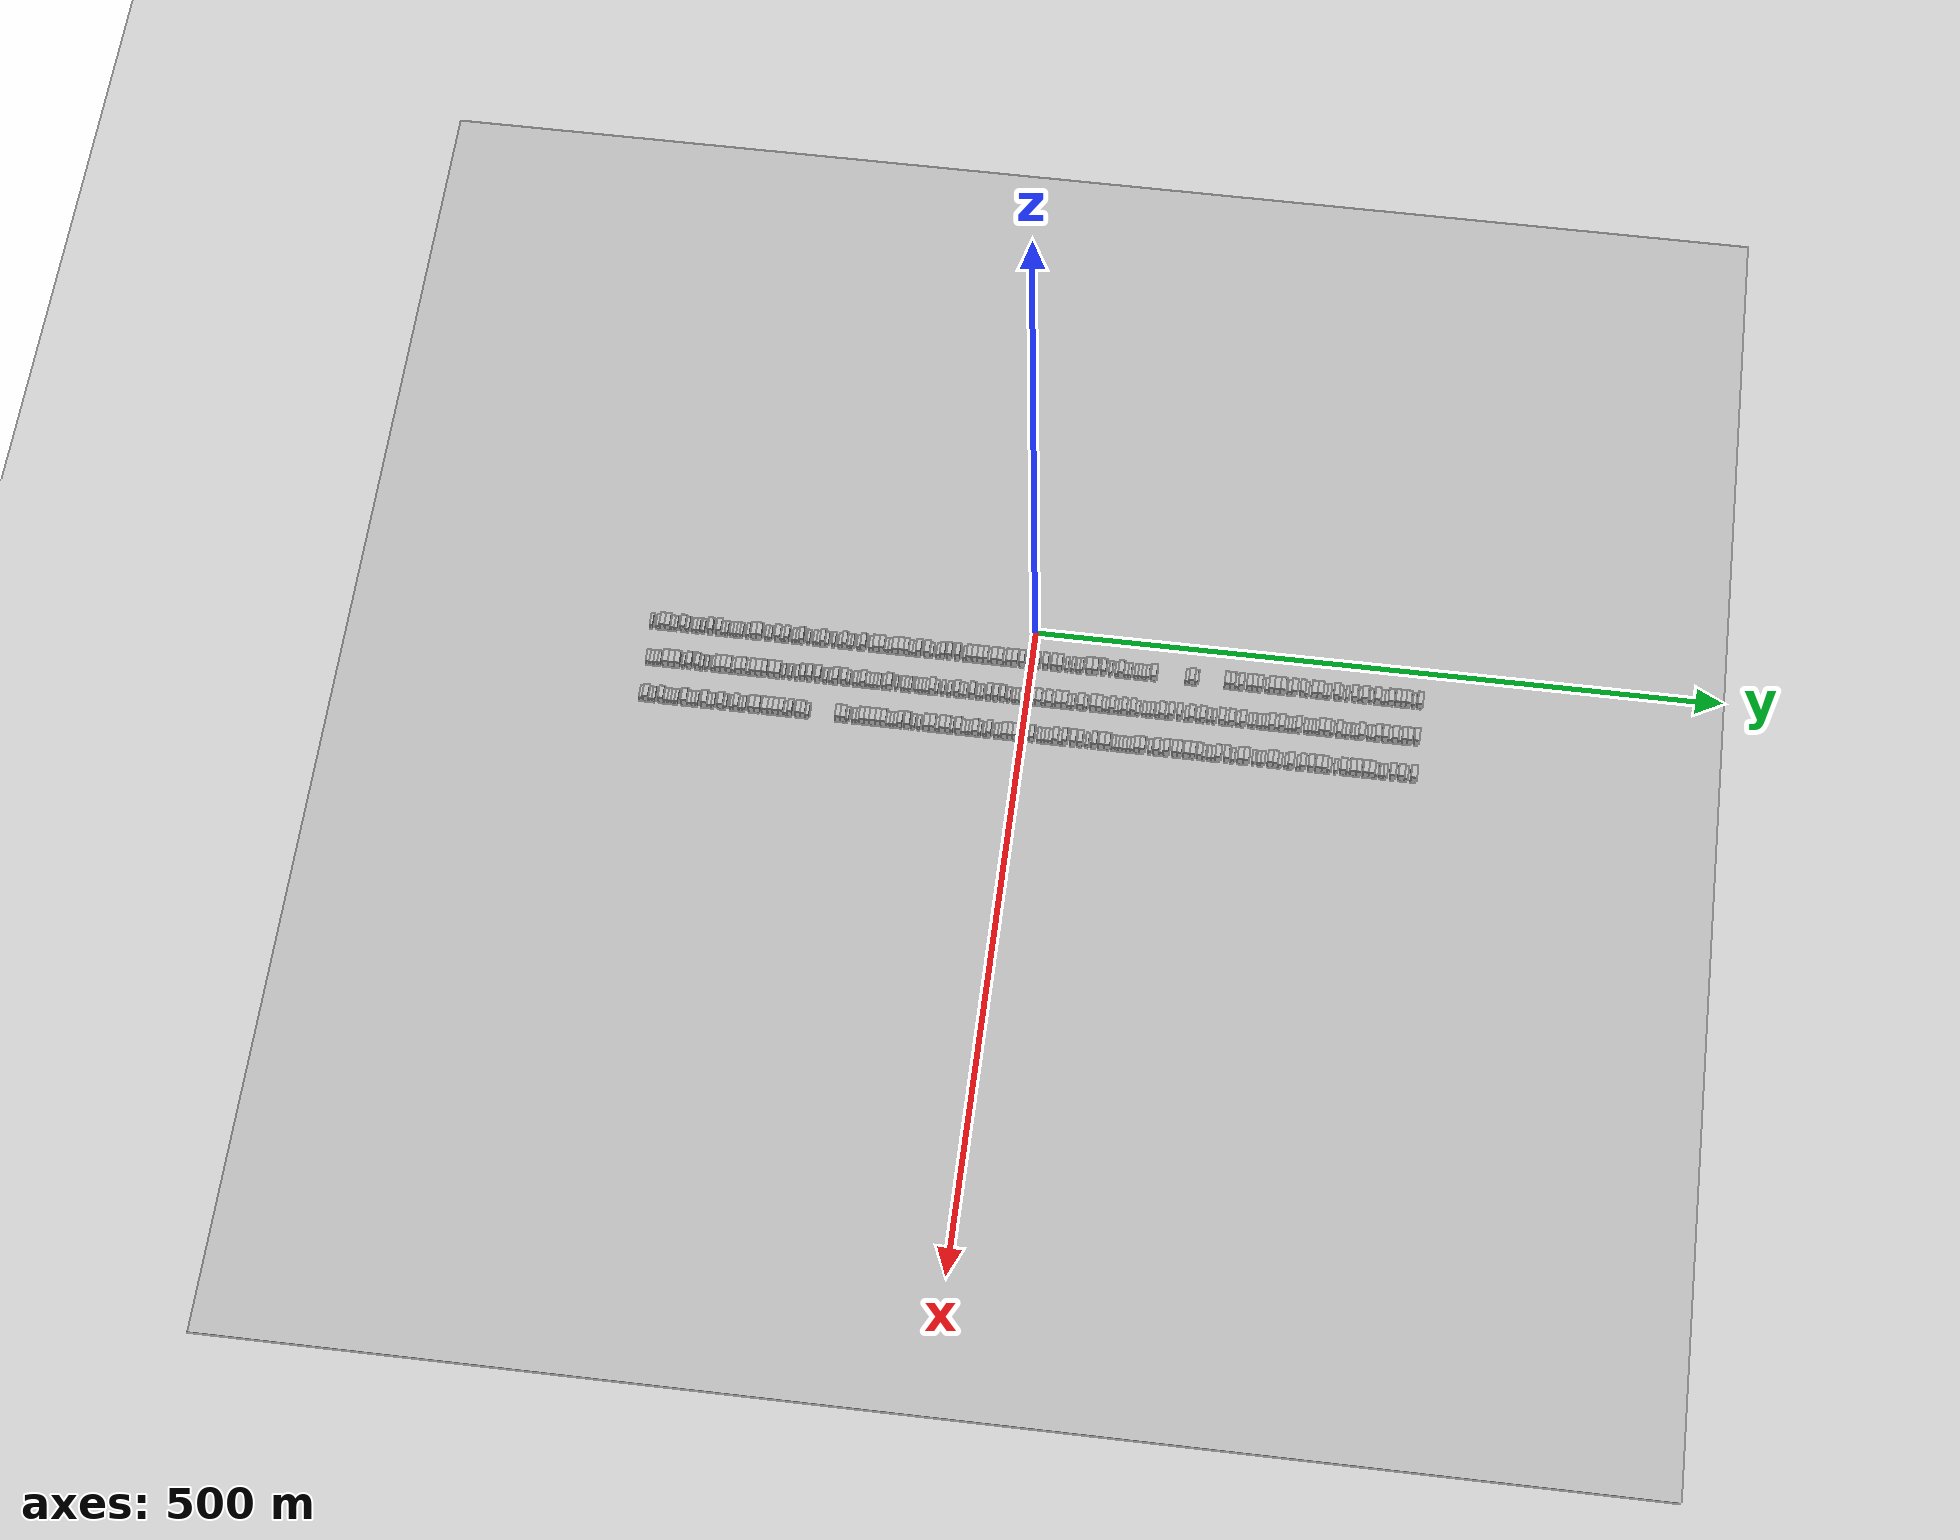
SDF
<?xml version="1.0" encoding="utf-8"?>

<sdf version="1.6">

   <world name="default">

      <gui fullscreen="0">

         <camera name="user_camera">

            <pose>-15 0 4.57585 0 0 0</pose>

            <view_controller>orbit</view_controller>

         </camera>

      </gui>

      <scene>

         <sky>

           <clouds>

             <speed>12</speed>

           </clouds>

         </sky>

         <ambient>0.4 0.4 0.4 1</ambient>

         <background>0.7 0.7 0.7 1</background>

         <shadows>1</shadows>

      </scene>

      <gravity>0 0 -9.8066</gravity>

      <magnetic_field>6e-06 2.3e-05 -4.2e-05</magnetic_field>

      <physics default="0" name="default_physics" type="ode">

         <ode>

            <solver>

               <type>quick</type>

               <iters>10</iters>

               <sor>1.0</sor>

               <use_dynamic_moi_rescaling>0</use_dynamic_moi_rescaling>

            </solver>

            <constraints>

               <cfm>0</cfm>

               <erp>0.2</erp>

               <contact_max_correcting_vel>100</contact_max_correcting_vel>

               <contact_surface_layer>0.001</contact_surface_layer>

            </constraints>

         </ode>

         <max_step_size>0.004</max_step_size>

         <real_time_factor>1</real_time_factor>

         <real_time_update_rate>250</real_time_update_rate>

      </physics>

      <light name="sun" type="directional">

         <cast_shadows>1</cast_shadows>

         <pose>0 0 10 0 0 0</pose>

         <diffuse>0.8 0.8 0.8 1</diffuse>

         <specular>0.2 0.2 0.2 1</specular>

         <attenuation>

            <range>1000</range>

            <constant>0.9</constant>

            <linear>0.01</linear>

            <quadratic>0.001</quadratic>

         </attenuation>

         <direction>-0.5 0.1 -0.9</direction>

      </light>

      <include>

         <name>ground_plane_1</name>

         <uri>model://HANNAS_ground_plane</uri>

         <pose>0 0 0  0 0 0</pose>

      </include>

      <include>

         <name>ground_plane_2</name>

         <uri>model://HANNAS_ground_plane</uri>

         <pose>100 0 0  0 0 0</pose>

      </include>

      <model name="building_1">

         <static>1</static>

         <pose frame="">25.0000 -278.7778 0 0.000000 0.000000 0.000000</pose>

         <link name="link">

            <pose frame="">0 0 3.00 0 0 0</pose>

            <collision name="collision">

               <geometry>

                  <box>

                     <size>10.0000 2.4443 6.0000</size>

                  </box>

               </geometry>

               <max_contacts>10</max_contacts>

               <surface>

                  <contact>

                     <ode/>

                  </contact>

                  <bounce/>

                  <friction>

                     <torsional>

                        <ode/>

                     </torsional>

                     <ode/>

                  </friction>

               </surface>

            </collision>

            <visual name="visual">

               <cast_shadows>0</cast_shadows>

               <geometry>

                  <box>

                     <size>10.0000 2.4443 6.0000</size>

                  </box>

               </geometry>

               <material>

                  <script>

                     <uri>model://HANNAS_wall/materials/scripts</uri>

                     <uri>model://HANNAS_wall/materials/textures</uri>

                     <name>vrc/HANNAS_wall</name>

                  </script>

               </material>

            </visual>

            <self_collide>0</self_collide>

            <enable_wind>0</enable_wind>

            <kinematic>0</kinematic>

         </link>

      </model>

      <model name="building_2">

         <static>1</static>

         <pose frame="">25.0000 -274.1004 0 0.000000 0.000000 0.000000</pose>

         <link name="link">

            <pose frame="">0 0 3.00 0 0 0</pose>

            <collision name="collision">

               <geometry>

                  <box>

                     <size>10.0000 2.9106 6.0000</size>

                  </box>

               </geometry>

               <max_contacts>10</max_contacts>

               <surface>

                  <contact>

                     <ode/>

                  </contact>

                  <bounce/>

                  <friction>

                     <torsional>

                        <ode/>

                     </torsional>

                     <ode/>

                  </friction>

               </surface>

            </collision>

            <visual name="visual">

               <cast_shadows>0</cast_shadows>

               <geometry>

                  <box>

                     <size>10.0000 2.9106 6.0000</size>

                  </box>

               </geometry>

               <material>

                  <script>

                     <uri>model://HANNAS_wall/materials/scripts</uri>

                     <uri>model://HANNAS_wall/materials/textures</uri>

                     <name>vrc/HANNAS_wall</name>

                  </script>

               </material>

            </visual>

            <self_collide>0</self_collide>

            <enable_wind>0</enable_wind>

            <kinematic>0</kinematic>

         </link>

      </model>

      <model name="building_3">

         <static>1</static>

         <pose frame="">25.0000 -270.7684 0 0.000000 0.000000 0.000000</pose>

         <link name="link">

            <pose frame="">0 0 4.50 0 0 0</pose>

            <collision name="collision">

               <geometry>

                  <box>

                     <size>10.0000 3.7533 9.0000</size>

                  </box>

               </geometry>

               <max_contacts>10</max_contacts>

               <surface>

                  <contact>

                     <ode/>

                  </contact>

                  <bounce/>

                  <friction>

                     <torsional>

                        <ode/>

                     </torsional>

                     <ode/>

                  </friction>

               </surface>

            </collision>

            <visual name="visual">

               <cast_shadows>0</cast_shadows>

               <geometry>

                  <box>

                     <size>10.0000 3.7533 9.0000</size>

                  </box>

               </geometry>

               <material>

                  <script>

                     <uri>model://HANNAS_wall/materials/scripts</uri>

                     <uri>model://HANNAS_wall/materials/textures</uri>

                     <name>vrc/HANNAS_wall</name>

                  </script>

               </material>

            </visual>

            <self_collide>0</self_collide>

            <enable_wind>0</enable_wind>

            <kinematic>0</kinematic>

         </link>

      </model>

      <model name="building_4">

         <static>1</static>

         <pose frame="">25.0000 -266.8182 0 0.000000 0.000000 0.000000</pose>

         <link name="link">

            <pose frame="">0 0 4.50 0 0 0</pose>

            <collision name="collision">

               <geometry>

                  <box>

                     <size>10.0000 4.1469 9.0000</size>

                  </box>

               </geometry>

               <max_contacts>10</max_contacts>

               <surface>

                  <contact>

                     <ode/>

                  </contact>

                  <bounce/>

                  <friction>

                     <torsional>

                        <ode/>

                     </torsional>

                     <ode/>

                  </friction>

               </surface>

            </collision>

            <visual name="visual">

               <cast_shadows>0</cast_shadows>

               <geometry>

                  <box>

                     <size>10.0000 4.1469 9.0000</size>

                  </box>

               </geometry>

               <material>

                  <script>

                     <uri>model://HANNAS_wall/materials/scripts</uri>

                     <uri>model://HANNAS_wall/materials/textures</uri>

                     <name>vrc/HANNAS_wall</name>

                  </script>

               </material>

            </visual>

            <self_collide>0</self_collide>

            <enable_wind>0</enable_wind>

            <kinematic>0</kinematic>

         </link>

      </model>

      <model name="building_5">

         <static>1</static>

         <pose frame="">25.0000 -263.3149 0 0.000000 0.000000 0.000000</pose>

         <link name="link">

            <pose frame="">0 0 3.00 0 0 0</pose>

            <collision name="collision">

               <geometry>

                  <box>

                     <size>10.0000 2.8598 6.0000</size>

                  </box>

               </geometry>

               <max_contacts>10</max_contacts>

               <surface>

                  <contact>

                     <ode/>

                  </contact>

                  <bounce/>

                  <friction>

                     <torsional>

                        <ode/>

                     </torsional>

                     <ode/>

                  </friction>

               </surface>

            </collision>

            <visual name="visual">

               <cast_shadows>0</cast_shadows>

               <geometry>

                  <box>

                     <size>10.0000 2.8598 6.0000</size>

                  </box>

               </geometry>

               <material>

                  <script>

                     <uri>model://HANNAS_wall/materials/scripts</uri>

                     <uri>model://HANNAS_wall/materials/textures</uri>

                     <name>vrc/HANNAS_wall</name>

                  </script>

               </material>

            </visual>

            <self_collide>0</self_collide>

            <enable_wind>0</enable_wind>

            <kinematic>0</kinematic>

         </link>

      </model>

      <model name="building_6">

         <static>1</static>

         <pose frame="">25.0000 -260.6631 0 0.000000 0.000000 0.000000</pose>

         <link name="link">

            <pose frame="">0 0 3.00 0 0 0</pose>

            <collision name="collision">

               <geometry>

                  <box>

                     <size>10.0000 2.4438 6.0000</size>

                  </box>

               </geometry>

               <max_contacts>10</max_contacts>

               <surface>

                  <contact>

                     <ode/>

                  </contact>

                  <bounce/>

                  <friction>

                     <torsional>

                        <ode/>

                     </torsional>

                     <ode/>

                  </friction>

               </surface>

            </collision>

            <visual name="visual">

               <cast_shadows>0</cast_shadows>

               <geometry>

                  <box>

                     <size>10.0000 2.4438 6.0000</size>

                  </box>

               </geometry>

               <material>

                  <script>

                     <uri>model://HANNAS_wall/materials/scripts</uri>

                     <uri>model://HANNAS_wall/materials/textures</uri>

                     <name>vrc/HANNAS_wall</name>

                  </script>

               </material>

            </visual>

            <self_collide>0</self_collide>

            <enable_wind>0</enable_wind>

            <kinematic>0</kinematic>

         </link>

      </model>

      <model name="building_7">

         <static>1</static>

         <pose frame="">25.0000 -255.4971 0 0.000000 0.000000 0.000000</pose>

         <link name="link">

            <pose frame="">0 0 4.50 0 0 0</pose>

            <collision name="collision">

               <geometry>

                  <box>

                     <size>10.0000 3.8881 9.0000</size>

                  </box>

               </geometry>

               <max_contacts>10</max_contacts>

               <surface>

                  <contact>

                     <ode/>

                  </contact>

                  <bounce/>

                  <friction>

                     <torsional>

                        <ode/>

                     </torsional>

                     <ode/>

                  </friction>

               </surface>

            </collision>

            <visual name="visual">

               <cast_shadows>0</cast_shadows>

               <geometry>

                  <box>

                     <size>10.0000 3.8881 9.0000</size>

                  </box>

               </geometry>

               <material>

                  <script>

                     <uri>model://HANNAS_wall/materials/scripts</uri>

                     <uri>model://HANNAS_wall/materials/textures</uri>

                     <name>vrc/HANNAS_wall</name>

                  </script>

               </material>

            </visual>

            <self_collide>0</self_collide>

            <enable_wind>0</enable_wind>

            <kinematic>0</kinematic>

         </link>

      </model>

      <model name="building_8">

         <static>1</static>

         <pose frame="">25.0000 -252.1289 0 0.000000 0.000000 0.000000</pose>

         <link name="link">

            <pose frame="">0 0 3.00 0 0 0</pose>

            <collision name="collision">

               <geometry>

                  <box>

                     <size>10.0000 2.8483 6.0000</size>

                  </box>

               </geometry>

               <max_contacts>10</max_contacts>

               <surface>

                  <contact>

                     <ode/>

                  </contact>

                  <bounce/>

                  <friction>

                     <torsional>

                        <ode/>

                     </torsional>

                     <ode/>

                  </friction>

               </surface>

            </collision>

            <visual name="visual">

               <cast_shadows>0</cast_shadows>

               <geometry>

                  <box>

                     <size>10.0000 2.8483 6.0000</size>

                  </box>

               </geometry>

               <material>

                  <script>

                     <uri>model://HANNAS_wall/materials/scripts</uri>

                     <uri>model://HANNAS_wall/materials/textures</uri>

                     <name>vrc/HANNAS_wall</name>

                  </script>

               </material>

            </visual>

            <self_collide>0</self_collide>

            <enable_wind>0</enable_wind>

            <kinematic>0</kinematic>

         </link>

      </model>

      <model name="building_9">

         <static>1</static>

         <pose frame="">25.0000 -247.2244 0 0.000000 0.000000 0.000000</pose>

         <link name="link">

            <pose frame="">0 0 3.00 0 0 0</pose>

            <collision name="collision">

               <geometry>

                  <box>

                     <size>10.0000 2.9608 6.0000</size>

                  </box>

               </geometry>

               <max_contacts>10</max_contacts>

               <surface>

                  <contact>

                     <ode/>

                  </contact>

                  <bounce/>

                  <friction>

                     <torsional>

                        <ode/>

                     </torsional>

                     <ode/>

                  </friction>

               </surface>

            </collision>

            <visual name="visual">

               <cast_shadows>0</cast_shadows>

               <geometry>

                  <box>

                     <size>10.0000 2.9608 6.0000</size>

                  </box>

               </geometry>

               <material>

                  <script>

                     <uri>model://HANNAS_wall/materials/scripts</uri>

                     <uri>model://HANNAS_wall/materials/textures</uri>

                     <name>vrc/HANNAS_wall</name>

                  </script>

               </material>

            </visual>

            <self_collide>0</self_collide>

            <enable_wind>0</enable_wind>

            <kinematic>0</kinematic>

         </link>

      </model>

      <model name="building_10">

         <static>1</static>

         <pose frame="">25.0000 -244.3663 0 0.000000 0.000000 0.000000</pose>

         <link name="link">

            <pose frame="">0 0 3.00 0 0 0</pose>

            <collision name="collision">

               <geometry>

                  <box>

                     <size>10.0000 2.7552 6.0000</size>

                  </box>

               </geometry>

               <max_contacts>10</max_contacts>

               <surface>

                  <contact>

                     <ode/>

                  </contact>

                  <bounce/>

                  <friction>

                     <torsional>

                        <ode/>

                     </torsional>

                     <ode/>

                  </friction>

               </surface>

            </collision>

            <visual name="visual">

               <cast_shadows>0</cast_shadows>

               <geometry>

                  <box>

                     <size>10.0000 2.7552 6.0000</size>

                  </box>

               </geometry>

               <material>

                  <script>

                     <uri>model://HANNAS_wall/materials/scripts</uri>

                     <uri>model://HANNAS_wall/materials/textures</uri>

                     <name>vrc/HANNAS_wall</name>

                  </script>

               </material>

            </visual>

            <self_collide>0</self_collide>

            <enable_wind>0</enable_wind>

            <kinematic>0</kinematic>

         </link>

      </model>

      <model name="building_11">

         <static>1</static>

         <pose frame="">25.0000 -240.6060 0 0.000000 0.000000 0.000000</pose>

         <link name="link">

            <pose frame="">0 0 3.00 0 0 0</pose>

            <collision name="collision">

               <geometry>

                  <box>

                     <size>10.0000 2.7654 6.0000</size>

                  </box>

               </geometry>

               <max_contacts>10</max_contacts>

               <surface>

                  <contact>

                     <ode/>

                  </contact>

                  <bounce/>

                  <friction>

                     <torsional>

                        <ode/>

                     </torsional>

                     <ode/>

                  </friction>

               </surface>

            </collision>

            <visual name="visual">

               <cast_shadows>0</cast_shadows>

               <geometry>

                  <box>

                     <size>10.0000 2.7654 6.0000</size>

                  </box>

               </geometry>

               <material>

                  <script>

                     <uri>model://HANNAS_wall/materials/scripts</uri>

                     <uri>model://HANNAS_wall/materials/textures</uri>

                     <name>vrc/HANNAS_wall</name>

                  </script>

               </material>

            </visual>

            <self_collide>0</self_collide>

            <enable_wind>0</enable_wind>

            <kinematic>0</kinematic>

         </link>

      </model>

      <model name="building_12">

         <static>1</static>

         <pose frame="">25.0000 -235.1955 0 0.000000 0.000000 0.000000</pose>

         <link name="link">

            <pose frame="">0 0 4.50 0 0 0</pose>

            <collision name="collision">

               <geometry>

                  <box>

                     <size>10.0000 4.0555 9.0000</size>

                  </box>

               </geometry>

               <max_contacts>10</max_contacts>

               <surface>

                  <contact>

                     <ode/>

                  </contact>

                  <bounce/>

                  <friction>

                     <torsional>

                        <ode/>

                     </torsional>

                     <ode/>

                  </friction>

               </surface>

            </collision>

            <visual name="visual">

               <cast_shadows>0</cast_shadows>

               <geometry>

                  <box>

                     <size>10.0000 4.0555 9.0000</size>

                  </box>

               </geometry>

               <material>

                  <script>

                     <uri>model://HANNAS_wall/materials/scripts</uri>

                     <uri>model://HANNAS_wall/materials/textures</uri>

                     <name>vrc/HANNAS_wall</name>

                  </script>

               </material>

            </visual>

            <self_collide>0</self_collide>

            <enable_wind>0</enable_wind>

            <kinematic>0</kinematic>

         </link>

      </model>

      <model name="building_13">

         <static>1</static>

         <pose frame="">25.0000 -229.2049 0 0.000000 0.000000 0.000000</pose>

         <link name="link">

            <pose frame="">0 0 4.50 0 0 0</pose>

            <collision name="collision">

               <geometry>

                  <box>

                     <size>10.0000 3.9257 9.0000</size>

                  </box>

               </geometry>

               <max_contacts>10</max_contacts>

               <surface>

                  <contact>

                     <ode/>

                  </contact>

                  <bounce/>

                  <friction>

                     <torsional>

                        <ode/>

                     </torsional>

                     <ode/>

                  </friction>

               </surface>

            </collision>

            <visual name="visual">

               <cast_shadows>0</cast_shadows>

               <geometry>

                  <box>

                     <size>10.0000 3.9257 9.0000</size>

                  </box>

               </geometry>

               <material>

                  <script>

                     <uri>model://HANNAS_wall/materials/scripts</uri>

                     <uri>model://HANNAS_wall/materials/textures</uri>

                     <name>vrc/HANNAS_wall</name>

                  </script>

               </material>

            </visual>

            <self_collide>0</self_collide>

            <enable_wind>0</enable_wind>

            <kinematic>0</kinematic>

         </link>

      </model>

      <model name="building_14">

         <static>1</static>

         <pose frame="">25.0000 -225.9789 0 0.000000 0.000000 0.000000</pose>

         <link name="link">

            <pose frame="">0 0 3.00 0 0 0</pose>

            <collision name="collision">

               <geometry>

                  <box>

                     <size>10.0000 2.5264 6.0000</size>

                  </box>

               </geometry>

               <max_contacts>10</max_contacts>

               <surface>

                  <contact>

                     <ode/>

                  </contact>

                  <bounce/>

                  <friction>

                     <torsional>

                        <ode/>

                     </torsional>

                     <ode/>

                  </friction>

               </surface>

            </collision>

            <visual name="visual">

               <cast_shadows>0</cast_shadows>

               <geometry>

                  <box>

                     <size>10.0000 2.5264 6.0000</size>

                  </box>

               </geometry>

               <material>

                  <script>

                     <uri>model://HANNAS_wall/materials/scripts</uri>

                     <uri>model://HANNAS_wall/materials/textures</uri>

                     <name>vrc/HANNAS_wall</name>

                  </script>

               </material>

            </visual>

            <self_collide>0</self_collide>

            <enable_wind>0</enable_wind>

            <kinematic>0</kinematic>

         </link>

      </model>

      <model name="building_15">

         <static>1</static>

         <pose frame="">25.0000 -223.4510 0 0.000000 0.000000 0.000000</pose>

         <link name="link">

            <pose frame="">0 0 3.00 0 0 0</pose>

            <collision name="collision">

               <geometry>

                  <box>

                     <size>10.0000 2.5294 6.0000</size>

                  </box>

               </geometry>

               <max_contacts>10</max_contacts>

               <surface>

                  <contact>

                     <ode/>

                  </contact>

                  <bounce/>

                  <friction>

                     <torsional>

                        <ode/>

                     </torsional>

                     <ode/>

                  </friction>

               </surface>

            </collision>

            <visual name="visual">

               <cast_shadows>0</cast_shadows>

               <geometry>

                  <box>

                     <size>10.0000 2.5294 6.0000</size>

                  </box>

               </geometry>

               <material>

                  <script>

                     <uri>model://HANNAS_wall/materials/scripts</uri>

                     <uri>model://HANNAS_wall/materials/textures</uri>

                     <name>vrc/HANNAS_wall</name>

                  </script>

               </material>

            </visual>

            <self_collide>0</self_collide>

            <enable_wind>0</enable_wind>

            <kinematic>0</kinematic>

         </link>

      </model>

      <model name="building_16">

         <static>1</static>

         <pose frame="">25.0000 -219.9777 0 0.000000 0.000000 0.000000</pose>

         <link name="link">

            <pose frame="">0 0 3.00 0 0 0</pose>

            <collision name="collision">

               <geometry>

                  <box>

                     <size>10.0000 2.4171 6.0000</size>

                  </box>

               </geometry>

               <max_contacts>10</max_contacts>

               <surface>

                  <contact>

                     <ode/>

                  </contact>

                  <bounce/>

                  <friction>

                     <torsional>

                        <ode/>

                     </torsional>

                     <ode/>

                  </friction>

               </surface>

            </collision>

            <visual name="visual">

               <cast_shadows>0</cast_shadows>

               <geometry>

                  <box>

                     <size>10.0000 2.4171 6.0000</size>

                  </box>

               </geometry>

               <material>

                  <script>

                     <uri>model://HANNAS_wall/materials/scripts</uri>

                     <uri>model://HANNAS_wall/materials/textures</uri>

                     <name>vrc/HANNAS_wall</name>

                  </script>

               </material>

            </visual>

            <self_collide>0</self_collide>

            <enable_wind>0</enable_wind>

            <kinematic>0</kinematic>

         </link>

      </model>

      <model name="building_17">

         <static>1</static>

         <pose frame="">25.0000 -217.5321 0 0.000000 0.000000 0.000000</pose>

         <link name="link">

            <pose frame="">0 0 3.00 0 0 0</pose>

            <collision name="collision">

               <geometry>

                  <box>

                     <size>10.0000 2.4741 6.0000</size>

                  </box>

               </geometry>

               <max_contacts>10</max_contacts>

               <surface>

                  <contact>

                     <ode/>

                  </contact>

                  <bounce/>

                  <friction>

                     <torsional>

                        <ode/>

                     </torsional>

                     <ode/>

                  </friction>

               </surface>

            </collision>

            <visual name="visual">

               <cast_shadows>0</cast_shadows>

               <geometry>

                  <box>

                     <size>10.0000 2.4741 6.0000</size>

                  </box>

               </geometry>

               <material>

                  <script>

                     <uri>model://HANNAS_wall/materials/scripts</uri>

                     <uri>model://HANNAS_wall/materials/textures</uri>

                     <name>vrc/HANNAS_wall</name>

                  </script>

               </material>

            </visual>

            <self_collide>0</self_collide>

            <enable_wind>0</enable_wind>

            <kinematic>0</kinematic>

         </link>

      </model>

      <model name="building_18">

         <static>1</static>

         <pose frame="">25.0000 -214.9892 0 0.000000 0.000000 0.000000</pose>

         <link name="link">

            <pose frame="">0 0 3.00 0 0 0</pose>

            <collision name="collision">

               <geometry>

                  <box>

                     <size>10.0000 2.6118 6.0000</size>

                  </box>

               </geometry>

               <max_contacts>10</max_contacts>

               <surface>

                  <contact>

                     <ode/>

                  </contact>

                  <bounce/>

                  <friction>

                     <torsional>

                        <ode/>

                     </torsional>

                     <ode/>

                  </friction>

               </surface>

            </collision>

            <visual name="visual">

               <cast_shadows>0</cast_shadows>

               <geometry>

                  <box>

                     <size>10.0000 2.6118 6.0000</size>

                  </box>

               </geometry>

               <material>

                  <script>

                     <uri>model://HANNAS_wall/materials/scripts</uri>

                     <uri>model://HANNAS_wall/materials/textures</uri>

                     <name>vrc/HANNAS_wall</name>

                  </script>

               </material>

            </visual>

            <self_collide>0</self_collide>

            <enable_wind>0</enable_wind>

            <kinematic>0</kinematic>

         </link>

      </model>

      <model name="building_19">

         <static>1</static>

         <pose frame="">25.0000 -212.4268 0 0.000000 0.000000 0.000000</pose>

         <link name="link">

            <pose frame="">0 0 3.00 0 0 0</pose>

            <collision name="collision">

               <geometry>

                  <box>

                     <size>10.0000 2.5130 6.0000</size>

                  </box>

               </geometry>

               <max_contacts>10</max_contacts>

               <surface>

                  <contact>

                     <ode/>

                  </contact>

                  <bounce/>

                  <friction>

                     <torsional>

                        <ode/>

                     </torsional>

                     <ode/>

                  </friction>

               </surface>

            </collision>

            <visual name="visual">

               <cast_shadows>0</cast_shadows>

               <geometry>

                  <box>

                     <size>10.0000 2.5130 6.0000</size>

                  </box>

               </geometry>

               <material>

                  <script>

                     <uri>model://HANNAS_wall/materials/scripts</uri>

                     <uri>model://HANNAS_wall/materials/textures</uri>

                     <name>vrc/HANNAS_wall</name>

                  </script>

               </material>

            </visual>

            <self_collide>0</self_collide>

            <enable_wind>0</enable_wind>

            <kinematic>0</kinematic>

         </link>

      </model>

      <model name="building_20">

         <static>1</static>

         <pose frame="">25.0000 -207.8493 0 0.000000 0.000000 0.000000</pose>

         <link name="link">

            <pose frame="">0 0 3.00 0 0 0</pose>

            <collision name="collision">

               <geometry>

                  <box>

                     <size>10.0000 2.6420 6.0000</size>

                  </box>

               </geometry>

               <max_contacts>10</max_contacts>

               <surface>

                  <contact>

                     <ode/>

                  </contact>

                  <bounce/>

                  <friction>

                     <torsional>

                        <ode/>

                     </torsional>

                     <ode/>

                  </friction>

               </surface>

            </collision>

            <visual name="visual">

               <cast_shadows>0</cast_shadows>

               <geometry>

                  <box>

                     <size>10.0000 2.6420 6.0000</size>

                  </box>

               </geometry>

               <material>

                  <script>

                     <uri>model://HANNAS_wall/materials/scripts</uri>

                     <uri>model://HANNAS_wall/materials/textures</uri>

                     <name>vrc/HANNAS_wall</name>

                  </script>

               </material>

            </visual>

            <self_collide>0</self_collide>

            <enable_wind>0</enable_wind>

            <kinematic>0</kinematic>

         </link>

      </model>

      <model name="building_21">

         <static>1</static>

         <pose frame="">25.0000 -203.5837 0 0.000000 0.000000 0.000000</pose>

         <link name="link">

            <pose frame="">0 0 4.50 0 0 0</pose>

            <collision name="collision">

               <geometry>

                  <box>

                     <size>10.0000 3.8892 9.0000</size>

                  </box>

               </geometry>

               <max_contacts>10</max_contacts>

               <surface>

                  <contact>

                     <ode/>

                  </contact>

                  <bounce/>

                  <friction>

                     <torsional>

                        <ode/>

                     </torsional>

                     <ode/>

                  </friction>

               </surface>

            </collision>

            <visual name="visual">

               <cast_shadows>0</cast_shadows>

               <geometry>

                  <box>

                     <size>10.0000 3.8892 9.0000</size>

                  </box>

               </geometry>

               <material>

                  <script>

                     <uri>model://HANNAS_wall/materials/scripts</uri>

                     <uri>model://HANNAS_wall/materials/textures</uri>

                     <name>vrc/HANNAS_wall</name>

                  </script>

               </material>

            </visual>

            <self_collide>0</self_collide>

            <enable_wind>0</enable_wind>

            <kinematic>0</kinematic>

         </link>

      </model>

      <model name="building_22">

         <static>1</static>

         <pose frame="">25.0000 -199.4928 0 0.000000 0.000000 0.000000</pose>

         <link name="link">

            <pose frame="">0 0 4.50 0 0 0</pose>

            <collision name="collision">

               <geometry>

                  <box>

                     <size>10.0000 4.2924 9.0000</size>

                  </box>

               </geometry>

               <max_contacts>10</max_contacts>

               <surface>

                  <contact>

                     <ode/>

                  </contact>

                  <bounce/>

                  <friction>

                     <torsional>

                        <ode/>

                     </torsional>

                     <ode/>

                  </friction>

               </surface>

            </collision>

            <visual name="visual">

               <cast_shadows>0</cast_shadows>

               <geometry>

                  <box>

                     <size>10.0000 4.2924 9.0000</size>

                  </box>

               </geometry>

               <material>

                  <script>

                     <uri>model://HANNAS_wall/materials/scripts</uri>

                     <uri>model://HANNAS_wall/materials/textures</uri>

                     <name>vrc/HANNAS_wall</name>

                  </script>

               </material>

            </visual>

            <self_collide>0</self_collide>

            <enable_wind>0</enable_wind>

            <kinematic>0</kinematic>

         </link>

      </model>

      <model name="building_23">

         <static>1</static>

         <pose frame="">25.0000 -194.0434 0 0.000000 0.000000 0.000000</pose>

         <link name="link">

            <pose frame="">0 0 3.00 0 0 0</pose>

            <collision name="collision">

               <geometry>

                  <box>

                     <size>10.0000 2.6064 6.0000</size>

                  </box>

               </geometry>

               <max_contacts>10</max_contacts>

               <surface>

                  <contact>

                     <ode/>

                  </contact>

                  <bounce/>

                  <friction>

                     <torsional>

                        <ode/>

                     </torsional>

                     <ode/>

                  </friction>

               </surface>

            </collision>

            <visual name="visual">

               <cast_shadows>0</cast_shadows>

               <geometry>

                  <box>

                     <size>10.0000 2.6064 6.0000</size>

                  </box>

               </geometry>

               <material>

                  <script>

                     <uri>model://HANNAS_wall/materials/scripts</uri>

                     <uri>model://HANNAS_wall/materials/textures</uri>

                     <name>vrc/HANNAS_wall</name>

                  </script>

               </material>

            </visual>

            <self_collide>0</self_collide>

            <enable_wind>0</enable_wind>

            <kinematic>0</kinematic>

         </link>

      </model>

      <model name="building_24">

         <static>1</static>

         <pose frame="">25.0000 -191.3741 0 0.000000 0.000000 0.000000</pose>

         <link name="link">

            <pose frame="">0 0 3.00 0 0 0</pose>

            <collision name="collision">

               <geometry>

                  <box>

                     <size>10.0000 2.7323 6.0000</size>

                  </box>

               </geometry>

               <max_contacts>10</max_contacts>

               <surface>

                  <contact>

                     <ode/>

                  </contact>

                  <bounce/>

                  <friction>

                     <torsional>

                        <ode/>

                     </torsional>

                     <ode/>

                  </friction>

               </surface>

            </collision>

            <visual name="visual">

               <cast_shadows>0</cast_shadows>

               <geometry>

                  <box>

                     <size>10.0000 2.7323 6.0000</size>

                  </box>

               </geometry>

               <material>

                  <script>

                     <uri>model://HANNAS_wall/materials/scripts</uri>

                     <uri>model://HANNAS_wall/materials/textures</uri>

                     <name>vrc/HANNAS_wall</name>

                  </script>

               </material>

            </visual>

            <self_collide>0</self_collide>

            <enable_wind>0</enable_wind>

            <kinematic>0</kinematic>

         </link>

      </model>

      <model name="building_25">

         <static>1</static>

         <pose frame="">25.0000 -185.8586 0 0.000000 0.000000 0.000000</pose>

         <link name="link">

            <pose frame="">0 0 4.50 0 0 0</pose>

            <collision name="collision">

               <geometry>

                  <box>

                     <size>10.0000 4.2987 9.0000</size>

                  </box>

               </geometry>

               <max_contacts>10</max_contacts>

               <surface>

                  <contact>

                     <ode/>

                  </contact>

                  <bounce/>

                  <friction>

                     <torsional>

                        <ode/>

                     </torsional>

                     <ode/>

                  </friction>

               </surface>

            </collision>

            <visual name="visual">

               <cast_shadows>0</cast_shadows>

               <geometry>

                  <box>

                     <size>10.0000 4.2987 9.0000</size>

                  </box>

               </geometry>

               <material>

                  <script>

                     <uri>model://HANNAS_wall/materials/scripts</uri>

                     <uri>model://HANNAS_wall/materials/textures</uri>

                     <name>vrc/HANNAS_wall</name>

                  </script>

               </material>

            </visual>

            <self_collide>0</self_collide>

            <enable_wind>0</enable_wind>

            <kinematic>0</kinematic>

         </link>

      </model>

      <model name="building_26">

         <static>1</static>

         <pose frame="">25.0000 -182.3043 0 0.000000 0.000000 0.000000</pose>

         <link name="link">

            <pose frame="">0 0 3.00 0 0 0</pose>

            <collision name="collision">

               <geometry>

                  <box>

                     <size>10.0000 2.8098 6.0000</size>

                  </box>

               </geometry>

               <max_contacts>10</max_contacts>

               <surface>

                  <contact>

                     <ode/>

                  </contact>

                  <bounce/>

                  <friction>

                     <torsional>

                        <ode/>

                     </torsional>

                     <ode/>

                  </friction>

               </surface>

            </collision>

            <visual name="visual">

               <cast_shadows>0</cast_shadows>

               <geometry>

                  <box>

                     <size>10.0000 2.8098 6.0000</size>

                  </box>

               </geometry>

               <material>

                  <script>

                     <uri>model://HANNAS_wall/materials/scripts</uri>

                     <uri>model://HANNAS_wall/materials/textures</uri>

                     <name>vrc/HANNAS_wall</name>

                  </script>

               </material>

            </visual>

            <self_collide>0</self_collide>

            <enable_wind>0</enable_wind>

            <kinematic>0</kinematic>

         </link>

      </model>

      <model name="building_27">

         <static>1</static>

         <pose frame="">25.0000 -179.0674 0 0.000000 0.000000 0.000000</pose>

         <link name="link">

            <pose frame="">0 0 4.50 0 0 0</pose>

            <collision name="collision">

               <geometry>

                  <box>

                     <size>10.0000 3.6641 9.0000</size>

                  </box>

               </geometry>

               <max_contacts>10</max_contacts>

               <surface>

                  <contact>

                     <ode/>

                  </contact>

                  <bounce/>

                  <friction>

                     <torsional>

                        <ode/>

                     </torsional>

                     <ode/>

                  </friction>

               </surface>

            </collision>

            <visual name="visual">

               <cast_shadows>0</cast_shadows>

               <geometry>

                  <box>

                     <size>10.0000 3.6641 9.0000</size>

                  </box>

               </geometry>

               <material>

                  <script>

                     <uri>model://HANNAS_wall/materials/scripts</uri>

                     <uri>model://HANNAS_wall/materials/textures</uri>

                     <name>vrc/HANNAS_wall</name>

                  </script>

               </material>

            </visual>

            <self_collide>0</self_collide>

            <enable_wind>0</enable_wind>

            <kinematic>0</kinematic>

         </link>

      </model>

      <model name="building_28">

         <static>1</static>

         <pose frame="">25.0000 -174.0113 0 0.000000 0.000000 0.000000</pose>

         <link name="link">

            <pose frame="">0 0 3.00 0 0 0</pose>

            <collision name="collision">

               <geometry>

                  <box>

                     <size>10.0000 2.4480 6.0000</size>

                  </box>

               </geometry>

               <max_contacts>10</max_contacts>

               <surface>

                  <contact>

                     <ode/>

                  </contact>

                  <bounce/>

                  <friction>

                     <torsional>

                        <ode/>

                     </torsional>

                     <ode/>

                  </friction>

               </surface>

            </collision>

            <visual name="visual">

               <cast_shadows>0</cast_shadows>

               <geometry>

                  <box>

                     <size>10.0000 2.4480 6.0000</size>

                  </box>

               </geometry>

               <material>

                  <script>

                     <uri>model://HANNAS_wall/materials/scripts</uri>

                     <uri>model://HANNAS_wall/materials/textures</uri>

                     <name>vrc/HANNAS_wall</name>

                  </script>

               </material>

            </visual>

            <self_collide>0</self_collide>

            <enable_wind>0</enable_wind>

            <kinematic>0</kinematic>

         </link>

      </model>

      <model name="building_29">

         <static>1</static>

         <pose frame="">25.0000 -171.5381 0 0.000000 0.000000 0.000000</pose>

         <link name="link">

            <pose frame="">0 0 3.00 0 0 0</pose>

            <collision name="collision">

               <geometry>

                  <box>

                     <size>10.0000 2.4984 6.0000</size>

                  </box>

               </geometry>

               <max_contacts>10</max_contacts>

               <surface>

                  <contact>

                     <ode/>

                  </contact>

                  <bounce/>

                  <friction>

                     <torsional>

                        <ode/>

                     </torsional>

                     <ode/>

                  </friction>

               </surface>

            </collision>

            <visual name="visual">

               <cast_shadows>0</cast_shadows>

               <geometry>

                  <box>

                     <size>10.0000 2.4984 6.0000</size>

                  </box>

               </geometry>

               <material>

                  <script>

                     <uri>model://HANNAS_wall/materials/scripts</uri>

                     <uri>model://HANNAS_wall/materials/textures</uri>

                     <name>vrc/HANNAS_wall</name>

                  </script>

               </material>

            </visual>

            <self_collide>0</self_collide>

            <enable_wind>0</enable_wind>

            <kinematic>0</kinematic>

         </link>

      </model>

      <model name="building_30">

         <static>1</static>

         <pose frame="">25.0000 -168.4540 0 0.000000 0.000000 0.000000</pose>

         <link name="link">

            <pose frame="">0 0 4.50 0 0 0</pose>

            <collision name="collision">

               <geometry>

                  <box>

                     <size>10.0000 3.6698 9.0000</size>

                  </box>

               </geometry>

               <max_contacts>10</max_contacts>

               <surface>

                  <contact>

                     <ode/>

                  </contact>

                  <bounce/>

                  <friction>

                     <torsional>

                        <ode/>

                     </torsional>

                     <ode/>

                  </friction>

               </surface>

            </collision>

            <visual name="visual">

               <cast_shadows>0</cast_shadows>

               <geometry>

                  <box>

                     <size>10.0000 3.6698 9.0000</size>

                  </box>

               </geometry>

               <material>

                  <script>

                     <uri>model://HANNAS_wall/materials/scripts</uri>

                     <uri>model://HANNAS_wall/materials/textures</uri>

                     <name>vrc/HANNAS_wall</name>

                  </script>

               </material>

            </visual>

            <self_collide>0</self_collide>

            <enable_wind>0</enable_wind>

            <kinematic>0</kinematic>

         </link>

      </model>

      <model name="building_31">

         <static>1</static>

         <pose frame="">25.0000 -163.2744 0 0.000000 0.000000 0.000000</pose>

         <link name="link">

            <pose frame="">0 0 3.00 0 0 0</pose>

            <collision name="collision">

               <geometry>

                  <box>

                     <size>10.0000 2.6895 6.0000</size>

                  </box>

               </geometry>

               <max_contacts>10</max_contacts>

               <surface>

                  <contact>

                     <ode/>

                  </contact>

                  <bounce/>

                  <friction>

                     <torsional>

                        <ode/>

                     </torsional>

                     <ode/>

                  </friction>

               </surface>

            </collision>

            <visual name="visual">

               <cast_shadows>0</cast_shadows>

               <geometry>

                  <box>

                     <size>10.0000 2.6895 6.0000</size>

                  </box>

               </geometry>

               <material>

                  <script>

                     <uri>model://HANNAS_wall/materials/scripts</uri>

                     <uri>model://HANNAS_wall/materials/textures</uri>

                     <name>vrc/HANNAS_wall</name>

                  </script>

               </material>

            </visual>

            <self_collide>0</self_collide>

            <enable_wind>0</enable_wind>

            <kinematic>0</kinematic>

         </link>

      </model>

      <model name="building_32">

         <static>1</static>

         <pose frame="">25.0000 -158.6864 0 0.000000 0.000000 0.000000</pose>

         <link name="link">

            <pose frame="">0 0 3.00 0 0 0</pose>

            <collision name="collision">

               <geometry>

                  <box>

                     <size>10.0000 2.4863 6.0000</size>

                  </box>

               </geometry>

               <max_contacts>10</max_contacts>

               <surface>

                  <contact>

                     <ode/>

                  </contact>

                  <bounce/>

                  <friction>

                     <torsional>

                        <ode/>

                     </torsional>

                     <ode/>

                  </friction>

               </surface>

            </collision>

            <visual name="visual">

               <cast_shadows>0</cast_shadows>

               <geometry>

                  <box>

                     <size>10.0000 2.4863 6.0000</size>

                  </box>

               </geometry>

               <material>

                  <script>

                     <uri>model://HANNAS_wall/materials/scripts</uri>

                     <uri>model://HANNAS_wall/materials/textures</uri>

                     <name>vrc/HANNAS_wall</name>

                  </script>

               </material>

            </visual>

            <self_collide>0</self_collide>

            <enable_wind>0</enable_wind>

            <kinematic>0</kinematic>

         </link>

      </model>

      <model name="building_33">

         <static>1</static>

         <pose frame="">25.0000 -156.1100 0 0.000000 0.000000 0.000000</pose>

         <link name="link">

            <pose frame="">0 0 3.00 0 0 0</pose>

            <collision name="collision">

               <geometry>

                  <box>

                     <size>10.0000 2.6665 6.0000</size>

                  </box>

               </geometry>

               <max_contacts>10</max_contacts>

               <surface>

                  <contact>

                     <ode/>

                  </contact>

                  <bounce/>

                  <friction>

                     <torsional>

                        <ode/>

                     </torsional>

                     <ode/>

                  </friction>

               </surface>

            </collision>

            <visual name="visual">

               <cast_shadows>0</cast_shadows>

               <geometry>

                  <box>

                     <size>10.0000 2.6665 6.0000</size>

                  </box>

               </geometry>

               <material>

                  <script>

                     <uri>model://HANNAS_wall/materials/scripts</uri>

                     <uri>model://HANNAS_wall/materials/textures</uri>

                     <name>vrc/HANNAS_wall</name>

                  </script>

               </material>

            </visual>

            <self_collide>0</self_collide>

            <enable_wind>0</enable_wind>

            <kinematic>0</kinematic>

         </link>

      </model>

      <model name="building_34">

         <static>1</static>

         <pose frame="">25.0000 -152.9184 0 0.000000 0.000000 0.000000</pose>

         <link name="link">

            <pose frame="">0 0 4.50 0 0 0</pose>

            <collision name="collision">

               <geometry>

                  <box>

                     <size>10.0000 3.7168 9.0000</size>

                  </box>

               </geometry>

               <max_contacts>10</max_contacts>

               <surface>

                  <contact>

                     <ode/>

                  </contact>

                  <bounce/>

                  <friction>

                     <torsional>

                        <ode/>

                     </torsional>

                     <ode/>

                  </friction>

               </surface>

            </collision>

            <visual name="visual">

               <cast_shadows>0</cast_shadows>

               <geometry>

                  <box>

                     <size>10.0000 3.7168 9.0000</size>

                  </box>

               </geometry>

               <material>

                  <script>

                     <uri>model://HANNAS_wall/materials/scripts</uri>

                     <uri>model://HANNAS_wall/materials/textures</uri>

                     <name>vrc/HANNAS_wall</name>

                  </script>

               </material>

            </visual>

            <self_collide>0</self_collide>

            <enable_wind>0</enable_wind>

            <kinematic>0</kinematic>

         </link>

      </model>

      <model name="building_35">

         <static>1</static>

         <pose frame="">25.0000 -149.6319 0 0.000000 0.000000 0.000000</pose>

         <link name="link">

            <pose frame="">0 0 3.00 0 0 0</pose>

            <collision name="collision">

               <geometry>

                  <box>

                     <size>10.0000 2.8561 6.0000</size>

                  </box>

               </geometry>

               <max_contacts>10</max_contacts>

               <surface>

                  <contact>

                     <ode/>

                  </contact>

                  <bounce/>

                  <friction>

                     <torsional>

                        <ode/>

                     </torsional>

                     <ode/>

                  </friction>

               </surface>

            </collision>

            <visual name="visual">

               <cast_shadows>0</cast_shadows>

               <geometry>

                  <box>

                     <size>10.0000 2.8561 6.0000</size>

                  </box>

               </geometry>

               <material>

                  <script>

                     <uri>model://HANNAS_wall/materials/scripts</uri>

                     <uri>model://HANNAS_wall/materials/textures</uri>

                     <name>vrc/HANNAS_wall</name>

                  </script>

               </material>

            </visual>

            <self_collide>0</self_collide>

            <enable_wind>0</enable_wind>

            <kinematic>0</kinematic>

         </link>

      </model>

      <model name="building_36">

         <static>1</static>

         <pose frame="">25.0000 -144.8360 0 0.000000 0.000000 0.000000</pose>

         <link name="link">

            <pose frame="">0 0 3.00 0 0 0</pose>

            <collision name="collision">

               <geometry>

                  <box>

                     <size>10.0000 2.7358 6.0000</size>

                  </box>

               </geometry>

               <max_contacts>10</max_contacts>

               <surface>

                  <contact>

                     <ode/>

                  </contact>

                  <bounce/>

                  <friction>

                     <torsional>

                        <ode/>

                     </torsional>

                     <ode/>

                  </friction>

               </surface>

            </collision>

            <visual name="visual">

               <cast_shadows>0</cast_shadows>

               <geometry>

                  <box>

                     <size>10.0000 2.7358 6.0000</size>

                  </box>

               </geometry>

               <material>

                  <script>

                     <uri>model://HANNAS_wall/materials/scripts</uri>

                     <uri>model://HANNAS_wall/materials/textures</uri>

                     <name>vrc/HANNAS_wall</name>

                  </script>

               </material>

            </visual>

            <self_collide>0</self_collide>

            <enable_wind>0</enable_wind>

            <kinematic>0</kinematic>

         </link>

      </model>

      <model name="building_37">

         <static>1</static>

         <pose frame="">25.0000 -140.0680 0 0.000000 0.000000 0.000000</pose>

         <link name="link">

            <pose frame="">0 0 3.00 0 0 0</pose>

            <collision name="collision">

               <geometry>

                  <box>

                     <size>10.0000 2.8001 6.0000</size>

                  </box>

               </geometry>

               <max_contacts>10</max_contacts>

               <surface>

                  <contact>

                     <ode/>

                  </contact>

                  <bounce/>

                  <friction>

                     <torsional>

                        <ode/>

                     </torsional>

                     <ode/>

                  </friction>

               </surface>

            </collision>

            <visual name="visual">

               <cast_shadows>0</cast_shadows>

               <geometry>

                  <box>

                     <size>10.0000 2.8001 6.0000</size>

                  </box>

               </geometry>

               <material>

                  <script>

                     <uri>model://HANNAS_wall/materials/scripts</uri>

                     <uri>model://HANNAS_wall/materials/textures</uri>

                     <name>vrc/HANNAS_wall</name>

                  </script>

               </material>

            </visual>

            <self_collide>0</self_collide>

            <enable_wind>0</enable_wind>

            <kinematic>0</kinematic>

         </link>

      </model>

      <model name="building_38">

         <static>1</static>

         <pose frame="">25.0000 -136.7631 0 0.000000 0.000000 0.000000</pose>

         <link name="link">

            <pose frame="">0 0 4.50 0 0 0</pose>

            <collision name="collision">

               <geometry>

                  <box>

                     <size>10.0000 3.8097 9.0000</size>

                  </box>

               </geometry>

               <max_contacts>10</max_contacts>

               <surface>

                  <contact>

                     <ode/>

                  </contact>

                  <bounce/>

                  <friction>

                     <torsional>

                        <ode/>

                     </torsional>

                     <ode/>

                  </friction>

               </surface>

            </collision>

            <visual name="visual">

               <cast_shadows>0</cast_shadows>

               <geometry>

                  <box>

                     <size>10.0000 3.8097 9.0000</size>

                  </box>

               </geometry>

               <material>

                  <script>

                     <uri>model://HANNAS_wall/materials/scripts</uri>

                     <uri>model://HANNAS_wall/materials/textures</uri>

                     <name>vrc/HANNAS_wall</name>

                  </script>

               </material>

            </visual>

            <self_collide>0</self_collide>

            <enable_wind>0</enable_wind>

            <kinematic>0</kinematic>

         </link>

      </model>

      <model name="building_39">

         <static>1</static>

         <pose frame="">25.0000 -133.6153 0 0.000000 0.000000 0.000000</pose>

         <link name="link">

            <pose frame="">0 0 3.00 0 0 0</pose>

            <collision name="collision">

               <geometry>

                  <box>

                     <size>10.0000 2.4858 6.0000</size>

                  </box>

               </geometry>

               <max_contacts>10</max_contacts>

               <surface>

                  <contact>

                     <ode/>

                  </contact>

                  <bounce/>

                  <friction>

                     <torsional>

                        <ode/>

                     </torsional>

                     <ode/>

                  </friction>

               </surface>

            </collision>

            <visual name="visual">

               <cast_shadows>0</cast_shadows>

               <geometry>

                  <box>

                     <size>10.0000 2.4858 6.0000</size>

                  </box>

               </geometry>

               <material>

                  <script>

                     <uri>model://HANNAS_wall/materials/scripts</uri>

                     <uri>model://HANNAS_wall/materials/textures</uri>

                     <name>vrc/HANNAS_wall</name>

                  </script>

               </material>

            </visual>

            <self_collide>0</self_collide>

            <enable_wind>0</enable_wind>

            <kinematic>0</kinematic>

         </link>

      </model>

      <model name="building_40">

         <static>1</static>

         <pose frame="">25.0000 -131.1574 0 0.000000 0.000000 0.000000</pose>

         <link name="link">

            <pose frame="">0 0 3.00 0 0 0</pose>

            <collision name="collision">

               <geometry>

                  <box>

                     <size>10.0000 2.4301 6.0000</size>

                  </box>

               </geometry>

               <max_contacts>10</max_contacts>

               <surface>

                  <contact>

                     <ode/>

                  </contact>

                  <bounce/>

                  <friction>

                     <torsional>

                        <ode/>

                     </torsional>

                     <ode/>

                  </friction>

               </surface>

            </collision>

            <visual name="visual">

               <cast_shadows>0</cast_shadows>

               <geometry>

                  <box>

                     <size>10.0000 2.4301 6.0000</size>

                  </box>

               </geometry>

               <material>

                  <script>

                     <uri>model://HANNAS_wall/materials/scripts</uri>

                     <uri>model://HANNAS_wall/materials/textures</uri>

                     <name>vrc/HANNAS_wall</name>

                  </script>

               </material>

            </visual>

            <self_collide>0</self_collide>

            <enable_wind>0</enable_wind>

            <kinematic>0</kinematic>

         </link>

      </model>

      <model name="building_41">

         <static>1</static>

         <pose frame="">25.0000 -126.5454 0 0.000000 0.000000 0.000000</pose>

         <link name="link">

            <pose frame="">0 0 3.00 0 0 0</pose>

            <collision name="collision">

               <geometry>

                  <box>

                     <size>10.0000 2.7939 6.0000</size>

                  </box>

               </geometry>

               <max_contacts>10</max_contacts>

               <surface>

                  <contact>

                     <ode/>

                  </contact>

                  <bounce/>

                  <friction>

                     <torsional>

                        <ode/>

                     </torsional>

                     <ode/>

                  </friction>

               </surface>

            </collision>

            <visual name="visual">

               <cast_shadows>0</cast_shadows>

               <geometry>

                  <box>

                     <size>10.0000 2.7939 6.0000</size>

                  </box>

               </geometry>

               <material>

                  <script>

                     <uri>model://HANNAS_wall/materials/scripts</uri>

                     <uri>model://HANNAS_wall/materials/textures</uri>

                     <name>vrc/HANNAS_wall</name>

                  </script>

               </material>

            </visual>

            <self_collide>0</self_collide>

            <enable_wind>0</enable_wind>

            <kinematic>0</kinematic>

         </link>

      </model>

      <model name="building_42">

         <static>1</static>

         <pose frame="">25.0000 -123.1025 0 0.000000 0.000000 0.000000</pose>

         <link name="link">

            <pose frame="">0 0 4.50 0 0 0</pose>

            <collision name="collision">

               <geometry>

                  <box>

                     <size>10.0000 4.0917 9.0000</size>

                  </box>

               </geometry>

               <max_contacts>10</max_contacts>

               <surface>

                  <contact>

                     <ode/>

                  </contact>

                  <bounce/>

                  <friction>

                     <torsional>

                        <ode/>

                     </torsional>

                     <ode/>

                  </friction>

               </surface>

            </collision>

            <visual name="visual">

               <cast_shadows>0</cast_shadows>

               <geometry>

                  <box>

                     <size>10.0000 4.0917 9.0000</size>

                  </box>

               </geometry>

               <material>

                  <script>

                     <uri>model://HANNAS_wall/materials/scripts</uri>

                     <uri>model://HANNAS_wall/materials/textures</uri>

                     <name>vrc/HANNAS_wall</name>

                  </script>

               </material>

            </visual>

            <self_collide>0</self_collide>

            <enable_wind>0</enable_wind>

            <kinematic>0</kinematic>

         </link>

      </model>

      <model name="building_43">

         <static>1</static>

         <pose frame="">25.0000 -117.5571 0 0.000000 0.000000 0.000000</pose>

         <link name="link">

            <pose frame="">0 0 3.00 0 0 0</pose>

            <collision name="collision">

               <geometry>

                  <box>

                     <size>10.0000 2.9992 6.0000</size>

                  </box>

               </geometry>

               <max_contacts>10</max_contacts>

               <surface>

                  <contact>

                     <ode/>

                  </contact>

                  <bounce/>

                  <friction>

                     <torsional>

                        <ode/>

                     </torsional>

                     <ode/>

                  </friction>

               </surface>

            </collision>

            <visual name="visual">

               <cast_shadows>0</cast_shadows>

               <geometry>

                  <box>

                     <size>10.0000 2.9992 6.0000</size>

                  </box>

               </geometry>

               <material>

                  <script>

                     <uri>model://HANNAS_wall/materials/scripts</uri>

                     <uri>model://HANNAS_wall/materials/textures</uri>

                     <name>vrc/HANNAS_wall</name>

                  </script>

               </material>

            </visual>

            <self_collide>0</self_collide>

            <enable_wind>0</enable_wind>

            <kinematic>0</kinematic>

         </link>

      </model>

      <model name="building_44">

         <static>1</static>

         <pose frame="">25.0000 -113.8441 0 0.000000 0.000000 0.000000</pose>

         <link name="link">

            <pose frame="">0 0 4.50 0 0 0</pose>

            <collision name="collision">

               <geometry>

                  <box>

                     <size>10.0000 4.4267 9.0000</size>

                  </box>

               </geometry>

               <max_contacts>10</max_contacts>

               <surface>

                  <contact>

                     <ode/>

                  </contact>

                  <bounce/>

                  <friction>

                     <torsional>

                        <ode/>

                     </torsional>

                     <ode/>

                  </friction>

               </surface>

            </collision>

            <visual name="visual">

               <cast_shadows>0</cast_shadows>

               <geometry>

                  <box>

                     <size>10.0000 4.4267 9.0000</size>

                  </box>

               </geometry>

               <material>

                  <script>

                     <uri>model://HANNAS_wall/materials/scripts</uri>

                     <uri>model://HANNAS_wall/materials/textures</uri>

                     <name>vrc/HANNAS_wall</name>

                  </script>

               </material>

            </visual>

            <self_collide>0</self_collide>

            <enable_wind>0</enable_wind>

            <kinematic>0</kinematic>

         </link>

      </model>

      <model name="building_45">

         <static>1</static>

         <pose frame="">25.0000 -109.5300 0 0.000000 0.000000 0.000000</pose>

         <link name="link">

            <pose frame="">0 0 4.50 0 0 0</pose>

            <collision name="collision">

               <geometry>

                  <box>

                     <size>10.0000 4.2016 9.0000</size>

                  </box>

               </geometry>

               <max_contacts>10</max_contacts>

               <surface>

                  <contact>

                     <ode/>

                  </contact>

                  <bounce/>

                  <friction>

                     <torsional>

                        <ode/>

                     </torsional>

                     <ode/>

                  </friction>

               </surface>

            </collision>

            <visual name="visual">

               <cast_shadows>0</cast_shadows>

               <geometry>

                  <box>

                     <size>10.0000 4.2016 9.0000</size>

                  </box>

               </geometry>

               <material>

                  <script>

                     <uri>model://HANNAS_wall/materials/scripts</uri>

                     <uri>model://HANNAS_wall/materials/textures</uri>

                     <name>vrc/HANNAS_wall</name>

                  </script>

               </material>

            </visual>

            <self_collide>0</self_collide>

            <enable_wind>0</enable_wind>

            <kinematic>0</kinematic>

         </link>

      </model>

      <model name="building_46">

         <static>1</static>

         <pose frame="">25.0000 -106.1285 0 0.000000 0.000000 0.000000</pose>

         <link name="link">

            <pose frame="">0 0 3.00 0 0 0</pose>

            <collision name="collision">

               <geometry>

                  <box>

                     <size>10.0000 2.6014 6.0000</size>

                  </box>

               </geometry>

               <max_contacts>10</max_contacts>

               <surface>

                  <contact>

                     <ode/>

                  </contact>

                  <bounce/>

                  <friction>

                     <torsional>

                        <ode/>

                     </torsional>

                     <ode/>

                  </friction>

               </surface>

            </collision>

            <visual name="visual">

               <cast_shadows>0</cast_shadows>

               <geometry>

                  <box>

                     <size>10.0000 2.6014 6.0000</size>

                  </box>

               </geometry>

               <material>

                  <script>

                     <uri>model://HANNAS_wall/materials/scripts</uri>

                     <uri>model://HANNAS_wall/materials/textures</uri>

                     <name>vrc/HANNAS_wall</name>

                  </script>

               </material>

            </visual>

            <self_collide>0</self_collide>

            <enable_wind>0</enable_wind>

            <kinematic>0</kinematic>

         </link>

      </model>

      <model name="building_47">

         <static>1</static>

         <pose frame="">25.0000 -103.3678 0 0.000000 0.000000 0.000000</pose>

         <link name="link">

            <pose frame="">0 0 3.00 0 0 0</pose>

            <collision name="collision">

               <geometry>

                  <box>

                     <size>10.0000 2.9200 6.0000</size>

                  </box>

               </geometry>

               <max_contacts>10</max_contacts>

               <surface>

                  <contact>

                     <ode/>

                  </contact>

                  <bounce/>

                  <friction>

                     <torsional>

                        <ode/>

                     </torsional>

                     <ode/>

                  </friction>

               </surface>

            </collision>

            <visual name="visual">

               <cast_shadows>0</cast_shadows>

               <geometry>

                  <box>

                     <size>10.0000 2.9200 6.0000</size>

                  </box>

               </geometry>

               <material>

                  <script>

                     <uri>model://HANNAS_wall/materials/scripts</uri>

                     <uri>model://HANNAS_wall/materials/textures</uri>

                     <name>vrc/HANNAS_wall</name>

                  </script>

               </material>

            </visual>

            <self_collide>0</self_collide>

            <enable_wind>0</enable_wind>

            <kinematic>0</kinematic>

         </link>

      </model>

      <model name="building_48">

         <static>1</static>

         <pose frame="">25.0000 -99.8309 0 0.000000 0.000000 0.000000</pose>

         <link name="link">

            <pose frame="">0 0 4.50 0 0 0</pose>

            <collision name="collision">

               <geometry>

                  <box>

                     <size>10.0000 4.1537 9.0000</size>

                  </box>

               </geometry>

               <max_contacts>10</max_contacts>

               <surface>

                  <contact>

                     <ode/>

                  </contact>

                  <bounce/>

                  <friction>

                     <torsional>

                        <ode/>

                     </torsional>

                     <ode/>

                  </friction>

               </surface>

            </collision>

            <visual name="visual">

               <cast_shadows>0</cast_shadows>

               <geometry>

                  <box>

                     <size>10.0000 4.1537 9.0000</size>

                  </box>

               </geometry>

               <material>

                  <script>

                     <uri>model://HANNAS_wall/materials/scripts</uri>

                     <uri>model://HANNAS_wall/materials/textures</uri>

                     <name>vrc/HANNAS_wall</name>

                  </script>

               </material>

            </visual>

            <self_collide>0</self_collide>

            <enable_wind>0</enable_wind>

            <kinematic>0</kinematic>

         </link>

      </model>

      <model name="building_49">

         <static>1</static>

         <pose frame="">25.0000 -95.5745 0 0.000000 0.000000 0.000000</pose>

         <link name="link">

            <pose frame="">0 0 4.50 0 0 0</pose>

            <collision name="collision">

               <geometry>

                  <box>

                     <size>10.0000 4.3591 9.0000</size>

                  </box>

               </geometry>

               <max_contacts>10</max_contacts>

               <surface>

                  <contact>

                     <ode/>

                  </contact>

                  <bounce/>

                  <friction>

                     <torsional>

                        <ode/>

                     </torsional>

                     <ode/>

                  </friction>

               </surface>

            </collision>

            <visual name="visual">

               <cast_shadows>0</cast_shadows>

               <geometry>

                  <box>

                     <size>10.0000 4.3591 9.0000</size>

                  </box>

               </geometry>

               <material>

                  <script>

                     <uri>model://HANNAS_wall/materials/scripts</uri>

                     <uri>model://HANNAS_wall/materials/textures</uri>

                     <name>vrc/HANNAS_wall</name>

                  </script>

               </material>

            </visual>

            <self_collide>0</self_collide>

            <enable_wind>0</enable_wind>

            <kinematic>0</kinematic>

         </link>

      </model>

      <model name="building_50">

         <static>1</static>

         <pose frame="">25.0000 -91.5804 0 0.000000 0.000000 0.000000</pose>

         <link name="link">

            <pose frame="">0 0 4.50 0 0 0</pose>

            <collision name="collision">

               <geometry>

                  <box>

                     <size>10.0000 3.6291 9.0000</size>

                  </box>

               </geometry>

               <max_contacts>10</max_contacts>

               <surface>

                  <contact>

                     <ode/>

                  </contact>

                  <bounce/>

                  <friction>

                     <torsional>

                        <ode/>

                     </torsional>

                     <ode/>

                  </friction>

               </surface>

            </collision>

            <visual name="visual">

               <cast_shadows>0</cast_shadows>

               <geometry>

                  <box>

                     <size>10.0000 3.6291 9.0000</size>

                  </box>

               </geometry>

               <material>

                  <script>

                     <uri>model://HANNAS_wall/materials/scripts</uri>

                     <uri>model://HANNAS_wall/materials/textures</uri>

                     <name>vrc/HANNAS_wall</name>

                  </script>

               </material>

            </visual>

            <self_collide>0</self_collide>

            <enable_wind>0</enable_wind>

            <kinematic>0</kinematic>

         </link>

      </model>

      <model name="building_51">

         <static>1</static>

         <pose frame="">25.0000 -88.4099 0 0.000000 0.000000 0.000000</pose>

         <link name="link">

            <pose frame="">0 0 3.00 0 0 0</pose>

            <collision name="collision">

               <geometry>

                  <box>

                     <size>10.0000 2.7119 6.0000</size>

                  </box>

               </geometry>

               <max_contacts>10</max_contacts>

               <surface>

                  <contact>

                     <ode/>

                  </contact>

                  <bounce/>

                  <friction>

                     <torsional>

                        <ode/>

                     </torsional>

                     <ode/>

                  </friction>

               </surface>

            </collision>

            <visual name="visual">

               <cast_shadows>0</cast_shadows>

               <geometry>

                  <box>

                     <size>10.0000 2.7119 6.0000</size>

                  </box>

               </geometry>

               <material>

                  <script>

                     <uri>model://HANNAS_wall/materials/scripts</uri>

                     <uri>model://HANNAS_wall/materials/textures</uri>

                     <name>vrc/HANNAS_wall</name>

                  </script>

               </material>

            </visual>

            <self_collide>0</self_collide>

            <enable_wind>0</enable_wind>

            <kinematic>0</kinematic>

         </link>

      </model>

      <model name="building_52">

         <static>1</static>

         <pose frame="">25.0000 -85.8436 0 0.000000 0.000000 0.000000</pose>

         <link name="link">

            <pose frame="">0 0 3.00 0 0 0</pose>

            <collision name="collision">

               <geometry>

                  <box>

                     <size>10.0000 2.4205 6.0000</size>

                  </box>

               </geometry>

               <max_contacts>10</max_contacts>

               <surface>

                  <contact>

                     <ode/>

                  </contact>

                  <bounce/>

                  <friction>

                     <torsional>

                        <ode/>

                     </torsional>

                     <ode/>

                  </friction>

               </surface>

            </collision>

            <visual name="visual">

               <cast_shadows>0</cast_shadows>

               <geometry>

                  <box>

                     <size>10.0000 2.4205 6.0000</size>

                  </box>

               </geometry>

               <material>

                  <script>

                     <uri>model://HANNAS_wall/materials/scripts</uri>

                     <uri>model://HANNAS_wall/materials/textures</uri>

                     <name>vrc/HANNAS_wall</name>

                  </script>

               </material>

            </visual>

            <self_collide>0</self_collide>

            <enable_wind>0</enable_wind>

            <kinematic>0</kinematic>

         </link>

      </model>

      <model name="building_53">

         <static>1</static>

         <pose frame="">25.0000 -82.5803 0 0.000000 0.000000 0.000000</pose>

         <link name="link">

            <pose frame="">0 0 4.50 0 0 0</pose>

            <collision name="collision">

               <geometry>

                  <box>

                     <size>10.0000 4.1062 9.0000</size>

                  </box>

               </geometry>

               <max_contacts>10</max_contacts>

               <surface>

                  <contact>

                     <ode/>

                  </contact>

                  <bounce/>

                  <friction>

                     <torsional>

                        <ode/>

                     </torsional>

                     <ode/>

                  </friction>

               </surface>

            </collision>

            <visual name="visual">

               <cast_shadows>0</cast_shadows>

               <geometry>

                  <box>

                     <size>10.0000 4.1062 9.0000</size>

                  </box>

               </geometry>

               <material>

                  <script>

                     <uri>model://HANNAS_wall/materials/scripts</uri>

                     <uri>model://HANNAS_wall/materials/textures</uri>

                     <name>vrc/HANNAS_wall</name>

                  </script>

               </material>

            </visual>

            <self_collide>0</self_collide>

            <enable_wind>0</enable_wind>

            <kinematic>0</kinematic>

         </link>

      </model>

      <model name="building_54">

         <static>1</static>

         <pose frame="">25.0000 -76.4303 0 0.000000 0.000000 0.000000</pose>

         <link name="link">

            <pose frame="">0 0 4.50 0 0 0</pose>

            <collision name="collision">

               <geometry>

                  <box>

                     <size>10.0000 4.1938 9.0000</size>

                  </box>

               </geometry>

               <max_contacts>10</max_contacts>

               <surface>

                  <contact>

                     <ode/>

                  </contact>

                  <bounce/>

                  <friction>

                     <torsional>

                        <ode/>

                     </torsional>

                     <ode/>

                  </friction>

               </surface>

            </collision>

            <visual name="visual">

               <cast_shadows>0</cast_shadows>

               <geometry>

                  <box>

                     <size>10.0000 4.1938 9.0000</size>

                  </box>

               </geometry>

               <material>

                  <script>

                     <uri>model://HANNAS_wall/materials/scripts</uri>

                     <uri>model://HANNAS_wall/materials/textures</uri>

                     <name>vrc/HANNAS_wall</name>

                  </script>

               </material>

            </visual>

            <self_collide>0</self_collide>

            <enable_wind>0</enable_wind>

            <kinematic>0</kinematic>

         </link>

      </model>

      <model name="building_55">

         <static>1</static>

         <pose frame="">25.0000 -72.9866 0 0.000000 0.000000 0.000000</pose>

         <link name="link">

            <pose frame="">0 0 3.00 0 0 0</pose>

            <collision name="collision">

               <geometry>

                  <box>

                     <size>10.0000 2.6935 6.0000</size>

                  </box>

               </geometry>

               <max_contacts>10</max_contacts>

               <surface>

                  <contact>

                     <ode/>

                  </contact>

                  <bounce/>

                  <friction>

                     <torsional>

                        <ode/>

                     </torsional>

                     <ode/>

                  </friction>

               </surface>

            </collision>

            <visual name="visual">

               <cast_shadows>0</cast_shadows>

               <geometry>

                  <box>

                     <size>10.0000 2.6935 6.0000</size>

                  </box>

               </geometry>

               <material>

                  <script>

                     <uri>model://HANNAS_wall/materials/scripts</uri>

                     <uri>model://HANNAS_wall/materials/textures</uri>

                     <name>vrc/HANNAS_wall</name>

                  </script>

               </material>

            </visual>

            <self_collide>0</self_collide>

            <enable_wind>0</enable_wind>

            <kinematic>0</kinematic>

         </link>

      </model>

      <model name="building_56">

         <static>1</static>

         <pose frame="">25.0000 -68.2763 0 0.000000 0.000000 0.000000</pose>

         <link name="link">

            <pose frame="">0 0 3.00 0 0 0</pose>

            <collision name="collision">

               <geometry>

                  <box>

                     <size>10.0000 2.7271 6.0000</size>

                  </box>

               </geometry>

               <max_contacts>10</max_contacts>

               <surface>

                  <contact>

                     <ode/>

                  </contact>

                  <bounce/>

                  <friction>

                     <torsional>

                        <ode/>

                     </torsional>

                     <ode/>

                  </friction>

               </surface>

            </collision>

            <visual name="visual">

               <cast_shadows>0</cast_shadows>

               <geometry>

                  <box>

                     <size>10.0000 2.7271 6.0000</size>

                  </box>

               </geometry>

               <material>

                  <script>

                     <uri>model://HANNAS_wall/materials/scripts</uri>

                     <uri>model://HANNAS_wall/materials/textures</uri>

                     <name>vrc/HANNAS_wall</name>

                  </script>

               </material>

            </visual>

            <self_collide>0</self_collide>

            <enable_wind>0</enable_wind>

            <kinematic>0</kinematic>

         </link>

      </model>

      <model name="building_57">

         <static>1</static>

         <pose frame="">25.0000 -64.9785 0 0.000000 0.000000 0.000000</pose>

         <link name="link">

            <pose frame="">0 0 4.50 0 0 0</pose>

            <collision name="collision">

               <geometry>

                  <box>

                     <size>10.0000 3.8686 9.0000</size>

                  </box>

               </geometry>

               <max_contacts>10</max_contacts>

               <surface>

                  <contact>

                     <ode/>

                  </contact>

                  <bounce/>

                  <friction>

                     <torsional>

                        <ode/>

                     </torsional>

                     <ode/>

                  </friction>

               </surface>

            </collision>

            <visual name="visual">

               <cast_shadows>0</cast_shadows>

               <geometry>

                  <box>

                     <size>10.0000 3.8686 9.0000</size>

                  </box>

               </geometry>

               <material>

                  <script>

                     <uri>model://HANNAS_wall/materials/scripts</uri>

                     <uri>model://HANNAS_wall/materials/textures</uri>

                     <name>vrc/HANNAS_wall</name>

                  </script>

               </material>

            </visual>

            <self_collide>0</self_collide>

            <enable_wind>0</enable_wind>

            <kinematic>0</kinematic>

         </link>

      </model>

      <model name="building_58">

         <static>1</static>

         <pose frame="">25.0000 -60.0422 0 0.000000 0.000000 0.000000</pose>

         <link name="link">

            <pose frame="">0 0 4.50 0 0 0</pose>

            <collision name="collision">

               <geometry>

                  <box>

                     <size>10.0000 4.0040 9.0000</size>

                  </box>

               </geometry>

               <max_contacts>10</max_contacts>

               <surface>

                  <contact>

                     <ode/>

                  </contact>

                  <bounce/>

                  <friction>

                     <torsional>

                        <ode/>

                     </torsional>

                     <ode/>

                  </friction>

               </surface>

            </collision>

            <visual name="visual">

               <cast_shadows>0</cast_shadows>

               <geometry>

                  <box>

                     <size>10.0000 4.0040 9.0000</size>

                  </box>

               </geometry>

               <material>

                  <script>

                     <uri>model://HANNAS_wall/materials/scripts</uri>

                     <uri>model://HANNAS_wall/materials/textures</uri>

                     <name>vrc/HANNAS_wall</name>

                  </script>

               </material>

            </visual>

            <self_collide>0</self_collide>

            <enable_wind>0</enable_wind>

            <kinematic>0</kinematic>

         </link>

      </model>

      <model name="building_59">

         <static>1</static>

         <pose frame="">25.0000 -54.0618 0 0.000000 0.000000 0.000000</pose>

         <link name="link">

            <pose frame="">0 0 4.50 0 0 0</pose>

            <collision name="collision">

               <geometry>

                  <box>

                     <size>10.0000 3.9568 9.0000</size>

                  </box>

               </geometry>

               <max_contacts>10</max_contacts>

               <surface>

                  <contact>

                     <ode/>

                  </contact>

                  <bounce/>

                  <friction>

                     <torsional>

                        <ode/>

                     </torsional>

                     <ode/>

                  </friction>

               </surface>

            </collision>

            <visual name="visual">

               <cast_shadows>0</cast_shadows>

               <geometry>

                  <box>

                     <size>10.0000 3.9568 9.0000</size>

                  </box>

               </geometry>

               <material>

                  <script>

                     <uri>model://HANNAS_wall/materials/scripts</uri>

                     <uri>model://HANNAS_wall/materials/textures</uri>

                     <name>vrc/HANNAS_wall</name>

                  </script>

               </material>

            </visual>

            <self_collide>0</self_collide>

            <enable_wind>0</enable_wind>

            <kinematic>0</kinematic>

         </link>

      </model>

      <model name="building_60">

         <static>1</static>

         <pose frame="">25.0000 -48.7931 0 0.000000 0.000000 0.000000</pose>

         <link name="link">

            <pose frame="">0 0 3.00 0 0 0</pose>

            <collision name="collision">

               <geometry>

                  <box>

                     <size>10.0000 2.5806 6.0000</size>

                  </box>

               </geometry>

               <max_contacts>10</max_contacts>

               <surface>

                  <contact>

                     <ode/>

                  </contact>

                  <bounce/>

                  <friction>

                     <torsional>

                        <ode/>

                     </torsional>

                     <ode/>

                  </friction>

               </surface>

            </collision>

            <visual name="visual">

               <cast_shadows>0</cast_shadows>

               <geometry>

                  <box>

                     <size>10.0000 2.5806 6.0000</size>

                  </box>

               </geometry>

               <material>

                  <script>

                     <uri>model://HANNAS_wall/materials/scripts</uri>

                     <uri>model://HANNAS_wall/materials/textures</uri>

                     <name>vrc/HANNAS_wall</name>

                  </script>

               </material>

            </visual>

            <self_collide>0</self_collide>

            <enable_wind>0</enable_wind>

            <kinematic>0</kinematic>

         </link>

      </model>

      <model name="building_61">

         <static>1</static>

         <pose frame="">25.0000 -45.6445 0 0.000000 0.000000 0.000000</pose>

         <link name="link">

            <pose frame="">0 0 4.50 0 0 0</pose>

            <collision name="collision">

               <geometry>

                  <box>

                     <size>10.0000 3.7167 9.0000</size>

                  </box>

               </geometry>

               <max_contacts>10</max_contacts>

               <surface>

                  <contact>

                     <ode/>

                  </contact>

                  <bounce/>

                  <friction>

                     <torsional>

                        <ode/>

                     </torsional>

                     <ode/>

                  </friction>

               </surface>

            </collision>

            <visual name="visual">

               <cast_shadows>0</cast_shadows>

               <geometry>

                  <box>

                     <size>10.0000 3.7167 9.0000</size>

                  </box>

               </geometry>

               <material>

                  <script>

                     <uri>model://HANNAS_wall/materials/scripts</uri>

                     <uri>model://HANNAS_wall/materials/textures</uri>

                     <name>vrc/HANNAS_wall</name>

                  </script>

               </material>

            </visual>

            <self_collide>0</self_collide>

            <enable_wind>0</enable_wind>

            <kinematic>0</kinematic>

         </link>

      </model>

      <model name="building_62">

         <static>1</static>

         <pose frame="">25.0000 -41.7381 0 0.000000 0.000000 0.000000</pose>

         <link name="link">

            <pose frame="">0 0 4.50 0 0 0</pose>

            <collision name="collision">

               <geometry>

                  <box>

                     <size>10.0000 4.0960 9.0000</size>

                  </box>

               </geometry>

               <max_contacts>10</max_contacts>

               <surface>

                  <contact>

                     <ode/>

                  </contact>

                  <bounce/>

                  <friction>

                     <torsional>

                        <ode/>

                     </torsional>

                     <ode/>

                  </friction>

               </surface>

            </collision>

            <visual name="visual">

               <cast_shadows>0</cast_shadows>

               <geometry>

                  <box>

                     <size>10.0000 4.0960 9.0000</size>

                  </box>

               </geometry>

               <material>

                  <script>

                     <uri>model://HANNAS_wall/materials/scripts</uri>

                     <uri>model://HANNAS_wall/materials/textures</uri>

                     <name>vrc/HANNAS_wall</name>

                  </script>

               </material>

            </visual>

            <self_collide>0</self_collide>

            <enable_wind>0</enable_wind>

            <kinematic>0</kinematic>

         </link>

      </model>

      <model name="building_63">

         <static>1</static>

         <pose frame="">25.0000 -37.6534 0 0.000000 0.000000 0.000000</pose>

         <link name="link">

            <pose frame="">0 0 4.50 0 0 0</pose>

            <collision name="collision">

               <geometry>

                  <box>

                     <size>10.0000 4.0736 9.0000</size>

                  </box>

               </geometry>

               <max_contacts>10</max_contacts>

               <surface>

                  <contact>

                     <ode/>

                  </contact>

                  <bounce/>

                  <friction>

                     <torsional>

                        <ode/>

                     </torsional>

                     <ode/>

                  </friction>

               </surface>

            </collision>

            <visual name="visual">

               <cast_shadows>0</cast_shadows>

               <geometry>

                  <box>

                     <size>10.0000 4.0736 9.0000</size>

                  </box>

               </geometry>

               <material>

                  <script>

                     <uri>model://HANNAS_wall/materials/scripts</uri>

                     <uri>model://HANNAS_wall/materials/textures</uri>

                     <name>vrc/HANNAS_wall</name>

                  </script>

               </material>

            </visual>

            <self_collide>0</self_collide>

            <enable_wind>0</enable_wind>

            <kinematic>0</kinematic>

         </link>

      </model>

      <model name="building_64">

         <static>1</static>

         <pose frame="">25.0000 -33.8001 0 0.000000 0.000000 0.000000</pose>

         <link name="link">

            <pose frame="">0 0 4.50 0 0 0</pose>

            <collision name="collision">

               <geometry>

                  <box>

                     <size>10.0000 3.6331 9.0000</size>

                  </box>

               </geometry>

               <max_contacts>10</max_contacts>

               <surface>

                  <contact>

                     <ode/>

                  </contact>

                  <bounce/>

                  <friction>

                     <torsional>

                        <ode/>

                     </torsional>

                     <ode/>

                  </friction>

               </surface>

            </collision>

            <visual name="visual">

               <cast_shadows>0</cast_shadows>

               <geometry>

                  <box>

                     <size>10.0000 3.6331 9.0000</size>

                  </box>

               </geometry>

               <material>

                  <script>

                     <uri>model://HANNAS_wall/materials/scripts</uri>

                     <uri>model://HANNAS_wall/materials/textures</uri>

                     <name>vrc/HANNAS_wall</name>

                  </script>

               </material>

            </visual>

            <self_collide>0</self_collide>

            <enable_wind>0</enable_wind>

            <kinematic>0</kinematic>

         </link>

      </model>

      <model name="building_65">

         <static>1</static>

         <pose frame="">25.0000 -30.7727 0 0.000000 0.000000 0.000000</pose>

         <link name="link">

            <pose frame="">0 0 3.00 0 0 0</pose>

            <collision name="collision">

               <geometry>

                  <box>

                     <size>10.0000 2.4218 6.0000</size>

                  </box>

               </geometry>

               <max_contacts>10</max_contacts>

               <surface>

                  <contact>

                     <ode/>

                  </contact>

                  <bounce/>

                  <friction>

                     <torsional>

                        <ode/>

                     </torsional>

                     <ode/>

                  </friction>

               </surface>

            </collision>

            <visual name="visual">

               <cast_shadows>0</cast_shadows>

               <geometry>

                  <box>

                     <size>10.0000 2.4218 6.0000</size>

                  </box>

               </geometry>

               <material>

                  <script>

                     <uri>model://HANNAS_wall/materials/scripts</uri>

                     <uri>model://HANNAS_wall/materials/textures</uri>

                     <name>vrc/HANNAS_wall</name>

                  </script>

               </material>

            </visual>

            <self_collide>0</self_collide>

            <enable_wind>0</enable_wind>

            <kinematic>0</kinematic>

         </link>

      </model>

      <model name="building_66">

         <static>1</static>

         <pose frame="">25.0000 -27.3282 0 0.000000 0.000000 0.000000</pose>

         <link name="link">

            <pose frame="">0 0 4.50 0 0 0</pose>

            <collision name="collision">

               <geometry>

                  <box>

                     <size>10.0000 4.4672 9.0000</size>

                  </box>

               </geometry>

               <max_contacts>10</max_contacts>

               <surface>

                  <contact>

                     <ode/>

                  </contact>

                  <bounce/>

                  <friction>

                     <torsional>

                        <ode/>

                     </torsional>

                     <ode/>

                  </friction>

               </surface>

            </collision>

            <visual name="visual">

               <cast_shadows>0</cast_shadows>

               <geometry>

                  <box>

                     <size>10.0000 4.4672 9.0000</size>

                  </box>

               </geometry>

               <material>

                  <script>

                     <uri>model://HANNAS_wall/materials/scripts</uri>

                     <uri>model://HANNAS_wall/materials/textures</uri>

                     <name>vrc/HANNAS_wall</name>

                  </script>

               </material>

            </visual>

            <self_collide>0</self_collide>

            <enable_wind>0</enable_wind>

            <kinematic>0</kinematic>

         </link>

      </model>

      <model name="building_67">

         <static>1</static>

         <pose frame="">25.0000 -23.0591 0 0.000000 0.000000 0.000000</pose>

         <link name="link">

            <pose frame="">0 0 4.50 0 0 0</pose>

            <collision name="collision">

               <geometry>

                  <box>

                     <size>10.0000 4.0710 9.0000</size>

                  </box>

               </geometry>

               <max_contacts>10</max_contacts>

               <surface>

                  <contact>

                     <ode/>

                  </contact>

                  <bounce/>

                  <friction>

                     <torsional>

                        <ode/>

                     </torsional>

                     <ode/>

                  </friction>

               </surface>

            </collision>

            <visual name="visual">

               <cast_shadows>0</cast_shadows>

               <geometry>

                  <box>

                     <size>10.0000 4.0710 9.0000</size>

                  </box>

               </geometry>

               <material>

                  <script>

                     <uri>model://HANNAS_wall/materials/scripts</uri>

                     <uri>model://HANNAS_wall/materials/textures</uri>

                     <name>vrc/HANNAS_wall</name>

                  </script>

               </material>

            </visual>

            <self_collide>0</self_collide>

            <enable_wind>0</enable_wind>

            <kinematic>0</kinematic>

         </link>

      </model>

      <model name="building_68">

         <static>1</static>

         <pose frame="">25.0000 -19.8102 0 0.000000 0.000000 0.000000</pose>

         <link name="link">

            <pose frame="">0 0 3.00 0 0 0</pose>

            <collision name="collision">

               <geometry>

                  <box>

                     <size>10.0000 2.4268 6.0000</size>

                  </box>

               </geometry>

               <max_contacts>10</max_contacts>

               <surface>

                  <contact>

                     <ode/>

                  </contact>

                  <bounce/>

                  <friction>

                     <torsional>

                        <ode/>

                     </torsional>

                     <ode/>

                  </friction>

               </surface>

            </collision>

            <visual name="visual">

               <cast_shadows>0</cast_shadows>

               <geometry>

                  <box>

                     <size>10.0000 2.4268 6.0000</size>

                  </box>

               </geometry>

               <material>

                  <script>

                     <uri>model://HANNAS_wall/materials/scripts</uri>

                     <uri>model://HANNAS_wall/materials/textures</uri>

                     <name>vrc/HANNAS_wall</name>

                  </script>

               </material>

            </visual>

            <self_collide>0</self_collide>

            <enable_wind>0</enable_wind>

            <kinematic>0</kinematic>

         </link>

      </model>

      <model name="building_69">

         <static>1</static>

         <pose frame="">25.0000 -16.6243 0 0.000000 0.000000 0.000000</pose>

         <link name="link">

            <pose frame="">0 0 4.50 0 0 0</pose>

            <collision name="collision">

               <geometry>

                  <box>

                     <size>10.0000 3.9450 9.0000</size>

                  </box>

               </geometry>

               <max_contacts>10</max_contacts>

               <surface>

                  <contact>

                     <ode/>

                  </contact>

                  <bounce/>

                  <friction>

                     <torsional>

                        <ode/>

                     </torsional>

                     <ode/>

                  </friction>

               </surface>

            </collision>

            <visual name="visual">

               <cast_shadows>0</cast_shadows>

               <geometry>

                  <box>

                     <size>10.0000 3.9450 9.0000</size>

                  </box>

               </geometry>

               <material>

                  <script>

                     <uri>model://HANNAS_wall/materials/scripts</uri>

                     <uri>model://HANNAS_wall/materials/textures</uri>

                     <name>vrc/HANNAS_wall</name>

                  </script>

               </material>

            </visual>

            <self_collide>0</self_collide>

            <enable_wind>0</enable_wind>

            <kinematic>0</kinematic>

         </link>

      </model>

      <model name="building_70">

         <static>1</static>

         <pose frame="">25.0000 -12.4088 0 0.000000 0.000000 0.000000</pose>

         <link name="link">

            <pose frame="">0 0 4.50 0 0 0</pose>

            <collision name="collision">

               <geometry>

                  <box>

                     <size>10.0000 4.4858 9.0000</size>

                  </box>

               </geometry>

               <max_contacts>10</max_contacts>

               <surface>

                  <contact>

                     <ode/>

                  </contact>

                  <bounce/>

                  <friction>

                     <torsional>

                        <ode/>

                     </torsional>

                     <ode/>

                  </friction>

               </surface>

            </collision>

            <visual name="visual">

               <cast_shadows>0</cast_shadows>

               <geometry>

                  <box>

                     <size>10.0000 4.4858 9.0000</size>

                  </box>

               </geometry>

               <material>

                  <script>

                     <uri>model://HANNAS_wall/materials/scripts</uri>

                     <uri>model://HANNAS_wall/materials/textures</uri>

                     <name>vrc/HANNAS_wall</name>

                  </script>

               </material>

            </visual>

            <self_collide>0</self_collide>

            <enable_wind>0</enable_wind>

            <kinematic>0</kinematic>

         </link>

      </model>

      <model name="building_71">

         <static>1</static>

         <pose frame="">25.0000 -7.0969 0 0.000000 0.000000 0.000000</pose>

         <link name="link">

            <pose frame="">0 0 4.50 0 0 0</pose>

            <collision name="collision">

               <geometry>

                  <box>

                     <size>10.0000 4.1381 9.0000</size>

                  </box>

               </geometry>

               <max_contacts>10</max_contacts>

               <surface>

                  <contact>

                     <ode/>

                  </contact>

                  <bounce/>

                  <friction>

                     <torsional>

                        <ode/>

                     </torsional>

                     <ode/>

                  </friction>

               </surface>

            </collision>

            <visual name="visual">

               <cast_shadows>0</cast_shadows>

               <geometry>

                  <box>

                     <size>10.0000 4.1381 9.0000</size>

                  </box>

               </geometry>

               <material>

                  <script>

                     <uri>model://HANNAS_wall/materials/scripts</uri>

                     <uri>model://HANNAS_wall/materials/textures</uri>

                     <name>vrc/HANNAS_wall</name>

                  </script>

               </material>

            </visual>

            <self_collide>0</self_collide>

            <enable_wind>0</enable_wind>

            <kinematic>0</kinematic>

         </link>

      </model>

      <model name="building_72">

         <static>1</static>

         <pose frame="">25.0000 -1.7976 0 0.000000 0.000000 0.000000</pose>

         <link name="link">

            <pose frame="">0 0 4.50 0 0 0</pose>

            <collision name="collision">

               <geometry>

                  <box>

                     <size>10.0000 4.4605 9.0000</size>

                  </box>

               </geometry>

               <max_contacts>10</max_contacts>

               <surface>

                  <contact>

                     <ode/>

                  </contact>

                  <bounce/>

                  <friction>

                     <torsional>

                        <ode/>

                     </torsional>

                     <ode/>

                  </friction>

               </surface>

            </collision>

            <visual name="visual">

               <cast_shadows>0</cast_shadows>

               <geometry>

                  <box>

                     <size>10.0000 4.4605 9.0000</size>

                  </box>

               </geometry>

               <material>

                  <script>

                     <uri>model://HANNAS_wall/materials/scripts</uri>

                     <uri>model://HANNAS_wall/materials/textures</uri>

                     <name>vrc/HANNAS_wall</name>

                  </script>

               </material>

            </visual>

            <self_collide>0</self_collide>

            <enable_wind>0</enable_wind>

            <kinematic>0</kinematic>

         </link>

      </model>

      <model name="building_73">

         <static>1</static>

         <pose frame="">25.0000 4.2577 0 0.000000 0.000000 0.000000</pose>

         <link name="link">

            <pose frame="">0 0 4.50 0 0 0</pose>

            <collision name="collision">

               <geometry>

                  <box>

                     <size>10.0000 3.6501 9.0000</size>

                  </box>

               </geometry>

               <max_contacts>10</max_contacts>

               <surface>

                  <contact>

                     <ode/>

                  </contact>

                  <bounce/>

                  <friction>

                     <torsional>

                        <ode/>

                     </torsional>

                     <ode/>

                  </friction>

               </surface>

            </collision>

            <visual name="visual">

               <cast_shadows>0</cast_shadows>

               <geometry>

                  <box>

                     <size>10.0000 3.6501 9.0000</size>

                  </box>

               </geometry>

               <material>

                  <script>

                     <uri>model://HANNAS_wall/materials/scripts</uri>

                     <uri>model://HANNAS_wall/materials/textures</uri>

                     <name>vrc/HANNAS_wall</name>

                  </script>

               </material>

            </visual>

            <self_collide>0</self_collide>

            <enable_wind>0</enable_wind>

            <kinematic>0</kinematic>

         </link>

      </model>

      <model name="building_74">

         <static>1</static>

         <pose frame="">25.0000 10.2392 0 0.000000 0.000000 0.000000</pose>

         <link name="link">

            <pose frame="">0 0 4.50 0 0 0</pose>

            <collision name="collision">

               <geometry>

                  <box>

                     <size>10.0000 4.3129 9.0000</size>

                  </box>

               </geometry>

               <max_contacts>10</max_contacts>

               <surface>

                  <contact>

                     <ode/>

                  </contact>

                  <bounce/>

                  <friction>

                     <torsional>

                        <ode/>

                     </torsional>

                     <ode/>

                  </friction>

               </surface>

            </collision>

            <visual name="visual">

               <cast_shadows>0</cast_shadows>

               <geometry>

                  <box>

                     <size>10.0000 4.3129 9.0000</size>

                  </box>

               </geometry>

               <material>

                  <script>

                     <uri>model://HANNAS_wall/materials/scripts</uri>

                     <uri>model://HANNAS_wall/materials/textures</uri>

                     <name>vrc/HANNAS_wall</name>

                  </script>

               </material>

            </visual>

            <self_collide>0</self_collide>

            <enable_wind>0</enable_wind>

            <kinematic>0</kinematic>

         </link>

      </model>

      <model name="building_75">

         <static>1</static>

         <pose frame="">25.0000 16.3610 0 0.000000 0.000000 0.000000</pose>

         <link name="link">

            <pose frame="">0 0 4.50 0 0 0</pose>

            <collision name="collision">

               <geometry>

                  <box>

                     <size>10.0000 3.9307 9.0000</size>

                  </box>

               </geometry>

               <max_contacts>10</max_contacts>

               <surface>

                  <contact>

                     <ode/>

                  </contact>

                  <bounce/>

                  <friction>

                     <torsional>

                        <ode/>

                     </torsional>

                     <ode/>

                  </friction>

               </surface>

            </collision>

            <visual name="visual">

               <cast_shadows>0</cast_shadows>

               <geometry>

                  <box>

                     <size>10.0000 3.9307 9.0000</size>

                  </box>

               </geometry>

               <material>

                  <script>

                     <uri>model://HANNAS_wall/materials/scripts</uri>

                     <uri>model://HANNAS_wall/materials/textures</uri>

                     <name>vrc/HANNAS_wall</name>

                  </script>

               </material>

            </visual>

            <self_collide>0</self_collide>

            <enable_wind>0</enable_wind>

            <kinematic>0</kinematic>

         </link>

      </model>

      <model name="building_76">

         <static>1</static>

         <pose frame="">25.0000 20.4498 0 0.000000 0.000000 0.000000</pose>

         <link name="link">

            <pose frame="">0 0 4.50 0 0 0</pose>

            <collision name="collision">

               <geometry>

                  <box>

                     <size>10.0000 4.2468 9.0000</size>

                  </box>

               </geometry>

               <max_contacts>10</max_contacts>

               <surface>

                  <contact>

                     <ode/>

                  </contact>

                  <bounce/>

                  <friction>

                     <torsional>

                        <ode/>

                     </torsional>

                     <ode/>

                  </friction>

               </surface>

            </collision>

            <visual name="visual">

               <cast_shadows>0</cast_shadows>

               <geometry>

                  <box>

                     <size>10.0000 4.2468 9.0000</size>

                  </box>

               </geometry>

               <material>

                  <script>

                     <uri>model://HANNAS_wall/materials/scripts</uri>

                     <uri>model://HANNAS_wall/materials/textures</uri>

                     <name>vrc/HANNAS_wall</name>

                  </script>

               </material>

            </visual>

            <self_collide>0</self_collide>

            <enable_wind>0</enable_wind>

            <kinematic>0</kinematic>

         </link>

      </model>

      <model name="building_77">

         <static>1</static>

         <pose frame="">25.0000 25.8314 0 0.000000 0.000000 0.000000</pose>

         <link name="link">

            <pose frame="">0 0 3.00 0 0 0</pose>

            <collision name="collision">

               <geometry>

                  <box>

                     <size>10.0000 2.5165 6.0000</size>

                  </box>

               </geometry>

               <max_contacts>10</max_contacts>

               <surface>

                  <contact>

                     <ode/>

                  </contact>

                  <bounce/>

                  <friction>

                     <torsional>

                        <ode/>

                     </torsional>

                     <ode/>

                  </friction>

               </surface>

            </collision>

            <visual name="visual">

               <cast_shadows>0</cast_shadows>

               <geometry>

                  <box>

                     <size>10.0000 2.5165 6.0000</size>

                  </box>

               </geometry>

               <material>

                  <script>

                     <uri>model://HANNAS_wall/materials/scripts</uri>

                     <uri>model://HANNAS_wall/materials/textures</uri>

                     <name>vrc/HANNAS_wall</name>

                  </script>

               </material>

            </visual>

            <self_collide>0</self_collide>

            <enable_wind>0</enable_wind>

            <kinematic>0</kinematic>

         </link>

      </model>

      <model name="building_78">

         <static>1</static>

         <pose frame="">25.0000 30.3293 0 0.000000 0.000000 0.000000</pose>

         <link name="link">

            <pose frame="">0 0 3.00 0 0 0</pose>

            <collision name="collision">

               <geometry>

                  <box>

                     <size>10.0000 2.4791 6.0000</size>

                  </box>

               </geometry>

               <max_contacts>10</max_contacts>

               <surface>

                  <contact>

                     <ode/>

                  </contact>

                  <bounce/>

                  <friction>

                     <torsional>

                        <ode/>

                     </torsional>

                     <ode/>

                  </friction>

               </surface>

            </collision>

            <visual name="visual">

               <cast_shadows>0</cast_shadows>

               <geometry>

                  <box>

                     <size>10.0000 2.4791 6.0000</size>

                  </box>

               </geometry>

               <material>

                  <script>

                     <uri>model://HANNAS_wall/materials/scripts</uri>

                     <uri>model://HANNAS_wall/materials/textures</uri>

                     <name>vrc/HANNAS_wall</name>

                  </script>

               </material>

            </visual>

            <self_collide>0</self_collide>

            <enable_wind>0</enable_wind>

            <kinematic>0</kinematic>

         </link>

      </model>

      <model name="building_79">

         <static>1</static>

         <pose frame="">25.0000 33.8580 0 0.000000 0.000000 0.000000</pose>

         <link name="link">

            <pose frame="">0 0 3.00 0 0 0</pose>

            <collision name="collision">

               <geometry>

                  <box>

                     <size>10.0000 2.5784 6.0000</size>

                  </box>

               </geometry>

               <max_contacts>10</max_contacts>

               <surface>

                  <contact>

                     <ode/>

                  </contact>

                  <bounce/>

                  <friction>

                     <torsional>

                        <ode/>

                     </torsional>

                     <ode/>

                  </friction>

               </surface>

            </collision>

            <visual name="visual">

               <cast_shadows>0</cast_shadows>

               <geometry>

                  <box>

                     <size>10.0000 2.5784 6.0000</size>

                  </box>

               </geometry>

               <material>

                  <script>

                     <uri>model://HANNAS_wall/materials/scripts</uri>

                     <uri>model://HANNAS_wall/materials/textures</uri>

                     <name>vrc/HANNAS_wall</name>

                  </script>

               </material>

            </visual>

            <self_collide>0</self_collide>

            <enable_wind>0</enable_wind>

            <kinematic>0</kinematic>

         </link>

      </model>

      <model name="building_80">

         <static>1</static>

         <pose frame="">25.0000 36.4311 0 0.000000 0.000000 0.000000</pose>

         <link name="link">

            <pose frame="">0 0 3.00 0 0 0</pose>

            <collision name="collision">

               <geometry>

                  <box>

                     <size>10.0000 2.5676 6.0000</size>

                  </box>

               </geometry>

               <max_contacts>10</max_contacts>

               <surface>

                  <contact>

                     <ode/>

                  </contact>

                  <bounce/>

                  <friction>

                     <torsional>

                        <ode/>

                     </torsional>

                     <ode/>

                  </friction>

               </surface>

            </collision>

            <visual name="visual">

               <cast_shadows>0</cast_shadows>

               <geometry>

                  <box>

                     <size>10.0000 2.5676 6.0000</size>

                  </box>

               </geometry>

               <material>

                  <script>

                     <uri>model://HANNAS_wall/materials/scripts</uri>

                     <uri>model://HANNAS_wall/materials/textures</uri>

                     <name>vrc/HANNAS_wall</name>

                  </script>

               </material>

            </visual>

            <self_collide>0</self_collide>

            <enable_wind>0</enable_wind>

            <kinematic>0</kinematic>

         </link>

      </model>

      <model name="building_81">

         <static>1</static>

         <pose frame="">25.0000 41.9562 0 0.000000 0.000000 0.000000</pose>

         <link name="link">

            <pose frame="">0 0 4.50 0 0 0</pose>

            <collision name="collision">

               <geometry>

                  <box>

                     <size>10.0000 4.4827 9.0000</size>

                  </box>

               </geometry>

               <max_contacts>10</max_contacts>

               <surface>

                  <contact>

                     <ode/>

                  </contact>

                  <bounce/>

                  <friction>

                     <torsional>

                        <ode/>

                     </torsional>

                     <ode/>

                  </friction>

               </surface>

            </collision>

            <visual name="visual">

               <cast_shadows>0</cast_shadows>

               <geometry>

                  <box>

                     <size>10.0000 4.4827 9.0000</size>

                  </box>

               </geometry>

               <material>

                  <script>

                     <uri>model://HANNAS_wall/materials/scripts</uri>

                     <uri>model://HANNAS_wall/materials/textures</uri>

                     <name>vrc/HANNAS_wall</name>

                  </script>

               </material>

            </visual>

            <self_collide>0</self_collide>

            <enable_wind>0</enable_wind>

            <kinematic>0</kinematic>

         </link>

      </model>

      <model name="building_82">

         <static>1</static>

         <pose frame="">25.0000 46.3979 0 0.000000 0.000000 0.000000</pose>

         <link name="link">

            <pose frame="">0 0 4.50 0 0 0</pose>

            <collision name="collision">

               <geometry>

                  <box>

                     <size>10.0000 4.4008 9.0000</size>

                  </box>

               </geometry>

               <max_contacts>10</max_contacts>

               <surface>

                  <contact>

                     <ode/>

                  </contact>

                  <bounce/>

                  <friction>

                     <torsional>

                        <ode/>

                     </torsional>

                     <ode/>

                  </friction>

               </surface>

            </collision>

            <visual name="visual">

               <cast_shadows>0</cast_shadows>

               <geometry>

                  <box>

                     <size>10.0000 4.4008 9.0000</size>

                  </box>

               </geometry>

               <material>

                  <script>

                     <uri>model://HANNAS_wall/materials/scripts</uri>

                     <uri>model://HANNAS_wall/materials/textures</uri>

                     <name>vrc/HANNAS_wall</name>

                  </script>

               </material>

            </visual>

            <self_collide>0</self_collide>

            <enable_wind>0</enable_wind>

            <kinematic>0</kinematic>

         </link>

      </model>

      <model name="building_83">

         <static>1</static>

         <pose frame="">25.0000 52.5170 0 0.000000 0.000000 0.000000</pose>

         <link name="link">

            <pose frame="">0 0 4.50 0 0 0</pose>

            <collision name="collision">

               <geometry>

                  <box>

                     <size>10.0000 3.8372 9.0000</size>

                  </box>

               </geometry>

               <max_contacts>10</max_contacts>

               <surface>

                  <contact>

                     <ode/>

                  </contact>

                  <bounce/>

                  <friction>

                     <torsional>

                        <ode/>

                     </torsional>

                     <ode/>

                  </friction>

               </surface>

            </collision>

            <visual name="visual">

               <cast_shadows>0</cast_shadows>

               <geometry>

                  <box>

                     <size>10.0000 3.8372 9.0000</size>

                  </box>

               </geometry>

               <material>

                  <script>

                     <uri>model://HANNAS_wall/materials/scripts</uri>

                     <uri>model://HANNAS_wall/materials/textures</uri>

                     <name>vrc/HANNAS_wall</name>

                  </script>

               </material>

            </visual>

            <self_collide>0</self_collide>

            <enable_wind>0</enable_wind>

            <kinematic>0</kinematic>

         </link>

      </model>

      <model name="building_84">

         <static>1</static>

         <pose frame="">25.0000 57.6536 0 0.000000 0.000000 0.000000</pose>

         <link name="link">

            <pose frame="">0 0 3.00 0 0 0</pose>

            <collision name="collision">

               <geometry>

                  <box>

                     <size>10.0000 2.4360 6.0000</size>

                  </box>

               </geometry>

               <max_contacts>10</max_contacts>

               <surface>

                  <contact>

                     <ode/>

                  </contact>

                  <bounce/>

                  <friction>

                     <torsional>

                        <ode/>

                     </torsional>

                     <ode/>

                  </friction>

               </surface>

            </collision>

            <visual name="visual">

               <cast_shadows>0</cast_shadows>

               <geometry>

                  <box>

                     <size>10.0000 2.4360 6.0000</size>

                  </box>

               </geometry>

               <material>

                  <script>

                     <uri>model://HANNAS_wall/materials/scripts</uri>

                     <uri>model://HANNAS_wall/materials/textures</uri>

                     <name>vrc/HANNAS_wall</name>

                  </script>

               </material>

            </visual>

            <self_collide>0</self_collide>

            <enable_wind>0</enable_wind>

            <kinematic>0</kinematic>

         </link>

      </model>

      <model name="building_85">

         <static>1</static>

         <pose frame="">25.0000 62.0953 0 0.000000 0.000000 0.000000</pose>

         <link name="link">

            <pose frame="">0 0 3.00 0 0 0</pose>

            <collision name="collision">

               <geometry>

                  <box>

                     <size>10.0000 2.4474 6.0000</size>

                  </box>

               </geometry>

               <max_contacts>10</max_contacts>

               <surface>

                  <contact>

                     <ode/>

                  </contact>

                  <bounce/>

                  <friction>

                     <torsional>

                        <ode/>

                     </torsional>

                     <ode/>

                  </friction>

               </surface>

            </collision>

            <visual name="visual">

               <cast_shadows>0</cast_shadows>

               <geometry>

                  <box>

                     <size>10.0000 2.4474 6.0000</size>

                  </box>

               </geometry>

               <material>

                  <script>

                     <uri>model://HANNAS_wall/materials/scripts</uri>

                     <uri>model://HANNAS_wall/materials/textures</uri>

                     <name>vrc/HANNAS_wall</name>

                  </script>

               </material>

            </visual>

            <self_collide>0</self_collide>

            <enable_wind>0</enable_wind>

            <kinematic>0</kinematic>

         </link>

      </model>

      <model name="building_86">

         <static>1</static>

         <pose frame="">25.0000 65.4123 0 0.000000 0.000000 0.000000</pose>

         <link name="link">

            <pose frame="">0 0 4.50 0 0 0</pose>

            <collision name="collision">

               <geometry>

                  <box>

                     <size>10.0000 4.1866 9.0000</size>

                  </box>

               </geometry>

               <max_contacts>10</max_contacts>

               <surface>

                  <contact>

                     <ode/>

                  </contact>

                  <bounce/>

                  <friction>

                     <torsional>

                        <ode/>

                     </torsional>

                     <ode/>

                  </friction>

               </surface>

            </collision>

            <visual name="visual">

               <cast_shadows>0</cast_shadows>

               <geometry>

                  <box>

                     <size>10.0000 4.1866 9.0000</size>

                  </box>

               </geometry>

               <material>

                  <script>

                     <uri>model://HANNAS_wall/materials/scripts</uri>

                     <uri>model://HANNAS_wall/materials/textures</uri>

                     <name>vrc/HANNAS_wall</name>

                  </script>

               </material>

            </visual>

            <self_collide>0</self_collide>

            <enable_wind>0</enable_wind>

            <kinematic>0</kinematic>

         </link>

      </model>

      <model name="building_87">

         <static>1</static>

         <pose frame="">25.0000 68.8927 0 0.000000 0.000000 0.000000</pose>

         <link name="link">

            <pose frame="">0 0 3.00 0 0 0</pose>

            <collision name="collision">

               <geometry>

                  <box>

                     <size>10.0000 2.7743 6.0000</size>

                  </box>

               </geometry>

               <max_contacts>10</max_contacts>

               <surface>

                  <contact>

                     <ode/>

                  </contact>

                  <bounce/>

                  <friction>

                     <torsional>

                        <ode/>

                     </torsional>

                     <ode/>

                  </friction>

               </surface>

            </collision>

            <visual name="visual">

               <cast_shadows>0</cast_shadows>

               <geometry>

                  <box>

                     <size>10.0000 2.7743 6.0000</size>

                  </box>

               </geometry>

               <material>

                  <script>

                     <uri>model://HANNAS_wall/materials/scripts</uri>

                     <uri>model://HANNAS_wall/materials/textures</uri>

                     <name>vrc/HANNAS_wall</name>

                  </script>

               </material>

            </visual>

            <self_collide>0</self_collide>

            <enable_wind>0</enable_wind>

            <kinematic>0</kinematic>

         </link>

      </model>

      <model name="building_88">

         <static>1</static>

         <pose frame="">25.0000 71.6180 0 0.000000 0.000000 0.000000</pose>

         <link name="link">

            <pose frame="">0 0 3.00 0 0 0</pose>

            <collision name="collision">

               <geometry>

                  <box>

                     <size>10.0000 2.6764 6.0000</size>

                  </box>

               </geometry>

               <max_contacts>10</max_contacts>

               <surface>

                  <contact>

                     <ode/>

                  </contact>

                  <bounce/>

                  <friction>

                     <torsional>

                        <ode/>

                     </torsional>

                     <ode/>

                  </friction>

               </surface>

            </collision>

            <visual name="visual">

               <cast_shadows>0</cast_shadows>

               <geometry>

                  <box>

                     <size>10.0000 2.6764 6.0000</size>

                  </box>

               </geometry>

               <material>

                  <script>

                     <uri>model://HANNAS_wall/materials/scripts</uri>

                     <uri>model://HANNAS_wall/materials/textures</uri>

                     <name>vrc/HANNAS_wall</name>

                  </script>

               </material>

            </visual>

            <self_collide>0</self_collide>

            <enable_wind>0</enable_wind>

            <kinematic>0</kinematic>

         </link>

      </model>

      <model name="building_89">

         <static>1</static>

         <pose frame="">25.0000 76.2591 0 0.000000 0.000000 0.000000</pose>

         <link name="link">

            <pose frame="">0 0 3.00 0 0 0</pose>

            <collision name="collision">

               <geometry>

                  <box>

                     <size>10.0000 2.6058 6.0000</size>

                  </box>

               </geometry>

               <max_contacts>10</max_contacts>

               <surface>

                  <contact>

                     <ode/>

                  </contact>

                  <bounce/>

                  <friction>

                     <torsional>

                        <ode/>

                     </torsional>

                     <ode/>

                  </friction>

               </surface>

            </collision>

            <visual name="visual">

               <cast_shadows>0</cast_shadows>

               <geometry>

                  <box>

                     <size>10.0000 2.6058 6.0000</size>

                  </box>

               </geometry>

               <material>

                  <script>

                     <uri>model://HANNAS_wall/materials/scripts</uri>

                     <uri>model://HANNAS_wall/materials/textures</uri>

                     <name>vrc/HANNAS_wall</name>

                  </script>

               </material>

            </visual>

            <self_collide>0</self_collide>

            <enable_wind>0</enable_wind>

            <kinematic>0</kinematic>

         </link>

      </model>

      <model name="building_90">

         <static>1</static>

         <pose frame="">25.0000 78.9266 0 0.000000 0.000000 0.000000</pose>

         <link name="link">

            <pose frame="">0 0 3.00 0 0 0</pose>

            <collision name="collision">

               <geometry>

                  <box>

                     <size>10.0000 2.7293 6.0000</size>

                  </box>

               </geometry>

               <max_contacts>10</max_contacts>

               <surface>

                  <contact>

                     <ode/>

                  </contact>

                  <bounce/>

                  <friction>

                     <torsional>

                        <ode/>

                     </torsional>

                     <ode/>

                  </friction>

               </surface>

            </collision>

            <visual name="visual">

               <cast_shadows>0</cast_shadows>

               <geometry>

                  <box>

                     <size>10.0000 2.7293 6.0000</size>

                  </box>

               </geometry>

               <material>

                  <script>

                     <uri>model://HANNAS_wall/materials/scripts</uri>

                     <uri>model://HANNAS_wall/materials/textures</uri>

                     <name>vrc/HANNAS_wall</name>

                  </script>

               </material>

            </visual>

            <self_collide>0</self_collide>

            <enable_wind>0</enable_wind>

            <kinematic>0</kinematic>

         </link>

      </model>

      <model name="building_91">

         <static>1</static>

         <pose frame="">25.0000 81.7208 0 0.000000 0.000000 0.000000</pose>

         <link name="link">

            <pose frame="">0 0 3.00 0 0 0</pose>

            <collision name="collision">

               <geometry>

                  <box>

                     <size>10.0000 2.8590 6.0000</size>

                  </box>

               </geometry>

               <max_contacts>10</max_contacts>

               <surface>

                  <contact>

                     <ode/>

                  </contact>

                  <bounce/>

                  <friction>

                     <torsional>

                        <ode/>

                     </torsional>

                     <ode/>

                  </friction>

               </surface>

            </collision>

            <visual name="visual">

               <cast_shadows>0</cast_shadows>

               <geometry>

                  <box>

                     <size>10.0000 2.8590 6.0000</size>

                  </box>

               </geometry>

               <material>

                  <script>

                     <uri>model://HANNAS_wall/materials/scripts</uri>

                     <uri>model://HANNAS_wall/materials/textures</uri>

                     <name>vrc/HANNAS_wall</name>

                  </script>

               </material>

            </visual>

            <self_collide>0</self_collide>

            <enable_wind>0</enable_wind>

            <kinematic>0</kinematic>

         </link>

      </model>

      <model name="building_92">

         <static>1</static>

         <pose frame="">25.0000 84.5416 0 0.000000 0.000000 0.000000</pose>

         <link name="link">

            <pose frame="">0 0 3.00 0 0 0</pose>

            <collision name="collision">

               <geometry>

                  <box>

                     <size>10.0000 2.7826 6.0000</size>

                  </box>

               </geometry>

               <max_contacts>10</max_contacts>

               <surface>

                  <contact>

                     <ode/>

                  </contact>

                  <bounce/>

                  <friction>

                     <torsional>

                        <ode/>

                     </torsional>

                     <ode/>

                  </friction>

               </surface>

            </collision>

            <visual name="visual">

               <cast_shadows>0</cast_shadows>

               <geometry>

                  <box>

                     <size>10.0000 2.7826 6.0000</size>

                  </box>

               </geometry>

               <material>

                  <script>

                     <uri>model://HANNAS_wall/materials/scripts</uri>

                     <uri>model://HANNAS_wall/materials/textures</uri>

                     <name>vrc/HANNAS_wall</name>

                  </script>

               </material>

            </visual>

            <self_collide>0</self_collide>

            <enable_wind>0</enable_wind>

            <kinematic>0</kinematic>

         </link>

      </model>

      <model name="building_93">

         <static>1</static>

         <pose frame="">25.0000 89.1199 0 0.000000 0.000000 0.000000</pose>

         <link name="link">

            <pose frame="">0 0 4.50 0 0 0</pose>

            <collision name="collision">

               <geometry>

                  <box>

                     <size>10.0000 4.3740 9.0000</size>

                  </box>

               </geometry>

               <max_contacts>10</max_contacts>

               <surface>

                  <contact>

                     <ode/>

                  </contact>

                  <bounce/>

                  <friction>

                     <torsional>

                        <ode/>

                     </torsional>

                     <ode/>

                  </friction>

               </surface>

            </collision>

            <visual name="visual">

               <cast_shadows>0</cast_shadows>

               <geometry>

                  <box>

                     <size>10.0000 4.3740 9.0000</size>

                  </box>

               </geometry>

               <material>

                  <script>

                     <uri>model://HANNAS_wall/materials/scripts</uri>

                     <uri>model://HANNAS_wall/materials/textures</uri>

                     <name>vrc/HANNAS_wall</name>

                  </script>

               </material>

            </visual>

            <self_collide>0</self_collide>

            <enable_wind>0</enable_wind>

            <kinematic>0</kinematic>

         </link>

      </model>

      <model name="building_94">

         <static>1</static>

         <pose frame="">25.0000 113.4121 0 0.000000 0.000000 0.000000</pose>

         <link name="link">

            <pose frame="">0 0 3.00 0 0 0</pose>

            <collision name="collision">

               <geometry>

                  <box>

                     <size>10.0000 2.7368 6.0000</size>

                  </box>

               </geometry>

               <max_contacts>10</max_contacts>

               <surface>

                  <contact>

                     <ode/>

                  </contact>

                  <bounce/>

                  <friction>

                     <torsional>

                        <ode/>

                     </torsional>

                     <ode/>

                  </friction>

               </surface>

            </collision>

            <visual name="visual">

               <cast_shadows>0</cast_shadows>

               <geometry>

                  <box>

                     <size>10.0000 2.7368 6.0000</size>

                  </box>

               </geometry>

               <material>

                  <script>

                     <uri>model://HANNAS_wall/materials/scripts</uri>

                     <uri>model://HANNAS_wall/materials/textures</uri>

                     <name>vrc/HANNAS_wall</name>

                  </script>

               </material>

            </visual>

            <self_collide>0</self_collide>

            <enable_wind>0</enable_wind>

            <kinematic>0</kinematic>

         </link>

      </model>

      <model name="building_95">

         <static>1</static>

         <pose frame="">25.0000 116.8325 0 0.000000 0.000000 0.000000</pose>

         <link name="link">

            <pose frame="">0 0 4.50 0 0 0</pose>

            <collision name="collision">

               <geometry>

                  <box>

                     <size>10.0000 4.1038 9.0000</size>

                  </box>

               </geometry>

               <max_contacts>10</max_contacts>

               <surface>

                  <contact>

                     <ode/>

                  </contact>

                  <bounce/>

                  <friction>

                     <torsional>

                        <ode/>

                     </torsional>

                     <ode/>

                  </friction>

               </surface>

            </collision>

            <visual name="visual">

               <cast_shadows>0</cast_shadows>

               <geometry>

                  <box>

                     <size>10.0000 4.1038 9.0000</size>

                  </box>

               </geometry>

               <material>

                  <script>

                     <uri>model://HANNAS_wall/materials/scripts</uri>

                     <uri>model://HANNAS_wall/materials/textures</uri>

                     <name>vrc/HANNAS_wall</name>

                  </script>

               </material>

            </visual>

            <self_collide>0</self_collide>

            <enable_wind>0</enable_wind>

            <kinematic>0</kinematic>

         </link>

      </model>

      <model name="building_96">

         <static>1</static>

         <pose frame="">25.0000 120.1665 0 0.000000 0.000000 0.000000</pose>

         <link name="link">

            <pose frame="">0 0 3.00 0 0 0</pose>

            <collision name="collision">

               <geometry>

                  <box>

                     <size>10.0000 2.5643 6.0000</size>

                  </box>

               </geometry>

               <max_contacts>10</max_contacts>

               <surface>

                  <contact>

                     <ode/>

                  </contact>

                  <bounce/>

                  <friction>

                     <torsional>

                        <ode/>

                     </torsional>

                     <ode/>

                  </friction>

               </surface>

            </collision>

            <visual name="visual">

               <cast_shadows>0</cast_shadows>

               <geometry>

                  <box>

                     <size>10.0000 2.5643 6.0000</size>

                  </box>

               </geometry>

               <material>

                  <script>

                     <uri>model://HANNAS_wall/materials/scripts</uri>

                     <uri>model://HANNAS_wall/materials/textures</uri>

                     <name>vrc/HANNAS_wall</name>

                  </script>

               </material>

            </visual>

            <self_collide>0</self_collide>

            <enable_wind>0</enable_wind>

            <kinematic>0</kinematic>

         </link>

      </model>

      <model name="building_97">

         <static>1</static>

         <pose frame="">25.0000 142.5787 0 0.000000 0.000000 0.000000</pose>

         <link name="link">

            <pose frame="">0 0 4.50 0 0 0</pose>

            <collision name="collision">

               <geometry>

                  <box>

                     <size>10.0000 4.0867 9.0000</size>

                  </box>

               </geometry>

               <max_contacts>10</max_contacts>

               <surface>

                  <contact>

                     <ode/>

                  </contact>

                  <bounce/>

                  <friction>

                     <torsional>

                        <ode/>

                     </torsional>

                     <ode/>

                  </friction>

               </surface>

            </collision>

            <visual name="visual">

               <cast_shadows>0</cast_shadows>

               <geometry>

                  <box>

                     <size>10.0000 4.0867 9.0000</size>

                  </box>

               </geometry>

               <material>

                  <script>

                     <uri>model://HANNAS_wall/materials/scripts</uri>

                     <uri>model://HANNAS_wall/materials/textures</uri>

                     <name>vrc/HANNAS_wall</name>

                  </script>

               </material>

            </visual>

            <self_collide>0</self_collide>

            <enable_wind>0</enable_wind>

            <kinematic>0</kinematic>

         </link>

      </model>

      <model name="building_98">

         <static>1</static>

         <pose frame="">25.0000 146.4239 0 0.000000 0.000000 0.000000</pose>

         <link name="link">

            <pose frame="">0 0 4.50 0 0 0</pose>

            <collision name="collision">

               <geometry>

                  <box>

                     <size>10.0000 3.6037 9.0000</size>

                  </box>

               </geometry>

               <max_contacts>10</max_contacts>

               <surface>

                  <contact>

                     <ode/>

                  </contact>

                  <bounce/>

                  <friction>

                     <torsional>

                        <ode/>

                     </torsional>

                     <ode/>

                  </friction>

               </surface>

            </collision>

            <visual name="visual">

               <cast_shadows>0</cast_shadows>

               <geometry>

                  <box>

                     <size>10.0000 3.6037 9.0000</size>

                  </box>

               </geometry>

               <material>

                  <script>

                     <uri>model://HANNAS_wall/materials/scripts</uri>

                     <uri>model://HANNAS_wall/materials/textures</uri>

                     <name>vrc/HANNAS_wall</name>

                  </script>

               </material>

            </visual>

            <self_collide>0</self_collide>

            <enable_wind>0</enable_wind>

            <kinematic>0</kinematic>

         </link>

      </model>

      <model name="building_99">

         <static>1</static>

         <pose frame="">25.0000 149.4639 0 0.000000 0.000000 0.000000</pose>

         <link name="link">

            <pose frame="">0 0 3.00 0 0 0</pose>

            <collision name="collision">

               <geometry>

                  <box>

                     <size>10.0000 2.4763 6.0000</size>

                  </box>

               </geometry>

               <max_contacts>10</max_contacts>

               <surface>

                  <contact>

                     <ode/>

                  </contact>

                  <bounce/>

                  <friction>

                     <torsional>

                        <ode/>

                     </torsional>

                     <ode/>

                  </friction>

               </surface>

            </collision>

            <visual name="visual">

               <cast_shadows>0</cast_shadows>

               <geometry>

                  <box>

                     <size>10.0000 2.4763 6.0000</size>

                  </box>

               </geometry>

               <material>

                  <script>

                     <uri>model://HANNAS_wall/materials/scripts</uri>

                     <uri>model://HANNAS_wall/materials/textures</uri>

                     <name>vrc/HANNAS_wall</name>

                  </script>

               </material>

            </visual>

            <self_collide>0</self_collide>

            <enable_wind>0</enable_wind>

            <kinematic>0</kinematic>

         </link>

      </model>

      <model name="building_100">

         <static>1</static>

         <pose frame="">25.0000 152.6350 0 0.000000 0.000000 0.000000</pose>

         <link name="link">

            <pose frame="">0 0 4.50 0 0 0</pose>

            <collision name="collision">

               <geometry>

                  <box>

                     <size>10.0000 3.8660 9.0000</size>

                  </box>

               </geometry>

               <max_contacts>10</max_contacts>

               <surface>

                  <contact>

                     <ode/>

                  </contact>

                  <bounce/>

                  <friction>

                     <torsional>

                        <ode/>

                     </torsional>

                     <ode/>

                  </friction>

               </surface>

            </collision>

            <visual name="visual">

               <cast_shadows>0</cast_shadows>

               <geometry>

                  <box>

                     <size>10.0000 3.8660 9.0000</size>

                  </box>

               </geometry>

               <material>

                  <script>

                     <uri>model://HANNAS_wall/materials/scripts</uri>

                     <uri>model://HANNAS_wall/materials/textures</uri>

                     <name>vrc/HANNAS_wall</name>

                  </script>

               </material>

            </visual>

            <self_collide>0</self_collide>

            <enable_wind>0</enable_wind>

            <kinematic>0</kinematic>

         </link>

      </model>

      <model name="building_101">

         <static>1</static>

         <pose frame="">25.0000 158.5579 0 0.000000 0.000000 0.000000</pose>

         <link name="link">

            <pose frame="">0 0 4.50 0 0 0</pose>

            <collision name="collision">

               <geometry>

                  <box>

                     <size>10.0000 3.9797 9.0000</size>

                  </box>

               </geometry>

               <max_contacts>10</max_contacts>

               <surface>

                  <contact>

                     <ode/>

                  </contact>

                  <bounce/>

                  <friction>

                     <torsional>

                        <ode/>

                     </torsional>

                     <ode/>

                  </friction>

               </surface>

            </collision>

            <visual name="visual">

               <cast_shadows>0</cast_shadows>

               <geometry>

                  <box>

                     <size>10.0000 3.9797 9.0000</size>

                  </box>

               </geometry>

               <material>

                  <script>

                     <uri>model://HANNAS_wall/materials/scripts</uri>

                     <uri>model://HANNAS_wall/materials/textures</uri>

                     <name>vrc/HANNAS_wall</name>

                  </script>

               </material>

            </visual>

            <self_collide>0</self_collide>

            <enable_wind>0</enable_wind>

            <kinematic>0</kinematic>

         </link>

      </model>

      <model name="building_102">

         <static>1</static>

         <pose frame="">25.0000 162.4707 0 0.000000 0.000000 0.000000</pose>

         <link name="link">

            <pose frame="">0 0 4.50 0 0 0</pose>

            <collision name="collision">

               <geometry>

                  <box>

                     <size>10.0000 3.8460 9.0000</size>

                  </box>

               </geometry>

               <max_contacts>10</max_contacts>

               <surface>

                  <contact>

                     <ode/>

                  </contact>

                  <bounce/>

                  <friction>

                     <torsional>

                        <ode/>

                     </torsional>

                     <ode/>

                  </friction>

               </surface>

            </collision>

            <visual name="visual">

               <cast_shadows>0</cast_shadows>

               <geometry>

                  <box>

                     <size>10.0000 3.8460 9.0000</size>

                  </box>

               </geometry>

               <material>

                  <script>

                     <uri>model://HANNAS_wall/materials/scripts</uri>

                     <uri>model://HANNAS_wall/materials/textures</uri>

                     <name>vrc/HANNAS_wall</name>

                  </script>

               </material>

            </visual>

            <self_collide>0</self_collide>

            <enable_wind>0</enable_wind>

            <kinematic>0</kinematic>

         </link>

      </model>

      <model name="building_103">

         <static>1</static>

         <pose frame="">25.0000 166.2058 0 0.000000 0.000000 0.000000</pose>

         <link name="link">

            <pose frame="">0 0 4.50 0 0 0</pose>

            <collision name="collision">

               <geometry>

                  <box>

                     <size>10.0000 3.6241 9.0000</size>

                  </box>

               </geometry>

               <max_contacts>10</max_contacts>

               <surface>

                  <contact>

                     <ode/>

                  </contact>

                  <bounce/>

                  <friction>

                     <torsional>

                        <ode/>

                     </torsional>

                     <ode/>

                  </friction>

               </surface>

            </collision>

            <visual name="visual">

               <cast_shadows>0</cast_shadows>

               <geometry>

                  <box>

                     <size>10.0000 3.6241 9.0000</size>

                  </box>

               </geometry>

               <material>

                  <script>

                     <uri>model://HANNAS_wall/materials/scripts</uri>

                     <uri>model://HANNAS_wall/materials/textures</uri>

                     <name>vrc/HANNAS_wall</name>

                  </script>

               </material>

            </visual>

            <self_collide>0</self_collide>

            <enable_wind>0</enable_wind>

            <kinematic>0</kinematic>

         </link>

      </model>

      <model name="building_104">

         <static>1</static>

         <pose frame="">25.0000 171.3492 0 0.000000 0.000000 0.000000</pose>

         <link name="link">

            <pose frame="">0 0 3.00 0 0 0</pose>

            <collision name="collision">

               <geometry>

                  <box>

                     <size>10.0000 2.6627 6.0000</size>

                  </box>

               </geometry>

               <max_contacts>10</max_contacts>

               <surface>

                  <contact>

                     <ode/>

                  </contact>

                  <bounce/>

                  <friction>

                     <torsional>

                        <ode/>

                     </torsional>

                     <ode/>

                  </friction>

               </surface>

            </collision>

            <visual name="visual">

               <cast_shadows>0</cast_shadows>

               <geometry>

                  <box>

                     <size>10.0000 2.6627 6.0000</size>

                  </box>

               </geometry>

               <material>

                  <script>

                     <uri>model://HANNAS_wall/materials/scripts</uri>

                     <uri>model://HANNAS_wall/materials/textures</uri>

                     <name>vrc/HANNAS_wall</name>

                  </script>

               </material>

            </visual>

            <self_collide>0</self_collide>

            <enable_wind>0</enable_wind>

            <kinematic>0</kinematic>

         </link>

      </model>

      <model name="building_105">

         <static>1</static>

         <pose frame="">25.0000 174.6445 0 0.000000 0.000000 0.000000</pose>

         <link name="link">

            <pose frame="">0 0 4.50 0 0 0</pose>

            <collision name="collision">

               <geometry>

                  <box>

                     <size>10.0000 3.9279 9.0000</size>

                  </box>

               </geometry>

               <max_contacts>10</max_contacts>

               <surface>

                  <contact>

                     <ode/>

                  </contact>

                  <bounce/>

                  <friction>

                     <torsional>

                        <ode/>

                     </torsional>

                     <ode/>

                  </friction>

               </surface>

            </collision>

            <visual name="visual">

               <cast_shadows>0</cast_shadows>

               <geometry>

                  <box>

                     <size>10.0000 3.9279 9.0000</size>

                  </box>

               </geometry>

               <material>

                  <script>

                     <uri>model://HANNAS_wall/materials/scripts</uri>

                     <uri>model://HANNAS_wall/materials/textures</uri>

                     <name>vrc/HANNAS_wall</name>

                  </script>

               </material>

            </visual>

            <self_collide>0</self_collide>

            <enable_wind>0</enable_wind>

            <kinematic>0</kinematic>

         </link>

      </model>

      <model name="building_106">

         <static>1</static>

         <pose frame="">25.0000 178.8364 0 0.000000 0.000000 0.000000</pose>

         <link name="link">

            <pose frame="">0 0 4.50 0 0 0</pose>

            <collision name="collision">

               <geometry>

                  <box>

                     <size>10.0000 4.4560 9.0000</size>

                  </box>

               </geometry>

               <max_contacts>10</max_contacts>

               <surface>

                  <contact>

                     <ode/>

                  </contact>

                  <bounce/>

                  <friction>

                     <torsional>

                        <ode/>

                     </torsional>

                     <ode/>

                  </friction>

               </surface>

            </collision>

            <visual name="visual">

               <cast_shadows>0</cast_shadows>

               <geometry>

                  <box>

                     <size>10.0000 4.4560 9.0000</size>

                  </box>

               </geometry>

               <material>

                  <script>

                     <uri>model://HANNAS_wall/materials/scripts</uri>

                     <uri>model://HANNAS_wall/materials/textures</uri>

                     <name>vrc/HANNAS_wall</name>

                  </script>

               </material>

            </visual>

            <self_collide>0</self_collide>

            <enable_wind>0</enable_wind>

            <kinematic>0</kinematic>

         </link>

      </model>

      <model name="building_107">

         <static>1</static>

         <pose frame="">25.0000 183.1700 0 0.000000 0.000000 0.000000</pose>

         <link name="link">

            <pose frame="">0 0 4.50 0 0 0</pose>

            <collision name="collision">

               <geometry>

                  <box>

                     <size>10.0000 4.2111 9.0000</size>

                  </box>

               </geometry>

               <max_contacts>10</max_contacts>

               <surface>

                  <contact>

                     <ode/>

                  </contact>

                  <bounce/>

                  <friction>

                     <torsional>

                        <ode/>

                     </torsional>

                     <ode/>

                  </friction>

               </surface>

            </collision>

            <visual name="visual">

               <cast_shadows>0</cast_shadows>

               <geometry>

                  <box>

                     <size>10.0000 4.2111 9.0000</size>

                  </box>

               </geometry>

               <material>

                  <script>

                     <uri>model://HANNAS_wall/materials/scripts</uri>

                     <uri>model://HANNAS_wall/materials/textures</uri>

                     <name>vrc/HANNAS_wall</name>

                  </script>

               </material>

            </visual>

            <self_collide>0</self_collide>

            <enable_wind>0</enable_wind>

            <kinematic>0</kinematic>

         </link>

      </model>

      <model name="building_108">

         <static>1</static>

         <pose frame="">25.0000 187.7670 0 0.000000 0.000000 0.000000</pose>

         <link name="link">

            <pose frame="">0 0 3.00 0 0 0</pose>

            <collision name="collision">

               <geometry>

                  <box>

                     <size>10.0000 2.9830 6.0000</size>

                  </box>

               </geometry>

               <max_contacts>10</max_contacts>

               <surface>

                  <contact>

                     <ode/>

                  </contact>

                  <bounce/>

                  <friction>

                     <torsional>

                        <ode/>

                     </torsional>

                     <ode/>

                  </friction>

               </surface>

            </collision>

            <visual name="visual">

               <cast_shadows>0</cast_shadows>

               <geometry>

                  <box>

                     <size>10.0000 2.9830 6.0000</size>

                  </box>

               </geometry>

               <material>

                  <script>

                     <uri>model://HANNAS_wall/materials/scripts</uri>

                     <uri>model://HANNAS_wall/materials/textures</uri>

                     <name>vrc/HANNAS_wall</name>

                  </script>

               </material>

            </visual>

            <self_collide>0</self_collide>

            <enable_wind>0</enable_wind>

            <kinematic>0</kinematic>

         </link>

      </model>

      <model name="building_109">

         <static>1</static>

         <pose frame="">25.0000 191.3351 0 0.000000 0.000000 0.000000</pose>

         <link name="link">

            <pose frame="">0 0 4.50 0 0 0</pose>

            <collision name="collision">

               <geometry>

                  <box>

                     <size>10.0000 4.1533 9.0000</size>

                  </box>

               </geometry>

               <max_contacts>10</max_contacts>

               <surface>

                  <contact>

                     <ode/>

                  </contact>

                  <bounce/>

                  <friction>

                     <torsional>

                        <ode/>

                     </torsional>

                     <ode/>

                  </friction>

               </surface>

            </collision>

            <visual name="visual">

               <cast_shadows>0</cast_shadows>

               <geometry>

                  <box>

                     <size>10.0000 4.1533 9.0000</size>

                  </box>

               </geometry>

               <material>

                  <script>

                     <uri>model://HANNAS_wall/materials/scripts</uri>

                     <uri>model://HANNAS_wall/materials/textures</uri>

                     <name>vrc/HANNAS_wall</name>

                  </script>

               </material>

            </visual>

            <self_collide>0</self_collide>

            <enable_wind>0</enable_wind>

            <kinematic>0</kinematic>

         </link>

      </model>

      <model name="building_110">

         <static>1</static>

         <pose frame="">25.0000 197.2474 0 0.000000 0.000000 0.000000</pose>

         <link name="link">

            <pose frame="">0 0 4.50 0 0 0</pose>

            <collision name="collision">

               <geometry>

                  <box>

                     <size>10.0000 3.6712 9.0000</size>

                  </box>

               </geometry>

               <max_contacts>10</max_contacts>

               <surface>

                  <contact>

                     <ode/>

                  </contact>

                  <bounce/>

                  <friction>

                     <torsional>

                        <ode/>

                     </torsional>

                     <ode/>

                  </friction>

               </surface>

            </collision>

            <visual name="visual">

               <cast_shadows>0</cast_shadows>

               <geometry>

                  <box>

                     <size>10.0000 3.6712 9.0000</size>

                  </box>

               </geometry>

               <material>

                  <script>

                     <uri>model://HANNAS_wall/materials/scripts</uri>

                     <uri>model://HANNAS_wall/materials/textures</uri>

                     <name>vrc/HANNAS_wall</name>

                  </script>

               </material>

            </visual>

            <self_collide>0</self_collide>

            <enable_wind>0</enable_wind>

            <kinematic>0</kinematic>

         </link>

      </model>

      <model name="building_111">

         <static>1</static>

         <pose frame="">25.0000 200.3671 0 0.000000 0.000000 0.000000</pose>

         <link name="link">

            <pose frame="">0 0 3.00 0 0 0</pose>

            <collision name="collision">

               <geometry>

                  <box>

                     <size>10.0000 2.5681 6.0000</size>

                  </box>

               </geometry>

               <max_contacts>10</max_contacts>

               <surface>

                  <contact>

                     <ode/>

                  </contact>

                  <bounce/>

                  <friction>

                     <torsional>

                        <ode/>

                     </torsional>

                     <ode/>

                  </friction>

               </surface>

            </collision>

            <visual name="visual">

               <cast_shadows>0</cast_shadows>

               <geometry>

                  <box>

                     <size>10.0000 2.5681 6.0000</size>

                  </box>

               </geometry>

               <material>

                  <script>

                     <uri>model://HANNAS_wall/materials/scripts</uri>

                     <uri>model://HANNAS_wall/materials/textures</uri>

                     <name>vrc/HANNAS_wall</name>

                  </script>

               </material>

            </visual>

            <self_collide>0</self_collide>

            <enable_wind>0</enable_wind>

            <kinematic>0</kinematic>

         </link>

      </model>

      <model name="building_112">

         <static>1</static>

         <pose frame="">25.0000 205.8161 0 0.000000 0.000000 0.000000</pose>

         <link name="link">

            <pose frame="">0 0 4.50 0 0 0</pose>

            <collision name="collision">

               <geometry>

                  <box>

                     <size>10.0000 4.3301 9.0000</size>

                  </box>

               </geometry>

               <max_contacts>10</max_contacts>

               <surface>

                  <contact>

                     <ode/>

                  </contact>

                  <bounce/>

                  <friction>

                     <torsional>

                        <ode/>

                     </torsional>

                     <ode/>

                  </friction>

               </surface>

            </collision>

            <visual name="visual">

               <cast_shadows>0</cast_shadows>

               <geometry>

                  <box>

                     <size>10.0000 4.3301 9.0000</size>

                  </box>

               </geometry>

               <material>

                  <script>

                     <uri>model://HANNAS_wall/materials/scripts</uri>

                     <uri>model://HANNAS_wall/materials/textures</uri>

                     <name>vrc/HANNAS_wall</name>

                  </script>

               </material>

            </visual>

            <self_collide>0</self_collide>

            <enable_wind>0</enable_wind>

            <kinematic>0</kinematic>

         </link>

      </model>

      <model name="building_113">

         <static>1</static>

         <pose frame="">25.0000 210.0450 0 0.000000 0.000000 0.000000</pose>

         <link name="link">

            <pose frame="">0 0 4.50 0 0 0</pose>

            <collision name="collision">

               <geometry>

                  <box>

                     <size>10.0000 4.1276 9.0000</size>

                  </box>

               </geometry>

               <max_contacts>10</max_contacts>

               <surface>

                  <contact>

                     <ode/>

                  </contact>

                  <bounce/>

                  <friction>

                     <torsional>

                        <ode/>

                     </torsional>

                     <ode/>

                  </friction>

               </surface>

            </collision>

            <visual name="visual">

               <cast_shadows>0</cast_shadows>

               <geometry>

                  <box>

                     <size>10.0000 4.1276 9.0000</size>

                  </box>

               </geometry>

               <material>

                  <script>

                     <uri>model://HANNAS_wall/materials/scripts</uri>

                     <uri>model://HANNAS_wall/materials/textures</uri>

                     <name>vrc/HANNAS_wall</name>

                  </script>

               </material>

            </visual>

            <self_collide>0</self_collide>

            <enable_wind>0</enable_wind>

            <kinematic>0</kinematic>

         </link>

      </model>

      <model name="building_114">

         <static>1</static>

         <pose frame="">25.0000 213.5152 0 0.000000 0.000000 0.000000</pose>

         <link name="link">

            <pose frame="">0 0 3.00 0 0 0</pose>

            <collision name="collision">

               <geometry>

                  <box>

                     <size>10.0000 2.8128 6.0000</size>

                  </box>

               </geometry>

               <max_contacts>10</max_contacts>

               <surface>

                  <contact>

                     <ode/>

                  </contact>

                  <bounce/>

                  <friction>

                     <torsional>

                        <ode/>

                     </torsional>

                     <ode/>

                  </friction>

               </surface>

            </collision>

            <visual name="visual">

               <cast_shadows>0</cast_shadows>

               <geometry>

                  <box>

                     <size>10.0000 2.8128 6.0000</size>

                  </box>

               </geometry>

               <material>

                  <script>

                     <uri>model://HANNAS_wall/materials/scripts</uri>

                     <uri>model://HANNAS_wall/materials/textures</uri>

                     <name>vrc/HANNAS_wall</name>

                  </script>

               </material>

            </visual>

            <self_collide>0</self_collide>

            <enable_wind>0</enable_wind>

            <kinematic>0</kinematic>

         </link>

      </model>

      <model name="building_115">

         <static>1</static>

         <pose frame="">25.0000 216.3490 0 0.000000 0.000000 0.000000</pose>

         <link name="link">

            <pose frame="">0 0 3.00 0 0 0</pose>

            <collision name="collision">

               <geometry>

                  <box>

                     <size>10.0000 2.8549 6.0000</size>

                  </box>

               </geometry>

               <max_contacts>10</max_contacts>

               <surface>

                  <contact>

                     <ode/>

                  </contact>

                  <bounce/>

                  <friction>

                     <torsional>

                        <ode/>

                     </torsional>

                     <ode/>

                  </friction>

               </surface>

            </collision>

            <visual name="visual">

               <cast_shadows>0</cast_shadows>

               <geometry>

                  <box>

                     <size>10.0000 2.8549 6.0000</size>

                  </box>

               </geometry>

               <material>

                  <script>

                     <uri>model://HANNAS_wall/materials/scripts</uri>

                     <uri>model://HANNAS_wall/materials/textures</uri>

                     <name>vrc/HANNAS_wall</name>

                  </script>

               </material>

            </visual>

            <self_collide>0</self_collide>

            <enable_wind>0</enable_wind>

            <kinematic>0</kinematic>

         </link>

      </model>

      <model name="building_116">

         <static>1</static>

         <pose frame="">25.0000 221.7277 0 0.000000 0.000000 0.000000</pose>

         <link name="link">

            <pose frame="">0 0 4.50 0 0 0</pose>

            <collision name="collision">

               <geometry>

                  <box>

                     <size>10.0000 3.9027 9.0000</size>

                  </box>

               </geometry>

               <max_contacts>10</max_contacts>

               <surface>

                  <contact>

                     <ode/>

                  </contact>

                  <bounce/>

                  <friction>

                     <torsional>

                        <ode/>

                     </torsional>

                     <ode/>

                  </friction>

               </surface>

            </collision>

            <visual name="visual">

               <cast_shadows>0</cast_shadows>

               <geometry>

                  <box>

                     <size>10.0000 3.9027 9.0000</size>

                  </box>

               </geometry>

               <material>

                  <script>

                     <uri>model://HANNAS_wall/materials/scripts</uri>

                     <uri>model://HANNAS_wall/materials/textures</uri>

                     <name>vrc/HANNAS_wall</name>

                  </script>

               </material>

            </visual>

            <self_collide>0</self_collide>

            <enable_wind>0</enable_wind>

            <kinematic>0</kinematic>

         </link>

      </model>

      <model name="building_117">

         <static>1</static>

         <pose frame="">25.0000 225.0139 0 0.000000 0.000000 0.000000</pose>

         <link name="link">

            <pose frame="">0 0 3.00 0 0 0</pose>

            <collision name="collision">

               <geometry>

                  <box>

                     <size>10.0000 2.6697 6.0000</size>

                  </box>

               </geometry>

               <max_contacts>10</max_contacts>

               <surface>

                  <contact>

                     <ode/>

                  </contact>

                  <bounce/>

                  <friction>

                     <torsional>

                        <ode/>

                     </torsional>

                     <ode/>

                  </friction>

               </surface>

            </collision>

            <visual name="visual">

               <cast_shadows>0</cast_shadows>

               <geometry>

                  <box>

                     <size>10.0000 2.6697 6.0000</size>

                  </box>

               </geometry>

               <material>

                  <script>

                     <uri>model://HANNAS_wall/materials/scripts</uri>

                     <uri>model://HANNAS_wall/materials/textures</uri>

                     <name>vrc/HANNAS_wall</name>

                  </script>

               </material>

            </visual>

            <self_collide>0</self_collide>

            <enable_wind>0</enable_wind>

            <kinematic>0</kinematic>

         </link>

      </model>

      <model name="building_118">

         <static>1</static>

         <pose frame="">25.0000 229.5885 0 0.000000 0.000000 0.000000</pose>

         <link name="link">

            <pose frame="">0 0 3.00 0 0 0</pose>

            <collision name="collision">

               <geometry>

                  <box>

                     <size>10.0000 2.4795 6.0000</size>

                  </box>

               </geometry>

               <max_contacts>10</max_contacts>

               <surface>

                  <contact>

                     <ode/>

                  </contact>

                  <bounce/>

                  <friction>

                     <torsional>

                        <ode/>

                     </torsional>

                     <ode/>

                  </friction>

               </surface>

            </collision>

            <visual name="visual">

               <cast_shadows>0</cast_shadows>

               <geometry>

                  <box>

                     <size>10.0000 2.4795 6.0000</size>

                  </box>

               </geometry>

               <material>

                  <script>

                     <uri>model://HANNAS_wall/materials/scripts</uri>

                     <uri>model://HANNAS_wall/materials/textures</uri>

                     <name>vrc/HANNAS_wall</name>

                  </script>

               </material>

            </visual>

            <self_collide>0</self_collide>

            <enable_wind>0</enable_wind>

            <kinematic>0</kinematic>

         </link>

      </model>

      <model name="building_119">

         <static>1</static>

         <pose frame="">25.0000 234.7975 0 0.000000 0.000000 0.000000</pose>

         <link name="link">

            <pose frame="">0 0 4.50 0 0 0</pose>

            <collision name="collision">

               <geometry>

                  <box>

                     <size>10.0000 3.9384 9.0000</size>

                  </box>

               </geometry>

               <max_contacts>10</max_contacts>

               <surface>

                  <contact>

                     <ode/>

                  </contact>

                  <bounce/>

                  <friction>

                     <torsional>

                        <ode/>

                     </torsional>

                     <ode/>

                  </friction>

               </surface>

            </collision>

            <visual name="visual">

               <cast_shadows>0</cast_shadows>

               <geometry>

                  <box>

                     <size>10.0000 3.9384 9.0000</size>

                  </box>

               </geometry>

               <material>

                  <script>

                     <uri>model://HANNAS_wall/materials/scripts</uri>

                     <uri>model://HANNAS_wall/materials/textures</uri>

                     <name>vrc/HANNAS_wall</name>

                  </script>

               </material>

            </visual>

            <self_collide>0</self_collide>

            <enable_wind>0</enable_wind>

            <kinematic>0</kinematic>

         </link>

      </model>

      <model name="building_120">

         <static>1</static>

         <pose frame="">25.0000 238.9915 0 0.000000 0.000000 0.000000</pose>

         <link name="link">

            <pose frame="">0 0 3.00 0 0 0</pose>

            <collision name="collision">

               <geometry>

                  <box>

                     <size>10.0000 2.4496 6.0000</size>

                  </box>

               </geometry>

               <max_contacts>10</max_contacts>

               <surface>

                  <contact>

                     <ode/>

                  </contact>

                  <bounce/>

                  <friction>

                     <torsional>

                        <ode/>

                     </torsional>

                     <ode/>

                  </friction>

               </surface>

            </collision>

            <visual name="visual">

               <cast_shadows>0</cast_shadows>

               <geometry>

                  <box>

                     <size>10.0000 2.4496 6.0000</size>

                  </box>

               </geometry>

               <material>

                  <script>

                     <uri>model://HANNAS_wall/materials/scripts</uri>

                     <uri>model://HANNAS_wall/materials/textures</uri>

                     <name>vrc/HANNAS_wall</name>

                  </script>

               </material>

            </visual>

            <self_collide>0</self_collide>

            <enable_wind>0</enable_wind>

            <kinematic>0</kinematic>

         </link>

      </model>

      <model name="building_121">

         <static>1</static>

         <pose frame="">25.0000 242.4319 0 0.000000 0.000000 0.000000</pose>

         <link name="link">

            <pose frame="">0 0 4.50 0 0 0</pose>

            <collision name="collision">

               <geometry>

                  <box>

                     <size>10.0000 4.4312 9.0000</size>

                  </box>

               </geometry>

               <max_contacts>10</max_contacts>

               <surface>

                  <contact>

                     <ode/>

                  </contact>

                  <bounce/>

                  <friction>

                     <torsional>

                        <ode/>

                     </torsional>

                     <ode/>

                  </friction>

               </surface>

            </collision>

            <visual name="visual">

               <cast_shadows>0</cast_shadows>

               <geometry>

                  <box>

                     <size>10.0000 4.4312 9.0000</size>

                  </box>

               </geometry>

               <material>

                  <script>

                     <uri>model://HANNAS_wall/materials/scripts</uri>

                     <uri>model://HANNAS_wall/materials/textures</uri>

                     <name>vrc/HANNAS_wall</name>

                  </script>

               </material>

            </visual>

            <self_collide>0</self_collide>

            <enable_wind>0</enable_wind>

            <kinematic>0</kinematic>

         </link>

      </model>

      <model name="building_122">

         <static>1</static>

         <pose frame="">25.0000 247.0036 0 0.000000 0.000000 0.000000</pose>

         <link name="link">

            <pose frame="">0 0 3.00 0 0 0</pose>

            <collision name="collision">

               <geometry>

                  <box>

                     <size>10.0000 2.7124 6.0000</size>

                  </box>

               </geometry>

               <max_contacts>10</max_contacts>

               <surface>

                  <contact>

                     <ode/>

                  </contact>

                  <bounce/>

                  <friction>

                     <torsional>

                        <ode/>

                     </torsional>

                     <ode/>

                  </friction>

               </surface>

            </collision>

            <visual name="visual">

               <cast_shadows>0</cast_shadows>

               <geometry>

                  <box>

                     <size>10.0000 2.7124 6.0000</size>

                  </box>

               </geometry>

               <material>

                  <script>

                     <uri>model://HANNAS_wall/materials/scripts</uri>

                     <uri>model://HANNAS_wall/materials/textures</uri>

                     <name>vrc/HANNAS_wall</name>

                  </script>

               </material>

            </visual>

            <self_collide>0</self_collide>

            <enable_wind>0</enable_wind>

            <kinematic>0</kinematic>

         </link>

      </model>

      <model name="building_123">

         <static>1</static>

         <pose frame="">25.0000 251.5910 0 0.000000 0.000000 0.000000</pose>

         <link name="link">

            <pose frame="">0 0 4.50 0 0 0</pose>

            <collision name="collision">

               <geometry>

                  <box>

                     <size>10.0000 4.4623 9.0000</size>

                  </box>

               </geometry>

               <max_contacts>10</max_contacts>

               <surface>

                  <contact>

                     <ode/>

                  </contact>

                  <bounce/>

                  <friction>

                     <torsional>

                        <ode/>

                     </torsional>

                     <ode/>

                  </friction>

               </surface>

            </collision>

            <visual name="visual">

               <cast_shadows>0</cast_shadows>

               <geometry>

                  <box>

                     <size>10.0000 4.4623 9.0000</size>

                  </box>

               </geometry>

               <material>

                  <script>

                     <uri>model://HANNAS_wall/materials/scripts</uri>

                     <uri>model://HANNAS_wall/materials/textures</uri>

                     <name>vrc/HANNAS_wall</name>

                  </script>

               </material>

            </visual>

            <self_collide>0</self_collide>

            <enable_wind>0</enable_wind>

            <kinematic>0</kinematic>

         </link>

      </model>

      <model name="building_124">

         <static>1</static>

         <pose frame="">25.0000 255.2068 0 0.000000 0.000000 0.000000</pose>

         <link name="link">

            <pose frame="">0 0 3.00 0 0 0</pose>

            <collision name="collision">

               <geometry>

                  <box>

                     <size>10.0000 2.7694 6.0000</size>

                  </box>

               </geometry>

               <max_contacts>10</max_contacts>

               <surface>

                  <contact>

                     <ode/>

                  </contact>

                  <bounce/>

                  <friction>

                     <torsional>

                        <ode/>

                     </torsional>

                     <ode/>

                  </friction>

               </surface>

            </collision>

            <visual name="visual">

               <cast_shadows>0</cast_shadows>

               <geometry>

                  <box>

                     <size>10.0000 2.7694 6.0000</size>

                  </box>

               </geometry>

               <material>

                  <script>

                     <uri>model://HANNAS_wall/materials/scripts</uri>

                     <uri>model://HANNAS_wall/materials/textures</uri>

                     <name>vrc/HANNAS_wall</name>

                  </script>

               </material>

            </visual>

            <self_collide>0</self_collide>

            <enable_wind>0</enable_wind>

            <kinematic>0</kinematic>

         </link>

      </model>

      <model name="building_125">

         <static>1</static>

         <pose frame="">25.0000 257.8850 0 0.000000 0.000000 0.000000</pose>

         <link name="link">

            <pose frame="">0 0 3.00 0 0 0</pose>

            <collision name="collision">

               <geometry>

                  <box>

                     <size>10.0000 2.5871 6.0000</size>

                  </box>

               </geometry>

               <max_contacts>10</max_contacts>

               <surface>

                  <contact>

                     <ode/>

                  </contact>

                  <bounce/>

                  <friction>

                     <torsional>

                        <ode/>

                     </torsional>

                     <ode/>

                  </friction>

               </surface>

            </collision>

            <visual name="visual">

               <cast_shadows>0</cast_shadows>

               <geometry>

                  <box>

                     <size>10.0000 2.5871 6.0000</size>

                  </box>

               </geometry>

               <material>

                  <script>

                     <uri>model://HANNAS_wall/materials/scripts</uri>

                     <uri>model://HANNAS_wall/materials/textures</uri>

                     <name>vrc/HANNAS_wall</name>

                  </script>

               </material>

            </visual>

            <self_collide>0</self_collide>

            <enable_wind>0</enable_wind>

            <kinematic>0</kinematic>

         </link>

      </model>

      <model name="building_126">

         <static>1</static>

         <pose frame="">25.0000 261.2703 0 0.000000 0.000000 0.000000</pose>

         <link name="link">

            <pose frame="">0 0 4.50 0 0 0</pose>

            <collision name="collision">

               <geometry>

                  <box>

                     <size>10.0000 4.1836 9.0000</size>

                  </box>

               </geometry>

               <max_contacts>10</max_contacts>

               <surface>

                  <contact>

                     <ode/>

                  </contact>

                  <bounce/>

                  <friction>

                     <torsional>

                        <ode/>

                     </torsional>

                     <ode/>

                  </friction>

               </surface>

            </collision>

            <visual name="visual">

               <cast_shadows>0</cast_shadows>

               <geometry>

                  <box>

                     <size>10.0000 4.1836 9.0000</size>

                  </box>

               </geometry>

               <material>

                  <script>

                     <uri>model://HANNAS_wall/materials/scripts</uri>

                     <uri>model://HANNAS_wall/materials/textures</uri>

                     <name>vrc/HANNAS_wall</name>

                  </script>

               </material>

            </visual>

            <self_collide>0</self_collide>

            <enable_wind>0</enable_wind>

            <kinematic>0</kinematic>

         </link>

      </model>

      <model name="building_127">

         <static>1</static>

         <pose frame="">25.0000 266.2445 0 0.000000 0.000000 0.000000</pose>

         <link name="link">

            <pose frame="">0 0 4.50 0 0 0</pose>

            <collision name="collision">

               <geometry>

                  <box>

                     <size>10.0000 3.7648 9.0000</size>

                  </box>

               </geometry>

               <max_contacts>10</max_contacts>

               <surface>

                  <contact>

                     <ode/>

                  </contact>

                  <bounce/>

                  <friction>

                     <torsional>

                        <ode/>

                     </torsional>

                     <ode/>

                  </friction>

               </surface>

            </collision>

            <visual name="visual">

               <cast_shadows>0</cast_shadows>

               <geometry>

                  <box>

                     <size>10.0000 3.7648 9.0000</size>

                  </box>

               </geometry>

               <material>

                  <script>

                     <uri>model://HANNAS_wall/materials/scripts</uri>

                     <uri>model://HANNAS_wall/materials/textures</uri>

                     <name>vrc/HANNAS_wall</name>

                  </script>

               </material>

            </visual>

            <self_collide>0</self_collide>

            <enable_wind>0</enable_wind>

            <kinematic>0</kinematic>

         </link>

      </model>

      <model name="building_128">

         <static>1</static>

         <pose frame="">25.0000 270.0007 0 0.000000 0.000000 0.000000</pose>

         <link name="link">

            <pose frame="">0 0 4.50 0 0 0</pose>

            <collision name="collision">

               <geometry>

                  <box>

                     <size>10.0000 3.7474 9.0000</size>

                  </box>

               </geometry>

               <max_contacts>10</max_contacts>

               <surface>

                  <contact>

                     <ode/>

                  </contact>

                  <bounce/>

                  <friction>

                     <torsional>

                        <ode/>

                     </torsional>

                     <ode/>

                  </friction>

               </surface>

            </collision>

            <visual name="visual">

               <cast_shadows>0</cast_shadows>

               <geometry>

                  <box>

                     <size>10.0000 3.7474 9.0000</size>

                  </box>

               </geometry>

               <material>

                  <script>

                     <uri>model://HANNAS_wall/materials/scripts</uri>

                     <uri>model://HANNAS_wall/materials/textures</uri>

                     <name>vrc/HANNAS_wall</name>

                  </script>

               </material>

            </visual>

            <self_collide>0</self_collide>

            <enable_wind>0</enable_wind>

            <kinematic>0</kinematic>

         </link>

      </model>

      <model name="building_129">

         <static>1</static>

         <pose frame="">25.0000 273.8265 0 0.000000 0.000000 0.000000</pose>

         <link name="link">

            <pose frame="">0 0 4.50 0 0 0</pose>

            <collision name="collision">

               <geometry>

                  <box>

                     <size>10.0000 3.9044 9.0000</size>

                  </box>

               </geometry>

               <max_contacts>10</max_contacts>

               <surface>

                  <contact>

                     <ode/>

                  </contact>

                  <bounce/>

                  <friction>

                     <torsional>

                        <ode/>

                     </torsional>

                     <ode/>

                  </friction>

               </surface>

            </collision>

            <visual name="visual">

               <cast_shadows>0</cast_shadows>

               <geometry>

                  <box>

                     <size>10.0000 3.9044 9.0000</size>

                  </box>

               </geometry>

               <material>

                  <script>

                     <uri>model://HANNAS_wall/materials/scripts</uri>

                     <uri>model://HANNAS_wall/materials/textures</uri>

                     <name>vrc/HANNAS_wall</name>

                  </script>

               </material>

            </visual>

            <self_collide>0</self_collide>

            <enable_wind>0</enable_wind>

            <kinematic>0</kinematic>

         </link>

      </model>

      <model name="building_130">

         <static>1</static>

         <pose frame="">25.0000 278.0328 0 0.000000 0.000000 0.000000</pose>

         <link name="link">

            <pose frame="">0 0 3.00 0 0 0</pose>

            <collision name="collision">

               <geometry>

                  <box>

                     <size>10.0000 2.5081 6.0000</size>

                  </box>

               </geometry>

               <max_contacts>10</max_contacts>

               <surface>

                  <contact>

                     <ode/>

                  </contact>

                  <bounce/>

                  <friction>

                     <torsional>

                        <ode/>

                     </torsional>

                     <ode/>

                  </friction>

               </surface>

            </collision>

            <visual name="visual">

               <cast_shadows>0</cast_shadows>

               <geometry>

                  <box>

                     <size>10.0000 2.5081 6.0000</size>

                  </box>

               </geometry>

               <material>

                  <script>

                     <uri>model://HANNAS_wall/materials/scripts</uri>

                     <uri>model://HANNAS_wall/materials/textures</uri>

                     <name>vrc/HANNAS_wall</name>

                  </script>

               </material>

            </visual>

            <self_collide>0</self_collide>

            <enable_wind>0</enable_wind>

            <kinematic>0</kinematic>

         </link>

      </model>

      <model name="building_131">

         <static>1</static>

         <pose frame="">25.0000 282.1983 0 0.000000 0.000000 0.000000</pose>

         <link name="link">

            <pose frame="">0 0 4.50 0 0 0</pose>

            <collision name="collision">

               <geometry>

                  <box>

                     <size>10.0000 3.8231 9.0000</size>

                  </box>

               </geometry>

               <max_contacts>10</max_contacts>

               <surface>

                  <contact>

                     <ode/>

                  </contact>

                  <bounce/>

                  <friction>

                     <torsional>

                        <ode/>

                     </torsional>

                     <ode/>

                  </friction>

               </surface>

            </collision>

            <visual name="visual">

               <cast_shadows>0</cast_shadows>

               <geometry>

                  <box>

                     <size>10.0000 3.8231 9.0000</size>

                  </box>

               </geometry>

               <material>

                  <script>

                     <uri>model://HANNAS_wall/materials/scripts</uri>

                     <uri>model://HANNAS_wall/materials/textures</uri>

                     <name>vrc/HANNAS_wall</name>

                  </script>

               </material>

            </visual>

            <self_collide>0</self_collide>

            <enable_wind>0</enable_wind>

            <kinematic>0</kinematic>

         </link>

      </model>

      <model name="building_132">

         <static>1</static>

         <pose frame="">55.0000 -276.6072 0 0.000000 0.000000 0.000000</pose>

         <link name="link">

            <pose frame="">0 0 3.00 0 0 0</pose>

            <collision name="collision">

               <geometry>

                  <box>

                     <size>10.0000 2.7856 6.0000</size>

                  </box>

               </geometry>

               <max_contacts>10</max_contacts>

               <surface>

                  <contact>

                     <ode/>

                  </contact>

                  <bounce/>

                  <friction>

                     <torsional>

                        <ode/>

                     </torsional>

                     <ode/>

                  </friction>

               </surface>

            </collision>

            <visual name="visual">

               <cast_shadows>0</cast_shadows>

               <geometry>

                  <box>

                     <size>10.0000 2.7856 6.0000</size>

                  </box>

               </geometry>

               <material>

                  <script>

                     <uri>model://HANNAS_wall/materials/scripts</uri>

                     <uri>model://HANNAS_wall/materials/textures</uri>

                     <name>vrc/HANNAS_wall</name>

                  </script>

               </material>

            </visual>

            <self_collide>0</self_collide>

            <enable_wind>0</enable_wind>

            <kinematic>0</kinematic>

         </link>

      </model>

      <model name="building_133">

         <static>1</static>

         <pose frame="">55.0000 -273.7545 0 0.000000 0.000000 0.000000</pose>

         <link name="link">

            <pose frame="">0 0 3.00 0 0 0</pose>

            <collision name="collision">

               <geometry>

                  <box>

                     <size>10.0000 2.9197 6.0000</size>

                  </box>

               </geometry>

               <max_contacts>10</max_contacts>

               <surface>

                  <contact>

                     <ode/>

                  </contact>

                  <bounce/>

                  <friction>

                     <torsional>

                        <ode/>

                     </torsional>

                     <ode/>

                  </friction>

               </surface>

            </collision>

            <visual name="visual">

               <cast_shadows>0</cast_shadows>

               <geometry>

                  <box>

                     <size>10.0000 2.9197 6.0000</size>

                  </box>

               </geometry>

               <material>

                  <script>

                     <uri>model://HANNAS_wall/materials/scripts</uri>

                     <uri>model://HANNAS_wall/materials/textures</uri>

                     <name>vrc/HANNAS_wall</name>

                  </script>

               </material>

            </visual>

            <self_collide>0</self_collide>

            <enable_wind>0</enable_wind>

            <kinematic>0</kinematic>

         </link>

      </model>

      <model name="building_134">

         <static>1</static>

         <pose frame="">55.0000 -270.9124 0 0.000000 0.000000 0.000000</pose>

         <link name="link">

            <pose frame="">0 0 3.00 0 0 0</pose>

            <collision name="collision">

               <geometry>

                  <box>

                     <size>10.0000 2.7644 6.0000</size>

                  </box>

               </geometry>

               <max_contacts>10</max_contacts>

               <surface>

                  <contact>

                     <ode/>

                  </contact>

                  <bounce/>

                  <friction>

                     <torsional>

                        <ode/>

                     </torsional>

                     <ode/>

                  </friction>

               </surface>

            </collision>

            <visual name="visual">

               <cast_shadows>0</cast_shadows>

               <geometry>

                  <box>

                     <size>10.0000 2.7644 6.0000</size>

                  </box>

               </geometry>

               <material>

                  <script>

                     <uri>model://HANNAS_wall/materials/scripts</uri>

                     <uri>model://HANNAS_wall/materials/textures</uri>

                     <name>vrc/HANNAS_wall</name>

                  </script>

               </material>

            </visual>

            <self_collide>0</self_collide>

            <enable_wind>0</enable_wind>

            <kinematic>0</kinematic>

         </link>

      </model>

      <model name="building_135">

         <static>1</static>

         <pose frame="">55.0000 -268.1673 0 0.000000 0.000000 0.000000</pose>

         <link name="link">

            <pose frame="">0 0 3.00 0 0 0</pose>

            <collision name="collision">

               <geometry>

                  <box>

                     <size>10.0000 2.7258 6.0000</size>

                  </box>

               </geometry>

               <max_contacts>10</max_contacts>

               <surface>

                  <contact>

                     <ode/>

                  </contact>

                  <bounce/>

                  <friction>

                     <torsional>

                        <ode/>

                     </torsional>

                     <ode/>

                  </friction>

               </surface>

            </collision>

            <visual name="visual">

               <cast_shadows>0</cast_shadows>

               <geometry>

                  <box>

                     <size>10.0000 2.7258 6.0000</size>

                  </box>

               </geometry>

               <material>

                  <script>

                     <uri>model://HANNAS_wall/materials/scripts</uri>

                     <uri>model://HANNAS_wall/materials/textures</uri>

                     <name>vrc/HANNAS_wall</name>

                  </script>

               </material>

            </visual>

            <self_collide>0</self_collide>

            <enable_wind>0</enable_wind>

            <kinematic>0</kinematic>

         </link>

      </model>

      <model name="building_136">

         <static>1</static>

         <pose frame="">55.0000 -263.6624 0 0.000000 0.000000 0.000000</pose>

         <link name="link">

            <pose frame="">0 0 4.50 0 0 0</pose>

            <collision name="collision">

               <geometry>

                  <box>

                     <size>10.0000 4.2839 9.0000</size>

                  </box>

               </geometry>

               <max_contacts>10</max_contacts>

               <surface>

                  <contact>

                     <ode/>

                  </contact>

                  <bounce/>

                  <friction>

                     <torsional>

                        <ode/>

                     </torsional>

                     <ode/>

                  </friction>

               </surface>

            </collision>

            <visual name="visual">

               <cast_shadows>0</cast_shadows>

               <geometry>

                  <box>

                     <size>10.0000 4.2839 9.0000</size>

                  </box>

               </geometry>

               <material>

                  <script>

                     <uri>model://HANNAS_wall/materials/scripts</uri>

                     <uri>model://HANNAS_wall/materials/textures</uri>

                     <name>vrc/HANNAS_wall</name>

                  </script>

               </material>

            </visual>

            <self_collide>0</self_collide>

            <enable_wind>0</enable_wind>

            <kinematic>0</kinematic>

         </link>

      </model>

      <model name="building_137">

         <static>1</static>

         <pose frame="">55.0000 -259.3485 0 0.000000 0.000000 0.000000</pose>

         <link name="link">

            <pose frame="">0 0 4.50 0 0 0</pose>

            <collision name="collision">

               <geometry>

                  <box>

                     <size>10.0000 4.3440 9.0000</size>

                  </box>

               </geometry>

               <max_contacts>10</max_contacts>

               <surface>

                  <contact>

                     <ode/>

                  </contact>

                  <bounce/>

                  <friction>

                     <torsional>

                        <ode/>

                     </torsional>

                     <ode/>

                  </friction>

               </surface>

            </collision>

            <visual name="visual">

               <cast_shadows>0</cast_shadows>

               <geometry>

                  <box>

                     <size>10.0000 4.3440 9.0000</size>

                  </box>

               </geometry>

               <material>

                  <script>

                     <uri>model://HANNAS_wall/materials/scripts</uri>

                     <uri>model://HANNAS_wall/materials/textures</uri>

                     <name>vrc/HANNAS_wall</name>

                  </script>

               </material>

            </visual>

            <self_collide>0</self_collide>

            <enable_wind>0</enable_wind>

            <kinematic>0</kinematic>

         </link>

      </model>

      <model name="building_138">

         <static>1</static>

         <pose frame="">55.0000 -254.9563 0 0.000000 0.000000 0.000000</pose>

         <link name="link">

            <pose frame="">0 0 4.50 0 0 0</pose>

            <collision name="collision">

               <geometry>

                  <box>

                     <size>10.0000 4.4405 9.0000</size>

                  </box>

               </geometry>

               <max_contacts>10</max_contacts>

               <surface>

                  <contact>

                     <ode/>

                  </contact>

                  <bounce/>

                  <friction>

                     <torsional>

                        <ode/>

                     </torsional>

                     <ode/>

                  </friction>

               </surface>

            </collision>

            <visual name="visual">

               <cast_shadows>0</cast_shadows>

               <geometry>

                  <box>

                     <size>10.0000 4.4405 9.0000</size>

                  </box>

               </geometry>

               <material>

                  <script>

                     <uri>model://HANNAS_wall/materials/scripts</uri>

                     <uri>model://HANNAS_wall/materials/textures</uri>

                     <name>vrc/HANNAS_wall</name>

                  </script>

               </material>

            </visual>

            <self_collide>0</self_collide>

            <enable_wind>0</enable_wind>

            <kinematic>0</kinematic>

         </link>

      </model>

      <model name="building_139">

         <static>1</static>

         <pose frame="">55.0000 -250.4614 0 0.000000 0.000000 0.000000</pose>

         <link name="link">

            <pose frame="">0 0 3.00 0 0 0</pose>

            <collision name="collision">

               <geometry>

                  <box>

                     <size>10.0000 2.5492 6.0000</size>

                  </box>

               </geometry>

               <max_contacts>10</max_contacts>

               <surface>

                  <contact>

                     <ode/>

                  </contact>

                  <bounce/>

                  <friction>

                     <torsional>

                        <ode/>

                     </torsional>

                     <ode/>

                  </friction>

               </surface>

            </collision>

            <visual name="visual">

               <cast_shadows>0</cast_shadows>

               <geometry>

                  <box>

                     <size>10.0000 2.5492 6.0000</size>

                  </box>

               </geometry>

               <material>

                  <script>

                     <uri>model://HANNAS_wall/materials/scripts</uri>

                     <uri>model://HANNAS_wall/materials/textures</uri>

                     <name>vrc/HANNAS_wall</name>

                  </script>

               </material>

            </visual>

            <self_collide>0</self_collide>

            <enable_wind>0</enable_wind>

            <kinematic>0</kinematic>

         </link>

      </model>

      <model name="building_140">

         <static>1</static>

         <pose frame="">55.0000 -246.1655 0 0.000000 0.000000 0.000000</pose>

         <link name="link">

            <pose frame="">0 0 4.50 0 0 0</pose>

            <collision name="collision">

               <geometry>

                  <box>

                     <size>10.0000 4.0425 9.0000</size>

                  </box>

               </geometry>

               <max_contacts>10</max_contacts>

               <surface>

                  <contact>

                     <ode/>

                  </contact>

                  <bounce/>

                  <friction>

                     <torsional>

                        <ode/>

                     </torsional>

                     <ode/>

                  </friction>

               </surface>

            </collision>

            <visual name="visual">

               <cast_shadows>0</cast_shadows>

               <geometry>

                  <box>

                     <size>10.0000 4.0425 9.0000</size>

                  </box>

               </geometry>

               <material>

                  <script>

                     <uri>model://HANNAS_wall/materials/scripts</uri>

                     <uri>model://HANNAS_wall/materials/textures</uri>

                     <name>vrc/HANNAS_wall</name>

                  </script>

               </material>

            </visual>

            <self_collide>0</self_collide>

            <enable_wind>0</enable_wind>

            <kinematic>0</kinematic>

         </link>

      </model>

      <model name="building_141">

         <static>1</static>

         <pose frame="">55.0000 -240.2925 0 0.000000 0.000000 0.000000</pose>

         <link name="link">

            <pose frame="">0 0 4.50 0 0 0</pose>

            <collision name="collision">

               <geometry>

                  <box>

                     <size>10.0000 3.7036 9.0000</size>

                  </box>

               </geometry>

               <max_contacts>10</max_contacts>

               <surface>

                  <contact>

                     <ode/>

                  </contact>

                  <bounce/>

                  <friction>

                     <torsional>

                        <ode/>

                     </torsional>

                     <ode/>

                  </friction>

               </surface>

            </collision>

            <visual name="visual">

               <cast_shadows>0</cast_shadows>

               <geometry>

                  <box>

                     <size>10.0000 3.7036 9.0000</size>

                  </box>

               </geometry>

               <material>

                  <script>

                     <uri>model://HANNAS_wall/materials/scripts</uri>

                     <uri>model://HANNAS_wall/materials/textures</uri>

                     <name>vrc/HANNAS_wall</name>

                  </script>

               </material>

            </visual>

            <self_collide>0</self_collide>

            <enable_wind>0</enable_wind>

            <kinematic>0</kinematic>

         </link>

      </model>

      <model name="building_142">

         <static>1</static>

         <pose frame="">55.0000 -237.0460 0 0.000000 0.000000 0.000000</pose>

         <link name="link">

            <pose frame="">0 0 3.00 0 0 0</pose>

            <collision name="collision">

               <geometry>

                  <box>

                     <size>10.0000 2.7894 6.0000</size>

                  </box>

               </geometry>

               <max_contacts>10</max_contacts>

               <surface>

                  <contact>

                     <ode/>

                  </contact>

                  <bounce/>

                  <friction>

                     <torsional>

                        <ode/>

                     </torsional>

                     <ode/>

                  </friction>

               </surface>

            </collision>

            <visual name="visual">

               <cast_shadows>0</cast_shadows>

               <geometry>

                  <box>

                     <size>10.0000 2.7894 6.0000</size>

                  </box>

               </geometry>

               <material>

                  <script>

                     <uri>model://HANNAS_wall/materials/scripts</uri>

                     <uri>model://HANNAS_wall/materials/textures</uri>

                     <name>vrc/HANNAS_wall</name>

                  </script>

               </material>

            </visual>

            <self_collide>0</self_collide>

            <enable_wind>0</enable_wind>

            <kinematic>0</kinematic>

         </link>

      </model>

      <model name="building_143">

         <static>1</static>

         <pose frame="">55.0000 -233.2779 0 0.000000 0.000000 0.000000</pose>

         <link name="link">

            <pose frame="">0 0 3.00 0 0 0</pose>

            <collision name="collision">

               <geometry>

                  <box>

                     <size>10.0000 2.7468 6.0000</size>

                  </box>

               </geometry>

               <max_contacts>10</max_contacts>

               <surface>

                  <contact>

                     <ode/>

                  </contact>

                  <bounce/>

                  <friction>

                     <torsional>

                        <ode/>

                     </torsional>

                     <ode/>

                  </friction>

               </surface>

            </collision>

            <visual name="visual">

               <cast_shadows>0</cast_shadows>

               <geometry>

                  <box>

                     <size>10.0000 2.7468 6.0000</size>

                  </box>

               </geometry>

               <material>

                  <script>

                     <uri>model://HANNAS_wall/materials/scripts</uri>

                     <uri>model://HANNAS_wall/materials/textures</uri>

                     <name>vrc/HANNAS_wall</name>

                  </script>

               </material>

            </visual>

            <self_collide>0</self_collide>

            <enable_wind>0</enable_wind>

            <kinematic>0</kinematic>

         </link>

      </model>

      <model name="building_144">

         <static>1</static>

         <pose frame="">55.0000 -228.6148 0 0.000000 0.000000 0.000000</pose>

         <link name="link">

            <pose frame="">0 0 3.00 0 0 0</pose>

            <collision name="collision">

               <geometry>

                  <box>

                     <size>10.0000 2.5794 6.0000</size>

                  </box>

               </geometry>

               <max_contacts>10</max_contacts>

               <surface>

                  <contact>

                     <ode/>

                  </contact>

                  <bounce/>

                  <friction>

                     <torsional>

                        <ode/>

                     </torsional>

                     <ode/>

                  </friction>

               </surface>

            </collision>

            <visual name="visual">

               <cast_shadows>0</cast_shadows>

               <geometry>

                  <box>

                     <size>10.0000 2.5794 6.0000</size>

                  </box>

               </geometry>

               <material>

                  <script>

                     <uri>model://HANNAS_wall/materials/scripts</uri>

                     <uri>model://HANNAS_wall/materials/textures</uri>

                     <name>vrc/HANNAS_wall</name>

                  </script>

               </material>

            </visual>

            <self_collide>0</self_collide>

            <enable_wind>0</enable_wind>

            <kinematic>0</kinematic>

         </link>

      </model>

      <model name="building_145">

         <static>1</static>

         <pose frame="">55.0000 -225.4587 0 0.000000 0.000000 0.000000</pose>

         <link name="link">

            <pose frame="">0 0 4.50 0 0 0</pose>

            <collision name="collision">

               <geometry>

                  <box>

                     <size>10.0000 3.7328 9.0000</size>

                  </box>

               </geometry>

               <max_contacts>10</max_contacts>

               <surface>

                  <contact>

                     <ode/>

                  </contact>

                  <bounce/>

                  <friction>

                     <torsional>

                        <ode/>

                     </torsional>

                     <ode/>

                  </friction>

               </surface>

            </collision>

            <visual name="visual">

               <cast_shadows>0</cast_shadows>

               <geometry>

                  <box>

                     <size>10.0000 3.7328 9.0000</size>

                  </box>

               </geometry>

               <material>

                  <script>

                     <uri>model://HANNAS_wall/materials/scripts</uri>

                     <uri>model://HANNAS_wall/materials/textures</uri>

                     <name>vrc/HANNAS_wall</name>

                  </script>

               </material>

            </visual>

            <self_collide>0</self_collide>

            <enable_wind>0</enable_wind>

            <kinematic>0</kinematic>

         </link>

      </model>

      <model name="building_146">

         <static>1</static>

         <pose frame="">55.0000 -221.5199 0 0.000000 0.000000 0.000000</pose>

         <link name="link">

            <pose frame="">0 0 4.50 0 0 0</pose>

            <collision name="collision">

               <geometry>

                  <box>

                     <size>10.0000 4.1448 9.0000</size>

                  </box>

               </geometry>

               <max_contacts>10</max_contacts>

               <surface>

                  <contact>

                     <ode/>

                  </contact>

                  <bounce/>

                  <friction>

                     <torsional>

                        <ode/>

                     </torsional>

                     <ode/>

                  </friction>

               </surface>

            </collision>

            <visual name="visual">

               <cast_shadows>0</cast_shadows>

               <geometry>

                  <box>

                     <size>10.0000 4.1448 9.0000</size>

                  </box>

               </geometry>

               <material>

                  <script>

                     <uri>model://HANNAS_wall/materials/scripts</uri>

                     <uri>model://HANNAS_wall/materials/textures</uri>

                     <name>vrc/HANNAS_wall</name>

                  </script>

               </material>

            </visual>

            <self_collide>0</self_collide>

            <enable_wind>0</enable_wind>

            <kinematic>0</kinematic>

         </link>

      </model>

      <model name="building_147">

         <static>1</static>

         <pose frame="">55.0000 -217.3819 0 0.000000 0.000000 0.000000</pose>

         <link name="link">

            <pose frame="">0 0 4.50 0 0 0</pose>

            <collision name="collision">

               <geometry>

                  <box>

                     <size>10.0000 4.1313 9.0000</size>

                  </box>

               </geometry>

               <max_contacts>10</max_contacts>

               <surface>

                  <contact>

                     <ode/>

                  </contact>

                  <bounce/>

                  <friction>

                     <torsional>

                        <ode/>

                     </torsional>

                     <ode/>

                  </friction>

               </surface>

            </collision>

            <visual name="visual">

               <cast_shadows>0</cast_shadows>

               <geometry>

                  <box>

                     <size>10.0000 4.1313 9.0000</size>

                  </box>

               </geometry>

               <material>

                  <script>

                     <uri>model://HANNAS_wall/materials/scripts</uri>

                     <uri>model://HANNAS_wall/materials/textures</uri>

                     <name>vrc/HANNAS_wall</name>

                  </script>

               </material>

            </visual>

            <self_collide>0</self_collide>

            <enable_wind>0</enable_wind>

            <kinematic>0</kinematic>

         </link>

      </model>

      <model name="building_148">

         <static>1</static>

         <pose frame="">55.0000 -213.9294 0 0.000000 0.000000 0.000000</pose>

         <link name="link">

            <pose frame="">0 0 3.00 0 0 0</pose>

            <collision name="collision">

               <geometry>

                  <box>

                     <size>10.0000 2.7735 6.0000</size>

                  </box>

               </geometry>

               <max_contacts>10</max_contacts>

               <surface>

                  <contact>

                     <ode/>

                  </contact>

                  <bounce/>

                  <friction>

                     <torsional>

                        <ode/>

                     </torsional>

                     <ode/>

                  </friction>

               </surface>

            </collision>

            <visual name="visual">

               <cast_shadows>0</cast_shadows>

               <geometry>

                  <box>

                     <size>10.0000 2.7735 6.0000</size>

                  </box>

               </geometry>

               <material>

                  <script>

                     <uri>model://HANNAS_wall/materials/scripts</uri>

                     <uri>model://HANNAS_wall/materials/textures</uri>

                     <name>vrc/HANNAS_wall</name>

                  </script>

               </material>

            </visual>

            <self_collide>0</self_collide>

            <enable_wind>0</enable_wind>

            <kinematic>0</kinematic>

         </link>

      </model>

      <model name="building_149">

         <static>1</static>

         <pose frame="">55.0000 -210.3822 0 0.000000 0.000000 0.000000</pose>

         <link name="link">

            <pose frame="">0 0 4.50 0 0 0</pose>

            <collision name="collision">

               <geometry>

                  <box>

                     <size>10.0000 4.3210 9.0000</size>

                  </box>

               </geometry>

               <max_contacts>10</max_contacts>

               <surface>

                  <contact>

                     <ode/>

                  </contact>

                  <bounce/>

                  <friction>

                     <torsional>

                        <ode/>

                     </torsional>

                     <ode/>

                  </friction>

               </surface>

            </collision>

            <visual name="visual">

               <cast_shadows>0</cast_shadows>

               <geometry>

                  <box>

                     <size>10.0000 4.3210 9.0000</size>

                  </box>

               </geometry>

               <material>

                  <script>

                     <uri>model://HANNAS_wall/materials/scripts</uri>

                     <uri>model://HANNAS_wall/materials/textures</uri>

                     <name>vrc/HANNAS_wall</name>

                  </script>

               </material>

            </visual>

            <self_collide>0</self_collide>

            <enable_wind>0</enable_wind>

            <kinematic>0</kinematic>

         </link>

      </model>

      <model name="building_150">

         <static>1</static>

         <pose frame="">55.0000 -206.3999 0 0.000000 0.000000 0.000000</pose>

         <link name="link">

            <pose frame="">0 0 4.50 0 0 0</pose>

            <collision name="collision">

               <geometry>

                  <box>

                     <size>10.0000 3.6436 9.0000</size>

                  </box>

               </geometry>

               <max_contacts>10</max_contacts>

               <surface>

                  <contact>

                     <ode/>

                  </contact>

                  <bounce/>

                  <friction>

                     <torsional>

                        <ode/>

                     </torsional>

                     <ode/>

                  </friction>

               </surface>

            </collision>

            <visual name="visual">

               <cast_shadows>0</cast_shadows>

               <geometry>

                  <box>

                     <size>10.0000 3.6436 9.0000</size>

                  </box>

               </geometry>

               <material>

                  <script>

                     <uri>model://HANNAS_wall/materials/scripts</uri>

                     <uri>model://HANNAS_wall/materials/textures</uri>

                     <name>vrc/HANNAS_wall</name>

                  </script>

               </material>

            </visual>

            <self_collide>0</self_collide>

            <enable_wind>0</enable_wind>

            <kinematic>0</kinematic>

         </link>

      </model>

      <model name="building_151">

         <static>1</static>

         <pose frame="">55.0000 -203.1589 0 0.000000 0.000000 0.000000</pose>

         <link name="link">

            <pose frame="">0 0 3.00 0 0 0</pose>

            <collision name="collision">

               <geometry>

                  <box>

                     <size>10.0000 2.8384 6.0000</size>

                  </box>

               </geometry>

               <max_contacts>10</max_contacts>

               <surface>

                  <contact>

                     <ode/>

                  </contact>

                  <bounce/>

                  <friction>

                     <torsional>

                        <ode/>

                     </torsional>

                     <ode/>

                  </friction>

               </surface>

            </collision>

            <visual name="visual">

               <cast_shadows>0</cast_shadows>

               <geometry>

                  <box>

                     <size>10.0000 2.8384 6.0000</size>

                  </box>

               </geometry>

               <material>

                  <script>

                     <uri>model://HANNAS_wall/materials/scripts</uri>

                     <uri>model://HANNAS_wall/materials/textures</uri>

                     <name>vrc/HANNAS_wall</name>

                  </script>

               </material>

            </visual>

            <self_collide>0</self_collide>

            <enable_wind>0</enable_wind>

            <kinematic>0</kinematic>

         </link>

      </model>

      <model name="building_152">

         <static>1</static>

         <pose frame="">55.0000 -199.7154 0 0.000000 0.000000 0.000000</pose>

         <link name="link">

            <pose frame="">0 0 4.50 0 0 0</pose>

            <collision name="collision">

               <geometry>

                  <box>

                     <size>10.0000 4.0485 9.0000</size>

                  </box>

               </geometry>

               <max_contacts>10</max_contacts>

               <surface>

                  <contact>

                     <ode/>

                  </contact>

                  <bounce/>

                  <friction>

                     <torsional>

                        <ode/>

                     </torsional>

                     <ode/>

                  </friction>

               </surface>

            </collision>

            <visual name="visual">

               <cast_shadows>0</cast_shadows>

               <geometry>

                  <box>

                     <size>10.0000 4.0485 9.0000</size>

                  </box>

               </geometry>

               <material>

                  <script>

                     <uri>model://HANNAS_wall/materials/scripts</uri>

                     <uri>model://HANNAS_wall/materials/textures</uri>

                     <name>vrc/HANNAS_wall</name>

                  </script>

               </material>

            </visual>

            <self_collide>0</self_collide>

            <enable_wind>0</enable_wind>

            <kinematic>0</kinematic>

         </link>

      </model>

      <model name="building_153">

         <static>1</static>

         <pose frame="">55.0000 -195.4940 0 0.000000 0.000000 0.000000</pose>

         <link name="link">

            <pose frame="">0 0 4.50 0 0 0</pose>

            <collision name="collision">

               <geometry>

                  <box>

                     <size>10.0000 4.3943 9.0000</size>

                  </box>

               </geometry>

               <max_contacts>10</max_contacts>

               <surface>

                  <contact>

                     <ode/>

                  </contact>

                  <bounce/>

                  <friction>

                     <torsional>

                        <ode/>

                     </torsional>

                     <ode/>

                  </friction>

               </surface>

            </collision>

            <visual name="visual">

               <cast_shadows>0</cast_shadows>

               <geometry>

                  <box>

                     <size>10.0000 4.3943 9.0000</size>

                  </box>

               </geometry>

               <material>

                  <script>

                     <uri>model://HANNAS_wall/materials/scripts</uri>

                     <uri>model://HANNAS_wall/materials/textures</uri>

                     <name>vrc/HANNAS_wall</name>

                  </script>

               </material>

            </visual>

            <self_collide>0</self_collide>

            <enable_wind>0</enable_wind>

            <kinematic>0</kinematic>

         </link>

      </model>

      <model name="building_154">

         <static>1</static>

         <pose frame="">55.0000 -191.2686 0 0.000000 0.000000 0.000000</pose>

         <link name="link">

            <pose frame="">0 0 4.50 0 0 0</pose>

            <collision name="collision">

               <geometry>

                  <box>

                     <size>10.0000 4.0565 9.0000</size>

                  </box>

               </geometry>

               <max_contacts>10</max_contacts>

               <surface>

                  <contact>

                     <ode/>

                  </contact>

                  <bounce/>

                  <friction>

                     <torsional>

                        <ode/>

                     </torsional>

                     <ode/>

                  </friction>

               </surface>

            </collision>

            <visual name="visual">

               <cast_shadows>0</cast_shadows>

               <geometry>

                  <box>

                     <size>10.0000 4.0565 9.0000</size>

                  </box>

               </geometry>

               <material>

                  <script>

                     <uri>model://HANNAS_wall/materials/scripts</uri>

                     <uri>model://HANNAS_wall/materials/textures</uri>

                     <name>vrc/HANNAS_wall</name>

                  </script>

               </material>

            </visual>

            <self_collide>0</self_collide>

            <enable_wind>0</enable_wind>

            <kinematic>0</kinematic>

         </link>

      </model>

      <model name="building_155">

         <static>1</static>

         <pose frame="">55.0000 -186.0417 0 0.000000 0.000000 0.000000</pose>

         <link name="link">

            <pose frame="">0 0 4.50 0 0 0</pose>

            <collision name="collision">

               <geometry>

                  <box>

                     <size>10.0000 4.3973 9.0000</size>

                  </box>

               </geometry>

               <max_contacts>10</max_contacts>

               <surface>

                  <contact>

                     <ode/>

                  </contact>

                  <bounce/>

                  <friction>

                     <torsional>

                        <ode/>

                     </torsional>

                     <ode/>

                  </friction>

               </surface>

            </collision>

            <visual name="visual">

               <cast_shadows>0</cast_shadows>

               <geometry>

                  <box>

                     <size>10.0000 4.3973 9.0000</size>

                  </box>

               </geometry>

               <material>

                  <script>

                     <uri>model://HANNAS_wall/materials/scripts</uri>

                     <uri>model://HANNAS_wall/materials/textures</uri>

                     <name>vrc/HANNAS_wall</name>

                  </script>

               </material>

            </visual>

            <self_collide>0</self_collide>

            <enable_wind>0</enable_wind>

            <kinematic>0</kinematic>

         </link>

      </model>

      <model name="building_156">

         <static>1</static>

         <pose frame="">55.0000 -181.6446 0 0.000000 0.000000 0.000000</pose>

         <link name="link">

            <pose frame="">0 0 4.50 0 0 0</pose>

            <collision name="collision">

               <geometry>

                  <box>

                     <size>10.0000 4.3967 9.0000</size>

                  </box>

               </geometry>

               <max_contacts>10</max_contacts>

               <surface>

                  <contact>

                     <ode/>

                  </contact>

                  <bounce/>

                  <friction>

                     <torsional>

                        <ode/>

                     </torsional>

                     <ode/>

                  </friction>

               </surface>

            </collision>

            <visual name="visual">

               <cast_shadows>0</cast_shadows>

               <geometry>

                  <box>

                     <size>10.0000 4.3967 9.0000</size>

                  </box>

               </geometry>

               <material>

                  <script>

                     <uri>model://HANNAS_wall/materials/scripts</uri>

                     <uri>model://HANNAS_wall/materials/textures</uri>

                     <name>vrc/HANNAS_wall</name>

                  </script>

               </material>

            </visual>

            <self_collide>0</self_collide>

            <enable_wind>0</enable_wind>

            <kinematic>0</kinematic>

         </link>

      </model>

      <model name="building_157">

         <static>1</static>

         <pose frame="">55.0000 -177.0055 0 0.000000 0.000000 0.000000</pose>

         <link name="link">

            <pose frame="">0 0 3.00 0 0 0</pose>

            <collision name="collision">

               <geometry>

                  <box>

                     <size>10.0000 2.8816 6.0000</size>

                  </box>

               </geometry>

               <max_contacts>10</max_contacts>

               <surface>

                  <contact>

                     <ode/>

                  </contact>

                  <bounce/>

                  <friction>

                     <torsional>

                        <ode/>

                     </torsional>

                     <ode/>

                  </friction>

               </surface>

            </collision>

            <visual name="visual">

               <cast_shadows>0</cast_shadows>

               <geometry>

                  <box>

                     <size>10.0000 2.8816 6.0000</size>

                  </box>

               </geometry>

               <material>

                  <script>

                     <uri>model://HANNAS_wall/materials/scripts</uri>

                     <uri>model://HANNAS_wall/materials/textures</uri>

                     <name>vrc/HANNAS_wall</name>

                  </script>

               </material>

            </visual>

            <self_collide>0</self_collide>

            <enable_wind>0</enable_wind>

            <kinematic>0</kinematic>

         </link>

      </model>

      <model name="building_158">

         <static>1</static>

         <pose frame="">55.0000 -172.2257 0 0.000000 0.000000 0.000000</pose>

         <link name="link">

            <pose frame="">0 0 3.00 0 0 0</pose>

            <collision name="collision">

               <geometry>

                  <box>

                     <size>10.0000 2.6780 6.0000</size>

                  </box>

               </geometry>

               <max_contacts>10</max_contacts>

               <surface>

                  <contact>

                     <ode/>

                  </contact>

                  <bounce/>

                  <friction>

                     <torsional>

                        <ode/>

                     </torsional>

                     <ode/>

                  </friction>

               </surface>

            </collision>

            <visual name="visual">

               <cast_shadows>0</cast_shadows>

               <geometry>

                  <box>

                     <size>10.0000 2.6780 6.0000</size>

                  </box>

               </geometry>

               <material>

                  <script>

                     <uri>model://HANNAS_wall/materials/scripts</uri>

                     <uri>model://HANNAS_wall/materials/textures</uri>

                     <name>vrc/HANNAS_wall</name>

                  </script>

               </material>

            </visual>

            <self_collide>0</self_collide>

            <enable_wind>0</enable_wind>

            <kinematic>0</kinematic>

         </link>

      </model>

      <model name="building_159">

         <static>1</static>

         <pose frame="">55.0000 -167.4514 0 0.000000 0.000000 0.000000</pose>

         <link name="link">

            <pose frame="">0 0 3.00 0 0 0</pose>

            <collision name="collision">

               <geometry>

                  <box>

                     <size>10.0000 2.8705 6.0000</size>

                  </box>

               </geometry>

               <max_contacts>10</max_contacts>

               <surface>

                  <contact>

                     <ode/>

                  </contact>

                  <bounce/>

                  <friction>

                     <torsional>

                        <ode/>

                     </torsional>

                     <ode/>

                  </friction>

               </surface>

            </collision>

            <visual name="visual">

               <cast_shadows>0</cast_shadows>

               <geometry>

                  <box>

                     <size>10.0000 2.8705 6.0000</size>

                  </box>

               </geometry>

               <material>

                  <script>

                     <uri>model://HANNAS_wall/materials/scripts</uri>

                     <uri>model://HANNAS_wall/materials/textures</uri>

                     <name>vrc/HANNAS_wall</name>

                  </script>

               </material>

            </visual>

            <self_collide>0</self_collide>

            <enable_wind>0</enable_wind>

            <kinematic>0</kinematic>

         </link>

      </model>

      <model name="building_160">

         <static>1</static>

         <pose frame="">55.0000 -163.1366 0 0.000000 0.000000 0.000000</pose>

         <link name="link">

            <pose frame="">0 0 4.50 0 0 0</pose>

            <collision name="collision">

               <geometry>

                  <box>

                     <size>10.0000 3.7590 9.0000</size>

                  </box>

               </geometry>

               <max_contacts>10</max_contacts>

               <surface>

                  <contact>

                     <ode/>

                  </contact>

                  <bounce/>

                  <friction>

                     <torsional>

                        <ode/>

                     </torsional>

                     <ode/>

                  </friction>

               </surface>

            </collision>

            <visual name="visual">

               <cast_shadows>0</cast_shadows>

               <geometry>

                  <box>

                     <size>10.0000 3.7590 9.0000</size>

                  </box>

               </geometry>

               <material>

                  <script>

                     <uri>model://HANNAS_wall/materials/scripts</uri>

                     <uri>model://HANNAS_wall/materials/textures</uri>

                     <name>vrc/HANNAS_wall</name>

                  </script>

               </material>

            </visual>

            <self_collide>0</self_collide>

            <enable_wind>0</enable_wind>

            <kinematic>0</kinematic>

         </link>

      </model>

      <model name="building_161">

         <static>1</static>

         <pose frame="">55.0000 -158.2398 0 0.000000 0.000000 0.000000</pose>

         <link name="link">

            <pose frame="">0 0 4.50 0 0 0</pose>

            <collision name="collision">

               <geometry>

                  <box>

                     <size>10.0000 4.0346 9.0000</size>

                  </box>

               </geometry>

               <max_contacts>10</max_contacts>

               <surface>

                  <contact>

                     <ode/>

                  </contact>

                  <bounce/>

                  <friction>

                     <torsional>

                        <ode/>

                     </torsional>

                     <ode/>

                  </friction>

               </surface>

            </collision>

            <visual name="visual">

               <cast_shadows>0</cast_shadows>

               <geometry>

                  <box>

                     <size>10.0000 4.0346 9.0000</size>

                  </box>

               </geometry>

               <material>

                  <script>

                     <uri>model://HANNAS_wall/materials/scripts</uri>

                     <uri>model://HANNAS_wall/materials/textures</uri>

                     <name>vrc/HANNAS_wall</name>

                  </script>

               </material>

            </visual>

            <self_collide>0</self_collide>

            <enable_wind>0</enable_wind>

            <kinematic>0</kinematic>

         </link>

      </model>

      <model name="building_162">

         <static>1</static>

         <pose frame="">55.0000 -152.0900 0 0.000000 0.000000 0.000000</pose>

         <link name="link">

            <pose frame="">0 0 4.50 0 0 0</pose>

            <collision name="collision">

               <geometry>

                  <box>

                     <size>10.0000 4.2650 9.0000</size>

                  </box>

               </geometry>

               <max_contacts>10</max_contacts>

               <surface>

                  <contact>

                     <ode/>

                  </contact>

                  <bounce/>

                  <friction>

                     <torsional>

                        <ode/>

                     </torsional>

                     <ode/>

                  </friction>

               </surface>

            </collision>

            <visual name="visual">

               <cast_shadows>0</cast_shadows>

               <geometry>

                  <box>

                     <size>10.0000 4.2650 9.0000</size>

                  </box>

               </geometry>

               <material>

                  <script>

                     <uri>model://HANNAS_wall/materials/scripts</uri>

                     <uri>model://HANNAS_wall/materials/textures</uri>

                     <name>vrc/HANNAS_wall</name>

                  </script>

               </material>

            </visual>

            <self_collide>0</self_collide>

            <enable_wind>0</enable_wind>

            <kinematic>0</kinematic>

         </link>

      </model>

      <model name="building_163">

         <static>1</static>

         <pose frame="">55.0000 -146.5157 0 0.000000 0.000000 0.000000</pose>

         <link name="link">

            <pose frame="">0 0 3.00 0 0 0</pose>

            <collision name="collision">

               <geometry>

                  <box>

                     <size>10.0000 2.8836 6.0000</size>

                  </box>

               </geometry>

               <max_contacts>10</max_contacts>

               <surface>

                  <contact>

                     <ode/>

                  </contact>

                  <bounce/>

                  <friction>

                     <torsional>

                        <ode/>

                     </torsional>

                     <ode/>

                  </friction>

               </surface>

            </collision>

            <visual name="visual">

               <cast_shadows>0</cast_shadows>

               <geometry>

                  <box>

                     <size>10.0000 2.8836 6.0000</size>

                  </box>

               </geometry>

               <material>

                  <script>

                     <uri>model://HANNAS_wall/materials/scripts</uri>

                     <uri>model://HANNAS_wall/materials/textures</uri>

                     <name>vrc/HANNAS_wall</name>

                  </script>

               </material>

            </visual>

            <self_collide>0</self_collide>

            <enable_wind>0</enable_wind>

            <kinematic>0</kinematic>

         </link>

      </model>

      <model name="building_164">

         <static>1</static>

         <pose frame="">55.0000 -142.6674 0 0.000000 0.000000 0.000000</pose>

         <link name="link">

            <pose frame="">0 0 3.00 0 0 0</pose>

            <collision name="collision">

               <geometry>

                  <box>

                     <size>10.0000 2.8130 6.0000</size>

                  </box>

               </geometry>

               <max_contacts>10</max_contacts>

               <surface>

                  <contact>

                     <ode/>

                  </contact>

                  <bounce/>

                  <friction>

                     <torsional>

                        <ode/>

                     </torsional>

                     <ode/>

                  </friction>

               </surface>

            </collision>

            <visual name="visual">

               <cast_shadows>0</cast_shadows>

               <geometry>

                  <box>

                     <size>10.0000 2.8130 6.0000</size>

                  </box>

               </geometry>

               <material>

                  <script>

                     <uri>model://HANNAS_wall/materials/scripts</uri>

                     <uri>model://HANNAS_wall/materials/textures</uri>

                     <name>vrc/HANNAS_wall</name>

                  </script>

               </material>

            </visual>

            <self_collide>0</self_collide>

            <enable_wind>0</enable_wind>

            <kinematic>0</kinematic>

         </link>

      </model>

      <model name="building_165">

         <static>1</static>

         <pose frame="">55.0000 -139.1815 0 0.000000 0.000000 0.000000</pose>

         <link name="link">

            <pose frame="">0 0 4.50 0 0 0</pose>

            <collision name="collision">

               <geometry>

                  <box>

                     <size>10.0000 4.1588 9.0000</size>

                  </box>

               </geometry>

               <max_contacts>10</max_contacts>

               <surface>

                  <contact>

                     <ode/>

                  </contact>

                  <bounce/>

                  <friction>

                     <torsional>

                        <ode/>

                     </torsional>

                     <ode/>

                  </friction>

               </surface>

            </collision>

            <visual name="visual">

               <cast_shadows>0</cast_shadows>

               <geometry>

                  <box>

                     <size>10.0000 4.1588 9.0000</size>

                  </box>

               </geometry>

               <material>

                  <script>

                     <uri>model://HANNAS_wall/materials/scripts</uri>

                     <uri>model://HANNAS_wall/materials/textures</uri>

                     <name>vrc/HANNAS_wall</name>

                  </script>

               </material>

            </visual>

            <self_collide>0</self_collide>

            <enable_wind>0</enable_wind>

            <kinematic>0</kinematic>

         </link>

      </model>

      <model name="building_166">

         <static>1</static>

         <pose frame="">55.0000 -133.0442 0 0.000000 0.000000 0.000000</pose>

         <link name="link">

            <pose frame="">0 0 4.50 0 0 0</pose>

            <collision name="collision">

               <geometry>

                  <box>

                     <size>10.0000 4.1156 9.0000</size>

                  </box>

               </geometry>

               <max_contacts>10</max_contacts>

               <surface>

                  <contact>

                     <ode/>

                  </contact>

                  <bounce/>

                  <friction>

                     <torsional>

                        <ode/>

                     </torsional>

                     <ode/>

                  </friction>

               </surface>

            </collision>

            <visual name="visual">

               <cast_shadows>0</cast_shadows>

               <geometry>

                  <box>

                     <size>10.0000 4.1156 9.0000</size>

                  </box>

               </geometry>

               <material>

                  <script>

                     <uri>model://HANNAS_wall/materials/scripts</uri>

                     <uri>model://HANNAS_wall/materials/textures</uri>

                     <name>vrc/HANNAS_wall</name>

                  </script>

               </material>

            </visual>

            <self_collide>0</self_collide>

            <enable_wind>0</enable_wind>

            <kinematic>0</kinematic>

         </link>

      </model>

      <model name="building_167">

         <static>1</static>

         <pose frame="">55.0000 -129.6721 0 0.000000 0.000000 0.000000</pose>

         <link name="link">

            <pose frame="">0 0 3.00 0 0 0</pose>

            <collision name="collision">

               <geometry>

                  <box>

                     <size>10.0000 2.6286 6.0000</size>

                  </box>

               </geometry>

               <max_contacts>10</max_contacts>

               <surface>

                  <contact>

                     <ode/>

                  </contact>

                  <bounce/>

                  <friction>

                     <torsional>

                        <ode/>

                     </torsional>

                     <ode/>

                  </friction>

               </surface>

            </collision>

            <visual name="visual">

               <cast_shadows>0</cast_shadows>

               <geometry>

                  <box>

                     <size>10.0000 2.6286 6.0000</size>

                  </box>

               </geometry>

               <material>

                  <script>

                     <uri>model://HANNAS_wall/materials/scripts</uri>

                     <uri>model://HANNAS_wall/materials/textures</uri>

                     <name>vrc/HANNAS_wall</name>

                  </script>

               </material>

            </visual>

            <self_collide>0</self_collide>

            <enable_wind>0</enable_wind>

            <kinematic>0</kinematic>

         </link>

      </model>

      <model name="building_168">

         <static>1</static>

         <pose frame="">55.0000 -124.9815 0 0.000000 0.000000 0.000000</pose>

         <link name="link">

            <pose frame="">0 0 3.00 0 0 0</pose>

            <collision name="collision">

               <geometry>

                  <box>

                     <size>10.0000 2.7528 6.0000</size>

                  </box>

               </geometry>

               <max_contacts>10</max_contacts>

               <surface>

                  <contact>

                     <ode/>

                  </contact>

                  <bounce/>

                  <friction>

                     <torsional>

                        <ode/>

                     </torsional>

                     <ode/>

                  </friction>

               </surface>

            </collision>

            <visual name="visual">

               <cast_shadows>0</cast_shadows>

               <geometry>

                  <box>

                     <size>10.0000 2.7528 6.0000</size>

                  </box>

               </geometry>

               <material>

                  <script>

                     <uri>model://HANNAS_wall/materials/scripts</uri>

                     <uri>model://HANNAS_wall/materials/textures</uri>

                     <name>vrc/HANNAS_wall</name>

                  </script>

               </material>

            </visual>

            <self_collide>0</self_collide>

            <enable_wind>0</enable_wind>

            <kinematic>0</kinematic>

         </link>

      </model>

      <model name="building_169">

         <static>1</static>

         <pose frame="">55.0000 -122.2796 0 0.000000 0.000000 0.000000</pose>

         <link name="link">

            <pose frame="">0 0 3.00 0 0 0</pose>

            <collision name="collision">

               <geometry>

                  <box>

                     <size>10.0000 2.6510 6.0000</size>

                  </box>

               </geometry>

               <max_contacts>10</max_contacts>

               <surface>

                  <contact>

                     <ode/>

                  </contact>

                  <bounce/>

                  <friction>

                     <torsional>

                        <ode/>

                     </torsional>

                     <ode/>

                  </friction>

               </surface>

            </collision>

            <visual name="visual">

               <cast_shadows>0</cast_shadows>

               <geometry>

                  <box>

                     <size>10.0000 2.6510 6.0000</size>

                  </box>

               </geometry>

               <material>

                  <script>

                     <uri>model://HANNAS_wall/materials/scripts</uri>

                     <uri>model://HANNAS_wall/materials/textures</uri>

                     <name>vrc/HANNAS_wall</name>

                  </script>

               </material>

            </visual>

            <self_collide>0</self_collide>

            <enable_wind>0</enable_wind>

            <kinematic>0</kinematic>

         </link>

      </model>

      <model name="building_170">

         <static>1</static>

         <pose frame="">55.0000 -119.0619 0 0.000000 0.000000 0.000000</pose>

         <link name="link">

            <pose frame="">0 0 4.50 0 0 0</pose>

            <collision name="collision">

               <geometry>

                  <box>

                     <size>10.0000 3.7846 9.0000</size>

                  </box>

               </geometry>

               <max_contacts>10</max_contacts>

               <surface>

                  <contact>

                     <ode/>

                  </contact>

                  <bounce/>

                  <friction>

                     <torsional>

                        <ode/>

                     </torsional>

                     <ode/>

                  </friction>

               </surface>

            </collision>

            <visual name="visual">

               <cast_shadows>0</cast_shadows>

               <geometry>

                  <box>

                     <size>10.0000 3.7846 9.0000</size>

                  </box>

               </geometry>

               <material>

                  <script>

                     <uri>model://HANNAS_wall/materials/scripts</uri>

                     <uri>model://HANNAS_wall/materials/textures</uri>

                     <name>vrc/HANNAS_wall</name>

                  </script>

               </material>

            </visual>

            <self_collide>0</self_collide>

            <enable_wind>0</enable_wind>

            <kinematic>0</kinematic>

         </link>

      </model>

      <model name="building_171">

         <static>1</static>

         <pose frame="">55.0000 -115.7327 0 0.000000 0.000000 0.000000</pose>

         <link name="link">

            <pose frame="">0 0 3.00 0 0 0</pose>

            <collision name="collision">

               <geometry>

                  <box>

                     <size>10.0000 2.8738 6.0000</size>

                  </box>

               </geometry>

               <max_contacts>10</max_contacts>

               <surface>

                  <contact>

                     <ode/>

                  </contact>

                  <bounce/>

                  <friction>

                     <torsional>

                        <ode/>

                     </torsional>

                     <ode/>

                  </friction>

               </surface>

            </collision>

            <visual name="visual">

               <cast_shadows>0</cast_shadows>

               <geometry>

                  <box>

                     <size>10.0000 2.8738 6.0000</size>

                  </box>

               </geometry>

               <material>

                  <script>

                     <uri>model://HANNAS_wall/materials/scripts</uri>

                     <uri>model://HANNAS_wall/materials/textures</uri>

                     <name>vrc/HANNAS_wall</name>

                  </script>

               </material>

            </visual>

            <self_collide>0</self_collide>

            <enable_wind>0</enable_wind>

            <kinematic>0</kinematic>

         </link>

      </model>

      <model name="building_172">

         <static>1</static>

         <pose frame="">55.0000 -112.8750 0 0.000000 0.000000 0.000000</pose>

         <link name="link">

            <pose frame="">0 0 3.00 0 0 0</pose>

            <collision name="collision">

               <geometry>

                  <box>

                     <size>10.0000 2.8415 6.0000</size>

                  </box>

               </geometry>

               <max_contacts>10</max_contacts>

               <surface>

                  <contact>

                     <ode/>

                  </contact>

                  <bounce/>

                  <friction>

                     <torsional>

                        <ode/>

                     </torsional>

                     <ode/>

                  </friction>

               </surface>

            </collision>

            <visual name="visual">

               <cast_shadows>0</cast_shadows>

               <geometry>

                  <box>

                     <size>10.0000 2.8415 6.0000</size>

                  </box>

               </geometry>

               <material>

                  <script>

                     <uri>model://HANNAS_wall/materials/scripts</uri>

                     <uri>model://HANNAS_wall/materials/textures</uri>

                     <name>vrc/HANNAS_wall</name>

                  </script>

               </material>

            </visual>

            <self_collide>0</self_collide>

            <enable_wind>0</enable_wind>

            <kinematic>0</kinematic>

         </link>

      </model>

      <model name="building_173">

         <static>1</static>

         <pose frame="">55.0000 -110.1168 0 0.000000 0.000000 0.000000</pose>

         <link name="link">

            <pose frame="">0 0 3.00 0 0 0</pose>

            <collision name="collision">

               <geometry>

                  <box>

                     <size>10.0000 2.6749 6.0000</size>

                  </box>

               </geometry>

               <max_contacts>10</max_contacts>

               <surface>

                  <contact>

                     <ode/>

                  </contact>

                  <bounce/>

                  <friction>

                     <torsional>

                        <ode/>

                     </torsional>

                     <ode/>

                  </friction>

               </surface>

            </collision>

            <visual name="visual">

               <cast_shadows>0</cast_shadows>

               <geometry>

                  <box>

                     <size>10.0000 2.6749 6.0000</size>

                  </box>

               </geometry>

               <material>

                  <script>

                     <uri>model://HANNAS_wall/materials/scripts</uri>

                     <uri>model://HANNAS_wall/materials/textures</uri>

                     <name>vrc/HANNAS_wall</name>

                  </script>

               </material>

            </visual>

            <self_collide>0</self_collide>

            <enable_wind>0</enable_wind>

            <kinematic>0</kinematic>

         </link>

      </model>

      <model name="building_174">

         <static>1</static>

         <pose frame="">55.0000 -107.4191 0 0.000000 0.000000 0.000000</pose>

         <link name="link">

            <pose frame="">0 0 3.00 0 0 0</pose>

            <collision name="collision">

               <geometry>

                  <box>

                     <size>10.0000 2.7206 6.0000</size>

                  </box>

               </geometry>

               <max_contacts>10</max_contacts>

               <surface>

                  <contact>

                     <ode/>

                  </contact>

                  <bounce/>

                  <friction>

                     <torsional>

                        <ode/>

                     </torsional>

                     <ode/>

                  </friction>

               </surface>

            </collision>

            <visual name="visual">

               <cast_shadows>0</cast_shadows>

               <geometry>

                  <box>

                     <size>10.0000 2.7206 6.0000</size>

                  </box>

               </geometry>

               <material>

                  <script>

                     <uri>model://HANNAS_wall/materials/scripts</uri>

                     <uri>model://HANNAS_wall/materials/textures</uri>

                     <name>vrc/HANNAS_wall</name>

                  </script>

               </material>

            </visual>

            <self_collide>0</self_collide>

            <enable_wind>0</enable_wind>

            <kinematic>0</kinematic>

         </link>

      </model>

      <model name="building_175">

         <static>1</static>

         <pose frame="">55.0000 -103.6370 0 0.000000 0.000000 0.000000</pose>

         <link name="link">

            <pose frame="">0 0 3.00 0 0 0</pose>

            <collision name="collision">

               <geometry>

                  <box>

                     <size>10.0000 2.8435 6.0000</size>

                  </box>

               </geometry>

               <max_contacts>10</max_contacts>

               <surface>

                  <contact>

                     <ode/>

                  </contact>

                  <bounce/>

                  <friction>

                     <torsional>

                        <ode/>

                     </torsional>

                     <ode/>

                  </friction>

               </surface>

            </collision>

            <visual name="visual">

               <cast_shadows>0</cast_shadows>

               <geometry>

                  <box>

                     <size>10.0000 2.8435 6.0000</size>

                  </box>

               </geometry>

               <material>

                  <script>

                     <uri>model://HANNAS_wall/materials/scripts</uri>

                     <uri>model://HANNAS_wall/materials/textures</uri>

                     <name>vrc/HANNAS_wall</name>

                  </script>

               </material>

            </visual>

            <self_collide>0</self_collide>

            <enable_wind>0</enable_wind>

            <kinematic>0</kinematic>

         </link>

      </model>

      <model name="building_176">

         <static>1</static>

         <pose frame="">55.0000 -100.0533 0 0.000000 0.000000 0.000000</pose>

         <link name="link">

            <pose frame="">0 0 4.50 0 0 0</pose>

            <collision name="collision">

               <geometry>

                  <box>

                     <size>10.0000 4.3238 9.0000</size>

                  </box>

               </geometry>

               <max_contacts>10</max_contacts>

               <surface>

                  <contact>

                     <ode/>

                  </contact>

                  <bounce/>

                  <friction>

                     <torsional>

                        <ode/>

                     </torsional>

                     <ode/>

                  </friction>

               </surface>

            </collision>

            <visual name="visual">

               <cast_shadows>0</cast_shadows>

               <geometry>

                  <box>

                     <size>10.0000 4.3238 9.0000</size>

                  </box>

               </geometry>

               <material>

                  <script>

                     <uri>model://HANNAS_wall/materials/scripts</uri>

                     <uri>model://HANNAS_wall/materials/textures</uri>

                     <name>vrc/HANNAS_wall</name>

                  </script>

               </material>

            </visual>

            <self_collide>0</self_collide>

            <enable_wind>0</enable_wind>

            <kinematic>0</kinematic>

         </link>

      </model>

      <model name="building_177">

         <static>1</static>

         <pose frame="">55.0000 -94.6905 0 0.000000 0.000000 0.000000</pose>

         <link name="link">

            <pose frame="">0 0 3.00 0 0 0</pose>

            <collision name="collision">

               <geometry>

                  <box>

                     <size>10.0000 2.4018 6.0000</size>

                  </box>

               </geometry>

               <max_contacts>10</max_contacts>

               <surface>

                  <contact>

                     <ode/>

                  </contact>

                  <bounce/>

                  <friction>

                     <torsional>

                        <ode/>

                     </torsional>

                     <ode/>

                  </friction>

               </surface>

            </collision>

            <visual name="visual">

               <cast_shadows>0</cast_shadows>

               <geometry>

                  <box>

                     <size>10.0000 2.4018 6.0000</size>

                  </box>

               </geometry>

               <material>

                  <script>

                     <uri>model://HANNAS_wall/materials/scripts</uri>

                     <uri>model://HANNAS_wall/materials/textures</uri>

                     <name>vrc/HANNAS_wall</name>

                  </script>

               </material>

            </visual>

            <self_collide>0</self_collide>

            <enable_wind>0</enable_wind>

            <kinematic>0</kinematic>

         </link>

      </model>

      <model name="building_178">

         <static>1</static>

         <pose frame="">55.0000 -90.1661 0 0.000000 0.000000 0.000000</pose>

         <link name="link">

            <pose frame="">0 0 3.00 0 0 0</pose>

            <collision name="collision">

               <geometry>

                  <box>

                     <size>10.0000 2.6470 6.0000</size>

                  </box>

               </geometry>

               <max_contacts>10</max_contacts>

               <surface>

                  <contact>

                     <ode/>

                  </contact>

                  <bounce/>

                  <friction>

                     <torsional>

                        <ode/>

                     </torsional>

                     <ode/>

                  </friction>

               </surface>

            </collision>

            <visual name="visual">

               <cast_shadows>0</cast_shadows>

               <geometry>

                  <box>

                     <size>10.0000 2.6470 6.0000</size>

                  </box>

               </geometry>

               <material>

                  <script>

                     <uri>model://HANNAS_wall/materials/scripts</uri>

                     <uri>model://HANNAS_wall/materials/textures</uri>

                     <name>vrc/HANNAS_wall</name>

                  </script>

               </material>

            </visual>

            <self_collide>0</self_collide>

            <enable_wind>0</enable_wind>

            <kinematic>0</kinematic>

         </link>

      </model>

      <model name="building_179">

         <static>1</static>

         <pose frame="">55.0000 -87.3891 0 0.000000 0.000000 0.000000</pose>

         <link name="link">

            <pose frame="">0 0 3.00 0 0 0</pose>

            <collision name="collision">

               <geometry>

                  <box>

                     <size>10.0000 2.9071 6.0000</size>

                  </box>

               </geometry>

               <max_contacts>10</max_contacts>

               <surface>

                  <contact>

                     <ode/>

                  </contact>

                  <bounce/>

                  <friction>

                     <torsional>

                        <ode/>

                     </torsional>

                     <ode/>

                  </friction>

               </surface>

            </collision>

            <visual name="visual">

               <cast_shadows>0</cast_shadows>

               <geometry>

                  <box>

                     <size>10.0000 2.9071 6.0000</size>

                  </box>

               </geometry>

               <material>

                  <script>

                     <uri>model://HANNAS_wall/materials/scripts</uri>

                     <uri>model://HANNAS_wall/materials/textures</uri>

                     <name>vrc/HANNAS_wall</name>

                  </script>

               </material>

            </visual>

            <self_collide>0</self_collide>

            <enable_wind>0</enable_wind>

            <kinematic>0</kinematic>

         </link>

      </model>

      <model name="building_180">

         <static>1</static>

         <pose frame="">55.0000 -84.6912 0 0.000000 0.000000 0.000000</pose>

         <link name="link">

            <pose frame="">0 0 3.00 0 0 0</pose>

            <collision name="collision">

               <geometry>

                  <box>

                     <size>10.0000 2.4886 6.0000</size>

                  </box>

               </geometry>

               <max_contacts>10</max_contacts>

               <surface>

                  <contact>

                     <ode/>

                  </contact>

                  <bounce/>

                  <friction>

                     <torsional>

                        <ode/>

                     </torsional>

                     <ode/>

                  </friction>

               </surface>

            </collision>

            <visual name="visual">

               <cast_shadows>0</cast_shadows>

               <geometry>

                  <box>

                     <size>10.0000 2.4886 6.0000</size>

                  </box>

               </geometry>

               <material>

                  <script>

                     <uri>model://HANNAS_wall/materials/scripts</uri>

                     <uri>model://HANNAS_wall/materials/textures</uri>

                     <name>vrc/HANNAS_wall</name>

                  </script>

               </material>

            </visual>

            <self_collide>0</self_collide>

            <enable_wind>0</enable_wind>

            <kinematic>0</kinematic>

         </link>

      </model>

      <model name="building_181">

         <static>1</static>

         <pose frame="">55.0000 -80.2026 0 0.000000 0.000000 0.000000</pose>

         <link name="link">

            <pose frame="">0 0 3.00 0 0 0</pose>

            <collision name="collision">

               <geometry>

                  <box>

                     <size>10.0000 2.4885 6.0000</size>

                  </box>

               </geometry>

               <max_contacts>10</max_contacts>

               <surface>

                  <contact>

                     <ode/>

                  </contact>

                  <bounce/>

                  <friction>

                     <torsional>

                        <ode/>

                     </torsional>

                     <ode/>

                  </friction>

               </surface>

            </collision>

            <visual name="visual">

               <cast_shadows>0</cast_shadows>

               <geometry>

                  <box>

                     <size>10.0000 2.4885 6.0000</size>

                  </box>

               </geometry>

               <material>

                  <script>

                     <uri>model://HANNAS_wall/materials/scripts</uri>

                     <uri>model://HANNAS_wall/materials/textures</uri>

                     <name>vrc/HANNAS_wall</name>

                  </script>

               </material>

            </visual>

            <self_collide>0</self_collide>

            <enable_wind>0</enable_wind>

            <kinematic>0</kinematic>

         </link>

      </model>

      <model name="building_182">

         <static>1</static>

         <pose frame="">55.0000 -77.6152 0 0.000000 0.000000 0.000000</pose>

         <link name="link">

            <pose frame="">0 0 3.00 0 0 0</pose>

            <collision name="collision">

               <geometry>

                  <box>

                     <size>10.0000 2.6863 6.0000</size>

                  </box>

               </geometry>

               <max_contacts>10</max_contacts>

               <surface>

                  <contact>

                     <ode/>

                  </contact>

                  <bounce/>

                  <friction>

                     <torsional>

                        <ode/>

                     </torsional>

                     <ode/>

                  </friction>

               </surface>

            </collision>

            <visual name="visual">

               <cast_shadows>0</cast_shadows>

               <geometry>

                  <box>

                     <size>10.0000 2.6863 6.0000</size>

                  </box>

               </geometry>

               <material>

                  <script>

                     <uri>model://HANNAS_wall/materials/scripts</uri>

                     <uri>model://HANNAS_wall/materials/textures</uri>

                     <name>vrc/HANNAS_wall</name>

                  </script>

               </material>

            </visual>

            <self_collide>0</self_collide>

            <enable_wind>0</enable_wind>

            <kinematic>0</kinematic>

         </link>

      </model>

      <model name="building_183">

         <static>1</static>

         <pose frame="">55.0000 -74.9311 0 0.000000 0.000000 0.000000</pose>

         <link name="link">

            <pose frame="">0 0 3.00 0 0 0</pose>

            <collision name="collision">

               <geometry>

                  <box>

                     <size>10.0000 2.6820 6.0000</size>

                  </box>

               </geometry>

               <max_contacts>10</max_contacts>

               <surface>

                  <contact>

                     <ode/>

                  </contact>

                  <bounce/>

                  <friction>

                     <torsional>

                        <ode/>

                     </torsional>

                     <ode/>

                  </friction>

               </surface>

            </collision>

            <visual name="visual">

               <cast_shadows>0</cast_shadows>

               <geometry>

                  <box>

                     <size>10.0000 2.6820 6.0000</size>

                  </box>

               </geometry>

               <material>

                  <script>

                     <uri>model://HANNAS_wall/materials/scripts</uri>

                     <uri>model://HANNAS_wall/materials/textures</uri>

                     <name>vrc/HANNAS_wall</name>

                  </script>

               </material>

            </visual>

            <self_collide>0</self_collide>

            <enable_wind>0</enable_wind>

            <kinematic>0</kinematic>

         </link>

      </model>

      <model name="building_184">

         <static>1</static>

         <pose frame="">55.0000 -72.1586 0 0.000000 0.000000 0.000000</pose>

         <link name="link">

            <pose frame="">0 0 3.00 0 0 0</pose>

            <collision name="collision">

               <geometry>

                  <box>

                     <size>10.0000 2.8630 6.0000</size>

                  </box>

               </geometry>

               <max_contacts>10</max_contacts>

               <surface>

                  <contact>

                     <ode/>

                  </contact>

                  <bounce/>

                  <friction>

                     <torsional>

                        <ode/>

                     </torsional>

                     <ode/>

                  </friction>

               </surface>

            </collision>

            <visual name="visual">

               <cast_shadows>0</cast_shadows>

               <geometry>

                  <box>

                     <size>10.0000 2.8630 6.0000</size>

                  </box>

               </geometry>

               <material>

                  <script>

                     <uri>model://HANNAS_wall/materials/scripts</uri>

                     <uri>model://HANNAS_wall/materials/textures</uri>

                     <name>vrc/HANNAS_wall</name>

                  </script>

               </material>

            </visual>

            <self_collide>0</self_collide>

            <enable_wind>0</enable_wind>

            <kinematic>0</kinematic>

         </link>

      </model>

      <model name="building_185">

         <static>1</static>

         <pose frame="">55.0000 -68.6922 0 0.000000 0.000000 0.000000</pose>

         <link name="link">

            <pose frame="">0 0 4.50 0 0 0</pose>

            <collision name="collision">

               <geometry>

                  <box>

                     <size>10.0000 4.0698 9.0000</size>

                  </box>

               </geometry>

               <max_contacts>10</max_contacts>

               <surface>

                  <contact>

                     <ode/>

                  </contact>

                  <bounce/>

                  <friction>

                     <torsional>

                        <ode/>

                     </torsional>

                     <ode/>

                  </friction>

               </surface>

            </collision>

            <visual name="visual">

               <cast_shadows>0</cast_shadows>

               <geometry>

                  <box>

                     <size>10.0000 4.0698 9.0000</size>

                  </box>

               </geometry>

               <material>

                  <script>

                     <uri>model://HANNAS_wall/materials/scripts</uri>

                     <uri>model://HANNAS_wall/materials/textures</uri>

                     <name>vrc/HANNAS_wall</name>

                  </script>

               </material>

            </visual>

            <self_collide>0</self_collide>

            <enable_wind>0</enable_wind>

            <kinematic>0</kinematic>

         </link>

      </model>

      <model name="building_186">

         <static>1</static>

         <pose frame="">55.0000 -65.3689 0 0.000000 0.000000 0.000000</pose>

         <link name="link">

            <pose frame="">0 0 3.00 0 0 0</pose>

            <collision name="collision">

               <geometry>

                  <box>

                     <size>10.0000 2.5769 6.0000</size>

                  </box>

               </geometry>

               <max_contacts>10</max_contacts>

               <surface>

                  <contact>

                     <ode/>

                  </contact>

                  <bounce/>

                  <friction>

                     <torsional>

                        <ode/>

                     </torsional>

                     <ode/>

                  </friction>

               </surface>

            </collision>

            <visual name="visual">

               <cast_shadows>0</cast_shadows>

               <geometry>

                  <box>

                     <size>10.0000 2.5769 6.0000</size>

                  </box>

               </geometry>

               <material>

                  <script>

                     <uri>model://HANNAS_wall/materials/scripts</uri>

                     <uri>model://HANNAS_wall/materials/textures</uri>

                     <name>vrc/HANNAS_wall</name>

                  </script>

               </material>

            </visual>

            <self_collide>0</self_collide>

            <enable_wind>0</enable_wind>

            <kinematic>0</kinematic>

         </link>

      </model>

      <model name="building_187">

         <static>1</static>

         <pose frame="">55.0000 -60.8189 0 0.000000 0.000000 0.000000</pose>

         <link name="link">

            <pose frame="">0 0 3.00 0 0 0</pose>

            <collision name="collision">

               <geometry>

                  <box>

                     <size>10.0000 2.5231 6.0000</size>

                  </box>

               </geometry>

               <max_contacts>10</max_contacts>

               <surface>

                  <contact>

                     <ode/>

                  </contact>

                  <bounce/>

                  <friction>

                     <torsional>

                        <ode/>

                     </torsional>

                     <ode/>

                  </friction>

               </surface>

            </collision>

            <visual name="visual">

               <cast_shadows>0</cast_shadows>

               <geometry>

                  <box>

                     <size>10.0000 2.5231 6.0000</size>

                  </box>

               </geometry>

               <material>

                  <script>

                     <uri>model://HANNAS_wall/materials/scripts</uri>

                     <uri>model://HANNAS_wall/materials/textures</uri>

                     <name>vrc/HANNAS_wall</name>

                  </script>

               </material>

            </visual>

            <self_collide>0</self_collide>

            <enable_wind>0</enable_wind>

            <kinematic>0</kinematic>

         </link>

      </model>

      <model name="building_188">

         <static>1</static>

         <pose frame="">55.0000 -56.0754 0 0.000000 0.000000 0.000000</pose>

         <link name="link">

            <pose frame="">0 0 3.00 0 0 0</pose>

            <collision name="collision">

               <geometry>

                  <box>

                     <size>10.0000 2.9638 6.0000</size>

                  </box>

               </geometry>

               <max_contacts>10</max_contacts>

               <surface>

                  <contact>

                     <ode/>

                  </contact>

                  <bounce/>

                  <friction>

                     <torsional>

                        <ode/>

                     </torsional>

                     <ode/>

                  </friction>

               </surface>

            </collision>

            <visual name="visual">

               <cast_shadows>0</cast_shadows>

               <geometry>

                  <box>

                     <size>10.0000 2.9638 6.0000</size>

                  </box>

               </geometry>

               <material>

                  <script>

                     <uri>model://HANNAS_wall/materials/scripts</uri>

                     <uri>model://HANNAS_wall/materials/textures</uri>

                     <name>vrc/HANNAS_wall</name>

                  </script>

               </material>

            </visual>

            <self_collide>0</self_collide>

            <enable_wind>0</enable_wind>

            <kinematic>0</kinematic>

         </link>

      </model>

      <model name="building_189">

         <static>1</static>

         <pose frame="">55.0000 -50.6894 0 0.000000 0.000000 0.000000</pose>

         <link name="link">

            <pose frame="">0 0 4.50 0 0 0</pose>

            <collision name="collision">

               <geometry>

                  <box>

                     <size>10.0000 3.8082 9.0000</size>

                  </box>

               </geometry>

               <max_contacts>10</max_contacts>

               <surface>

                  <contact>

                     <ode/>

                  </contact>

                  <bounce/>

                  <friction>

                     <torsional>

                        <ode/>

                     </torsional>

                     <ode/>

                  </friction>

               </surface>

            </collision>

            <visual name="visual">

               <cast_shadows>0</cast_shadows>

               <geometry>

                  <box>

                     <size>10.0000 3.8082 9.0000</size>

                  </box>

               </geometry>

               <material>

                  <script>

                     <uri>model://HANNAS_wall/materials/scripts</uri>

                     <uri>model://HANNAS_wall/materials/textures</uri>

                     <name>vrc/HANNAS_wall</name>

                  </script>

               </material>

            </visual>

            <self_collide>0</self_collide>

            <enable_wind>0</enable_wind>

            <kinematic>0</kinematic>

         </link>

      </model>

      <model name="building_190">

         <static>1</static>

         <pose frame="">55.0000 -47.3903 0 0.000000 0.000000 0.000000</pose>

         <link name="link">

            <pose frame="">0 0 3.00 0 0 0</pose>

            <collision name="collision">

               <geometry>

                  <box>

                     <size>10.0000 2.7900 6.0000</size>

                  </box>

               </geometry>

               <max_contacts>10</max_contacts>

               <surface>

                  <contact>

                     <ode/>

                  </contact>

                  <bounce/>

                  <friction>

                     <torsional>

                        <ode/>

                     </torsional>

                     <ode/>

                  </friction>

               </surface>

            </collision>

            <visual name="visual">

               <cast_shadows>0</cast_shadows>

               <geometry>

                  <box>

                     <size>10.0000 2.7900 6.0000</size>

                  </box>

               </geometry>

               <material>

                  <script>

                     <uri>model://HANNAS_wall/materials/scripts</uri>

                     <uri>model://HANNAS_wall/materials/textures</uri>

                     <name>vrc/HANNAS_wall</name>

                  </script>

               </material>

            </visual>

            <self_collide>0</self_collide>

            <enable_wind>0</enable_wind>

            <kinematic>0</kinematic>

         </link>

      </model>

      <model name="building_191">

         <static>1</static>

         <pose frame="">55.0000 -44.7407 0 0.000000 0.000000 0.000000</pose>

         <link name="link">

            <pose frame="">0 0 3.00 0 0 0</pose>

            <collision name="collision">

               <geometry>

                  <box>

                     <size>10.0000 2.5093 6.0000</size>

                  </box>

               </geometry>

               <max_contacts>10</max_contacts>

               <surface>

                  <contact>

                     <ode/>

                  </contact>

                  <bounce/>

                  <friction>

                     <torsional>

                        <ode/>

                     </torsional>

                     <ode/>

                  </friction>

               </surface>

            </collision>

            <visual name="visual">

               <cast_shadows>0</cast_shadows>

               <geometry>

                  <box>

                     <size>10.0000 2.5093 6.0000</size>

                  </box>

               </geometry>

               <material>

                  <script>

                     <uri>model://HANNAS_wall/materials/scripts</uri>

                     <uri>model://HANNAS_wall/materials/textures</uri>

                     <name>vrc/HANNAS_wall</name>

                  </script>

               </material>

            </visual>

            <self_collide>0</self_collide>

            <enable_wind>0</enable_wind>

            <kinematic>0</kinematic>

         </link>

      </model>

      <model name="building_192">

         <static>1</static>

         <pose frame="">55.0000 -39.4513 0 0.000000 0.000000 0.000000</pose>

         <link name="link">

            <pose frame="">0 0 4.50 0 0 0</pose>

            <collision name="collision">

               <geometry>

                  <box>

                     <size>10.0000 4.0694 9.0000</size>

                  </box>

               </geometry>

               <max_contacts>10</max_contacts>

               <surface>

                  <contact>

                     <ode/>

                  </contact>

                  <bounce/>

                  <friction>

                     <torsional>

                        <ode/>

                     </torsional>

                     <ode/>

                  </friction>

               </surface>

            </collision>

            <visual name="visual">

               <cast_shadows>0</cast_shadows>

               <geometry>

                  <box>

                     <size>10.0000 4.0694 9.0000</size>

                  </box>

               </geometry>

               <material>

                  <script>

                     <uri>model://HANNAS_wall/materials/scripts</uri>

                     <uri>model://HANNAS_wall/materials/textures</uri>

                     <name>vrc/HANNAS_wall</name>

                  </script>

               </material>

            </visual>

            <self_collide>0</self_collide>

            <enable_wind>0</enable_wind>

            <kinematic>0</kinematic>

         </link>

      </model>

      <model name="building_193">

         <static>1</static>

         <pose frame="">55.0000 -35.0640 0 0.000000 0.000000 0.000000</pose>

         <link name="link">

            <pose frame="">0 0 3.00 0 0 0</pose>

            <collision name="collision">

               <geometry>

                  <box>

                     <size>10.0000 2.7053 6.0000</size>

                  </box>

               </geometry>

               <max_contacts>10</max_contacts>

               <surface>

                  <contact>

                     <ode/>

                  </contact>

                  <bounce/>

                  <friction>

                     <torsional>

                        <ode/>

                     </torsional>

                     <ode/>

                  </friction>

               </surface>

            </collision>

            <visual name="visual">

               <cast_shadows>0</cast_shadows>

               <geometry>

                  <box>

                     <size>10.0000 2.7053 6.0000</size>

                  </box>

               </geometry>

               <material>

                  <script>

                     <uri>model://HANNAS_wall/materials/scripts</uri>

                     <uri>model://HANNAS_wall/materials/textures</uri>

                     <name>vrc/HANNAS_wall</name>

                  </script>

               </material>

            </visual>

            <self_collide>0</self_collide>

            <enable_wind>0</enable_wind>

            <kinematic>0</kinematic>

         </link>

      </model>

      <model name="building_194">

         <static>1</static>

         <pose frame="">55.0000 -32.5052 0 0.000000 0.000000 0.000000</pose>

         <link name="link">

            <pose frame="">0 0 3.00 0 0 0</pose>

            <collision name="collision">

               <geometry>

                  <box>

                     <size>10.0000 2.4123 6.0000</size>

                  </box>

               </geometry>

               <max_contacts>10</max_contacts>

               <surface>

                  <contact>

                     <ode/>

                  </contact>

                  <bounce/>

                  <friction>

                     <torsional>

                        <ode/>

                     </torsional>

                     <ode/>

                  </friction>

               </surface>

            </collision>

            <visual name="visual">

               <cast_shadows>0</cast_shadows>

               <geometry>

                  <box>

                     <size>10.0000 2.4123 6.0000</size>

                  </box>

               </geometry>

               <material>

                  <script>

                     <uri>model://HANNAS_wall/materials/scripts</uri>

                     <uri>model://HANNAS_wall/materials/textures</uri>

                     <name>vrc/HANNAS_wall</name>

                  </script>

               </material>

            </visual>

            <self_collide>0</self_collide>

            <enable_wind>0</enable_wind>

            <kinematic>0</kinematic>

         </link>

      </model>

      <model name="building_195">

         <static>1</static>

         <pose frame="">55.0000 -27.3815 0 0.000000 0.000000 0.000000</pose>

         <link name="link">

            <pose frame="">0 0 4.50 0 0 0</pose>

            <collision name="collision">

               <geometry>

                  <box>

                     <size>10.0000 3.8351 9.0000</size>

                  </box>

               </geometry>

               <max_contacts>10</max_contacts>

               <surface>

                  <contact>

                     <ode/>

                  </contact>

                  <bounce/>

                  <friction>

                     <torsional>

                        <ode/>

                     </torsional>

                     <ode/>

                  </friction>

               </surface>

            </collision>

            <visual name="visual">

               <cast_shadows>0</cast_shadows>

               <geometry>

                  <box>

                     <size>10.0000 3.8351 9.0000</size>

                  </box>

               </geometry>

               <material>

                  <script>

                     <uri>model://HANNAS_wall/materials/scripts</uri>

                     <uri>model://HANNAS_wall/materials/textures</uri>

                     <name>vrc/HANNAS_wall</name>

                  </script>

               </material>

            </visual>

            <self_collide>0</self_collide>

            <enable_wind>0</enable_wind>

            <kinematic>0</kinematic>

         </link>

      </model>

      <model name="building_196">

         <static>1</static>

         <pose frame="">55.0000 -22.4296 0 0.000000 0.000000 0.000000</pose>

         <link name="link">

            <pose frame="">0 0 4.50 0 0 0</pose>

            <collision name="collision">

               <geometry>

                  <box>

                     <size>10.0000 4.0686 9.0000</size>

                  </box>

               </geometry>

               <max_contacts>10</max_contacts>

               <surface>

                  <contact>

                     <ode/>

                  </contact>

                  <bounce/>

                  <friction>

                     <torsional>

                        <ode/>

                     </torsional>

                     <ode/>

                  </friction>

               </surface>

            </collision>

            <visual name="visual">

               <cast_shadows>0</cast_shadows>

               <geometry>

                  <box>

                     <size>10.0000 4.0686 9.0000</size>

                  </box>

               </geometry>

               <material>

                  <script>

                     <uri>model://HANNAS_wall/materials/scripts</uri>

                     <uri>model://HANNAS_wall/materials/textures</uri>

                     <name>vrc/HANNAS_wall</name>

                  </script>

               </material>

            </visual>

            <self_collide>0</self_collide>

            <enable_wind>0</enable_wind>

            <kinematic>0</kinematic>

         </link>

      </model>

      <model name="building_197">

         <static>1</static>

         <pose frame="">55.0000 -17.4412 0 0.000000 0.000000 0.000000</pose>

         <link name="link">

            <pose frame="">0 0 4.50 0 0 0</pose>

            <collision name="collision">

               <geometry>

                  <box>

                     <size>10.0000 3.9081 9.0000</size>

                  </box>

               </geometry>

               <max_contacts>10</max_contacts>

               <surface>

                  <contact>

                     <ode/>

                  </contact>

                  <bounce/>

                  <friction>

                     <torsional>

                        <ode/>

                     </torsional>

                     <ode/>

                  </friction>

               </surface>

            </collision>

            <visual name="visual">

               <cast_shadows>0</cast_shadows>

               <geometry>

                  <box>

                     <size>10.0000 3.9081 9.0000</size>

                  </box>

               </geometry>

               <material>

                  <script>

                     <uri>model://HANNAS_wall/materials/scripts</uri>

                     <uri>model://HANNAS_wall/materials/textures</uri>

                     <name>vrc/HANNAS_wall</name>

                  </script>

               </material>

            </visual>

            <self_collide>0</self_collide>

            <enable_wind>0</enable_wind>

            <kinematic>0</kinematic>

         </link>

      </model>

      <model name="building_198">

         <static>1</static>

         <pose frame="">55.0000 -13.1148 0 0.000000 0.000000 0.000000</pose>

         <link name="link">

            <pose frame="">0 0 3.00 0 0 0</pose>

            <collision name="collision">

               <geometry>

                  <box>

                     <size>10.0000 2.7448 6.0000</size>

                  </box>

               </geometry>

               <max_contacts>10</max_contacts>

               <surface>

                  <contact>

                     <ode/>

                  </contact>

                  <bounce/>

                  <friction>

                     <torsional>

                        <ode/>

                     </torsional>

                     <ode/>

                  </friction>

               </surface>

            </collision>

            <visual name="visual">

               <cast_shadows>0</cast_shadows>

               <geometry>

                  <box>

                     <size>10.0000 2.7448 6.0000</size>

                  </box>

               </geometry>

               <material>

                  <script>

                     <uri>model://HANNAS_wall/materials/scripts</uri>

                     <uri>model://HANNAS_wall/materials/textures</uri>

                     <name>vrc/HANNAS_wall</name>

                  </script>

               </material>

            </visual>

            <self_collide>0</self_collide>

            <enable_wind>0</enable_wind>

            <kinematic>0</kinematic>

         </link>

      </model>

      <model name="building_199">

         <static>1</static>

         <pose frame="">55.0000 -9.5215 0 0.000000 0.000000 0.000000</pose>

         <link name="link">

            <pose frame="">0 0 3.00 0 0 0</pose>

            <collision name="collision">

               <geometry>

                  <box>

                     <size>10.0000 2.4418 6.0000</size>

                  </box>

               </geometry>

               <max_contacts>10</max_contacts>

               <surface>

                  <contact>

                     <ode/>

                  </contact>

                  <bounce/>

                  <friction>

                     <torsional>

                        <ode/>

                     </torsional>

                     <ode/>

                  </friction>

               </surface>

            </collision>

            <visual name="visual">

               <cast_shadows>0</cast_shadows>

               <geometry>

                  <box>

                     <size>10.0000 2.4418 6.0000</size>

                  </box>

               </geometry>

               <material>

                  <script>

                     <uri>model://HANNAS_wall/materials/scripts</uri>

                     <uri>model://HANNAS_wall/materials/textures</uri>

                     <name>vrc/HANNAS_wall</name>

                  </script>

               </material>

            </visual>

            <self_collide>0</self_collide>

            <enable_wind>0</enable_wind>

            <kinematic>0</kinematic>

         </link>

      </model>

      <model name="building_200">

         <static>1</static>

         <pose frame="">55.0000 -7.0175 0 0.000000 0.000000 0.000000</pose>

         <link name="link">

            <pose frame="">0 0 3.00 0 0 0</pose>

            <collision name="collision">

               <geometry>

                  <box>

                     <size>10.0000 2.5663 6.0000</size>

                  </box>

               </geometry>

               <max_contacts>10</max_contacts>

               <surface>

                  <contact>

                     <ode/>

                  </contact>

                  <bounce/>

                  <friction>

                     <torsional>

                        <ode/>

                     </torsional>

                     <ode/>

                  </friction>

               </surface>

            </collision>

            <visual name="visual">

               <cast_shadows>0</cast_shadows>

               <geometry>

                  <box>

                     <size>10.0000 2.5663 6.0000</size>

                  </box>

               </geometry>

               <material>

                  <script>

                     <uri>model://HANNAS_wall/materials/scripts</uri>

                     <uri>model://HANNAS_wall/materials/textures</uri>

                     <name>vrc/HANNAS_wall</name>

                  </script>

               </material>

            </visual>

            <self_collide>0</self_collide>

            <enable_wind>0</enable_wind>

            <kinematic>0</kinematic>

         </link>

      </model>

      <model name="building_201">

         <static>1</static>

         <pose frame="">55.0000 -4.3574 0 0.000000 0.000000 0.000000</pose>

         <link name="link">

            <pose frame="">0 0 3.00 0 0 0</pose>

            <collision name="collision">

               <geometry>

                  <box>

                     <size>10.0000 2.7539 6.0000</size>

                  </box>

               </geometry>

               <max_contacts>10</max_contacts>

               <surface>

                  <contact>

                     <ode/>

                  </contact>

                  <bounce/>

                  <friction>

                     <torsional>

                        <ode/>

                     </torsional>

                     <ode/>

                  </friction>

               </surface>

            </collision>

            <visual name="visual">

               <cast_shadows>0</cast_shadows>

               <geometry>

                  <box>

                     <size>10.0000 2.7539 6.0000</size>

                  </box>

               </geometry>

               <material>

                  <script>

                     <uri>model://HANNAS_wall/materials/scripts</uri>

                     <uri>model://HANNAS_wall/materials/textures</uri>

                     <name>vrc/HANNAS_wall</name>

                  </script>

               </material>

            </visual>

            <self_collide>0</self_collide>

            <enable_wind>0</enable_wind>

            <kinematic>0</kinematic>

         </link>

      </model>

      <model name="building_202">

         <static>1</static>

         <pose frame="">55.0000 0.9174 0 0.000000 0.000000 0.000000</pose>

         <link name="link">

            <pose frame="">0 0 4.50 0 0 0</pose>

            <collision name="collision">

               <geometry>

                  <box>

                     <size>10.0000 3.7958 9.0000</size>

                  </box>

               </geometry>

               <max_contacts>10</max_contacts>

               <surface>

                  <contact>

                     <ode/>

                  </contact>

                  <bounce/>

                  <friction>

                     <torsional>

                        <ode/>

                     </torsional>

                     <ode/>

                  </friction>

               </surface>

            </collision>

            <visual name="visual">

               <cast_shadows>0</cast_shadows>

               <geometry>

                  <box>

                     <size>10.0000 3.7958 9.0000</size>

                  </box>

               </geometry>

               <material>

                  <script>

                     <uri>model://HANNAS_wall/materials/scripts</uri>

                     <uri>model://HANNAS_wall/materials/textures</uri>

                     <name>vrc/HANNAS_wall</name>

                  </script>

               </material>

            </visual>

            <self_collide>0</self_collide>

            <enable_wind>0</enable_wind>

            <kinematic>0</kinematic>

         </link>

      </model>

      <model name="building_203">

         <static>1</static>

         <pose frame="">55.0000 4.6442 0 0.000000 0.000000 0.000000</pose>

         <link name="link">

            <pose frame="">0 0 4.50 0 0 0</pose>

            <collision name="collision">

               <geometry>

                  <box>

                     <size>10.0000 3.6578 9.0000</size>

                  </box>

               </geometry>

               <max_contacts>10</max_contacts>

               <surface>

                  <contact>

                     <ode/>

                  </contact>

                  <bounce/>

                  <friction>

                     <torsional>

                        <ode/>

                     </torsional>

                     <ode/>

                  </friction>

               </surface>

            </collision>

            <visual name="visual">

               <cast_shadows>0</cast_shadows>

               <geometry>

                  <box>

                     <size>10.0000 3.6578 9.0000</size>

                  </box>

               </geometry>

               <material>

                  <script>

                     <uri>model://HANNAS_wall/materials/scripts</uri>

                     <uri>model://HANNAS_wall/materials/textures</uri>

                     <name>vrc/HANNAS_wall</name>

                  </script>

               </material>

            </visual>

            <self_collide>0</self_collide>

            <enable_wind>0</enable_wind>

            <kinematic>0</kinematic>

         </link>

      </model>

      <model name="building_204">

         <static>1</static>

         <pose frame="">55.0000 8.6825 0 0.000000 0.000000 0.000000</pose>

         <link name="link">

            <pose frame="">0 0 4.50 0 0 0</pose>

            <collision name="collision">

               <geometry>

                  <box>

                     <size>10.0000 4.4188 9.0000</size>

                  </box>

               </geometry>

               <max_contacts>10</max_contacts>

               <surface>

                  <contact>

                     <ode/>

                  </contact>

                  <bounce/>

                  <friction>

                     <torsional>

                        <ode/>

                     </torsional>

                     <ode/>

                  </friction>

               </surface>

            </collision>

            <visual name="visual">

               <cast_shadows>0</cast_shadows>

               <geometry>

                  <box>

                     <size>10.0000 4.4188 9.0000</size>

                  </box>

               </geometry>

               <material>

                  <script>

                     <uri>model://HANNAS_wall/materials/scripts</uri>

                     <uri>model://HANNAS_wall/materials/textures</uri>

                     <name>vrc/HANNAS_wall</name>

                  </script>

               </material>

            </visual>

            <self_collide>0</self_collide>

            <enable_wind>0</enable_wind>

            <kinematic>0</kinematic>

         </link>

      </model>

      <model name="building_205">

         <static>1</static>

         <pose frame="">55.0000 12.3122 0 0.000000 0.000000 0.000000</pose>

         <link name="link">

            <pose frame="">0 0 3.00 0 0 0</pose>

            <collision name="collision">

               <geometry>

                  <box>

                     <size>10.0000 2.8407 6.0000</size>

                  </box>

               </geometry>

               <max_contacts>10</max_contacts>

               <surface>

                  <contact>

                     <ode/>

                  </contact>

                  <bounce/>

                  <friction>

                     <torsional>

                        <ode/>

                     </torsional>

                     <ode/>

                  </friction>

               </surface>

            </collision>

            <visual name="visual">

               <cast_shadows>0</cast_shadows>

               <geometry>

                  <box>

                     <size>10.0000 2.8407 6.0000</size>

                  </box>

               </geometry>

               <material>

                  <script>

                     <uri>model://HANNAS_wall/materials/scripts</uri>

                     <uri>model://HANNAS_wall/materials/textures</uri>

                     <name>vrc/HANNAS_wall</name>

                  </script>

               </material>

            </visual>

            <self_collide>0</self_collide>

            <enable_wind>0</enable_wind>

            <kinematic>0</kinematic>

         </link>

      </model>

      <model name="building_206">

         <static>1</static>

         <pose frame="">55.0000 15.9813 0 0.000000 0.000000 0.000000</pose>

         <link name="link">

            <pose frame="">0 0 4.50 0 0 0</pose>

            <collision name="collision">

               <geometry>

                  <box>

                     <size>10.0000 4.4974 9.0000</size>

                  </box>

               </geometry>

               <max_contacts>10</max_contacts>

               <surface>

                  <contact>

                     <ode/>

                  </contact>

                  <bounce/>

                  <friction>

                     <torsional>

                        <ode/>

                     </torsional>

                     <ode/>

                  </friction>

               </surface>

            </collision>

            <visual name="visual">

               <cast_shadows>0</cast_shadows>

               <geometry>

                  <box>

                     <size>10.0000 4.4974 9.0000</size>

                  </box>

               </geometry>

               <material>

                  <script>

                     <uri>model://HANNAS_wall/materials/scripts</uri>

                     <uri>model://HANNAS_wall/materials/textures</uri>

                     <name>vrc/HANNAS_wall</name>

                  </script>

               </material>

            </visual>

            <self_collide>0</self_collide>

            <enable_wind>0</enable_wind>

            <kinematic>0</kinematic>

         </link>

      </model>

      <model name="building_207">

         <static>1</static>

         <pose frame="">55.0000 19.5245 0 0.000000 0.000000 0.000000</pose>

         <link name="link">

            <pose frame="">0 0 3.00 0 0 0</pose>

            <collision name="collision">

               <geometry>

                  <box>

                     <size>10.0000 2.5890 6.0000</size>

                  </box>

               </geometry>

               <max_contacts>10</max_contacts>

               <surface>

                  <contact>

                     <ode/>

                  </contact>

                  <bounce/>

                  <friction>

                     <torsional>

                        <ode/>

                     </torsional>

                     <ode/>

                  </friction>

               </surface>

            </collision>

            <visual name="visual">

               <cast_shadows>0</cast_shadows>

               <geometry>

                  <box>

                     <size>10.0000 2.5890 6.0000</size>

                  </box>

               </geometry>

               <material>

                  <script>

                     <uri>model://HANNAS_wall/materials/scripts</uri>

                     <uri>model://HANNAS_wall/materials/textures</uri>

                     <name>vrc/HANNAS_wall</name>

                  </script>

               </material>

            </visual>

            <self_collide>0</self_collide>

            <enable_wind>0</enable_wind>

            <kinematic>0</kinematic>

         </link>

      </model>

      <model name="building_208">

         <static>1</static>

         <pose frame="">55.0000 23.0603 0 0.000000 0.000000 0.000000</pose>

         <link name="link">

            <pose frame="">0 0 4.50 0 0 0</pose>

            <collision name="collision">

               <geometry>

                  <box>

                     <size>10.0000 4.4825 9.0000</size>

                  </box>

               </geometry>

               <max_contacts>10</max_contacts>

               <surface>

                  <contact>

                     <ode/>

                  </contact>

                  <bounce/>

                  <friction>

                     <torsional>

                        <ode/>

                     </torsional>

                     <ode/>

                  </friction>

               </surface>

            </collision>

            <visual name="visual">

               <cast_shadows>0</cast_shadows>

               <geometry>

                  <box>

                     <size>10.0000 4.4825 9.0000</size>

                  </box>

               </geometry>

               <material>

                  <script>

                     <uri>model://HANNAS_wall/materials/scripts</uri>

                     <uri>model://HANNAS_wall/materials/textures</uri>

                     <name>vrc/HANNAS_wall</name>

                  </script>

               </material>

            </visual>

            <self_collide>0</self_collide>

            <enable_wind>0</enable_wind>

            <kinematic>0</kinematic>

         </link>

      </model>

      <model name="building_209">

         <static>1</static>

         <pose frame="">55.0000 27.4932 0 0.000000 0.000000 0.000000</pose>

         <link name="link">

            <pose frame="">0 0 4.50 0 0 0</pose>

            <collision name="collision">

               <geometry>

                  <box>

                     <size>10.0000 4.3834 9.0000</size>

                  </box>

               </geometry>

               <max_contacts>10</max_contacts>

               <surface>

                  <contact>

                     <ode/>

                  </contact>

                  <bounce/>

                  <friction>

                     <torsional>

                        <ode/>

                     </torsional>

                     <ode/>

                  </friction>

               </surface>

            </collision>

            <visual name="visual">

               <cast_shadows>0</cast_shadows>

               <geometry>

                  <box>

                     <size>10.0000 4.3834 9.0000</size>

                  </box>

               </geometry>

               <material>

                  <script>

                     <uri>model://HANNAS_wall/materials/scripts</uri>

                     <uri>model://HANNAS_wall/materials/textures</uri>

                     <name>vrc/HANNAS_wall</name>

                  </script>

               </material>

            </visual>

            <self_collide>0</self_collide>

            <enable_wind>0</enable_wind>

            <kinematic>0</kinematic>

         </link>

      </model>

      <model name="building_210">

         <static>1</static>

         <pose frame="">55.0000 31.0489 0 0.000000 0.000000 0.000000</pose>

         <link name="link">

            <pose frame="">0 0 3.00 0 0 0</pose>

            <collision name="collision">

               <geometry>

                  <box>

                     <size>10.0000 2.7279 6.0000</size>

                  </box>

               </geometry>

               <max_contacts>10</max_contacts>

               <surface>

                  <contact>

                     <ode/>

                  </contact>

                  <bounce/>

                  <friction>

                     <torsional>

                        <ode/>

                     </torsional>

                     <ode/>

                  </friction>

               </surface>

            </collision>

            <visual name="visual">

               <cast_shadows>0</cast_shadows>

               <geometry>

                  <box>

                     <size>10.0000 2.7279 6.0000</size>

                  </box>

               </geometry>

               <material>

                  <script>

                     <uri>model://HANNAS_wall/materials/scripts</uri>

                     <uri>model://HANNAS_wall/materials/textures</uri>

                     <name>vrc/HANNAS_wall</name>

                  </script>

               </material>

            </visual>

            <self_collide>0</self_collide>

            <enable_wind>0</enable_wind>

            <kinematic>0</kinematic>

         </link>

      </model>

      <model name="building_211">

         <static>1</static>

         <pose frame="">55.0000 33.6861 0 0.000000 0.000000 0.000000</pose>

         <link name="link">

            <pose frame="">0 0 3.00 0 0 0</pose>

            <collision name="collision">

               <geometry>

                  <box>

                     <size>10.0000 2.5466 6.0000</size>

                  </box>

               </geometry>

               <max_contacts>10</max_contacts>

               <surface>

                  <contact>

                     <ode/>

                  </contact>

                  <bounce/>

                  <friction>

                     <torsional>

                        <ode/>

                     </torsional>

                     <ode/>

                  </friction>

               </surface>

            </collision>

            <visual name="visual">

               <cast_shadows>0</cast_shadows>

               <geometry>

                  <box>

                     <size>10.0000 2.5466 6.0000</size>

                  </box>

               </geometry>

               <material>

                  <script>

                     <uri>model://HANNAS_wall/materials/scripts</uri>

                     <uri>model://HANNAS_wall/materials/textures</uri>

                     <name>vrc/HANNAS_wall</name>

                  </script>

               </material>

            </visual>

            <self_collide>0</self_collide>

            <enable_wind>0</enable_wind>

            <kinematic>0</kinematic>

         </link>

      </model>

      <model name="building_212">

         <static>1</static>

         <pose frame="">55.0000 39.1798 0 0.000000 0.000000 0.000000</pose>

         <link name="link">

            <pose frame="">0 0 4.50 0 0 0</pose>

            <collision name="collision">

               <geometry>

                  <box>

                     <size>10.0000 4.4407 9.0000</size>

                  </box>

               </geometry>

               <max_contacts>10</max_contacts>

               <surface>

                  <contact>

                     <ode/>

                  </contact>

                  <bounce/>

                  <friction>

                     <torsional>

                        <ode/>

                     </torsional>

                     <ode/>

                  </friction>

               </surface>

            </collision>

            <visual name="visual">

               <cast_shadows>0</cast_shadows>

               <geometry>

                  <box>

                     <size>10.0000 4.4407 9.0000</size>

                  </box>

               </geometry>

               <material>

                  <script>

                     <uri>model://HANNAS_wall/materials/scripts</uri>

                     <uri>model://HANNAS_wall/materials/textures</uri>

                     <name>vrc/HANNAS_wall</name>

                  </script>

               </material>

            </visual>

            <self_collide>0</self_collide>

            <enable_wind>0</enable_wind>

            <kinematic>0</kinematic>

         </link>

      </model>

      <model name="building_213">

         <static>1</static>

         <pose frame="">55.0000 42.8368 0 0.000000 0.000000 0.000000</pose>

         <link name="link">

            <pose frame="">0 0 3.00 0 0 0</pose>

            <collision name="collision">

               <geometry>

                  <box>

                     <size>10.0000 2.8733 6.0000</size>

                  </box>

               </geometry>

               <max_contacts>10</max_contacts>

               <surface>

                  <contact>

                     <ode/>

                  </contact>

                  <bounce/>

                  <friction>

                     <torsional>

                        <ode/>

                     </torsional>

                     <ode/>

                  </friction>

               </surface>

            </collision>

            <visual name="visual">

               <cast_shadows>0</cast_shadows>

               <geometry>

                  <box>

                     <size>10.0000 2.8733 6.0000</size>

                  </box>

               </geometry>

               <material>

                  <script>

                     <uri>model://HANNAS_wall/materials/scripts</uri>

                     <uri>model://HANNAS_wall/materials/textures</uri>

                     <name>vrc/HANNAS_wall</name>

                  </script>

               </material>

            </visual>

            <self_collide>0</self_collide>

            <enable_wind>0</enable_wind>

            <kinematic>0</kinematic>

         </link>

      </model>

      <model name="building_214">

         <static>1</static>

         <pose frame="">55.0000 48.2433 0 0.000000 0.000000 0.000000</pose>

         <link name="link">

            <pose frame="">0 0 4.50 0 0 0</pose>

            <collision name="collision">

               <geometry>

                  <box>

                     <size>10.0000 3.9398 9.0000</size>

                  </box>

               </geometry>

               <max_contacts>10</max_contacts>

               <surface>

                  <contact>

                     <ode/>

                  </contact>

                  <bounce/>

                  <friction>

                     <torsional>

                        <ode/>

                     </torsional>

                     <ode/>

                  </friction>

               </surface>

            </collision>

            <visual name="visual">

               <cast_shadows>0</cast_shadows>

               <geometry>

                  <box>

                     <size>10.0000 3.9398 9.0000</size>

                  </box>

               </geometry>

               <material>

                  <script>

                     <uri>model://HANNAS_wall/materials/scripts</uri>

                     <uri>model://HANNAS_wall/materials/textures</uri>

                     <name>vrc/HANNAS_wall</name>

                  </script>

               </material>

            </visual>

            <self_collide>0</self_collide>

            <enable_wind>0</enable_wind>

            <kinematic>0</kinematic>

         </link>

      </model>

      <model name="building_215">

         <static>1</static>

         <pose frame="">55.0000 52.3946 0 0.000000 0.000000 0.000000</pose>

         <link name="link">

            <pose frame="">0 0 4.50 0 0 0</pose>

            <collision name="collision">

               <geometry>

                  <box>

                     <size>10.0000 4.3627 9.0000</size>

                  </box>

               </geometry>

               <max_contacts>10</max_contacts>

               <surface>

                  <contact>

                     <ode/>

                  </contact>

                  <bounce/>

                  <friction>

                     <torsional>

                        <ode/>

                     </torsional>

                     <ode/>

                  </friction>

               </surface>

            </collision>

            <visual name="visual">

               <cast_shadows>0</cast_shadows>

               <geometry>

                  <box>

                     <size>10.0000 4.3627 9.0000</size>

                  </box>

               </geometry>

               <material>

                  <script>

                     <uri>model://HANNAS_wall/materials/scripts</uri>

                     <uri>model://HANNAS_wall/materials/textures</uri>

                     <name>vrc/HANNAS_wall</name>

                  </script>

               </material>

            </visual>

            <self_collide>0</self_collide>

            <enable_wind>0</enable_wind>

            <kinematic>0</kinematic>

         </link>

      </model>

      <model name="building_216">

         <static>1</static>

         <pose frame="">55.0000 55.9916 0 0.000000 0.000000 0.000000</pose>

         <link name="link">

            <pose frame="">0 0 3.00 0 0 0</pose>

            <collision name="collision">

               <geometry>

                  <box>

                     <size>10.0000 2.8313 6.0000</size>

                  </box>

               </geometry>

               <max_contacts>10</max_contacts>

               <surface>

                  <contact>

                     <ode/>

                  </contact>

                  <bounce/>

                  <friction>

                     <torsional>

                        <ode/>

                     </torsional>

                     <ode/>

                  </friction>

               </surface>

            </collision>

            <visual name="visual">

               <cast_shadows>0</cast_shadows>

               <geometry>

                  <box>

                     <size>10.0000 2.8313 6.0000</size>

                  </box>

               </geometry>

               <material>

                  <script>

                     <uri>model://HANNAS_wall/materials/scripts</uri>

                     <uri>model://HANNAS_wall/materials/textures</uri>

                     <name>vrc/HANNAS_wall</name>

                  </script>

               </material>

            </visual>

            <self_collide>0</self_collide>

            <enable_wind>0</enable_wind>

            <kinematic>0</kinematic>

         </link>

      </model>

      <model name="building_217">

         <static>1</static>

         <pose frame="">55.0000 58.8022 0 0.000000 0.000000 0.000000</pose>

         <link name="link">

            <pose frame="">0 0 3.00 0 0 0</pose>

            <collision name="collision">

               <geometry>

                  <box>

                     <size>10.0000 2.7897 6.0000</size>

                  </box>

               </geometry>

               <max_contacts>10</max_contacts>

               <surface>

                  <contact>

                     <ode/>

                  </contact>

                  <bounce/>

                  <friction>

                     <torsional>

                        <ode/>

                     </torsional>

                     <ode/>

                  </friction>

               </surface>

            </collision>

            <visual name="visual">

               <cast_shadows>0</cast_shadows>

               <geometry>

                  <box>

                     <size>10.0000 2.7897 6.0000</size>

                  </box>

               </geometry>

               <material>

                  <script>

                     <uri>model://HANNAS_wall/materials/scripts</uri>

                     <uri>model://HANNAS_wall/materials/textures</uri>

                     <name>vrc/HANNAS_wall</name>

                  </script>

               </material>

            </visual>

            <self_collide>0</self_collide>

            <enable_wind>0</enable_wind>

            <kinematic>0</kinematic>

         </link>

      </model>

      <model name="building_218">

         <static>1</static>

         <pose frame="">55.0000 62.0312 0 0.000000 0.000000 0.000000</pose>

         <link name="link">

            <pose frame="">0 0 4.50 0 0 0</pose>

            <collision name="collision">

               <geometry>

                  <box>

                     <size>10.0000 3.6683 9.0000</size>

                  </box>

               </geometry>

               <max_contacts>10</max_contacts>

               <surface>

                  <contact>

                     <ode/>

                  </contact>

                  <bounce/>

                  <friction>

                     <torsional>

                        <ode/>

                     </torsional>

                     <ode/>

                  </friction>

               </surface>

            </collision>

            <visual name="visual">

               <cast_shadows>0</cast_shadows>

               <geometry>

                  <box>

                     <size>10.0000 3.6683 9.0000</size>

                  </box>

               </geometry>

               <material>

                  <script>

                     <uri>model://HANNAS_wall/materials/scripts</uri>

                     <uri>model://HANNAS_wall/materials/textures</uri>

                     <name>vrc/HANNAS_wall</name>

                  </script>

               </material>

            </visual>

            <self_collide>0</self_collide>

            <enable_wind>0</enable_wind>

            <kinematic>0</kinematic>

         </link>

      </model>

      <model name="building_219">

         <static>1</static>

         <pose frame="">55.0000 65.1138 0 0.000000 0.000000 0.000000</pose>

         <link name="link">

            <pose frame="">0 0 3.00 0 0 0</pose>

            <collision name="collision">

               <geometry>

                  <box>

                     <size>10.0000 2.4968 6.0000</size>

                  </box>

               </geometry>

               <max_contacts>10</max_contacts>

               <surface>

                  <contact>

                     <ode/>

                  </contact>

                  <bounce/>

                  <friction>

                     <torsional>

                        <ode/>

                     </torsional>

                     <ode/>

                  </friction>

               </surface>

            </collision>

            <visual name="visual">

               <cast_shadows>0</cast_shadows>

               <geometry>

                  <box>

                     <size>10.0000 2.4968 6.0000</size>

                  </box>

               </geometry>

               <material>

                  <script>

                     <uri>model://HANNAS_wall/materials/scripts</uri>

                     <uri>model://HANNAS_wall/materials/textures</uri>

                     <name>vrc/HANNAS_wall</name>

                  </script>

               </material>

            </visual>

            <self_collide>0</self_collide>

            <enable_wind>0</enable_wind>

            <kinematic>0</kinematic>

         </link>

      </model>

      <model name="building_220">

         <static>1</static>

         <pose frame="">55.0000 67.6531 0 0.000000 0.000000 0.000000</pose>

         <link name="link">

            <pose frame="">0 0 3.00 0 0 0</pose>

            <collision name="collision">

               <geometry>

                  <box>

                     <size>10.0000 2.5818 6.0000</size>

                  </box>

               </geometry>

               <max_contacts>10</max_contacts>

               <surface>

                  <contact>

                     <ode/>

                  </contact>

                  <bounce/>

                  <friction>

                     <torsional>

                        <ode/>

                     </torsional>

                     <ode/>

                  </friction>

               </surface>

            </collision>

            <visual name="visual">

               <cast_shadows>0</cast_shadows>

               <geometry>

                  <box>

                     <size>10.0000 2.5818 6.0000</size>

                  </box>

               </geometry>

               <material>

                  <script>

                     <uri>model://HANNAS_wall/materials/scripts</uri>

                     <uri>model://HANNAS_wall/materials/textures</uri>

                     <name>vrc/HANNAS_wall</name>

                  </script>

               </material>

            </visual>

            <self_collide>0</self_collide>

            <enable_wind>0</enable_wind>

            <kinematic>0</kinematic>

         </link>

      </model>

      <model name="building_221">

         <static>1</static>

         <pose frame="">55.0000 70.8635 0 0.000000 0.000000 0.000000</pose>

         <link name="link">

            <pose frame="">0 0 4.50 0 0 0</pose>

            <collision name="collision">

               <geometry>

                  <box>

                     <size>10.0000 3.8391 9.0000</size>

                  </box>

               </geometry>

               <max_contacts>10</max_contacts>

               <surface>

                  <contact>

                     <ode/>

                  </contact>

                  <bounce/>

                  <friction>

                     <torsional>

                        <ode/>

                     </torsional>

                     <ode/>

                  </friction>

               </surface>

            </collision>

            <visual name="visual">

               <cast_shadows>0</cast_shadows>

               <geometry>

                  <box>

                     <size>10.0000 3.8391 9.0000</size>

                  </box>

               </geometry>

               <material>

                  <script>

                     <uri>model://HANNAS_wall/materials/scripts</uri>

                     <uri>model://HANNAS_wall/materials/textures</uri>

                     <name>vrc/HANNAS_wall</name>

                  </script>

               </material>

            </visual>

            <self_collide>0</self_collide>

            <enable_wind>0</enable_wind>

            <kinematic>0</kinematic>

         </link>

      </model>

      <model name="building_222">

         <static>1</static>

         <pose frame="">55.0000 74.0676 0 0.000000 0.000000 0.000000</pose>

         <link name="link">

            <pose frame="">0 0 3.00 0 0 0</pose>

            <collision name="collision">

               <geometry>

                  <box>

                     <size>10.0000 2.5691 6.0000</size>

                  </box>

               </geometry>

               <max_contacts>10</max_contacts>

               <surface>

                  <contact>

                     <ode/>

                  </contact>

                  <bounce/>

                  <friction>

                     <torsional>

                        <ode/>

                     </torsional>

                     <ode/>

                  </friction>

               </surface>

            </collision>

            <visual name="visual">

               <cast_shadows>0</cast_shadows>

               <geometry>

                  <box>

                     <size>10.0000 2.5691 6.0000</size>

                  </box>

               </geometry>

               <material>

                  <script>

                     <uri>model://HANNAS_wall/materials/scripts</uri>

                     <uri>model://HANNAS_wall/materials/textures</uri>

                     <name>vrc/HANNAS_wall</name>

                  </script>

               </material>

            </visual>

            <self_collide>0</self_collide>

            <enable_wind>0</enable_wind>

            <kinematic>0</kinematic>

         </link>

      </model>

      <model name="building_223">

         <static>1</static>

         <pose frame="">55.0000 77.2503 0 0.000000 0.000000 0.000000</pose>

         <link name="link">

            <pose frame="">0 0 4.50 0 0 0</pose>

            <collision name="collision">

               <geometry>

                  <box>

                     <size>10.0000 3.7965 9.0000</size>

                  </box>

               </geometry>

               <max_contacts>10</max_contacts>

               <surface>

                  <contact>

                     <ode/>

                  </contact>

                  <bounce/>

                  <friction>

                     <torsional>

                        <ode/>

                     </torsional>

                     <ode/>

                  </friction>

               </surface>

            </collision>

            <visual name="visual">

               <cast_shadows>0</cast_shadows>

               <geometry>

                  <box>

                     <size>10.0000 3.7965 9.0000</size>

                  </box>

               </geometry>

               <material>

                  <script>

                     <uri>model://HANNAS_wall/materials/scripts</uri>

                     <uri>model://HANNAS_wall/materials/textures</uri>

                     <name>vrc/HANNAS_wall</name>

                  </script>

               </material>

            </visual>

            <self_collide>0</self_collide>

            <enable_wind>0</enable_wind>

            <kinematic>0</kinematic>

         </link>

      </model>

      <model name="building_224">

         <static>1</static>

         <pose frame="">55.0000 80.6144 0 0.000000 0.000000 0.000000</pose>

         <link name="link">

            <pose frame="">0 0 3.00 0 0 0</pose>

            <collision name="collision">

               <geometry>

                  <box>

                     <size>10.0000 2.9317 6.0000</size>

                  </box>

               </geometry>

               <max_contacts>10</max_contacts>

               <surface>

                  <contact>

                     <ode/>

                  </contact>

                  <bounce/>

                  <friction>

                     <torsional>

                        <ode/>

                     </torsional>

                     <ode/>

                  </friction>

               </surface>

            </collision>

            <visual name="visual">

               <cast_shadows>0</cast_shadows>

               <geometry>

                  <box>

                     <size>10.0000 2.9317 6.0000</size>

                  </box>

               </geometry>

               <material>

                  <script>

                     <uri>model://HANNAS_wall/materials/scripts</uri>

                     <uri>model://HANNAS_wall/materials/textures</uri>

                     <name>vrc/HANNAS_wall</name>

                  </script>

               </material>

            </visual>

            <self_collide>0</self_collide>

            <enable_wind>0</enable_wind>

            <kinematic>0</kinematic>

         </link>

      </model>

      <model name="building_225">

         <static>1</static>

         <pose frame="">55.0000 85.4746 0 0.000000 0.000000 0.000000</pose>

         <link name="link">

            <pose frame="">0 0 3.00 0 0 0</pose>

            <collision name="collision">

               <geometry>

                  <box>

                     <size>10.0000 2.7887 6.0000</size>

                  </box>

               </geometry>

               <max_contacts>10</max_contacts>

               <surface>

                  <contact>

                     <ode/>

                  </contact>

                  <bounce/>

                  <friction>

                     <torsional>

                        <ode/>

                     </torsional>

                     <ode/>

                  </friction>

               </surface>

            </collision>

            <visual name="visual">

               <cast_shadows>0</cast_shadows>

               <geometry>

                  <box>

                     <size>10.0000 2.7887 6.0000</size>

                  </box>

               </geometry>

               <material>

                  <script>

                     <uri>model://HANNAS_wall/materials/scripts</uri>

                     <uri>model://HANNAS_wall/materials/textures</uri>

                     <name>vrc/HANNAS_wall</name>

                  </script>

               </material>

            </visual>

            <self_collide>0</self_collide>

            <enable_wind>0</enable_wind>

            <kinematic>0</kinematic>

         </link>

      </model>

      <model name="building_226">

         <static>1</static>

         <pose frame="">55.0000 88.2683 0 0.000000 0.000000 0.000000</pose>

         <link name="link">

            <pose frame="">0 0 3.00 0 0 0</pose>

            <collision name="collision">

               <geometry>

                  <box>

                     <size>10.0000 2.7986 6.0000</size>

                  </box>

               </geometry>

               <max_contacts>10</max_contacts>

               <surface>

                  <contact>

                     <ode/>

                  </contact>

                  <bounce/>

                  <friction>

                     <torsional>

                        <ode/>

                     </torsional>

                     <ode/>

                  </friction>

               </surface>

            </collision>

            <visual name="visual">

               <cast_shadows>0</cast_shadows>

               <geometry>

                  <box>

                     <size>10.0000 2.7986 6.0000</size>

                  </box>

               </geometry>

               <material>

                  <script>

                     <uri>model://HANNAS_wall/materials/scripts</uri>

                     <uri>model://HANNAS_wall/materials/textures</uri>

                     <name>vrc/HANNAS_wall</name>

                  </script>

               </material>

            </visual>

            <self_collide>0</self_collide>

            <enable_wind>0</enable_wind>

            <kinematic>0</kinematic>

         </link>

      </model>

      <model name="building_227">

         <static>1</static>

         <pose frame="">55.0000 91.0518 0 0.000000 0.000000 0.000000</pose>

         <link name="link">

            <pose frame="">0 0 3.00 0 0 0</pose>

            <collision name="collision">

               <geometry>

                  <box>

                     <size>10.0000 2.7686 6.0000</size>

                  </box>

               </geometry>

               <max_contacts>10</max_contacts>

               <surface>

                  <contact>

                     <ode/>

                  </contact>

                  <bounce/>

                  <friction>

                     <torsional>

                        <ode/>

                     </torsional>

                     <ode/>

                  </friction>

               </surface>

            </collision>

            <visual name="visual">

               <cast_shadows>0</cast_shadows>

               <geometry>

                  <box>

                     <size>10.0000 2.7686 6.0000</size>

                  </box>

               </geometry>

               <material>

                  <script>

                     <uri>model://HANNAS_wall/materials/scripts</uri>

                     <uri>model://HANNAS_wall/materials/textures</uri>

                     <name>vrc/HANNAS_wall</name>

                  </script>

               </material>

            </visual>

            <self_collide>0</self_collide>

            <enable_wind>0</enable_wind>

            <kinematic>0</kinematic>

         </link>

      </model>

      <model name="building_228">

         <static>1</static>

         <pose frame="">55.0000 94.8133 0 0.000000 0.000000 0.000000</pose>

         <link name="link">

            <pose frame="">0 0 3.00 0 0 0</pose>

            <collision name="collision">

               <geometry>

                  <box>

                     <size>10.0000 2.7544 6.0000</size>

                  </box>

               </geometry>

               <max_contacts>10</max_contacts>

               <surface>

                  <contact>

                     <ode/>

                  </contact>

                  <bounce/>

                  <friction>

                     <torsional>

                        <ode/>

                     </torsional>

                     <ode/>

                  </friction>

               </surface>

            </collision>

            <visual name="visual">

               <cast_shadows>0</cast_shadows>

               <geometry>

                  <box>

                     <size>10.0000 2.7544 6.0000</size>

                  </box>

               </geometry>

               <material>

                  <script>

                     <uri>model://HANNAS_wall/materials/scripts</uri>

                     <uri>model://HANNAS_wall/materials/textures</uri>

                     <name>vrc/HANNAS_wall</name>

                  </script>

               </material>

            </visual>

            <self_collide>0</self_collide>

            <enable_wind>0</enable_wind>

            <kinematic>0</kinematic>

         </link>

      </model>

      <model name="building_229">

         <static>1</static>

         <pose frame="">55.0000 98.3449 0 0.000000 0.000000 0.000000</pose>

         <link name="link">

            <pose frame="">0 0 4.50 0 0 0</pose>

            <collision name="collision">

               <geometry>

                  <box>

                     <size>10.0000 4.3088 9.0000</size>

                  </box>

               </geometry>

               <max_contacts>10</max_contacts>

               <surface>

                  <contact>

                     <ode/>

                  </contact>

                  <bounce/>

                  <friction>

                     <torsional>

                        <ode/>

                     </torsional>

                     <ode/>

                  </friction>

               </surface>

            </collision>

            <visual name="visual">

               <cast_shadows>0</cast_shadows>

               <geometry>

                  <box>

                     <size>10.0000 4.3088 9.0000</size>

                  </box>

               </geometry>

               <material>

                  <script>

                     <uri>model://HANNAS_wall/materials/scripts</uri>

                     <uri>model://HANNAS_wall/materials/textures</uri>

                     <name>vrc/HANNAS_wall</name>

                  </script>

               </material>

            </visual>

            <self_collide>0</self_collide>

            <enable_wind>0</enable_wind>

            <kinematic>0</kinematic>

         </link>

      </model>

      <model name="building_230">

         <static>1</static>

         <pose frame="">55.0000 101.7066 0 0.000000 0.000000 0.000000</pose>

         <link name="link">

            <pose frame="">0 0 3.00 0 0 0</pose>

            <collision name="collision">

               <geometry>

                  <box>

                     <size>10.0000 2.4145 6.0000</size>

                  </box>

               </geometry>

               <max_contacts>10</max_contacts>

               <surface>

                  <contact>

                     <ode/>

                  </contact>

                  <bounce/>

                  <friction>

                     <torsional>

                        <ode/>

                     </torsional>

                     <ode/>

                  </friction>

               </surface>

            </collision>

            <visual name="visual">

               <cast_shadows>0</cast_shadows>

               <geometry>

                  <box>

                     <size>10.0000 2.4145 6.0000</size>

                  </box>

               </geometry>

               <material>

                  <script>

                     <uri>model://HANNAS_wall/materials/scripts</uri>

                     <uri>model://HANNAS_wall/materials/textures</uri>

                     <name>vrc/HANNAS_wall</name>

                  </script>

               </material>

            </visual>

            <self_collide>0</self_collide>

            <enable_wind>0</enable_wind>

            <kinematic>0</kinematic>

         </link>

      </model>

      <model name="building_231">

         <static>1</static>

         <pose frame="">55.0000 104.9259 0 0.000000 0.000000 0.000000</pose>

         <link name="link">

            <pose frame="">0 0 4.50 0 0 0</pose>

            <collision name="collision">

               <geometry>

                  <box>

                     <size>10.0000 4.0241 9.0000</size>

                  </box>

               </geometry>

               <max_contacts>10</max_contacts>

               <surface>

                  <contact>

                     <ode/>

                  </contact>

                  <bounce/>

                  <friction>

                     <torsional>

                        <ode/>

                     </torsional>

                     <ode/>

                  </friction>

               </surface>

            </collision>

            <visual name="visual">

               <cast_shadows>0</cast_shadows>

               <geometry>

                  <box>

                     <size>10.0000 4.0241 9.0000</size>

                  </box>

               </geometry>

               <material>

                  <script>

                     <uri>model://HANNAS_wall/materials/scripts</uri>

                     <uri>model://HANNAS_wall/materials/textures</uri>

                     <name>vrc/HANNAS_wall</name>

                  </script>

               </material>

            </visual>

            <self_collide>0</self_collide>

            <enable_wind>0</enable_wind>

            <kinematic>0</kinematic>

         </link>

      </model>

      <model name="building_232">

         <static>1</static>

         <pose frame="">55.0000 110.8034 0 0.000000 0.000000 0.000000</pose>

         <link name="link">

            <pose frame="">0 0 4.50 0 0 0</pose>

            <collision name="collision">

               <geometry>

                  <box>

                     <size>10.0000 3.7310 9.0000</size>

                  </box>

               </geometry>

               <max_contacts>10</max_contacts>

               <surface>

                  <contact>

                     <ode/>

                  </contact>

                  <bounce/>

                  <friction>

                     <torsional>

                        <ode/>

                     </torsional>

                     <ode/>

                  </friction>

               </surface>

            </collision>

            <visual name="visual">

               <cast_shadows>0</cast_shadows>

               <geometry>

                  <box>

                     <size>10.0000 3.7310 9.0000</size>

                  </box>

               </geometry>

               <material>

                  <script>

                     <uri>model://HANNAS_wall/materials/scripts</uri>

                     <uri>model://HANNAS_wall/materials/textures</uri>

                     <name>vrc/HANNAS_wall</name>

                  </script>

               </material>

            </visual>

            <self_collide>0</self_collide>

            <enable_wind>0</enable_wind>

            <kinematic>0</kinematic>

         </link>

      </model>

      <model name="building_233">

         <static>1</static>

         <pose frame="">55.0000 116.1136 0 0.000000 0.000000 0.000000</pose>

         <link name="link">

            <pose frame="">0 0 3.00 0 0 0</pose>

            <collision name="collision">

               <geometry>

                  <box>

                     <size>10.0000 2.8892 6.0000</size>

                  </box>

               </geometry>

               <max_contacts>10</max_contacts>

               <surface>

                  <contact>

                     <ode/>

                  </contact>

                  <bounce/>

                  <friction>

                     <torsional>

                        <ode/>

                     </torsional>

                     <ode/>

                  </friction>

               </surface>

            </collision>

            <visual name="visual">

               <cast_shadows>0</cast_shadows>

               <geometry>

                  <box>

                     <size>10.0000 2.8892 6.0000</size>

                  </box>

               </geometry>

               <material>

                  <script>

                     <uri>model://HANNAS_wall/materials/scripts</uri>

                     <uri>model://HANNAS_wall/materials/textures</uri>

                     <name>vrc/HANNAS_wall</name>

                  </script>

               </material>

            </visual>

            <self_collide>0</self_collide>

            <enable_wind>0</enable_wind>

            <kinematic>0</kinematic>

         </link>

      </model>

      <model name="building_234">

         <static>1</static>

         <pose frame="">55.0000 119.6546 0 0.000000 0.000000 0.000000</pose>

         <link name="link">

            <pose frame="">0 0 4.50 0 0 0</pose>

            <collision name="collision">

               <geometry>

                  <box>

                     <size>10.0000 4.1928 9.0000</size>

                  </box>

               </geometry>

               <max_contacts>10</max_contacts>

               <surface>

                  <contact>

                     <ode/>

                  </contact>

                  <bounce/>

                  <friction>

                     <torsional>

                        <ode/>

                     </torsional>

                     <ode/>

                  </friction>

               </surface>

            </collision>

            <visual name="visual">

               <cast_shadows>0</cast_shadows>

               <geometry>

                  <box>

                     <size>10.0000 4.1928 9.0000</size>

                  </box>

               </geometry>

               <material>

                  <script>

                     <uri>model://HANNAS_wall/materials/scripts</uri>

                     <uri>model://HANNAS_wall/materials/textures</uri>

                     <name>vrc/HANNAS_wall</name>

                  </script>

               </material>

            </visual>

            <self_collide>0</self_collide>

            <enable_wind>0</enable_wind>

            <kinematic>0</kinematic>

         </link>

      </model>

      <model name="building_235">

         <static>1</static>

         <pose frame="">55.0000 124.2137 0 0.000000 0.000000 0.000000</pose>

         <link name="link">

            <pose frame="">0 0 3.00 0 0 0</pose>

            <collision name="collision">

               <geometry>

                  <box>

                     <size>10.0000 2.9254 6.0000</size>

                  </box>

               </geometry>

               <max_contacts>10</max_contacts>

               <surface>

                  <contact>

                     <ode/>

                  </contact>

                  <bounce/>

                  <friction>

                     <torsional>

                        <ode/>

                     </torsional>

                     <ode/>

                  </friction>

               </surface>

            </collision>

            <visual name="visual">

               <cast_shadows>0</cast_shadows>

               <geometry>

                  <box>

                     <size>10.0000 2.9254 6.0000</size>

                  </box>

               </geometry>

               <material>

                  <script>

                     <uri>model://HANNAS_wall/materials/scripts</uri>

                     <uri>model://HANNAS_wall/materials/textures</uri>

                     <name>vrc/HANNAS_wall</name>

                  </script>

               </material>

            </visual>

            <self_collide>0</self_collide>

            <enable_wind>0</enable_wind>

            <kinematic>0</kinematic>

         </link>

      </model>

      <model name="building_236">

         <static>1</static>

         <pose frame="">55.0000 127.7433 0 0.000000 0.000000 0.000000</pose>

         <link name="link">

            <pose frame="">0 0 4.50 0 0 0</pose>

            <collision name="collision">

               <geometry>

                  <box>

                     <size>10.0000 4.1338 9.0000</size>

                  </box>

               </geometry>

               <max_contacts>10</max_contacts>

               <surface>

                  <contact>

                     <ode/>

                  </contact>

                  <bounce/>

                  <friction>

                     <torsional>

                        <ode/>

                     </torsional>

                     <ode/>

                  </friction>

               </surface>

            </collision>

            <visual name="visual">

               <cast_shadows>0</cast_shadows>

               <geometry>

                  <box>

                     <size>10.0000 4.1338 9.0000</size>

                  </box>

               </geometry>

               <material>

                  <script>

                     <uri>model://HANNAS_wall/materials/scripts</uri>

                     <uri>model://HANNAS_wall/materials/textures</uri>

                     <name>vrc/HANNAS_wall</name>

                  </script>

               </material>

            </visual>

            <self_collide>0</self_collide>

            <enable_wind>0</enable_wind>

            <kinematic>0</kinematic>

         </link>

      </model>

      <model name="building_237">

         <static>1</static>

         <pose frame="">55.0000 132.3088 0 0.000000 0.000000 0.000000</pose>

         <link name="link">

            <pose frame="">0 0 3.00 0 0 0</pose>

            <collision name="collision">

               <geometry>

                  <box>

                     <size>10.0000 2.9973 6.0000</size>

                  </box>

               </geometry>

               <max_contacts>10</max_contacts>

               <surface>

                  <contact>

                     <ode/>

                  </contact>

                  <bounce/>

                  <friction>

                     <torsional>

                        <ode/>

                     </torsional>

                     <ode/>

                  </friction>

               </surface>

            </collision>

            <visual name="visual">

               <cast_shadows>0</cast_shadows>

               <geometry>

                  <box>

                     <size>10.0000 2.9973 6.0000</size>

                  </box>

               </geometry>

               <material>

                  <script>

                     <uri>model://HANNAS_wall/materials/scripts</uri>

                     <uri>model://HANNAS_wall/materials/textures</uri>

                     <name>vrc/HANNAS_wall</name>

                  </script>

               </material>

            </visual>

            <self_collide>0</self_collide>

            <enable_wind>0</enable_wind>

            <kinematic>0</kinematic>

         </link>

      </model>

      <model name="building_238">

         <static>1</static>

         <pose frame="">55.0000 136.1215 0 0.000000 0.000000 0.000000</pose>

         <link name="link">

            <pose frame="">0 0 3.00 0 0 0</pose>

            <collision name="collision">

               <geometry>

                  <box>

                     <size>10.0000 2.6281 6.0000</size>

                  </box>

               </geometry>

               <max_contacts>10</max_contacts>

               <surface>

                  <contact>

                     <ode/>

                  </contact>

                  <bounce/>

                  <friction>

                     <torsional>

                        <ode/>

                     </torsional>

                     <ode/>

                  </friction>

               </surface>

            </collision>

            <visual name="visual">

               <cast_shadows>0</cast_shadows>

               <geometry>

                  <box>

                     <size>10.0000 2.6281 6.0000</size>

                  </box>

               </geometry>

               <material>

                  <script>

                     <uri>model://HANNAS_wall/materials/scripts</uri>

                     <uri>model://HANNAS_wall/materials/textures</uri>

                     <name>vrc/HANNAS_wall</name>

                  </script>

               </material>

            </visual>

            <self_collide>0</self_collide>

            <enable_wind>0</enable_wind>

            <kinematic>0</kinematic>

         </link>

      </model>

      <model name="building_239">

         <static>1</static>

         <pose frame="">55.0000 141.5999 0 0.000000 0.000000 0.000000</pose>

         <link name="link">

            <pose frame="">0 0 4.50 0 0 0</pose>

            <collision name="collision">

               <geometry>

                  <box>

                     <size>10.0000 4.3288 9.0000</size>

                  </box>

               </geometry>

               <max_contacts>10</max_contacts>

               <surface>

                  <contact>

                     <ode/>

                  </contact>

                  <bounce/>

                  <friction>

                     <torsional>

                        <ode/>

                     </torsional>

                     <ode/>

                  </friction>

               </surface>

            </collision>

            <visual name="visual">

               <cast_shadows>0</cast_shadows>

               <geometry>

                  <box>

                     <size>10.0000 4.3288 9.0000</size>

                  </box>

               </geometry>

               <material>

                  <script>

                     <uri>model://HANNAS_wall/materials/scripts</uri>

                     <uri>model://HANNAS_wall/materials/textures</uri>

                     <name>vrc/HANNAS_wall</name>

                  </script>

               </material>

            </visual>

            <self_collide>0</self_collide>

            <enable_wind>0</enable_wind>

            <kinematic>0</kinematic>

         </link>

      </model>

      <model name="building_240">

         <static>1</static>

         <pose frame="">55.0000 145.1104 0 0.000000 0.000000 0.000000</pose>

         <link name="link">

            <pose frame="">0 0 3.00 0 0 0</pose>

            <collision name="collision">

               <geometry>

                  <box>

                     <size>10.0000 2.6922 6.0000</size>

                  </box>

               </geometry>

               <max_contacts>10</max_contacts>

               <surface>

                  <contact>

                     <ode/>

                  </contact>

                  <bounce/>

                  <friction>

                     <torsional>

                        <ode/>

                     </torsional>

                     <ode/>

                  </friction>

               </surface>

            </collision>

            <visual name="visual">

               <cast_shadows>0</cast_shadows>

               <geometry>

                  <box>

                     <size>10.0000 2.6922 6.0000</size>

                  </box>

               </geometry>

               <material>

                  <script>

                     <uri>model://HANNAS_wall/materials/scripts</uri>

                     <uri>model://HANNAS_wall/materials/textures</uri>

                     <name>vrc/HANNAS_wall</name>

                  </script>

               </material>

            </visual>

            <self_collide>0</self_collide>

            <enable_wind>0</enable_wind>

            <kinematic>0</kinematic>

         </link>

      </model>

      <model name="building_241">

         <static>1</static>

         <pose frame="">55.0000 148.5452 0 0.000000 0.000000 0.000000</pose>

         <link name="link">

            <pose frame="">0 0 4.50 0 0 0</pose>

            <collision name="collision">

               <geometry>

                  <box>

                     <size>10.0000 4.1774 9.0000</size>

                  </box>

               </geometry>

               <max_contacts>10</max_contacts>

               <surface>

                  <contact>

                     <ode/>

                  </contact>

                  <bounce/>

                  <friction>

                     <torsional>

                        <ode/>

                     </torsional>

                     <ode/>

                  </friction>

               </surface>

            </collision>

            <visual name="visual">

               <cast_shadows>0</cast_shadows>

               <geometry>

                  <box>

                     <size>10.0000 4.1774 9.0000</size>

                  </box>

               </geometry>

               <material>

                  <script>

                     <uri>model://HANNAS_wall/materials/scripts</uri>

                     <uri>model://HANNAS_wall/materials/textures</uri>

                     <name>vrc/HANNAS_wall</name>

                  </script>

               </material>

            </visual>

            <self_collide>0</self_collide>

            <enable_wind>0</enable_wind>

            <kinematic>0</kinematic>

         </link>

      </model>

      <model name="building_242">

         <static>1</static>

         <pose frame="">55.0000 153.1230 0 0.000000 0.000000 0.000000</pose>

         <link name="link">

            <pose frame="">0 0 3.00 0 0 0</pose>

            <collision name="collision">

               <geometry>

                  <box>

                     <size>10.0000 2.9782 6.0000</size>

                  </box>

               </geometry>

               <max_contacts>10</max_contacts>

               <surface>

                  <contact>

                     <ode/>

                  </contact>

                  <bounce/>

                  <friction>

                     <torsional>

                        <ode/>

                     </torsional>

                     <ode/>

                  </friction>

               </surface>

            </collision>

            <visual name="visual">

               <cast_shadows>0</cast_shadows>

               <geometry>

                  <box>

                     <size>10.0000 2.9782 6.0000</size>

                  </box>

               </geometry>

               <material>

                  <script>

                     <uri>model://HANNAS_wall/materials/scripts</uri>

                     <uri>model://HANNAS_wall/materials/textures</uri>

                     <name>vrc/HANNAS_wall</name>

                  </script>

               </material>

            </visual>

            <self_collide>0</self_collide>

            <enable_wind>0</enable_wind>

            <kinematic>0</kinematic>

         </link>

      </model>

      <model name="building_243">

         <static>1</static>

         <pose frame="">55.0000 156.6714 0 0.000000 0.000000 0.000000</pose>

         <link name="link">

            <pose frame="">0 0 4.50 0 0 0</pose>

            <collision name="collision">

               <geometry>

                  <box>

                     <size>10.0000 4.1185 9.0000</size>

                  </box>

               </geometry>

               <max_contacts>10</max_contacts>

               <surface>

                  <contact>

                     <ode/>

                  </contact>

                  <bounce/>

                  <friction>

                     <torsional>

                        <ode/>

                     </torsional>

                     <ode/>

                  </friction>

               </surface>

            </collision>

            <visual name="visual">

               <cast_shadows>0</cast_shadows>

               <geometry>

                  <box>

                     <size>10.0000 4.1185 9.0000</size>

                  </box>

               </geometry>

               <material>

                  <script>

                     <uri>model://HANNAS_wall/materials/scripts</uri>

                     <uri>model://HANNAS_wall/materials/textures</uri>

                     <name>vrc/HANNAS_wall</name>

                  </script>

               </material>

            </visual>

            <self_collide>0</self_collide>

            <enable_wind>0</enable_wind>

            <kinematic>0</kinematic>

         </link>

      </model>

      <model name="building_244">

         <static>1</static>

         <pose frame="">55.0000 162.1454 0 0.000000 0.000000 0.000000</pose>

         <link name="link">

            <pose frame="">0 0 3.00 0 0 0</pose>

            <collision name="collision">

               <geometry>

                  <box>

                     <size>10.0000 2.8295 6.0000</size>

                  </box>

               </geometry>

               <max_contacts>10</max_contacts>

               <surface>

                  <contact>

                     <ode/>

                  </contact>

                  <bounce/>

                  <friction>

                     <torsional>

                        <ode/>

                     </torsional>

                     <ode/>

                  </friction>

               </surface>

            </collision>

            <visual name="visual">

               <cast_shadows>0</cast_shadows>

               <geometry>

                  <box>

                     <size>10.0000 2.8295 6.0000</size>

                  </box>

               </geometry>

               <material>

                  <script>

                     <uri>model://HANNAS_wall/materials/scripts</uri>

                     <uri>model://HANNAS_wall/materials/textures</uri>

                     <name>vrc/HANNAS_wall</name>

                  </script>

               </material>

            </visual>

            <self_collide>0</self_collide>

            <enable_wind>0</enable_wind>

            <kinematic>0</kinematic>

         </link>

      </model>

      <model name="building_245">

         <static>1</static>

         <pose frame="">55.0000 164.9035 0 0.000000 0.000000 0.000000</pose>

         <link name="link">

            <pose frame="">0 0 3.00 0 0 0</pose>

            <collision name="collision">

               <geometry>

                  <box>

                     <size>10.0000 2.6868 6.0000</size>

                  </box>

               </geometry>

               <max_contacts>10</max_contacts>

               <surface>

                  <contact>

                     <ode/>

                  </contact>

                  <bounce/>

                  <friction>

                     <torsional>

                        <ode/>

                     </torsional>

                     <ode/>

                  </friction>

               </surface>

            </collision>

            <visual name="visual">

               <cast_shadows>0</cast_shadows>

               <geometry>

                  <box>

                     <size>10.0000 2.6868 6.0000</size>

                  </box>

               </geometry>

               <material>

                  <script>

                     <uri>model://HANNAS_wall/materials/scripts</uri>

                     <uri>model://HANNAS_wall/materials/textures</uri>

                     <name>vrc/HANNAS_wall</name>

                  </script>

               </material>

            </visual>

            <self_collide>0</self_collide>

            <enable_wind>0</enable_wind>

            <kinematic>0</kinematic>

         </link>

      </model>

      <model name="building_246">

         <static>1</static>

         <pose frame="">55.0000 168.7225 0 0.000000 0.000000 0.000000</pose>

         <link name="link">

            <pose frame="">0 0 3.00 0 0 0</pose>

            <collision name="collision">

               <geometry>

                  <box>

                     <size>10.0000 2.9512 6.0000</size>

                  </box>

               </geometry>

               <max_contacts>10</max_contacts>

               <surface>

                  <contact>

                     <ode/>

                  </contact>

                  <bounce/>

                  <friction>

                     <torsional>

                        <ode/>

                     </torsional>

                     <ode/>

                  </friction>

               </surface>

            </collision>

            <visual name="visual">

               <cast_shadows>0</cast_shadows>

               <geometry>

                  <box>

                     <size>10.0000 2.9512 6.0000</size>

                  </box>

               </geometry>

               <material>

                  <script>

                     <uri>model://HANNAS_wall/materials/scripts</uri>

                     <uri>model://HANNAS_wall/materials/textures</uri>

                     <name>vrc/HANNAS_wall</name>

                  </script>

               </material>

            </visual>

            <self_collide>0</self_collide>

            <enable_wind>0</enable_wind>

            <kinematic>0</kinematic>

         </link>

      </model>

      <model name="building_247">

         <static>1</static>

         <pose frame="">55.0000 171.5270 0 0.000000 0.000000 0.000000</pose>

         <link name="link">

            <pose frame="">0 0 3.00 0 0 0</pose>

            <collision name="collision">

               <geometry>

                  <box>

                     <size>10.0000 2.6578 6.0000</size>

                  </box>

               </geometry>

               <max_contacts>10</max_contacts>

               <surface>

                  <contact>

                     <ode/>

                  </contact>

                  <bounce/>

                  <friction>

                     <torsional>

                        <ode/>

                     </torsional>

                     <ode/>

                  </friction>

               </surface>

            </collision>

            <visual name="visual">

               <cast_shadows>0</cast_shadows>

               <geometry>

                  <box>

                     <size>10.0000 2.6578 6.0000</size>

                  </box>

               </geometry>

               <material>

                  <script>

                     <uri>model://HANNAS_wall/materials/scripts</uri>

                     <uri>model://HANNAS_wall/materials/textures</uri>

                     <name>vrc/HANNAS_wall</name>

                  </script>

               </material>

            </visual>

            <self_collide>0</self_collide>

            <enable_wind>0</enable_wind>

            <kinematic>0</kinematic>

         </link>

      </model>

      <model name="building_248">

         <static>1</static>

         <pose frame="">55.0000 174.1884 0 0.000000 0.000000 0.000000</pose>

         <link name="link">

            <pose frame="">0 0 3.00 0 0 0</pose>

            <collision name="collision">

               <geometry>

                  <box>

                     <size>10.0000 2.6650 6.0000</size>

                  </box>

               </geometry>

               <max_contacts>10</max_contacts>

               <surface>

                  <contact>

                     <ode/>

                  </contact>

                  <bounce/>

                  <friction>

                     <torsional>

                        <ode/>

                     </torsional>

                     <ode/>

                  </friction>

               </surface>

            </collision>

            <visual name="visual">

               <cast_shadows>0</cast_shadows>

               <geometry>

                  <box>

                     <size>10.0000 2.6650 6.0000</size>

                  </box>

               </geometry>

               <material>

                  <script>

                     <uri>model://HANNAS_wall/materials/scripts</uri>

                     <uri>model://HANNAS_wall/materials/textures</uri>

                     <name>vrc/HANNAS_wall</name>

                  </script>

               </material>

            </visual>

            <self_collide>0</self_collide>

            <enable_wind>0</enable_wind>

            <kinematic>0</kinematic>

         </link>

      </model>

      <model name="building_249">

         <static>1</static>

         <pose frame="">55.0000 177.6307 0 0.000000 0.000000 0.000000</pose>

         <link name="link">

            <pose frame="">0 0 4.50 0 0 0</pose>

            <collision name="collision">

               <geometry>

                  <box>

                     <size>10.0000 4.2197 9.0000</size>

                  </box>

               </geometry>

               <max_contacts>10</max_contacts>

               <surface>

                  <contact>

                     <ode/>

                  </contact>

                  <bounce/>

                  <friction>

                     <torsional>

                        <ode/>

                     </torsional>

                     <ode/>

                  </friction>

               </surface>

            </collision>

            <visual name="visual">

               <cast_shadows>0</cast_shadows>

               <geometry>

                  <box>

                     <size>10.0000 4.2197 9.0000</size>

                  </box>

               </geometry>

               <material>

                  <script>

                     <uri>model://HANNAS_wall/materials/scripts</uri>

                     <uri>model://HANNAS_wall/materials/textures</uri>

                     <name>vrc/HANNAS_wall</name>

                  </script>

               </material>

            </visual>

            <self_collide>0</self_collide>

            <enable_wind>0</enable_wind>

            <kinematic>0</kinematic>

         </link>

      </model>

      <model name="building_250">

         <static>1</static>

         <pose frame="">55.0000 181.2004 0 0.000000 0.000000 0.000000</pose>

         <link name="link">

            <pose frame="">0 0 3.00 0 0 0</pose>

            <collision name="collision">

               <geometry>

                  <box>

                     <size>10.0000 2.9196 6.0000</size>

                  </box>

               </geometry>

               <max_contacts>10</max_contacts>

               <surface>

                  <contact>

                     <ode/>

                  </contact>

                  <bounce/>

                  <friction>

                     <torsional>

                        <ode/>

                     </torsional>

                     <ode/>

                  </friction>

               </surface>

            </collision>

            <visual name="visual">

               <cast_shadows>0</cast_shadows>

               <geometry>

                  <box>

                     <size>10.0000 2.9196 6.0000</size>

                  </box>

               </geometry>

               <material>

                  <script>

                     <uri>model://HANNAS_wall/materials/scripts</uri>

                     <uri>model://HANNAS_wall/materials/textures</uri>

                     <name>vrc/HANNAS_wall</name>

                  </script>

               </material>

            </visual>

            <self_collide>0</self_collide>

            <enable_wind>0</enable_wind>

            <kinematic>0</kinematic>

         </link>

      </model>

      <model name="building_251">

         <static>1</static>

         <pose frame="">55.0000 184.8130 0 0.000000 0.000000 0.000000</pose>

         <link name="link">

            <pose frame="">0 0 4.50 0 0 0</pose>

            <collision name="collision">

               <geometry>

                  <box>

                     <size>10.0000 4.3056 9.0000</size>

                  </box>

               </geometry>

               <max_contacts>10</max_contacts>

               <surface>

                  <contact>

                     <ode/>

                  </contact>

                  <bounce/>

                  <friction>

                     <torsional>

                        <ode/>

                     </torsional>

                     <ode/>

                  </friction>

               </surface>

            </collision>

            <visual name="visual">

               <cast_shadows>0</cast_shadows>

               <geometry>

                  <box>

                     <size>10.0000 4.3056 9.0000</size>

                  </box>

               </geometry>

               <material>

                  <script>

                     <uri>model://HANNAS_wall/materials/scripts</uri>

                     <uri>model://HANNAS_wall/materials/textures</uri>

                     <name>vrc/HANNAS_wall</name>

                  </script>

               </material>

            </visual>

            <self_collide>0</self_collide>

            <enable_wind>0</enable_wind>

            <kinematic>0</kinematic>

         </link>

      </model>

      <model name="building_252">

         <static>1</static>

         <pose frame="">55.0000 188.2312 0 0.000000 0.000000 0.000000</pose>

         <link name="link">

            <pose frame="">0 0 3.00 0 0 0</pose>

            <collision name="collision">

               <geometry>

                  <box>

                     <size>10.0000 2.5308 6.0000</size>

                  </box>

               </geometry>

               <max_contacts>10</max_contacts>

               <surface>

                  <contact>

                     <ode/>

                  </contact>

                  <bounce/>

                  <friction>

                     <torsional>

                        <ode/>

                     </torsional>

                     <ode/>

                  </friction>

               </surface>

            </collision>

            <visual name="visual">

               <cast_shadows>0</cast_shadows>

               <geometry>

                  <box>

                     <size>10.0000 2.5308 6.0000</size>

                  </box>

               </geometry>

               <material>

                  <script>

                     <uri>model://HANNAS_wall/materials/scripts</uri>

                     <uri>model://HANNAS_wall/materials/textures</uri>

                     <name>vrc/HANNAS_wall</name>

                  </script>

               </material>

            </visual>

            <self_collide>0</self_collide>

            <enable_wind>0</enable_wind>

            <kinematic>0</kinematic>

         </link>

      </model>

      <model name="building_253">

         <static>1</static>

         <pose frame="">55.0000 190.8833 0 0.000000 0.000000 0.000000</pose>

         <link name="link">

            <pose frame="">0 0 3.00 0 0 0</pose>

            <collision name="collision">

               <geometry>

                  <box>

                     <size>10.0000 2.7735 6.0000</size>

                  </box>

               </geometry>

               <max_contacts>10</max_contacts>

               <surface>

                  <contact>

                     <ode/>

                  </contact>

                  <bounce/>

                  <friction>

                     <torsional>

                        <ode/>

                     </torsional>

                     <ode/>

                  </friction>

               </surface>

            </collision>

            <visual name="visual">

               <cast_shadows>0</cast_shadows>

               <geometry>

                  <box>

                     <size>10.0000 2.7735 6.0000</size>

                  </box>

               </geometry>

               <material>

                  <script>

                     <uri>model://HANNAS_wall/materials/scripts</uri>

                     <uri>model://HANNAS_wall/materials/textures</uri>

                     <name>vrc/HANNAS_wall</name>

                  </script>

               </material>

            </visual>

            <self_collide>0</self_collide>

            <enable_wind>0</enable_wind>

            <kinematic>0</kinematic>

         </link>

      </model>

      <model name="building_254">

         <static>1</static>

         <pose frame="">55.0000 193.5925 0 0.000000 0.000000 0.000000</pose>

         <link name="link">

            <pose frame="">0 0 3.00 0 0 0</pose>

            <collision name="collision">

               <geometry>

                  <box>

                     <size>10.0000 2.6449 6.0000</size>

                  </box>

               </geometry>

               <max_contacts>10</max_contacts>

               <surface>

                  <contact>

                     <ode/>

                  </contact>

                  <bounce/>

                  <friction>

                     <torsional>

                        <ode/>

                     </torsional>

                     <ode/>

                  </friction>

               </surface>

            </collision>

            <visual name="visual">

               <cast_shadows>0</cast_shadows>

               <geometry>

                  <box>

                     <size>10.0000 2.6449 6.0000</size>

                  </box>

               </geometry>

               <material>

                  <script>

                     <uri>model://HANNAS_wall/materials/scripts</uri>

                     <uri>model://HANNAS_wall/materials/textures</uri>

                     <name>vrc/HANNAS_wall</name>

                  </script>

               </material>

            </visual>

            <self_collide>0</self_collide>

            <enable_wind>0</enable_wind>

            <kinematic>0</kinematic>

         </link>

      </model>

      <model name="building_255">

         <static>1</static>

         <pose frame="">55.0000 196.8531 0 0.000000 0.000000 0.000000</pose>

         <link name="link">

            <pose frame="">0 0 4.50 0 0 0</pose>

            <collision name="collision">

               <geometry>

                  <box>

                     <size>10.0000 3.8762 9.0000</size>

                  </box>

               </geometry>

               <max_contacts>10</max_contacts>

               <surface>

                  <contact>

                     <ode/>

                  </contact>

                  <bounce/>

                  <friction>

                     <torsional>

                        <ode/>

                     </torsional>

                     <ode/>

                  </friction>

               </surface>

            </collision>

            <visual name="visual">

               <cast_shadows>0</cast_shadows>

               <geometry>

                  <box>

                     <size>10.0000 3.8762 9.0000</size>

                  </box>

               </geometry>

               <material>

                  <script>

                     <uri>model://HANNAS_wall/materials/scripts</uri>

                     <uri>model://HANNAS_wall/materials/textures</uri>

                     <name>vrc/HANNAS_wall</name>

                  </script>

               </material>

            </visual>

            <self_collide>0</self_collide>

            <enable_wind>0</enable_wind>

            <kinematic>0</kinematic>

         </link>

      </model>

      <model name="building_256">

         <static>1</static>

         <pose frame="">55.0000 202.2808 0 0.000000 0.000000 0.000000</pose>

         <link name="link">

            <pose frame="">0 0 3.00 0 0 0</pose>

            <collision name="collision">

               <geometry>

                  <box>

                     <size>10.0000 2.9793 6.0000</size>

                  </box>

               </geometry>

               <max_contacts>10</max_contacts>

               <surface>

                  <contact>

                     <ode/>

                  </contact>

                  <bounce/>

                  <friction>

                     <torsional>

                        <ode/>

                     </torsional>

                     <ode/>

                  </friction>

               </surface>

            </collision>

            <visual name="visual">

               <cast_shadows>0</cast_shadows>

               <geometry>

                  <box>

                     <size>10.0000 2.9793 6.0000</size>

                  </box>

               </geometry>

               <material>

                  <script>

                     <uri>model://HANNAS_wall/materials/scripts</uri>

                     <uri>model://HANNAS_wall/materials/textures</uri>

                     <name>vrc/HANNAS_wall</name>

                  </script>

               </material>

            </visual>

            <self_collide>0</self_collide>

            <enable_wind>0</enable_wind>

            <kinematic>0</kinematic>

         </link>

      </model>

      <model name="building_257">

         <static>1</static>

         <pose frame="">55.0000 205.1986 0 0.000000 0.000000 0.000000</pose>

         <link name="link">

            <pose frame="">0 0 3.00 0 0 0</pose>

            <collision name="collision">

               <geometry>

                  <box>

                     <size>10.0000 2.8565 6.0000</size>

                  </box>

               </geometry>

               <max_contacts>10</max_contacts>

               <surface>

                  <contact>

                     <ode/>

                  </contact>

                  <bounce/>

                  <friction>

                     <torsional>

                        <ode/>

                     </torsional>

                     <ode/>

                  </friction>

               </surface>

            </collision>

            <visual name="visual">

               <cast_shadows>0</cast_shadows>

               <geometry>

                  <box>

                     <size>10.0000 2.8565 6.0000</size>

                  </box>

               </geometry>

               <material>

                  <script>

                     <uri>model://HANNAS_wall/materials/scripts</uri>

                     <uri>model://HANNAS_wall/materials/textures</uri>

                     <name>vrc/HANNAS_wall</name>

                  </script>

               </material>

            </visual>

            <self_collide>0</self_collide>

            <enable_wind>0</enable_wind>

            <kinematic>0</kinematic>

         </link>

      </model>

      <model name="building_258">

         <static>1</static>

         <pose frame="">55.0000 207.8590 0 0.000000 0.000000 0.000000</pose>

         <link name="link">

            <pose frame="">0 0 3.00 0 0 0</pose>

            <collision name="collision">

               <geometry>

                  <box>

                     <size>10.0000 2.4643 6.0000</size>

                  </box>

               </geometry>

               <max_contacts>10</max_contacts>

               <surface>

                  <contact>

                     <ode/>

                  </contact>

                  <bounce/>

                  <friction>

                     <torsional>

                        <ode/>

                     </torsional>

                     <ode/>

                  </friction>

               </surface>

            </collision>

            <visual name="visual">

               <cast_shadows>0</cast_shadows>

               <geometry>

                  <box>

                     <size>10.0000 2.4643 6.0000</size>

                  </box>

               </geometry>

               <material>

                  <script>

                     <uri>model://HANNAS_wall/materials/scripts</uri>

                     <uri>model://HANNAS_wall/materials/textures</uri>

                     <name>vrc/HANNAS_wall</name>

                  </script>

               </material>

            </visual>

            <self_collide>0</self_collide>

            <enable_wind>0</enable_wind>

            <kinematic>0</kinematic>

         </link>

      </model>

      <model name="building_259">

         <static>1</static>

         <pose frame="">55.0000 210.3768 0 0.000000 0.000000 0.000000</pose>

         <link name="link">

            <pose frame="">0 0 3.00 0 0 0</pose>

            <collision name="collision">

               <geometry>

                  <box>

                     <size>10.0000 2.5713 6.0000</size>

                  </box>

               </geometry>

               <max_contacts>10</max_contacts>

               <surface>

                  <contact>

                     <ode/>

                  </contact>

                  <bounce/>

                  <friction>

                     <torsional>

                        <ode/>

                     </torsional>

                     <ode/>

                  </friction>

               </surface>

            </collision>

            <visual name="visual">

               <cast_shadows>0</cast_shadows>

               <geometry>

                  <box>

                     <size>10.0000 2.5713 6.0000</size>

                  </box>

               </geometry>

               <material>

                  <script>

                     <uri>model://HANNAS_wall/materials/scripts</uri>

                     <uri>model://HANNAS_wall/materials/textures</uri>

                     <name>vrc/HANNAS_wall</name>

                  </script>

               </material>

            </visual>

            <self_collide>0</self_collide>

            <enable_wind>0</enable_wind>

            <kinematic>0</kinematic>

         </link>

      </model>

      <model name="building_260">

         <static>1</static>

         <pose frame="">55.0000 213.6451 0 0.000000 0.000000 0.000000</pose>

         <link name="link">

            <pose frame="">0 0 4.50 0 0 0</pose>

            <collision name="collision">

               <geometry>

                  <box>

                     <size>10.0000 3.9654 9.0000</size>

                  </box>

               </geometry>

               <max_contacts>10</max_contacts>

               <surface>

                  <contact>

                     <ode/>

                  </contact>

                  <bounce/>

                  <friction>

                     <torsional>

                        <ode/>

                     </torsional>

                     <ode/>

                  </friction>

               </surface>

            </collision>

            <visual name="visual">

               <cast_shadows>0</cast_shadows>

               <geometry>

                  <box>

                     <size>10.0000 3.9654 9.0000</size>

                  </box>

               </geometry>

               <material>

                  <script>

                     <uri>model://HANNAS_wall/materials/scripts</uri>

                     <uri>model://HANNAS_wall/materials/textures</uri>

                     <name>vrc/HANNAS_wall</name>

                  </script>

               </material>

            </visual>

            <self_collide>0</self_collide>

            <enable_wind>0</enable_wind>

            <kinematic>0</kinematic>

         </link>

      </model>

      <model name="building_261">

         <static>1</static>

         <pose frame="">55.0000 217.7321 0 0.000000 0.000000 0.000000</pose>

         <link name="link">

            <pose frame="">0 0 4.50 0 0 0</pose>

            <collision name="collision">

               <geometry>

                  <box>

                     <size>10.0000 4.2086 9.0000</size>

                  </box>

               </geometry>

               <max_contacts>10</max_contacts>

               <surface>

                  <contact>

                     <ode/>

                  </contact>

                  <bounce/>

                  <friction>

                     <torsional>

                        <ode/>

                     </torsional>

                     <ode/>

                  </friction>

               </surface>

            </collision>

            <visual name="visual">

               <cast_shadows>0</cast_shadows>

               <geometry>

                  <box>

                     <size>10.0000 4.2086 9.0000</size>

                  </box>

               </geometry>

               <material>

                  <script>

                     <uri>model://HANNAS_wall/materials/scripts</uri>

                     <uri>model://HANNAS_wall/materials/textures</uri>

                     <name>vrc/HANNAS_wall</name>

                  </script>

               </material>

            </visual>

            <self_collide>0</self_collide>

            <enable_wind>0</enable_wind>

            <kinematic>0</kinematic>

         </link>

      </model>

      <model name="building_262">

         <static>1</static>

         <pose frame="">55.0000 221.0954 0 0.000000 0.000000 0.000000</pose>

         <link name="link">

            <pose frame="">0 0 3.00 0 0 0</pose>

            <collision name="collision">

               <geometry>

                  <box>

                     <size>10.0000 2.5179 6.0000</size>

                  </box>

               </geometry>

               <max_contacts>10</max_contacts>

               <surface>

                  <contact>

                     <ode/>

                  </contact>

                  <bounce/>

                  <friction>

                     <torsional>

                        <ode/>

                     </torsional>

                     <ode/>

                  </friction>

               </surface>

            </collision>

            <visual name="visual">

               <cast_shadows>0</cast_shadows>

               <geometry>

                  <box>

                     <size>10.0000 2.5179 6.0000</size>

                  </box>

               </geometry>

               <material>

                  <script>

                     <uri>model://HANNAS_wall/materials/scripts</uri>

                     <uri>model://HANNAS_wall/materials/textures</uri>

                     <name>vrc/HANNAS_wall</name>

                  </script>

               </material>

            </visual>

            <self_collide>0</self_collide>

            <enable_wind>0</enable_wind>

            <kinematic>0</kinematic>

         </link>

      </model>

      <model name="building_263">

         <static>1</static>

         <pose frame="">55.0000 226.2836 0 0.000000 0.000000 0.000000</pose>

         <link name="link">

            <pose frame="">0 0 4.50 0 0 0</pose>

            <collision name="collision">

               <geometry>

                  <box>

                     <size>10.0000 3.8584 9.0000</size>

                  </box>

               </geometry>

               <max_contacts>10</max_contacts>

               <surface>

                  <contact>

                     <ode/>

                  </contact>

                  <bounce/>

                  <friction>

                     <torsional>

                        <ode/>

                     </torsional>

                     <ode/>

                  </friction>

               </surface>

            </collision>

            <visual name="visual">

               <cast_shadows>0</cast_shadows>

               <geometry>

                  <box>

                     <size>10.0000 3.8584 9.0000</size>

                  </box>

               </geometry>

               <material>

                  <script>

                     <uri>model://HANNAS_wall/materials/scripts</uri>

                     <uri>model://HANNAS_wall/materials/textures</uri>

                     <name>vrc/HANNAS_wall</name>

                  </script>

               </material>

            </visual>

            <self_collide>0</self_collide>

            <enable_wind>0</enable_wind>

            <kinematic>0</kinematic>

         </link>

      </model>

      <model name="building_264">

         <static>1</static>

         <pose frame="">55.0000 229.6083 0 0.000000 0.000000 0.000000</pose>

         <link name="link">

            <pose frame="">0 0 3.00 0 0 0</pose>

            <collision name="collision">

               <geometry>

                  <box>

                     <size>10.0000 2.7910 6.0000</size>

                  </box>

               </geometry>

               <max_contacts>10</max_contacts>

               <surface>

                  <contact>

                     <ode/>

                  </contact>

                  <bounce/>

                  <friction>

                     <torsional>

                        <ode/>

                     </torsional>

                     <ode/>

                  </friction>

               </surface>

            </collision>

            <visual name="visual">

               <cast_shadows>0</cast_shadows>

               <geometry>

                  <box>

                     <size>10.0000 2.7910 6.0000</size>

                  </box>

               </geometry>

               <material>

                  <script>

                     <uri>model://HANNAS_wall/materials/scripts</uri>

                     <uri>model://HANNAS_wall/materials/textures</uri>

                     <name>vrc/HANNAS_wall</name>

                  </script>

               </material>

            </visual>

            <self_collide>0</self_collide>

            <enable_wind>0</enable_wind>

            <kinematic>0</kinematic>

         </link>

      </model>

      <model name="building_265">

         <static>1</static>

         <pose frame="">55.0000 232.4917 0 0.000000 0.000000 0.000000</pose>

         <link name="link">

            <pose frame="">0 0 3.00 0 0 0</pose>

            <collision name="collision">

               <geometry>

                  <box>

                     <size>10.0000 2.9759 6.0000</size>

                  </box>

               </geometry>

               <max_contacts>10</max_contacts>

               <surface>

                  <contact>

                     <ode/>

                  </contact>

                  <bounce/>

                  <friction>

                     <torsional>

                        <ode/>

                     </torsional>

                     <ode/>

                  </friction>

               </surface>

            </collision>

            <visual name="visual">

               <cast_shadows>0</cast_shadows>

               <geometry>

                  <box>

                     <size>10.0000 2.9759 6.0000</size>

                  </box>

               </geometry>

               <material>

                  <script>

                     <uri>model://HANNAS_wall/materials/scripts</uri>

                     <uri>model://HANNAS_wall/materials/textures</uri>

                     <name>vrc/HANNAS_wall</name>

                  </script>

               </material>

            </visual>

            <self_collide>0</self_collide>

            <enable_wind>0</enable_wind>

            <kinematic>0</kinematic>

         </link>

      </model>

      <model name="building_266">

         <static>1</static>

         <pose frame="">55.0000 236.1848 0 0.000000 0.000000 0.000000</pose>

         <link name="link">

            <pose frame="">0 0 3.00 0 0 0</pose>

            <collision name="collision">

               <geometry>

                  <box>

                     <size>10.0000 2.4102 6.0000</size>

                  </box>

               </geometry>

               <max_contacts>10</max_contacts>

               <surface>

                  <contact>

                     <ode/>

                  </contact>

                  <bounce/>

                  <friction>

                     <torsional>

                        <ode/>

                     </torsional>

                     <ode/>

                  </friction>

               </surface>

            </collision>

            <visual name="visual">

               <cast_shadows>0</cast_shadows>

               <geometry>

                  <box>

                     <size>10.0000 2.4102 6.0000</size>

                  </box>

               </geometry>

               <material>

                  <script>

                     <uri>model://HANNAS_wall/materials/scripts</uri>

                     <uri>model://HANNAS_wall/materials/textures</uri>

                     <name>vrc/HANNAS_wall</name>

                  </script>

               </material>

            </visual>

            <self_collide>0</self_collide>

            <enable_wind>0</enable_wind>

            <kinematic>0</kinematic>

         </link>

      </model>

      <model name="building_267">

         <static>1</static>

         <pose frame="">55.0000 238.8598 0 0.000000 0.000000 0.000000</pose>

         <link name="link">

            <pose frame="">0 0 3.00 0 0 0</pose>

            <collision name="collision">

               <geometry>

                  <box>

                     <size>10.0000 2.9399 6.0000</size>

                  </box>

               </geometry>

               <max_contacts>10</max_contacts>

               <surface>

                  <contact>

                     <ode/>

                  </contact>

                  <bounce/>

                  <friction>

                     <torsional>

                        <ode/>

                     </torsional>

                     <ode/>

                  </friction>

               </surface>

            </collision>

            <visual name="visual">

               <cast_shadows>0</cast_shadows>

               <geometry>

                  <box>

                     <size>10.0000 2.9399 6.0000</size>

                  </box>

               </geometry>

               <material>

                  <script>

                     <uri>model://HANNAS_wall/materials/scripts</uri>

                     <uri>model://HANNAS_wall/materials/textures</uri>

                     <name>vrc/HANNAS_wall</name>

                  </script>

               </material>

            </visual>

            <self_collide>0</self_collide>

            <enable_wind>0</enable_wind>

            <kinematic>0</kinematic>

         </link>

      </model>

      <model name="building_268">

         <static>1</static>

         <pose frame="">55.0000 242.4811 0 0.000000 0.000000 0.000000</pose>

         <link name="link">

            <pose frame="">0 0 4.50 0 0 0</pose>

            <collision name="collision">

               <geometry>

                  <box>

                     <size>10.0000 4.3027 9.0000</size>

                  </box>

               </geometry>

               <max_contacts>10</max_contacts>

               <surface>

                  <contact>

                     <ode/>

                  </contact>

                  <bounce/>

                  <friction>

                     <torsional>

                        <ode/>

                     </torsional>

                     <ode/>

                  </friction>

               </surface>

            </collision>

            <visual name="visual">

               <cast_shadows>0</cast_shadows>

               <geometry>

                  <box>

                     <size>10.0000 4.3027 9.0000</size>

                  </box>

               </geometry>

               <material>

                  <script>

                     <uri>model://HANNAS_wall/materials/scripts</uri>

                     <uri>model://HANNAS_wall/materials/textures</uri>

                     <name>vrc/HANNAS_wall</name>

                  </script>

               </material>

            </visual>

            <self_collide>0</self_collide>

            <enable_wind>0</enable_wind>

            <kinematic>0</kinematic>

         </link>

      </model>

      <model name="building_269">

         <static>1</static>

         <pose frame="">55.0000 247.9653 0 0.000000 0.000000 0.000000</pose>

         <link name="link">

            <pose frame="">0 0 3.00 0 0 0</pose>

            <collision name="collision">

               <geometry>

                  <box>

                     <size>10.0000 2.6657 6.0000</size>

                  </box>

               </geometry>

               <max_contacts>10</max_contacts>

               <surface>

                  <contact>

                     <ode/>

                  </contact>

                  <bounce/>

                  <friction>

                     <torsional>

                        <ode/>

                     </torsional>

                     <ode/>

                  </friction>

               </surface>

            </collision>

            <visual name="visual">

               <cast_shadows>0</cast_shadows>

               <geometry>

                  <box>

                     <size>10.0000 2.6657 6.0000</size>

                  </box>

               </geometry>

               <material>

                  <script>

                     <uri>model://HANNAS_wall/materials/scripts</uri>

                     <uri>model://HANNAS_wall/materials/textures</uri>

                     <name>vrc/HANNAS_wall</name>

                  </script>

               </material>

            </visual>

            <self_collide>0</self_collide>

            <enable_wind>0</enable_wind>

            <kinematic>0</kinematic>

         </link>

      </model>

      <model name="building_270">

         <static>1</static>

         <pose frame="">55.0000 250.7940 0 0.000000 0.000000 0.000000</pose>

         <link name="link">

            <pose frame="">0 0 3.00 0 0 0</pose>

            <collision name="collision">

               <geometry>

                  <box>

                     <size>10.0000 2.9917 6.0000</size>

                  </box>

               </geometry>

               <max_contacts>10</max_contacts>

               <surface>

                  <contact>

                     <ode/>

                  </contact>

                  <bounce/>

                  <friction>

                     <torsional>

                        <ode/>

                     </torsional>

                     <ode/>

                  </friction>

               </surface>

            </collision>

            <visual name="visual">

               <cast_shadows>0</cast_shadows>

               <geometry>

                  <box>

                     <size>10.0000 2.9917 6.0000</size>

                  </box>

               </geometry>

               <material>

                  <script>

                     <uri>model://HANNAS_wall/materials/scripts</uri>

                     <uri>model://HANNAS_wall/materials/textures</uri>

                     <name>vrc/HANNAS_wall</name>

                  </script>

               </material>

            </visual>

            <self_collide>0</self_collide>

            <enable_wind>0</enable_wind>

            <kinematic>0</kinematic>

         </link>

      </model>

      <model name="building_271">

         <static>1</static>

         <pose frame="">55.0000 254.3600 0 0.000000 0.000000 0.000000</pose>

         <link name="link">

            <pose frame="">0 0 4.50 0 0 0</pose>

            <collision name="collision">

               <geometry>

                  <box>

                     <size>10.0000 4.1404 9.0000</size>

                  </box>

               </geometry>

               <max_contacts>10</max_contacts>

               <surface>

                  <contact>

                     <ode/>

                  </contact>

                  <bounce/>

                  <friction>

                     <torsional>

                        <ode/>

                     </torsional>

                     <ode/>

                  </friction>

               </surface>

            </collision>

            <visual name="visual">

               <cast_shadows>0</cast_shadows>

               <geometry>

                  <box>

                     <size>10.0000 4.1404 9.0000</size>

                  </box>

               </geometry>

               <material>

                  <script>

                     <uri>model://HANNAS_wall/materials/scripts</uri>

                     <uri>model://HANNAS_wall/materials/textures</uri>

                     <name>vrc/HANNAS_wall</name>

                  </script>

               </material>

            </visual>

            <self_collide>0</self_collide>

            <enable_wind>0</enable_wind>

            <kinematic>0</kinematic>

         </link>

      </model>

      <model name="building_272">

         <static>1</static>

         <pose frame="">55.0000 259.5917 0 0.000000 0.000000 0.000000</pose>

         <link name="link">

            <pose frame="">0 0 4.50 0 0 0</pose>

            <collision name="collision">

               <geometry>

                  <box>

                     <size>10.0000 4.3229 9.0000</size>

                  </box>

               </geometry>

               <max_contacts>10</max_contacts>

               <surface>

                  <contact>

                     <ode/>

                  </contact>

                  <bounce/>

                  <friction>

                     <torsional>

                        <ode/>

                     </torsional>

                     <ode/>

                  </friction>

               </surface>

            </collision>

            <visual name="visual">

               <cast_shadows>0</cast_shadows>

               <geometry>

                  <box>

                     <size>10.0000 4.3229 9.0000</size>

                  </box>

               </geometry>

               <material>

                  <script>

                     <uri>model://HANNAS_wall/materials/scripts</uri>

                     <uri>model://HANNAS_wall/materials/textures</uri>

                     <name>vrc/HANNAS_wall</name>

                  </script>

               </material>

            </visual>

            <self_collide>0</self_collide>

            <enable_wind>0</enable_wind>

            <kinematic>0</kinematic>

         </link>

      </model>

      <model name="building_273">

         <static>1</static>

         <pose frame="">55.0000 263.1432 0 0.000000 0.000000 0.000000</pose>

         <link name="link">

            <pose frame="">0 0 3.00 0 0 0</pose>

            <collision name="collision">

               <geometry>

                  <box>

                     <size>10.0000 2.7800 6.0000</size>

                  </box>

               </geometry>

               <max_contacts>10</max_contacts>

               <surface>

                  <contact>

                     <ode/>

                  </contact>

                  <bounce/>

                  <friction>

                     <torsional>

                        <ode/>

                     </torsional>

                     <ode/>

                  </friction>

               </surface>

            </collision>

            <visual name="visual">

               <cast_shadows>0</cast_shadows>

               <geometry>

                  <box>

                     <size>10.0000 2.7800 6.0000</size>

                  </box>

               </geometry>

               <material>

                  <script>

                     <uri>model://HANNAS_wall/materials/scripts</uri>

                     <uri>model://HANNAS_wall/materials/textures</uri>

                     <name>vrc/HANNAS_wall</name>

                  </script>

               </material>

            </visual>

            <self_collide>0</self_collide>

            <enable_wind>0</enable_wind>

            <kinematic>0</kinematic>

         </link>

      </model>

      <model name="building_274">

         <static>1</static>

         <pose frame="">55.0000 266.7229 0 0.000000 0.000000 0.000000</pose>

         <link name="link">

            <pose frame="">0 0 4.50 0 0 0</pose>

            <collision name="collision">

               <geometry>

                  <box>

                     <size>10.0000 4.3794 9.0000</size>

                  </box>

               </geometry>

               <max_contacts>10</max_contacts>

               <surface>

                  <contact>

                     <ode/>

                  </contact>

                  <bounce/>

                  <friction>

                     <torsional>

                        <ode/>

                     </torsional>

                     <ode/>

                  </friction>

               </surface>

            </collision>

            <visual name="visual">

               <cast_shadows>0</cast_shadows>

               <geometry>

                  <box>

                     <size>10.0000 4.3794 9.0000</size>

                  </box>

               </geometry>

               <material>

                  <script>

                     <uri>model://HANNAS_wall/materials/scripts</uri>

                     <uri>model://HANNAS_wall/materials/textures</uri>

                     <name>vrc/HANNAS_wall</name>

                  </script>

               </material>

            </visual>

            <self_collide>0</self_collide>

            <enable_wind>0</enable_wind>

            <kinematic>0</kinematic>

         </link>

      </model>

      <model name="building_275">

         <static>1</static>

         <pose frame="">55.0000 270.2112 0 0.000000 0.000000 0.000000</pose>

         <link name="link">

            <pose frame="">0 0 3.00 0 0 0</pose>

            <collision name="collision">

               <geometry>

                  <box>

                     <size>10.0000 2.5973 6.0000</size>

                  </box>

               </geometry>

               <max_contacts>10</max_contacts>

               <surface>

                  <contact>

                     <ode/>

                  </contact>

                  <bounce/>

                  <friction>

                     <torsional>

                        <ode/>

                     </torsional>

                     <ode/>

                  </friction>

               </surface>

            </collision>

            <visual name="visual">

               <cast_shadows>0</cast_shadows>

               <geometry>

                  <box>

                     <size>10.0000 2.5973 6.0000</size>

                  </box>

               </geometry>

               <material>

                  <script>

                     <uri>model://HANNAS_wall/materials/scripts</uri>

                     <uri>model://HANNAS_wall/materials/textures</uri>

                     <name>vrc/HANNAS_wall</name>

                  </script>

               </material>

            </visual>

            <self_collide>0</self_collide>

            <enable_wind>0</enable_wind>

            <kinematic>0</kinematic>

         </link>

      </model>

      <model name="building_276">

         <static>1</static>

         <pose frame="">55.0000 273.3224 0 0.000000 0.000000 0.000000</pose>

         <link name="link">

            <pose frame="">0 0 4.50 0 0 0</pose>

            <collision name="collision">

               <geometry>

                  <box>

                     <size>10.0000 3.6251 9.0000</size>

                  </box>

               </geometry>

               <max_contacts>10</max_contacts>

               <surface>

                  <contact>

                     <ode/>

                  </contact>

                  <bounce/>

                  <friction>

                     <torsional>

                        <ode/>

                     </torsional>

                     <ode/>

                  </friction>

               </surface>

            </collision>

            <visual name="visual">

               <cast_shadows>0</cast_shadows>

               <geometry>

                  <box>

                     <size>10.0000 3.6251 9.0000</size>

                  </box>

               </geometry>

               <material>

                  <script>

                     <uri>model://HANNAS_wall/materials/scripts</uri>

                     <uri>model://HANNAS_wall/materials/textures</uri>

                     <name>vrc/HANNAS_wall</name>

                  </script>

               </material>

            </visual>

            <self_collide>0</self_collide>

            <enable_wind>0</enable_wind>

            <kinematic>0</kinematic>

         </link>

      </model>

      <model name="building_277">

         <static>1</static>

         <pose frame="">55.0000 277.1857 0 0.000000 0.000000 0.000000</pose>

         <link name="link">

            <pose frame="">0 0 4.50 0 0 0</pose>

            <collision name="collision">

               <geometry>

                  <box>

                     <size>10.0000 4.1015 9.0000</size>

                  </box>

               </geometry>

               <max_contacts>10</max_contacts>

               <surface>

                  <contact>

                     <ode/>

                  </contact>

                  <bounce/>

                  <friction>

                     <torsional>

                        <ode/>

                     </torsional>

                     <ode/>

                  </friction>

               </surface>

            </collision>

            <visual name="visual">

               <cast_shadows>0</cast_shadows>

               <geometry>

                  <box>

                     <size>10.0000 4.1015 9.0000</size>

                  </box>

               </geometry>

               <material>

                  <script>

                     <uri>model://HANNAS_wall/materials/scripts</uri>

                     <uri>model://HANNAS_wall/materials/textures</uri>

                     <name>vrc/HANNAS_wall</name>

                  </script>

               </material>

            </visual>

            <self_collide>0</self_collide>

            <enable_wind>0</enable_wind>

            <kinematic>0</kinematic>

         </link>

      </model>

      <model name="building_278">

         <static>1</static>

         <pose frame="">55.0000 282.1058 0 0.000000 0.000000 0.000000</pose>

         <link name="link">

            <pose frame="">0 0 4.50 0 0 0</pose>

            <collision name="collision">

               <geometry>

                  <box>

                     <size>10.0000 3.7388 9.0000</size>

                  </box>

               </geometry>

               <max_contacts>10</max_contacts>

               <surface>

                  <contact>

                     <ode/>

                  </contact>

                  <bounce/>

                  <friction>

                     <torsional>

                        <ode/>

                     </torsional>

                     <ode/>

                  </friction>

               </surface>

            </collision>

            <visual name="visual">

               <cast_shadows>0</cast_shadows>

               <geometry>

                  <box>

                     <size>10.0000 3.7388 9.0000</size>

                  </box>

               </geometry>

               <material>

                  <script>

                     <uri>model://HANNAS_wall/materials/scripts</uri>

                     <uri>model://HANNAS_wall/materials/textures</uri>

                     <name>vrc/HANNAS_wall</name>

                  </script>

               </material>

            </visual>

            <self_collide>0</self_collide>

            <enable_wind>0</enable_wind>

            <kinematic>0</kinematic>

         </link>

      </model>

      <model name="building_279">

         <static>1</static>

         <pose frame="">85.0000 -276.6482 0 0.000000 0.000000 0.000000</pose>

         <link name="link">

            <pose frame="">0 0 3.00 0 0 0</pose>

            <collision name="collision">

               <geometry>

                  <box>

                     <size>10.0000 2.7035 6.0000</size>

                  </box>

               </geometry>

               <max_contacts>10</max_contacts>

               <surface>

                  <contact>

                     <ode/>

                  </contact>

                  <bounce/>

                  <friction>

                     <torsional>

                        <ode/>

                     </torsional>

                     <ode/>

                  </friction>

               </surface>

            </collision>

            <visual name="visual">

               <cast_shadows>0</cast_shadows>

               <geometry>

                  <box>

                     <size>10.0000 2.7035 6.0000</size>

                  </box>

               </geometry>

               <material>

                  <script>

                     <uri>model://HANNAS_wall/materials/scripts</uri>

                     <uri>model://HANNAS_wall/materials/textures</uri>

                     <name>vrc/HANNAS_wall</name>

                  </script>

               </material>

            </visual>

            <self_collide>0</self_collide>

            <enable_wind>0</enable_wind>

            <kinematic>0</kinematic>

         </link>

      </model>

      <model name="building_280">

         <static>1</static>

         <pose frame="">85.0000 -273.1687 0 0.000000 0.000000 0.000000</pose>

         <link name="link">

            <pose frame="">0 0 4.50 0 0 0</pose>

            <collision name="collision">

               <geometry>

                  <box>

                     <size>10.0000 4.2556 9.0000</size>

                  </box>

               </geometry>

               <max_contacts>10</max_contacts>

               <surface>

                  <contact>

                     <ode/>

                  </contact>

                  <bounce/>

                  <friction>

                     <torsional>

                        <ode/>

                     </torsional>

                     <ode/>

                  </friction>

               </surface>

            </collision>

            <visual name="visual">

               <cast_shadows>0</cast_shadows>

               <geometry>

                  <box>

                     <size>10.0000 4.2556 9.0000</size>

                  </box>

               </geometry>

               <material>

                  <script>

                     <uri>model://HANNAS_wall/materials/scripts</uri>

                     <uri>model://HANNAS_wall/materials/textures</uri>

                     <name>vrc/HANNAS_wall</name>

                  </script>

               </material>

            </visual>

            <self_collide>0</self_collide>

            <enable_wind>0</enable_wind>

            <kinematic>0</kinematic>

         </link>

      </model>

      <model name="building_281">

         <static>1</static>

         <pose frame="">85.0000 -269.8141 0 0.000000 0.000000 0.000000</pose>

         <link name="link">

            <pose frame="">0 0 3.00 0 0 0</pose>

            <collision name="collision">

               <geometry>

                  <box>

                     <size>10.0000 2.4535 6.0000</size>

                  </box>

               </geometry>

               <max_contacts>10</max_contacts>

               <surface>

                  <contact>

                     <ode/>

                  </contact>

                  <bounce/>

                  <friction>

                     <torsional>

                        <ode/>

                     </torsional>

                     <ode/>

                  </friction>

               </surface>

            </collision>

            <visual name="visual">

               <cast_shadows>0</cast_shadows>

               <geometry>

                  <box>

                     <size>10.0000 2.4535 6.0000</size>

                  </box>

               </geometry>

               <material>

                  <script>

                     <uri>model://HANNAS_wall/materials/scripts</uri>

                     <uri>model://HANNAS_wall/materials/textures</uri>

                     <name>vrc/HANNAS_wall</name>

                  </script>

               </material>

            </visual>

            <self_collide>0</self_collide>

            <enable_wind>0</enable_wind>

            <kinematic>0</kinematic>

         </link>

      </model>

      <model name="building_282">

         <static>1</static>

         <pose frame="">85.0000 -267.2636 0 0.000000 0.000000 0.000000</pose>

         <link name="link">

            <pose frame="">0 0 3.00 0 0 0</pose>

            <collision name="collision">

               <geometry>

                  <box>

                     <size>10.0000 2.6474 6.0000</size>

                  </box>

               </geometry>

               <max_contacts>10</max_contacts>

               <surface>

                  <contact>

                     <ode/>

                  </contact>

                  <bounce/>

                  <friction>

                     <torsional>

                        <ode/>

                     </torsional>

                     <ode/>

                  </friction>

               </surface>

            </collision>

            <visual name="visual">

               <cast_shadows>0</cast_shadows>

               <geometry>

                  <box>

                     <size>10.0000 2.6474 6.0000</size>

                  </box>

               </geometry>

               <material>

                  <script>

                     <uri>model://HANNAS_wall/materials/scripts</uri>

                     <uri>model://HANNAS_wall/materials/textures</uri>

                     <name>vrc/HANNAS_wall</name>

                  </script>

               </material>

            </visual>

            <self_collide>0</self_collide>

            <enable_wind>0</enable_wind>

            <kinematic>0</kinematic>

         </link>

      </model>

      <model name="building_283">

         <static>1</static>

         <pose frame="">85.0000 -261.9351 0 0.000000 0.000000 0.000000</pose>

         <link name="link">

            <pose frame="">0 0 4.50 0 0 0</pose>

            <collision name="collision">

               <geometry>

                  <box>

                     <size>10.0000 4.0097 9.0000</size>

                  </box>

               </geometry>

               <max_contacts>10</max_contacts>

               <surface>

                  <contact>

                     <ode/>

                  </contact>

                  <bounce/>

                  <friction>

                     <torsional>

                        <ode/>

                     </torsional>

                     <ode/>

                  </friction>

               </surface>

            </collision>

            <visual name="visual">

               <cast_shadows>0</cast_shadows>

               <geometry>

                  <box>

                     <size>10.0000 4.0097 9.0000</size>

                  </box>

               </geometry>

               <material>

                  <script>

                     <uri>model://HANNAS_wall/materials/scripts</uri>

                     <uri>model://HANNAS_wall/materials/textures</uri>

                     <name>vrc/HANNAS_wall</name>

                  </script>

               </material>

            </visual>

            <self_collide>0</self_collide>

            <enable_wind>0</enable_wind>

            <kinematic>0</kinematic>

         </link>

      </model>

      <model name="building_284">

         <static>1</static>

         <pose frame="">85.0000 -258.5888 0 0.000000 0.000000 0.000000</pose>

         <link name="link">

            <pose frame="">0 0 3.00 0 0 0</pose>

            <collision name="collision">

               <geometry>

                  <box>

                     <size>10.0000 2.6829 6.0000</size>

                  </box>

               </geometry>

               <max_contacts>10</max_contacts>

               <surface>

                  <contact>

                     <ode/>

                  </contact>

                  <bounce/>

                  <friction>

                     <torsional>

                        <ode/>

                     </torsional>

                     <ode/>

                  </friction>

               </surface>

            </collision>

            <visual name="visual">

               <cast_shadows>0</cast_shadows>

               <geometry>

                  <box>

                     <size>10.0000 2.6829 6.0000</size>

                  </box>

               </geometry>

               <material>

                  <script>

                     <uri>model://HANNAS_wall/materials/scripts</uri>

                     <uri>model://HANNAS_wall/materials/textures</uri>

                     <name>vrc/HANNAS_wall</name>

                  </script>

               </material>

            </visual>

            <self_collide>0</self_collide>

            <enable_wind>0</enable_wind>

            <kinematic>0</kinematic>

         </link>

      </model>

      <model name="building_285">

         <static>1</static>

         <pose frame="">85.0000 -255.9421 0 0.000000 0.000000 0.000000</pose>

         <link name="link">

            <pose frame="">0 0 3.00 0 0 0</pose>

            <collision name="collision">

               <geometry>

                  <box>

                     <size>10.0000 2.6104 6.0000</size>

                  </box>

               </geometry>

               <max_contacts>10</max_contacts>

               <surface>

                  <contact>

                     <ode/>

                  </contact>

                  <bounce/>

                  <friction>

                     <torsional>

                        <ode/>

                     </torsional>

                     <ode/>

                  </friction>

               </surface>

            </collision>

            <visual name="visual">

               <cast_shadows>0</cast_shadows>

               <geometry>

                  <box>

                     <size>10.0000 2.6104 6.0000</size>

                  </box>

               </geometry>

               <material>

                  <script>

                     <uri>model://HANNAS_wall/materials/scripts</uri>

                     <uri>model://HANNAS_wall/materials/textures</uri>

                     <name>vrc/HANNAS_wall</name>

                  </script>

               </material>

            </visual>

            <self_collide>0</self_collide>

            <enable_wind>0</enable_wind>

            <kinematic>0</kinematic>

         </link>

      </model>

      <model name="building_286">

         <static>1</static>

         <pose frame="">85.0000 -253.3669 0 0.000000 0.000000 0.000000</pose>

         <link name="link">

            <pose frame="">0 0 3.00 0 0 0</pose>

            <collision name="collision">

               <geometry>

                  <box>

                     <size>10.0000 2.5399 6.0000</size>

                  </box>

               </geometry>

               <max_contacts>10</max_contacts>

               <surface>

                  <contact>

                     <ode/>

                  </contact>

                  <bounce/>

                  <friction>

                     <torsional>

                        <ode/>

                     </torsional>

                     <ode/>

                  </friction>

               </surface>

            </collision>

            <visual name="visual">

               <cast_shadows>0</cast_shadows>

               <geometry>

                  <box>

                     <size>10.0000 2.5399 6.0000</size>

                  </box>

               </geometry>

               <material>

                  <script>

                     <uri>model://HANNAS_wall/materials/scripts</uri>

                     <uri>model://HANNAS_wall/materials/textures</uri>

                     <name>vrc/HANNAS_wall</name>

                  </script>

               </material>

            </visual>

            <self_collide>0</self_collide>

            <enable_wind>0</enable_wind>

            <kinematic>0</kinematic>

         </link>

      </model>

      <model name="building_287">

         <static>1</static>

         <pose frame="">85.0000 -250.7278 0 0.000000 0.000000 0.000000</pose>

         <link name="link">

            <pose frame="">0 0 3.00 0 0 0</pose>

            <collision name="collision">

               <geometry>

                  <box>

                     <size>10.0000 2.7384 6.0000</size>

                  </box>

               </geometry>

               <max_contacts>10</max_contacts>

               <surface>

                  <contact>

                     <ode/>

                  </contact>

                  <bounce/>

                  <friction>

                     <torsional>

                        <ode/>

                     </torsional>

                     <ode/>

                  </friction>

               </surface>

            </collision>

            <visual name="visual">

               <cast_shadows>0</cast_shadows>

               <geometry>

                  <box>

                     <size>10.0000 2.7384 6.0000</size>

                  </box>

               </geometry>

               <material>

                  <script>

                     <uri>model://HANNAS_wall/materials/scripts</uri>

                     <uri>model://HANNAS_wall/materials/textures</uri>

                     <name>vrc/HANNAS_wall</name>

                  </script>

               </material>

            </visual>

            <self_collide>0</self_collide>

            <enable_wind>0</enable_wind>

            <kinematic>0</kinematic>

         </link>

      </model>

      <model name="building_288">

         <static>1</static>

         <pose frame="">85.0000 -245.1659 0 0.000000 0.000000 0.000000</pose>

         <link name="link">

            <pose frame="">0 0 4.50 0 0 0</pose>

            <collision name="collision">

               <geometry>

                  <box>

                     <size>10.0000 4.3855 9.0000</size>

                  </box>

               </geometry>

               <max_contacts>10</max_contacts>

               <surface>

                  <contact>

                     <ode/>

                  </contact>

                  <bounce/>

                  <friction>

                     <torsional>

                        <ode/>

                     </torsional>

                     <ode/>

                  </friction>

               </surface>

            </collision>

            <visual name="visual">

               <cast_shadows>0</cast_shadows>

               <geometry>

                  <box>

                     <size>10.0000 4.3855 9.0000</size>

                  </box>

               </geometry>

               <material>

                  <script>

                     <uri>model://HANNAS_wall/materials/scripts</uri>

                     <uri>model://HANNAS_wall/materials/textures</uri>

                     <name>vrc/HANNAS_wall</name>

                  </script>

               </material>

            </visual>

            <self_collide>0</self_collide>

            <enable_wind>0</enable_wind>

            <kinematic>0</kinematic>

         </link>

      </model>

      <model name="building_289">

         <static>1</static>

         <pose frame="">85.0000 -241.5735 0 0.000000 0.000000 0.000000</pose>

         <link name="link">

            <pose frame="">0 0 3.00 0 0 0</pose>

            <collision name="collision">

               <geometry>

                  <box>

                     <size>10.0000 2.7993 6.0000</size>

                  </box>

               </geometry>

               <max_contacts>10</max_contacts>

               <surface>

                  <contact>

                     <ode/>

                  </contact>

                  <bounce/>

                  <friction>

                     <torsional>

                        <ode/>

                     </torsional>

                     <ode/>

                  </friction>

               </surface>

            </collision>

            <visual name="visual">

               <cast_shadows>0</cast_shadows>

               <geometry>

                  <box>

                     <size>10.0000 2.7993 6.0000</size>

                  </box>

               </geometry>

               <material>

                  <script>

                     <uri>model://HANNAS_wall/materials/scripts</uri>

                     <uri>model://HANNAS_wall/materials/textures</uri>

                     <name>vrc/HANNAS_wall</name>

                  </script>

               </material>

            </visual>

            <self_collide>0</self_collide>

            <enable_wind>0</enable_wind>

            <kinematic>0</kinematic>

         </link>

      </model>

      <model name="building_290">

         <static>1</static>

         <pose frame="">85.0000 -238.6977 0 0.000000 0.000000 0.000000</pose>

         <link name="link">

            <pose frame="">0 0 3.00 0 0 0</pose>

            <collision name="collision">

               <geometry>

                  <box>

                     <size>10.0000 2.9524 6.0000</size>

                  </box>

               </geometry>

               <max_contacts>10</max_contacts>

               <surface>

                  <contact>

                     <ode/>

                  </contact>

                  <bounce/>

                  <friction>

                     <torsional>

                        <ode/>

                     </torsional>

                     <ode/>

                  </friction>

               </surface>

            </collision>

            <visual name="visual">

               <cast_shadows>0</cast_shadows>

               <geometry>

                  <box>

                     <size>10.0000 2.9524 6.0000</size>

                  </box>

               </geometry>

               <material>

                  <script>

                     <uri>model://HANNAS_wall/materials/scripts</uri>

                     <uri>model://HANNAS_wall/materials/textures</uri>

                     <name>vrc/HANNAS_wall</name>

                  </script>

               </material>

            </visual>

            <self_collide>0</self_collide>

            <enable_wind>0</enable_wind>

            <kinematic>0</kinematic>

         </link>

      </model>

      <model name="building_291">

         <static>1</static>

         <pose frame="">85.0000 -235.9807 0 0.000000 0.000000 0.000000</pose>

         <link name="link">

            <pose frame="">0 0 3.00 0 0 0</pose>

            <collision name="collision">

               <geometry>

                  <box>

                     <size>10.0000 2.4814 6.0000</size>

                  </box>

               </geometry>

               <max_contacts>10</max_contacts>

               <surface>

                  <contact>

                     <ode/>

                  </contact>

                  <bounce/>

                  <friction>

                     <torsional>

                        <ode/>

                     </torsional>

                     <ode/>

                  </friction>

               </surface>

            </collision>

            <visual name="visual">

               <cast_shadows>0</cast_shadows>

               <geometry>

                  <box>

                     <size>10.0000 2.4814 6.0000</size>

                  </box>

               </geometry>

               <material>

                  <script>

                     <uri>model://HANNAS_wall/materials/scripts</uri>

                     <uri>model://HANNAS_wall/materials/textures</uri>

                     <name>vrc/HANNAS_wall</name>

                  </script>

               </material>

            </visual>

            <self_collide>0</self_collide>

            <enable_wind>0</enable_wind>

            <kinematic>0</kinematic>

         </link>

      </model>

      <model name="building_292">

         <static>1</static>

         <pose frame="">85.0000 -230.5046 0 0.000000 0.000000 0.000000</pose>

         <link name="link">

            <pose frame="">0 0 4.50 0 0 0</pose>

            <collision name="collision">

               <geometry>

                  <box>

                     <size>10.0000 4.4708 9.0000</size>

                  </box>

               </geometry>

               <max_contacts>10</max_contacts>

               <surface>

                  <contact>

                     <ode/>

                  </contact>

                  <bounce/>

                  <friction>

                     <torsional>

                        <ode/>

                     </torsional>

                     <ode/>

                  </friction>

               </surface>

            </collision>

            <visual name="visual">

               <cast_shadows>0</cast_shadows>

               <geometry>

                  <box>

                     <size>10.0000 4.4708 9.0000</size>

                  </box>

               </geometry>

               <material>

                  <script>

                     <uri>model://HANNAS_wall/materials/scripts</uri>

                     <uri>model://HANNAS_wall/materials/textures</uri>

                     <name>vrc/HANNAS_wall</name>

                  </script>

               </material>

            </visual>

            <self_collide>0</self_collide>

            <enable_wind>0</enable_wind>

            <kinematic>0</kinematic>

         </link>

      </model>

      <model name="building_293">

         <static>1</static>

         <pose frame="">85.0000 -226.8380 0 0.000000 0.000000 0.000000</pose>

         <link name="link">

            <pose frame="">0 0 3.00 0 0 0</pose>

            <collision name="collision">

               <geometry>

                  <box>

                     <size>10.0000 2.8625 6.0000</size>

                  </box>

               </geometry>

               <max_contacts>10</max_contacts>

               <surface>

                  <contact>

                     <ode/>

                  </contact>

                  <bounce/>

                  <friction>

                     <torsional>

                        <ode/>

                     </torsional>

                     <ode/>

                  </friction>

               </surface>

            </collision>

            <visual name="visual">

               <cast_shadows>0</cast_shadows>

               <geometry>

                  <box>

                     <size>10.0000 2.8625 6.0000</size>

                  </box>

               </geometry>

               <material>

                  <script>

                     <uri>model://HANNAS_wall/materials/scripts</uri>

                     <uri>model://HANNAS_wall/materials/textures</uri>

                     <name>vrc/HANNAS_wall</name>

                  </script>

               </material>

            </visual>

            <self_collide>0</self_collide>

            <enable_wind>0</enable_wind>

            <kinematic>0</kinematic>

         </link>

      </model>

      <model name="building_294">

         <static>1</static>

         <pose frame="">85.0000 -224.0861 0 0.000000 0.000000 0.000000</pose>

         <link name="link">

            <pose frame="">0 0 3.00 0 0 0</pose>

            <collision name="collision">

               <geometry>

                  <box>

                     <size>10.0000 2.6414 6.0000</size>

                  </box>

               </geometry>

               <max_contacts>10</max_contacts>

               <surface>

                  <contact>

                     <ode/>

                  </contact>

                  <bounce/>

                  <friction>

                     <torsional>

                        <ode/>

                     </torsional>

                     <ode/>

                  </friction>

               </surface>

            </collision>

            <visual name="visual">

               <cast_shadows>0</cast_shadows>

               <geometry>

                  <box>

                     <size>10.0000 2.6414 6.0000</size>

                  </box>

               </geometry>

               <material>

                  <script>

                     <uri>model://HANNAS_wall/materials/scripts</uri>

                     <uri>model://HANNAS_wall/materials/textures</uri>

                     <name>vrc/HANNAS_wall</name>

                  </script>

               </material>

            </visual>

            <self_collide>0</self_collide>

            <enable_wind>0</enable_wind>

            <kinematic>0</kinematic>

         </link>

      </model>

      <model name="building_295">

         <static>1</static>

         <pose frame="">85.0000 -218.6361 0 0.000000 0.000000 0.000000</pose>

         <link name="link">

            <pose frame="">0 0 4.50 0 0 0</pose>

            <collision name="collision">

               <geometry>

                  <box>

                     <size>10.0000 4.2586 9.0000</size>

                  </box>

               </geometry>

               <max_contacts>10</max_contacts>

               <surface>

                  <contact>

                     <ode/>

                  </contact>

                  <bounce/>

                  <friction>

                     <torsional>

                        <ode/>

                     </torsional>

                     <ode/>

                  </friction>

               </surface>

            </collision>

            <visual name="visual">

               <cast_shadows>0</cast_shadows>

               <geometry>

                  <box>

                     <size>10.0000 4.2586 9.0000</size>

                  </box>

               </geometry>

               <material>

                  <script>

                     <uri>model://HANNAS_wall/materials/scripts</uri>

                     <uri>model://HANNAS_wall/materials/textures</uri>

                     <name>vrc/HANNAS_wall</name>

                  </script>

               </material>

            </visual>

            <self_collide>0</self_collide>

            <enable_wind>0</enable_wind>

            <kinematic>0</kinematic>

         </link>

      </model>

      <model name="building_296">

         <static>1</static>

         <pose frame="">85.0000 -215.2111 0 0.000000 0.000000 0.000000</pose>

         <link name="link">

            <pose frame="">0 0 3.00 0 0 0</pose>

            <collision name="collision">

               <geometry>

                  <box>

                     <size>10.0000 2.5915 6.0000</size>

                  </box>

               </geometry>

               <max_contacts>10</max_contacts>

               <surface>

                  <contact>

                     <ode/>

                  </contact>

                  <bounce/>

                  <friction>

                     <torsional>

                        <ode/>

                     </torsional>

                     <ode/>

                  </friction>

               </surface>

            </collision>

            <visual name="visual">

               <cast_shadows>0</cast_shadows>

               <geometry>

                  <box>

                     <size>10.0000 2.5915 6.0000</size>

                  </box>

               </geometry>

               <material>

                  <script>

                     <uri>model://HANNAS_wall/materials/scripts</uri>

                     <uri>model://HANNAS_wall/materials/textures</uri>

                     <name>vrc/HANNAS_wall</name>

                  </script>

               </material>

            </visual>

            <self_collide>0</self_collide>

            <enable_wind>0</enable_wind>

            <kinematic>0</kinematic>

         </link>

      </model>

      <model name="building_297">

         <static>1</static>

         <pose frame="">85.0000 -210.6157 0 0.000000 0.000000 0.000000</pose>

         <link name="link">

            <pose frame="">0 0 3.00 0 0 0</pose>

            <collision name="collision">

               <geometry>

                  <box>

                     <size>10.0000 2.5992 6.0000</size>

                  </box>

               </geometry>

               <max_contacts>10</max_contacts>

               <surface>

                  <contact>

                     <ode/>

                  </contact>

                  <bounce/>

                  <friction>

                     <torsional>

                        <ode/>

                     </torsional>

                     <ode/>

                  </friction>

               </surface>

            </collision>

            <visual name="visual">

               <cast_shadows>0</cast_shadows>

               <geometry>

                  <box>

                     <size>10.0000 2.5992 6.0000</size>

                  </box>

               </geometry>

               <material>

                  <script>

                     <uri>model://HANNAS_wall/materials/scripts</uri>

                     <uri>model://HANNAS_wall/materials/textures</uri>

                     <name>vrc/HANNAS_wall</name>

                  </script>

               </material>

            </visual>

            <self_collide>0</self_collide>

            <enable_wind>0</enable_wind>

            <kinematic>0</kinematic>

         </link>

      </model>

      <model name="building_298">

         <static>1</static>

         <pose frame="">85.0000 -207.3357 0 0.000000 0.000000 0.000000</pose>

         <link name="link">

            <pose frame="">0 0 4.50 0 0 0</pose>

            <collision name="collision">

               <geometry>

                  <box>

                     <size>10.0000 3.9607 9.0000</size>

                  </box>

               </geometry>

               <max_contacts>10</max_contacts>

               <surface>

                  <contact>

                     <ode/>

                  </contact>

                  <bounce/>

                  <friction>

                     <torsional>

                        <ode/>

                     </torsional>

                     <ode/>

                  </friction>

               </surface>

            </collision>

            <visual name="visual">

               <cast_shadows>0</cast_shadows>

               <geometry>

                  <box>

                     <size>10.0000 3.9607 9.0000</size>

                  </box>

               </geometry>

               <material>

                  <script>

                     <uri>model://HANNAS_wall/materials/scripts</uri>

                     <uri>model://HANNAS_wall/materials/textures</uri>

                     <name>vrc/HANNAS_wall</name>

                  </script>

               </material>

            </visual>

            <self_collide>0</self_collide>

            <enable_wind>0</enable_wind>

            <kinematic>0</kinematic>

         </link>

      </model>

      <model name="building_299">

         <static>1</static>

         <pose frame="">85.0000 -204.1403 0 0.000000 0.000000 0.000000</pose>

         <link name="link">

            <pose frame="">0 0 3.00 0 0 0</pose>

            <collision name="collision">

               <geometry>

                  <box>

                     <size>10.0000 2.4302 6.0000</size>

                  </box>

               </geometry>

               <max_contacts>10</max_contacts>

               <surface>

                  <contact>

                     <ode/>

                  </contact>

                  <bounce/>

                  <friction>

                     <torsional>

                        <ode/>

                     </torsional>

                     <ode/>

                  </friction>

               </surface>

            </collision>

            <visual name="visual">

               <cast_shadows>0</cast_shadows>

               <geometry>

                  <box>

                     <size>10.0000 2.4302 6.0000</size>

                  </box>

               </geometry>

               <material>

                  <script>

                     <uri>model://HANNAS_wall/materials/scripts</uri>

                     <uri>model://HANNAS_wall/materials/textures</uri>

                     <name>vrc/HANNAS_wall</name>

                  </script>

               </material>

            </visual>

            <self_collide>0</self_collide>

            <enable_wind>0</enable_wind>

            <kinematic>0</kinematic>

         </link>

      </model>

      <model name="building_300">

         <static>1</static>

         <pose frame="">85.0000 -201.5346 0 0.000000 0.000000 0.000000</pose>

         <link name="link">

            <pose frame="">0 0 3.00 0 0 0</pose>

            <collision name="collision">

               <geometry>

                  <box>

                     <size>10.0000 2.7811 6.0000</size>

                  </box>

               </geometry>

               <max_contacts>10</max_contacts>

               <surface>

                  <contact>

                     <ode/>

                  </contact>

                  <bounce/>

                  <friction>

                     <torsional>

                        <ode/>

                     </torsional>

                     <ode/>

                  </friction>

               </surface>

            </collision>

            <visual name="visual">

               <cast_shadows>0</cast_shadows>

               <geometry>

                  <box>

                     <size>10.0000 2.7811 6.0000</size>

                  </box>

               </geometry>

               <material>

                  <script>

                     <uri>model://HANNAS_wall/materials/scripts</uri>

                     <uri>model://HANNAS_wall/materials/textures</uri>

                     <name>vrc/HANNAS_wall</name>

                  </script>

               </material>

            </visual>

            <self_collide>0</self_collide>

            <enable_wind>0</enable_wind>

            <kinematic>0</kinematic>

         </link>

      </model>

      <model name="building_301">

         <static>1</static>

         <pose frame="">85.0000 -196.1318 0 0.000000 0.000000 0.000000</pose>

         <link name="link">

            <pose frame="">0 0 4.50 0 0 0</pose>

            <collision name="collision">

               <geometry>

                  <box>

                     <size>10.0000 4.0246 9.0000</size>

                  </box>

               </geometry>

               <max_contacts>10</max_contacts>

               <surface>

                  <contact>

                     <ode/>

                  </contact>

                  <bounce/>

                  <friction>

                     <torsional>

                        <ode/>

                     </torsional>

                     <ode/>

                  </friction>

               </surface>

            </collision>

            <visual name="visual">

               <cast_shadows>0</cast_shadows>

               <geometry>

                  <box>

                     <size>10.0000 4.0246 9.0000</size>

                  </box>

               </geometry>

               <material>

                  <script>

                     <uri>model://HANNAS_wall/materials/scripts</uri>

                     <uri>model://HANNAS_wall/materials/textures</uri>

                     <name>vrc/HANNAS_wall</name>

                  </script>

               </material>

            </visual>

            <self_collide>0</self_collide>

            <enable_wind>0</enable_wind>

            <kinematic>0</kinematic>

         </link>

      </model>

      <model name="building_302">

         <static>1</static>

         <pose frame="">85.0000 -191.8826 0 0.000000 0.000000 0.000000</pose>

         <link name="link">

            <pose frame="">0 0 4.50 0 0 0</pose>

            <collision name="collision">

               <geometry>

                  <box>

                     <size>10.0000 4.4737 9.0000</size>

                  </box>

               </geometry>

               <max_contacts>10</max_contacts>

               <surface>

                  <contact>

                     <ode/>

                  </contact>

                  <bounce/>

                  <friction>

                     <torsional>

                        <ode/>

                     </torsional>

                     <ode/>

                  </friction>

               </surface>

            </collision>

            <visual name="visual">

               <cast_shadows>0</cast_shadows>

               <geometry>

                  <box>

                     <size>10.0000 4.4737 9.0000</size>

                  </box>

               </geometry>

               <material>

                  <script>

                     <uri>model://HANNAS_wall/materials/scripts</uri>

                     <uri>model://HANNAS_wall/materials/textures</uri>

                     <name>vrc/HANNAS_wall</name>

                  </script>

               </material>

            </visual>

            <self_collide>0</self_collide>

            <enable_wind>0</enable_wind>

            <kinematic>0</kinematic>

         </link>

      </model>

      <model name="building_303">

         <static>1</static>

         <pose frame="">85.0000 -186.4450 0 0.000000 0.000000 0.000000</pose>

         <link name="link">

            <pose frame="">0 0 4.50 0 0 0</pose>

            <collision name="collision">

               <geometry>

                  <box>

                     <size>10.0000 4.4016 9.0000</size>

                  </box>

               </geometry>

               <max_contacts>10</max_contacts>

               <surface>

                  <contact>

                     <ode/>

                  </contact>

                  <bounce/>

                  <friction>

                     <torsional>

                        <ode/>

                     </torsional>

                     <ode/>

                  </friction>

               </surface>

            </collision>

            <visual name="visual">

               <cast_shadows>0</cast_shadows>

               <geometry>

                  <box>

                     <size>10.0000 4.4016 9.0000</size>

                  </box>

               </geometry>

               <material>

                  <script>

                     <uri>model://HANNAS_wall/materials/scripts</uri>

                     <uri>model://HANNAS_wall/materials/textures</uri>

                     <name>vrc/HANNAS_wall</name>

                  </script>

               </material>

            </visual>

            <self_collide>0</self_collide>

            <enable_wind>0</enable_wind>

            <kinematic>0</kinematic>

         </link>

      </model>

      <model name="building_304">

         <static>1</static>

         <pose frame="">85.0000 -182.4093 0 0.000000 0.000000 0.000000</pose>

         <link name="link">

            <pose frame="">0 0 4.50 0 0 0</pose>

            <collision name="collision">

               <geometry>

                  <box>

                     <size>10.0000 3.6697 9.0000</size>

                  </box>

               </geometry>

               <max_contacts>10</max_contacts>

               <surface>

                  <contact>

                     <ode/>

                  </contact>

                  <bounce/>

                  <friction>

                     <torsional>

                        <ode/>

                     </torsional>

                     <ode/>

                  </friction>

               </surface>

            </collision>

            <visual name="visual">

               <cast_shadows>0</cast_shadows>

               <geometry>

                  <box>

                     <size>10.0000 3.6697 9.0000</size>

                  </box>

               </geometry>

               <material>

                  <script>

                     <uri>model://HANNAS_wall/materials/scripts</uri>

                     <uri>model://HANNAS_wall/materials/textures</uri>

                     <name>vrc/HANNAS_wall</name>

                  </script>

               </material>

            </visual>

            <self_collide>0</self_collide>

            <enable_wind>0</enable_wind>

            <kinematic>0</kinematic>

         </link>

      </model>

      <model name="building_305">

         <static>1</static>

         <pose frame="">85.0000 -178.5460 0 0.000000 0.000000 0.000000</pose>

         <link name="link">

            <pose frame="">0 0 4.50 0 0 0</pose>

            <collision name="collision">

               <geometry>

                  <box>

                     <size>10.0000 4.0568 9.0000</size>

                  </box>

               </geometry>

               <max_contacts>10</max_contacts>

               <surface>

                  <contact>

                     <ode/>

                  </contact>

                  <bounce/>

                  <friction>

                     <torsional>

                        <ode/>

                     </torsional>

                     <ode/>

                  </friction>

               </surface>

            </collision>

            <visual name="visual">

               <cast_shadows>0</cast_shadows>

               <geometry>

                  <box>

                     <size>10.0000 4.0568 9.0000</size>

                  </box>

               </geometry>

               <material>

                  <script>

                     <uri>model://HANNAS_wall/materials/scripts</uri>

                     <uri>model://HANNAS_wall/materials/textures</uri>

                     <name>vrc/HANNAS_wall</name>

                  </script>

               </material>

            </visual>

            <self_collide>0</self_collide>

            <enable_wind>0</enable_wind>

            <kinematic>0</kinematic>

         </link>

      </model>

      <model name="building_306">

         <static>1</static>

         <pose frame="">85.0000 -174.5756 0 0.000000 0.000000 0.000000</pose>

         <link name="link">

            <pose frame="">0 0 4.50 0 0 0</pose>

            <collision name="collision">

               <geometry>

                  <box>

                     <size>10.0000 3.8841 9.0000</size>

                  </box>

               </geometry>

               <max_contacts>10</max_contacts>

               <surface>

                  <contact>

                     <ode/>

                  </contact>

                  <bounce/>

                  <friction>

                     <torsional>

                        <ode/>

                     </torsional>

                     <ode/>

                  </friction>

               </surface>

            </collision>

            <visual name="visual">

               <cast_shadows>0</cast_shadows>

               <geometry>

                  <box>

                     <size>10.0000 3.8841 9.0000</size>

                  </box>

               </geometry>

               <material>

                  <script>

                     <uri>model://HANNAS_wall/materials/scripts</uri>

                     <uri>model://HANNAS_wall/materials/textures</uri>

                     <name>vrc/HANNAS_wall</name>

                  </script>

               </material>

            </visual>

            <self_collide>0</self_collide>

            <enable_wind>0</enable_wind>

            <kinematic>0</kinematic>

         </link>

      </model>

      <model name="building_307">

         <static>1</static>

         <pose frame="">85.0000 -171.2085 0 0.000000 0.000000 0.000000</pose>

         <link name="link">

            <pose frame="">0 0 3.00 0 0 0</pose>

            <collision name="collision">

               <geometry>

                  <box>

                     <size>10.0000 2.8500 6.0000</size>

                  </box>

               </geometry>

               <max_contacts>10</max_contacts>

               <surface>

                  <contact>

                     <ode/>

                  </contact>

                  <bounce/>

                  <friction>

                     <torsional>

                        <ode/>

                     </torsional>

                     <ode/>

                  </friction>

               </surface>

            </collision>

            <visual name="visual">

               <cast_shadows>0</cast_shadows>

               <geometry>

                  <box>

                     <size>10.0000 2.8500 6.0000</size>

                  </box>

               </geometry>

               <material>

                  <script>

                     <uri>model://HANNAS_wall/materials/scripts</uri>

                     <uri>model://HANNAS_wall/materials/textures</uri>

                     <name>vrc/HANNAS_wall</name>

                  </script>

               </material>

            </visual>

            <self_collide>0</self_collide>

            <enable_wind>0</enable_wind>

            <kinematic>0</kinematic>

         </link>

      </model>

      <model name="building_308">

         <static>1</static>

         <pose frame="">85.0000 -167.9722 0 0.000000 0.000000 0.000000</pose>

         <link name="link">

            <pose frame="">0 0 4.50 0 0 0</pose>

            <collision name="collision">

               <geometry>

                  <box>

                     <size>10.0000 3.6227 9.0000</size>

                  </box>

               </geometry>

               <max_contacts>10</max_contacts>

               <surface>

                  <contact>

                     <ode/>

                  </contact>

                  <bounce/>

                  <friction>

                     <torsional>

                        <ode/>

                     </torsional>

                     <ode/>

                  </friction>

               </surface>

            </collision>

            <visual name="visual">

               <cast_shadows>0</cast_shadows>

               <geometry>

                  <box>

                     <size>10.0000 3.6227 9.0000</size>

                  </box>

               </geometry>

               <material>

                  <script>

                     <uri>model://HANNAS_wall/materials/scripts</uri>

                     <uri>model://HANNAS_wall/materials/textures</uri>

                     <name>vrc/HANNAS_wall</name>

                  </script>

               </material>

            </visual>

            <self_collide>0</self_collide>

            <enable_wind>0</enable_wind>

            <kinematic>0</kinematic>

         </link>

      </model>

      <model name="building_309">

         <static>1</static>

         <pose frame="">85.0000 -162.2863 0 0.000000 0.000000 0.000000</pose>

         <link name="link">

            <pose frame="">0 0 4.50 0 0 0</pose>

            <collision name="collision">

               <geometry>

                  <box>

                     <size>10.0000 3.7489 9.0000</size>

                  </box>

               </geometry>

               <max_contacts>10</max_contacts>

               <surface>

                  <contact>

                     <ode/>

                  </contact>

                  <bounce/>

                  <friction>

                     <torsional>

                        <ode/>

                     </torsional>

                     <ode/>

                  </friction>

               </surface>

            </collision>

            <visual name="visual">

               <cast_shadows>0</cast_shadows>

               <geometry>

                  <box>

                     <size>10.0000 3.7489 9.0000</size>

                  </box>

               </geometry>

               <material>

                  <script>

                     <uri>model://HANNAS_wall/materials/scripts</uri>

                     <uri>model://HANNAS_wall/materials/textures</uri>

                     <name>vrc/HANNAS_wall</name>

                  </script>

               </material>

            </visual>

            <self_collide>0</self_collide>

            <enable_wind>0</enable_wind>

            <kinematic>0</kinematic>

         </link>

      </model>

      <model name="building_310">

         <static>1</static>

         <pose frame="">85.0000 -158.6023 0 0.000000 0.000000 0.000000</pose>

         <link name="link">

            <pose frame="">0 0 4.50 0 0 0</pose>

            <collision name="collision">

               <geometry>

                  <box>

                     <size>10.0000 3.6191 9.0000</size>

                  </box>

               </geometry>

               <max_contacts>10</max_contacts>

               <surface>

                  <contact>

                     <ode/>

                  </contact>

                  <bounce/>

                  <friction>

                     <torsional>

                        <ode/>

                     </torsional>

                     <ode/>

                  </friction>

               </surface>

            </collision>

            <visual name="visual">

               <cast_shadows>0</cast_shadows>

               <geometry>

                  <box>

                     <size>10.0000 3.6191 9.0000</size>

                  </box>

               </geometry>

               <material>

                  <script>

                     <uri>model://HANNAS_wall/materials/scripts</uri>

                     <uri>model://HANNAS_wall/materials/textures</uri>

                     <name>vrc/HANNAS_wall</name>

                  </script>

               </material>

            </visual>

            <self_collide>0</self_collide>

            <enable_wind>0</enable_wind>

            <kinematic>0</kinematic>

         </link>

      </model>

      <model name="building_311">

         <static>1</static>

         <pose frame="">85.0000 -155.3800 0 0.000000 0.000000 0.000000</pose>

         <link name="link">

            <pose frame="">0 0 3.00 0 0 0</pose>

            <collision name="collision">

               <geometry>

                  <box>

                     <size>10.0000 2.8255 6.0000</size>

                  </box>

               </geometry>

               <max_contacts>10</max_contacts>

               <surface>

                  <contact>

                     <ode/>

                  </contact>

                  <bounce/>

                  <friction>

                     <torsional>

                        <ode/>

                     </torsional>

                     <ode/>

                  </friction>

               </surface>

            </collision>

            <visual name="visual">

               <cast_shadows>0</cast_shadows>

               <geometry>

                  <box>

                     <size>10.0000 2.8255 6.0000</size>

                  </box>

               </geometry>

               <material>

                  <script>

                     <uri>model://HANNAS_wall/materials/scripts</uri>

                     <uri>model://HANNAS_wall/materials/textures</uri>

                     <name>vrc/HANNAS_wall</name>

                  </script>

               </material>

            </visual>

            <self_collide>0</self_collide>

            <enable_wind>0</enable_wind>

            <kinematic>0</kinematic>

         </link>

      </model>

      <model name="building_312">

         <static>1</static>

         <pose frame="">85.0000 -133.2664 0 0.000000 0.000000 0.000000</pose>

         <link name="link">

            <pose frame="">0 0 4.50 0 0 0</pose>

            <collision name="collision">

               <geometry>

                  <box>

                     <size>10.0000 3.8006 9.0000</size>

                  </box>

               </geometry>

               <max_contacts>10</max_contacts>

               <surface>

                  <contact>

                     <ode/>

                  </contact>

                  <bounce/>

                  <friction>

                     <torsional>

                        <ode/>

                     </torsional>

                     <ode/>

                  </friction>

               </surface>

            </collision>

            <visual name="visual">

               <cast_shadows>0</cast_shadows>

               <geometry>

                  <box>

                     <size>10.0000 3.8006 9.0000</size>

                  </box>

               </geometry>

               <material>

                  <script>

                     <uri>model://HANNAS_wall/materials/scripts</uri>

                     <uri>model://HANNAS_wall/materials/textures</uri>

                     <name>vrc/HANNAS_wall</name>

                  </script>

               </material>

            </visual>

            <self_collide>0</self_collide>

            <enable_wind>0</enable_wind>

            <kinematic>0</kinematic>

         </link>

      </model>

      <model name="building_313">

         <static>1</static>

         <pose frame="">85.0000 -129.3570 0 0.000000 0.000000 0.000000</pose>

         <link name="link">

            <pose frame="">0 0 4.50 0 0 0</pose>

            <collision name="collision">

               <geometry>

                  <box>

                     <size>10.0000 4.0182 9.0000</size>

                  </box>

               </geometry>

               <max_contacts>10</max_contacts>

               <surface>

                  <contact>

                     <ode/>

                  </contact>

                  <bounce/>

                  <friction>

                     <torsional>

                        <ode/>

                     </torsional>

                     <ode/>

                  </friction>

               </surface>

            </collision>

            <visual name="visual">

               <cast_shadows>0</cast_shadows>

               <geometry>

                  <box>

                     <size>10.0000 4.0182 9.0000</size>

                  </box>

               </geometry>

               <material>

                  <script>

                     <uri>model://HANNAS_wall/materials/scripts</uri>

                     <uri>model://HANNAS_wall/materials/textures</uri>

                     <name>vrc/HANNAS_wall</name>

                  </script>

               </material>

            </visual>

            <self_collide>0</self_collide>

            <enable_wind>0</enable_wind>

            <kinematic>0</kinematic>

         </link>

      </model>

      <model name="building_314">

         <static>1</static>

         <pose frame="">85.0000 -126.1382 0 0.000000 0.000000 0.000000</pose>

         <link name="link">

            <pose frame="">0 0 3.00 0 0 0</pose>

            <collision name="collision">

               <geometry>

                  <box>

                     <size>10.0000 2.4195 6.0000</size>

                  </box>

               </geometry>

               <max_contacts>10</max_contacts>

               <surface>

                  <contact>

                     <ode/>

                  </contact>

                  <bounce/>

                  <friction>

                     <torsional>

                        <ode/>

                     </torsional>

                     <ode/>

                  </friction>

               </surface>

            </collision>

            <visual name="visual">

               <cast_shadows>0</cast_shadows>

               <geometry>

                  <box>

                     <size>10.0000 2.4195 6.0000</size>

                  </box>

               </geometry>

               <material>

                  <script>

                     <uri>model://HANNAS_wall/materials/scripts</uri>

                     <uri>model://HANNAS_wall/materials/textures</uri>

                     <name>vrc/HANNAS_wall</name>

                  </script>

               </material>

            </visual>

            <self_collide>0</self_collide>

            <enable_wind>0</enable_wind>

            <kinematic>0</kinematic>

         </link>

      </model>

      <model name="building_315">

         <static>1</static>

         <pose frame="">85.0000 -121.6101 0 0.000000 0.000000 0.000000</pose>

         <link name="link">

            <pose frame="">0 0 3.00 0 0 0</pose>

            <collision name="collision">

               <geometry>

                  <box>

                     <size>10.0000 2.6367 6.0000</size>

                  </box>

               </geometry>

               <max_contacts>10</max_contacts>

               <surface>

                  <contact>

                     <ode/>

                  </contact>

                  <bounce/>

                  <friction>

                     <torsional>

                        <ode/>

                     </torsional>

                     <ode/>

                  </friction>

               </surface>

            </collision>

            <visual name="visual">

               <cast_shadows>0</cast_shadows>

               <geometry>

                  <box>

                     <size>10.0000 2.6367 6.0000</size>

                  </box>

               </geometry>

               <material>

                  <script>

                     <uri>model://HANNAS_wall/materials/scripts</uri>

                     <uri>model://HANNAS_wall/materials/textures</uri>

                     <name>vrc/HANNAS_wall</name>

                  </script>

               </material>

            </visual>

            <self_collide>0</self_collide>

            <enable_wind>0</enable_wind>

            <kinematic>0</kinematic>

         </link>

      </model>

      <model name="building_316">

         <static>1</static>

         <pose frame="">85.0000 -119.0634 0 0.000000 0.000000 0.000000</pose>

         <link name="link">

            <pose frame="">0 0 3.00 0 0 0</pose>

            <collision name="collision">

               <geometry>

                  <box>

                     <size>10.0000 2.4567 6.0000</size>

                  </box>

               </geometry>

               <max_contacts>10</max_contacts>

               <surface>

                  <contact>

                     <ode/>

                  </contact>

                  <bounce/>

                  <friction>

                     <torsional>

                        <ode/>

                     </torsional>

                     <ode/>

                  </friction>

               </surface>

            </collision>

            <visual name="visual">

               <cast_shadows>0</cast_shadows>

               <geometry>

                  <box>

                     <size>10.0000 2.4567 6.0000</size>

                  </box>

               </geometry>

               <material>

                  <script>

                     <uri>model://HANNAS_wall/materials/scripts</uri>

                     <uri>model://HANNAS_wall/materials/textures</uri>

                     <name>vrc/HANNAS_wall</name>

                  </script>

               </material>

            </visual>

            <self_collide>0</self_collide>

            <enable_wind>0</enable_wind>

            <kinematic>0</kinematic>

         </link>

      </model>

      <model name="building_317">

         <static>1</static>

         <pose frame="">85.0000 -116.0183 0 0.000000 0.000000 0.000000</pose>

         <link name="link">

            <pose frame="">0 0 4.50 0 0 0</pose>

            <collision name="collision">

               <geometry>

                  <box>

                     <size>10.0000 3.6334 9.0000</size>

                  </box>

               </geometry>

               <max_contacts>10</max_contacts>

               <surface>

                  <contact>

                     <ode/>

                  </contact>

                  <bounce/>

                  <friction>

                     <torsional>

                        <ode/>

                     </torsional>

                     <ode/>

                  </friction>

               </surface>

            </collision>

            <visual name="visual">

               <cast_shadows>0</cast_shadows>

               <geometry>

                  <box>

                     <size>10.0000 3.6334 9.0000</size>

                  </box>

               </geometry>

               <material>

                  <script>

                     <uri>model://HANNAS_wall/materials/scripts</uri>

                     <uri>model://HANNAS_wall/materials/textures</uri>

                     <name>vrc/HANNAS_wall</name>

                  </script>

               </material>

            </visual>

            <self_collide>0</self_collide>

            <enable_wind>0</enable_wind>

            <kinematic>0</kinematic>

         </link>

      </model>

      <model name="building_318">

         <static>1</static>

         <pose frame="">85.0000 -112.2932 0 0.000000 0.000000 0.000000</pose>

         <link name="link">

            <pose frame="">0 0 4.50 0 0 0</pose>

            <collision name="collision">

               <geometry>

                  <box>

                     <size>10.0000 3.8170 9.0000</size>

                  </box>

               </geometry>

               <max_contacts>10</max_contacts>

               <surface>

                  <contact>

                     <ode/>

                  </contact>

                  <bounce/>

                  <friction>

                     <torsional>

                        <ode/>

                     </torsional>

                     <ode/>

                  </friction>

               </surface>

            </collision>

            <visual name="visual">

               <cast_shadows>0</cast_shadows>

               <geometry>

                  <box>

                     <size>10.0000 3.8170 9.0000</size>

                  </box>

               </geometry>

               <material>

                  <script>

                     <uri>model://HANNAS_wall/materials/scripts</uri>

                     <uri>model://HANNAS_wall/materials/textures</uri>

                     <name>vrc/HANNAS_wall</name>

                  </script>

               </material>

            </visual>

            <self_collide>0</self_collide>

            <enable_wind>0</enable_wind>

            <kinematic>0</kinematic>

         </link>

      </model>

      <model name="building_319">

         <static>1</static>

         <pose frame="">85.0000 -108.2614 0 0.000000 0.000000 0.000000</pose>

         <link name="link">

            <pose frame="">0 0 4.50 0 0 0</pose>

            <collision name="collision">

               <geometry>

                  <box>

                     <size>10.0000 4.2465 9.0000</size>

                  </box>

               </geometry>

               <max_contacts>10</max_contacts>

               <surface>

                  <contact>

                     <ode/>

                  </contact>

                  <bounce/>

                  <friction>

                     <torsional>

                        <ode/>

                     </torsional>

                     <ode/>

                  </friction>

               </surface>

            </collision>

            <visual name="visual">

               <cast_shadows>0</cast_shadows>

               <geometry>

                  <box>

                     <size>10.0000 4.2465 9.0000</size>

                  </box>

               </geometry>

               <material>

                  <script>

                     <uri>model://HANNAS_wall/materials/scripts</uri>

                     <uri>model://HANNAS_wall/materials/textures</uri>

                     <name>vrc/HANNAS_wall</name>

                  </script>

               </material>

            </visual>

            <self_collide>0</self_collide>

            <enable_wind>0</enable_wind>

            <kinematic>0</kinematic>

         </link>

      </model>

      <model name="building_320">

         <static>1</static>

         <pose frame="">85.0000 -104.1796 0 0.000000 0.000000 0.000000</pose>

         <link name="link">

            <pose frame="">0 0 4.50 0 0 0</pose>

            <collision name="collision">

               <geometry>

                  <box>

                     <size>10.0000 3.9171 9.0000</size>

                  </box>

               </geometry>

               <max_contacts>10</max_contacts>

               <surface>

                  <contact>

                     <ode/>

                  </contact>

                  <bounce/>

                  <friction>

                     <torsional>

                        <ode/>

                     </torsional>

                     <ode/>

                  </friction>

               </surface>

            </collision>

            <visual name="visual">

               <cast_shadows>0</cast_shadows>

               <geometry>

                  <box>

                     <size>10.0000 3.9171 9.0000</size>

                  </box>

               </geometry>

               <material>

                  <script>

                     <uri>model://HANNAS_wall/materials/scripts</uri>

                     <uri>model://HANNAS_wall/materials/textures</uri>

                     <name>vrc/HANNAS_wall</name>

                  </script>

               </material>

            </visual>

            <self_collide>0</self_collide>

            <enable_wind>0</enable_wind>

            <kinematic>0</kinematic>

         </link>

      </model>

      <model name="building_321">

         <static>1</static>

         <pose frame="">85.0000 -100.1564 0 0.000000 0.000000 0.000000</pose>

         <link name="link">

            <pose frame="">0 0 4.50 0 0 0</pose>

            <collision name="collision">

               <geometry>

                  <box>

                     <size>10.0000 4.1292 9.0000</size>

                  </box>

               </geometry>

               <max_contacts>10</max_contacts>

               <surface>

                  <contact>

                     <ode/>

                  </contact>

                  <bounce/>

                  <friction>

                     <torsional>

                        <ode/>

                     </torsional>

                     <ode/>

                  </friction>

               </surface>

            </collision>

            <visual name="visual">

               <cast_shadows>0</cast_shadows>

               <geometry>

                  <box>

                     <size>10.0000 4.1292 9.0000</size>

                  </box>

               </geometry>

               <material>

                  <script>

                     <uri>model://HANNAS_wall/materials/scripts</uri>

                     <uri>model://HANNAS_wall/materials/textures</uri>

                     <name>vrc/HANNAS_wall</name>

                  </script>

               </material>

            </visual>

            <self_collide>0</self_collide>

            <enable_wind>0</enable_wind>

            <kinematic>0</kinematic>

         </link>

      </model>

      <model name="building_322">

         <static>1</static>

         <pose frame="">85.0000 -96.8110 0 0.000000 0.000000 0.000000</pose>

         <link name="link">

            <pose frame="">0 0 3.00 0 0 0</pose>

            <collision name="collision">

               <geometry>

                  <box>

                     <size>10.0000 2.5617 6.0000</size>

                  </box>

               </geometry>

               <max_contacts>10</max_contacts>

               <surface>

                  <contact>

                     <ode/>

                  </contact>

                  <bounce/>

                  <friction>

                     <torsional>

                        <ode/>

                     </torsional>

                     <ode/>

                  </friction>

               </surface>

            </collision>

            <visual name="visual">

               <cast_shadows>0</cast_shadows>

               <geometry>

                  <box>

                     <size>10.0000 2.5617 6.0000</size>

                  </box>

               </geometry>

               <material>

                  <script>

                     <uri>model://HANNAS_wall/materials/scripts</uri>

                     <uri>model://HANNAS_wall/materials/textures</uri>

                     <name>vrc/HANNAS_wall</name>

                  </script>

               </material>

            </visual>

            <self_collide>0</self_collide>

            <enable_wind>0</enable_wind>

            <kinematic>0</kinematic>

         </link>

      </model>

      <model name="building_323">

         <static>1</static>

         <pose frame="">85.0000 -94.1857 0 0.000000 0.000000 0.000000</pose>

         <link name="link">

            <pose frame="">0 0 3.00 0 0 0</pose>

            <collision name="collision">

               <geometry>

                  <box>

                     <size>10.0000 2.6888 6.0000</size>

                  </box>

               </geometry>

               <max_contacts>10</max_contacts>

               <surface>

                  <contact>

                     <ode/>

                  </contact>

                  <bounce/>

                  <friction>

                     <torsional>

                        <ode/>

                     </torsional>

                     <ode/>

                  </friction>

               </surface>

            </collision>

            <visual name="visual">

               <cast_shadows>0</cast_shadows>

               <geometry>

                  <box>

                     <size>10.0000 2.6888 6.0000</size>

                  </box>

               </geometry>

               <material>

                  <script>

                     <uri>model://HANNAS_wall/materials/scripts</uri>

                     <uri>model://HANNAS_wall/materials/textures</uri>

                     <name>vrc/HANNAS_wall</name>

                  </script>

               </material>

            </visual>

            <self_collide>0</self_collide>

            <enable_wind>0</enable_wind>

            <kinematic>0</kinematic>

         </link>

      </model>

      <model name="building_324">

         <static>1</static>

         <pose frame="">85.0000 -91.4584 0 0.000000 0.000000 0.000000</pose>

         <link name="link">

            <pose frame="">0 0 3.00 0 0 0</pose>

            <collision name="collision">

               <geometry>

                  <box>

                     <size>10.0000 2.7659 6.0000</size>

                  </box>

               </geometry>

               <max_contacts>10</max_contacts>

               <surface>

                  <contact>

                     <ode/>

                  </contact>

                  <bounce/>

                  <friction>

                     <torsional>

                        <ode/>

                     </torsional>

                     <ode/>

                  </friction>

               </surface>

            </collision>

            <visual name="visual">

               <cast_shadows>0</cast_shadows>

               <geometry>

                  <box>

                     <size>10.0000 2.7659 6.0000</size>

                  </box>

               </geometry>

               <material>

                  <script>

                     <uri>model://HANNAS_wall/materials/scripts</uri>

                     <uri>model://HANNAS_wall/materials/textures</uri>

                     <name>vrc/HANNAS_wall</name>

                  </script>

               </material>

            </visual>

            <self_collide>0</self_collide>

            <enable_wind>0</enable_wind>

            <kinematic>0</kinematic>

         </link>

      </model>

      <model name="building_325">

         <static>1</static>

         <pose frame="">85.0000 -88.1161 0 0.000000 0.000000 0.000000</pose>

         <link name="link">

            <pose frame="">0 0 4.50 0 0 0</pose>

            <collision name="collision">

               <geometry>

                  <box>

                     <size>10.0000 3.9187 9.0000</size>

                  </box>

               </geometry>

               <max_contacts>10</max_contacts>

               <surface>

                  <contact>

                     <ode/>

                  </contact>

                  <bounce/>

                  <friction>

                     <torsional>

                        <ode/>

                     </torsional>

                     <ode/>

                  </friction>

               </surface>

            </collision>

            <visual name="visual">

               <cast_shadows>0</cast_shadows>

               <geometry>

                  <box>

                     <size>10.0000 3.9187 9.0000</size>

                  </box>

               </geometry>

               <material>

                  <script>

                     <uri>model://HANNAS_wall/materials/scripts</uri>

                     <uri>model://HANNAS_wall/materials/textures</uri>

                     <name>vrc/HANNAS_wall</name>

                  </script>

               </material>

            </visual>

            <self_collide>0</self_collide>

            <enable_wind>0</enable_wind>

            <kinematic>0</kinematic>

         </link>

      </model>

      <model name="building_326">

         <static>1</static>

         <pose frame="">85.0000 -82.9144 0 0.000000 0.000000 0.000000</pose>

         <link name="link">

            <pose frame="">0 0 4.50 0 0 0</pose>

            <collision name="collision">

               <geometry>

                  <box>

                     <size>10.0000 4.4847 9.0000</size>

                  </box>

               </geometry>

               <max_contacts>10</max_contacts>

               <surface>

                  <contact>

                     <ode/>

                  </contact>

                  <bounce/>

                  <friction>

                     <torsional>

                        <ode/>

                     </torsional>

                     <ode/>

                  </friction>

               </surface>

            </collision>

            <visual name="visual">

               <cast_shadows>0</cast_shadows>

               <geometry>

                  <box>

                     <size>10.0000 4.4847 9.0000</size>

                  </box>

               </geometry>

               <material>

                  <script>

                     <uri>model://HANNAS_wall/materials/scripts</uri>

                     <uri>model://HANNAS_wall/materials/textures</uri>

                     <name>vrc/HANNAS_wall</name>

                  </script>

               </material>

            </visual>

            <self_collide>0</self_collide>

            <enable_wind>0</enable_wind>

            <kinematic>0</kinematic>

         </link>

      </model>

      <model name="building_327">

         <static>1</static>

         <pose frame="">85.0000 -78.2642 0 0.000000 0.000000 0.000000</pose>

         <link name="link">

            <pose frame="">0 0 3.00 0 0 0</pose>

            <collision name="collision">

               <geometry>

                  <box>

                     <size>10.0000 2.8157 6.0000</size>

                  </box>

               </geometry>

               <max_contacts>10</max_contacts>

               <surface>

                  <contact>

                     <ode/>

                  </contact>

                  <bounce/>

                  <friction>

                     <torsional>

                        <ode/>

                     </torsional>

                     <ode/>

                  </friction>

               </surface>

            </collision>

            <visual name="visual">

               <cast_shadows>0</cast_shadows>

               <geometry>

                  <box>

                     <size>10.0000 2.8157 6.0000</size>

                  </box>

               </geometry>

               <material>

                  <script>

                     <uri>model://HANNAS_wall/materials/scripts</uri>

                     <uri>model://HANNAS_wall/materials/textures</uri>

                     <name>vrc/HANNAS_wall</name>

                  </script>

               </material>

            </visual>

            <self_collide>0</self_collide>

            <enable_wind>0</enable_wind>

            <kinematic>0</kinematic>

         </link>

      </model>

      <model name="building_328">

         <static>1</static>

         <pose frame="">85.0000 -74.4460 0 0.000000 0.000000 0.000000</pose>

         <link name="link">

            <pose frame="">0 0 3.00 0 0 0</pose>

            <collision name="collision">

               <geometry>

                  <box>

                     <size>10.0000 2.8207 6.0000</size>

                  </box>

               </geometry>

               <max_contacts>10</max_contacts>

               <surface>

                  <contact>

                     <ode/>

                  </contact>

                  <bounce/>

                  <friction>

                     <torsional>

                        <ode/>

                     </torsional>

                     <ode/>

                  </friction>

               </surface>

            </collision>

            <visual name="visual">

               <cast_shadows>0</cast_shadows>

               <geometry>

                  <box>

                     <size>10.0000 2.8207 6.0000</size>

                  </box>

               </geometry>

               <material>

                  <script>

                     <uri>model://HANNAS_wall/materials/scripts</uri>

                     <uri>model://HANNAS_wall/materials/textures</uri>

                     <name>vrc/HANNAS_wall</name>

                  </script>

               </material>

            </visual>

            <self_collide>0</self_collide>

            <enable_wind>0</enable_wind>

            <kinematic>0</kinematic>

         </link>

      </model>

      <model name="building_329">

         <static>1</static>

         <pose frame="">85.0000 -68.8854 0 0.000000 0.000000 0.000000</pose>

         <link name="link">

            <pose frame="">0 0 4.50 0 0 0</pose>

            <collision name="collision">

               <geometry>

                  <box>

                     <size>10.0000 4.3006 9.0000</size>

                  </box>

               </geometry>

               <max_contacts>10</max_contacts>

               <surface>

                  <contact>

                     <ode/>

                  </contact>

                  <bounce/>

                  <friction>

                     <torsional>

                        <ode/>

                     </torsional>

                     <ode/>

                  </friction>

               </surface>

            </collision>

            <visual name="visual">

               <cast_shadows>0</cast_shadows>

               <geometry>

                  <box>

                     <size>10.0000 4.3006 9.0000</size>

                  </box>

               </geometry>

               <material>

                  <script>

                     <uri>model://HANNAS_wall/materials/scripts</uri>

                     <uri>model://HANNAS_wall/materials/textures</uri>

                     <name>vrc/HANNAS_wall</name>

                  </script>

               </material>

            </visual>

            <self_collide>0</self_collide>

            <enable_wind>0</enable_wind>

            <kinematic>0</kinematic>

         </link>

      </model>

      <model name="building_330">

         <static>1</static>

         <pose frame="">85.0000 -64.5448 0 0.000000 0.000000 0.000000</pose>

         <link name="link">

            <pose frame="">0 0 4.50 0 0 0</pose>

            <collision name="collision">

               <geometry>

                  <box>

                     <size>10.0000 4.3805 9.0000</size>

                  </box>

               </geometry>

               <max_contacts>10</max_contacts>

               <surface>

                  <contact>

                     <ode/>

                  </contact>

                  <bounce/>

                  <friction>

                     <torsional>

                        <ode/>

                     </torsional>

                     <ode/>

                  </friction>

               </surface>

            </collision>

            <visual name="visual">

               <cast_shadows>0</cast_shadows>

               <geometry>

                  <box>

                     <size>10.0000 4.3805 9.0000</size>

                  </box>

               </geometry>

               <material>

                  <script>

                     <uri>model://HANNAS_wall/materials/scripts</uri>

                     <uri>model://HANNAS_wall/materials/textures</uri>

                     <name>vrc/HANNAS_wall</name>

                  </script>

               </material>

            </visual>

            <self_collide>0</self_collide>

            <enable_wind>0</enable_wind>

            <kinematic>0</kinematic>

         </link>

      </model>

      <model name="building_331">

         <static>1</static>

         <pose frame="">85.0000 -61.0035 0 0.000000 0.000000 0.000000</pose>

         <link name="link">

            <pose frame="">0 0 3.00 0 0 0</pose>

            <collision name="collision">

               <geometry>

                  <box>

                     <size>10.0000 2.7020 6.0000</size>

                  </box>

               </geometry>

               <max_contacts>10</max_contacts>

               <surface>

                  <contact>

                     <ode/>

                  </contact>

                  <bounce/>

                  <friction>

                     <torsional>

                        <ode/>

                     </torsional>

                     <ode/>

                  </friction>

               </surface>

            </collision>

            <visual name="visual">

               <cast_shadows>0</cast_shadows>

               <geometry>

                  <box>

                     <size>10.0000 2.7020 6.0000</size>

                  </box>

               </geometry>

               <material>

                  <script>

                     <uri>model://HANNAS_wall/materials/scripts</uri>

                     <uri>model://HANNAS_wall/materials/textures</uri>

                     <name>vrc/HANNAS_wall</name>

                  </script>

               </material>

            </visual>

            <self_collide>0</self_collide>

            <enable_wind>0</enable_wind>

            <kinematic>0</kinematic>

         </link>

      </model>

      <model name="building_332">

         <static>1</static>

         <pose frame="">85.0000 -57.5026 0 0.000000 0.000000 0.000000</pose>

         <link name="link">

            <pose frame="">0 0 4.50 0 0 0</pose>

            <collision name="collision">

               <geometry>

                  <box>

                     <size>10.0000 4.2998 9.0000</size>

                  </box>

               </geometry>

               <max_contacts>10</max_contacts>

               <surface>

                  <contact>

                     <ode/>

                  </contact>

                  <bounce/>

                  <friction>

                     <torsional>

                        <ode/>

                     </torsional>

                     <ode/>

                  </friction>

               </surface>

            </collision>

            <visual name="visual">

               <cast_shadows>0</cast_shadows>

               <geometry>

                  <box>

                     <size>10.0000 4.2998 9.0000</size>

                  </box>

               </geometry>

               <material>

                  <script>

                     <uri>model://HANNAS_wall/materials/scripts</uri>

                     <uri>model://HANNAS_wall/materials/textures</uri>

                     <name>vrc/HANNAS_wall</name>

                  </script>

               </material>

            </visual>

            <self_collide>0</self_collide>

            <enable_wind>0</enable_wind>

            <kinematic>0</kinematic>

         </link>

      </model>

      <model name="building_333">

         <static>1</static>

         <pose frame="">85.0000 -53.5186 0 0.000000 0.000000 0.000000</pose>

         <link name="link">

            <pose frame="">0 0 4.50 0 0 0</pose>

            <collision name="collision">

               <geometry>

                  <box>

                     <size>10.0000 3.6682 9.0000</size>

                  </box>

               </geometry>

               <max_contacts>10</max_contacts>

               <surface>

                  <contact>

                     <ode/>

                  </contact>

                  <bounce/>

                  <friction>

                     <torsional>

                        <ode/>

                     </torsional>

                     <ode/>

                  </friction>

               </surface>

            </collision>

            <visual name="visual">

               <cast_shadows>0</cast_shadows>

               <geometry>

                  <box>

                     <size>10.0000 3.6682 9.0000</size>

                  </box>

               </geometry>

               <material>

                  <script>

                     <uri>model://HANNAS_wall/materials/scripts</uri>

                     <uri>model://HANNAS_wall/materials/textures</uri>

                     <name>vrc/HANNAS_wall</name>

                  </script>

               </material>

            </visual>

            <self_collide>0</self_collide>

            <enable_wind>0</enable_wind>

            <kinematic>0</kinematic>

         </link>

      </model>

      <model name="building_334">

         <static>1</static>

         <pose frame="">85.0000 -50.4526 0 0.000000 0.000000 0.000000</pose>

         <link name="link">

            <pose frame="">0 0 3.00 0 0 0</pose>

            <collision name="collision">

               <geometry>

                  <box>

                     <size>10.0000 2.4637 6.0000</size>

                  </box>

               </geometry>

               <max_contacts>10</max_contacts>

               <surface>

                  <contact>

                     <ode/>

                  </contact>

                  <bounce/>

                  <friction>

                     <torsional>

                        <ode/>

                     </torsional>

                     <ode/>

                  </friction>

               </surface>

            </collision>

            <visual name="visual">

               <cast_shadows>0</cast_shadows>

               <geometry>

                  <box>

                     <size>10.0000 2.4637 6.0000</size>

                  </box>

               </geometry>

               <material>

                  <script>

                     <uri>model://HANNAS_wall/materials/scripts</uri>

                     <uri>model://HANNAS_wall/materials/textures</uri>

                     <name>vrc/HANNAS_wall</name>

                  </script>

               </material>

            </visual>

            <self_collide>0</self_collide>

            <enable_wind>0</enable_wind>

            <kinematic>0</kinematic>

         </link>

      </model>

      <model name="building_335">

         <static>1</static>

         <pose frame="">85.0000 -45.9942 0 0.000000 0.000000 0.000000</pose>

         <link name="link">

            <pose frame="">0 0 4.50 0 0 0</pose>

            <collision name="collision">

               <geometry>

                  <box>

                     <size>10.0000 4.4532 9.0000</size>

                  </box>

               </geometry>

               <max_contacts>10</max_contacts>

               <surface>

                  <contact>

                     <ode/>

                  </contact>

                  <bounce/>

                  <friction>

                     <torsional>

                        <ode/>

                     </torsional>

                     <ode/>

                  </friction>

               </surface>

            </collision>

            <visual name="visual">

               <cast_shadows>0</cast_shadows>

               <geometry>

                  <box>

                     <size>10.0000 4.4532 9.0000</size>

                  </box>

               </geometry>

               <material>

                  <script>

                     <uri>model://HANNAS_wall/materials/scripts</uri>

                     <uri>model://HANNAS_wall/materials/textures</uri>

                     <name>vrc/HANNAS_wall</name>

                  </script>

               </material>

            </visual>

            <self_collide>0</self_collide>

            <enable_wind>0</enable_wind>

            <kinematic>0</kinematic>

         </link>

      </model>

      <model name="building_336">

         <static>1</static>

         <pose frame="">85.0000 -42.3079 0 0.000000 0.000000 0.000000</pose>

         <link name="link">

            <pose frame="">0 0 3.00 0 0 0</pose>

            <collision name="collision">

               <geometry>

                  <box>

                     <size>10.0000 2.9192 6.0000</size>

                  </box>

               </geometry>

               <max_contacts>10</max_contacts>

               <surface>

                  <contact>

                     <ode/>

                  </contact>

                  <bounce/>

                  <friction>

                     <torsional>

                        <ode/>

                     </torsional>

                     <ode/>

                  </friction>

               </surface>

            </collision>

            <visual name="visual">

               <cast_shadows>0</cast_shadows>

               <geometry>

                  <box>

                     <size>10.0000 2.9192 6.0000</size>

                  </box>

               </geometry>

               <material>

                  <script>

                     <uri>model://HANNAS_wall/materials/scripts</uri>

                     <uri>model://HANNAS_wall/materials/textures</uri>

                     <name>vrc/HANNAS_wall</name>

                  </script>

               </material>

            </visual>

            <self_collide>0</self_collide>

            <enable_wind>0</enable_wind>

            <kinematic>0</kinematic>

         </link>

      </model>

      <model name="building_337">

         <static>1</static>

         <pose frame="">85.0000 -39.5658 0 0.000000 0.000000 0.000000</pose>

         <link name="link">

            <pose frame="">0 0 3.00 0 0 0</pose>

            <collision name="collision">

               <geometry>

                  <box>

                     <size>10.0000 2.5650 6.0000</size>

                  </box>

               </geometry>

               <max_contacts>10</max_contacts>

               <surface>

                  <contact>

                     <ode/>

                  </contact>

                  <bounce/>

                  <friction>

                     <torsional>

                        <ode/>

                     </torsional>

                     <ode/>

                  </friction>

               </surface>

            </collision>

            <visual name="visual">

               <cast_shadows>0</cast_shadows>

               <geometry>

                  <box>

                     <size>10.0000 2.5650 6.0000</size>

                  </box>

               </geometry>

               <material>

                  <script>

                     <uri>model://HANNAS_wall/materials/scripts</uri>

                     <uri>model://HANNAS_wall/materials/textures</uri>

                     <name>vrc/HANNAS_wall</name>

                  </script>

               </material>

            </visual>

            <self_collide>0</self_collide>

            <enable_wind>0</enable_wind>

            <kinematic>0</kinematic>

         </link>

      </model>

      <model name="building_338">

         <static>1</static>

         <pose frame="">85.0000 -36.9891 0 0.000000 0.000000 0.000000</pose>

         <link name="link">

            <pose frame="">0 0 3.00 0 0 0</pose>

            <collision name="collision">

               <geometry>

                  <box>

                     <size>10.0000 2.5882 6.0000</size>

                  </box>

               </geometry>

               <max_contacts>10</max_contacts>

               <surface>

                  <contact>

                     <ode/>

                  </contact>

                  <bounce/>

                  <friction>

                     <torsional>

                        <ode/>

                     </torsional>

                     <ode/>

                  </friction>

               </surface>

            </collision>

            <visual name="visual">

               <cast_shadows>0</cast_shadows>

               <geometry>

                  <box>

                     <size>10.0000 2.5882 6.0000</size>

                  </box>

               </geometry>

               <material>

                  <script>

                     <uri>model://HANNAS_wall/materials/scripts</uri>

                     <uri>model://HANNAS_wall/materials/textures</uri>

                     <name>vrc/HANNAS_wall</name>

                  </script>

               </material>

            </visual>

            <self_collide>0</self_collide>

            <enable_wind>0</enable_wind>

            <kinematic>0</kinematic>

         </link>

      </model>

      <model name="building_339">

         <static>1</static>

         <pose frame="">85.0000 -33.5776 0 0.000000 0.000000 0.000000</pose>

         <link name="link">

            <pose frame="">0 0 4.50 0 0 0</pose>

            <collision name="collision">

               <geometry>

                  <box>

                     <size>10.0000 4.2349 9.0000</size>

                  </box>

               </geometry>

               <max_contacts>10</max_contacts>

               <surface>

                  <contact>

                     <ode/>

                  </contact>

                  <bounce/>

                  <friction>

                     <torsional>

                        <ode/>

                     </torsional>

                     <ode/>

                  </friction>

               </surface>

            </collision>

            <visual name="visual">

               <cast_shadows>0</cast_shadows>

               <geometry>

                  <box>

                     <size>10.0000 4.2349 9.0000</size>

                  </box>

               </geometry>

               <material>

                  <script>

                     <uri>model://HANNAS_wall/materials/scripts</uri>

                     <uri>model://HANNAS_wall/materials/textures</uri>

                     <name>vrc/HANNAS_wall</name>

                  </script>

               </material>

            </visual>

            <self_collide>0</self_collide>

            <enable_wind>0</enable_wind>

            <kinematic>0</kinematic>

         </link>

      </model>

      <model name="building_340">

         <static>1</static>

         <pose frame="">85.0000 -30.1986 0 0.000000 0.000000 0.000000</pose>

         <link name="link">

            <pose frame="">0 0 3.00 0 0 0</pose>

            <collision name="collision">

               <geometry>

                  <box>

                     <size>10.0000 2.5231 6.0000</size>

                  </box>

               </geometry>

               <max_contacts>10</max_contacts>

               <surface>

                  <contact>

                     <ode/>

                  </contact>

                  <bounce/>

                  <friction>

                     <torsional>

                        <ode/>

                     </torsional>

                     <ode/>

                  </friction>

               </surface>

            </collision>

            <visual name="visual">

               <cast_shadows>0</cast_shadows>

               <geometry>

                  <box>

                     <size>10.0000 2.5231 6.0000</size>

                  </box>

               </geometry>

               <material>

                  <script>

                     <uri>model://HANNAS_wall/materials/scripts</uri>

                     <uri>model://HANNAS_wall/materials/textures</uri>

                     <name>vrc/HANNAS_wall</name>

                  </script>

               </material>

            </visual>

            <self_collide>0</self_collide>

            <enable_wind>0</enable_wind>

            <kinematic>0</kinematic>

         </link>

      </model>

      <model name="building_341">

         <static>1</static>

         <pose frame="">85.0000 -26.6838 0 0.000000 0.000000 0.000000</pose>

         <link name="link">

            <pose frame="">0 0 3.00 0 0 0</pose>

            <collision name="collision">

               <geometry>

                  <box>

                     <size>10.0000 2.5064 6.0000</size>

                  </box>

               </geometry>

               <max_contacts>10</max_contacts>

               <surface>

                  <contact>

                     <ode/>

                  </contact>

                  <bounce/>

                  <friction>

                     <torsional>

                        <ode/>

                     </torsional>

                     <ode/>

                  </friction>

               </surface>

            </collision>

            <visual name="visual">

               <cast_shadows>0</cast_shadows>

               <geometry>

                  <box>

                     <size>10.0000 2.5064 6.0000</size>

                  </box>

               </geometry>

               <material>

                  <script>

                     <uri>model://HANNAS_wall/materials/scripts</uri>

                     <uri>model://HANNAS_wall/materials/textures</uri>

                     <name>vrc/HANNAS_wall</name>

                  </script>

               </material>

            </visual>

            <self_collide>0</self_collide>

            <enable_wind>0</enable_wind>

            <kinematic>0</kinematic>

         </link>

      </model>

      <model name="building_342">

         <static>1</static>

         <pose frame="">85.0000 -23.5920 0 0.000000 0.000000 0.000000</pose>

         <link name="link">

            <pose frame="">0 0 4.50 0 0 0</pose>

            <collision name="collision">

               <geometry>

                  <box>

                     <size>10.0000 3.6771 9.0000</size>

                  </box>

               </geometry>

               <max_contacts>10</max_contacts>

               <surface>

                  <contact>

                     <ode/>

                  </contact>

                  <bounce/>

                  <friction>

                     <torsional>

                        <ode/>

                     </torsional>

                     <ode/>

                  </friction>

               </surface>

            </collision>

            <visual name="visual">

               <cast_shadows>0</cast_shadows>

               <geometry>

                  <box>

                     <size>10.0000 3.6771 9.0000</size>

                  </box>

               </geometry>

               <material>

                  <script>

                     <uri>model://HANNAS_wall/materials/scripts</uri>

                     <uri>model://HANNAS_wall/materials/textures</uri>

                     <name>vrc/HANNAS_wall</name>

                  </script>

               </material>

            </visual>

            <self_collide>0</self_collide>

            <enable_wind>0</enable_wind>

            <kinematic>0</kinematic>

         </link>

      </model>

      <model name="building_343">

         <static>1</static>

         <pose frame="">85.0000 -18.3738 0 0.000000 0.000000 0.000000</pose>

         <link name="link">

            <pose frame="">0 0 3.00 0 0 0</pose>

            <collision name="collision">

               <geometry>

                  <box>

                     <size>10.0000 2.7594 6.0000</size>

                  </box>

               </geometry>

               <max_contacts>10</max_contacts>

               <surface>

                  <contact>

                     <ode/>

                  </contact>

                  <bounce/>

                  <friction>

                     <torsional>

                        <ode/>

                     </torsional>

                     <ode/>

                  </friction>

               </surface>

            </collision>

            <visual name="visual">

               <cast_shadows>0</cast_shadows>

               <geometry>

                  <box>

                     <size>10.0000 2.7594 6.0000</size>

                  </box>

               </geometry>

               <material>

                  <script>

                     <uri>model://HANNAS_wall/materials/scripts</uri>

                     <uri>model://HANNAS_wall/materials/textures</uri>

                     <name>vrc/HANNAS_wall</name>

                  </script>

               </material>

            </visual>

            <self_collide>0</self_collide>

            <enable_wind>0</enable_wind>

            <kinematic>0</kinematic>

         </link>

      </model>

      <model name="building_344">

         <static>1</static>

         <pose frame="">85.0000 -15.7192 0 0.000000 0.000000 0.000000</pose>

         <link name="link">

            <pose frame="">0 0 3.00 0 0 0</pose>

            <collision name="collision">

               <geometry>

                  <box>

                     <size>10.0000 2.5498 6.0000</size>

                  </box>

               </geometry>

               <max_contacts>10</max_contacts>

               <surface>

                  <contact>

                     <ode/>

                  </contact>

                  <bounce/>

                  <friction>

                     <torsional>

                        <ode/>

                     </torsional>

                     <ode/>

                  </friction>

               </surface>

            </collision>

            <visual name="visual">

               <cast_shadows>0</cast_shadows>

               <geometry>

                  <box>

                     <size>10.0000 2.5498 6.0000</size>

                  </box>

               </geometry>

               <material>

                  <script>

                     <uri>model://HANNAS_wall/materials/scripts</uri>

                     <uri>model://HANNAS_wall/materials/textures</uri>

                     <name>vrc/HANNAS_wall</name>

                  </script>

               </material>

            </visual>

            <self_collide>0</self_collide>

            <enable_wind>0</enable_wind>

            <kinematic>0</kinematic>

         </link>

      </model>

      <model name="building_345">

         <static>1</static>

         <pose frame="">85.0000 -12.4082 0 0.000000 0.000000 0.000000</pose>

         <link name="link">

            <pose frame="">0 0 4.50 0 0 0</pose>

            <collision name="collision">

               <geometry>

                  <box>

                     <size>10.0000 4.0722 9.0000</size>

                  </box>

               </geometry>

               <max_contacts>10</max_contacts>

               <surface>

                  <contact>

                     <ode/>

                  </contact>

                  <bounce/>

                  <friction>

                     <torsional>

                        <ode/>

                     </torsional>

                     <ode/>

                  </friction>

               </surface>

            </collision>

            <visual name="visual">

               <cast_shadows>0</cast_shadows>

               <geometry>

                  <box>

                     <size>10.0000 4.0722 9.0000</size>

                  </box>

               </geometry>

               <material>

                  <script>

                     <uri>model://HANNAS_wall/materials/scripts</uri>

                     <uri>model://HANNAS_wall/materials/textures</uri>

                     <name>vrc/HANNAS_wall</name>

                  </script>

               </material>

            </visual>

            <self_collide>0</self_collide>

            <enable_wind>0</enable_wind>

            <kinematic>0</kinematic>

         </link>

      </model>

      <model name="building_346">

         <static>1</static>

         <pose frame="">85.0000 -8.5018 0 0.000000 0.000000 0.000000</pose>

         <link name="link">

            <pose frame="">0 0 4.50 0 0 0</pose>

            <collision name="collision">

               <geometry>

                  <box>

                     <size>10.0000 3.7406 9.0000</size>

                  </box>

               </geometry>

               <max_contacts>10</max_contacts>

               <surface>

                  <contact>

                     <ode/>

                  </contact>

                  <bounce/>

                  <friction>

                     <torsional>

                        <ode/>

                     </torsional>

                     <ode/>

                  </friction>

               </surface>

            </collision>

            <visual name="visual">

               <cast_shadows>0</cast_shadows>

               <geometry>

                  <box>

                     <size>10.0000 3.7406 9.0000</size>

                  </box>

               </geometry>

               <material>

                  <script>

                     <uri>model://HANNAS_wall/materials/scripts</uri>

                     <uri>model://HANNAS_wall/materials/textures</uri>

                     <name>vrc/HANNAS_wall</name>

                  </script>

               </material>

            </visual>

            <self_collide>0</self_collide>

            <enable_wind>0</enable_wind>

            <kinematic>0</kinematic>

         </link>

      </model>

      <model name="building_347">

         <static>1</static>

         <pose frame="">85.0000 -4.4506 0 0.000000 0.000000 0.000000</pose>

         <link name="link">

            <pose frame="">0 0 4.50 0 0 0</pose>

            <collision name="collision">

               <geometry>

                  <box>

                     <size>10.0000 4.3619 9.0000</size>

                  </box>

               </geometry>

               <max_contacts>10</max_contacts>

               <surface>

                  <contact>

                     <ode/>

                  </contact>

                  <bounce/>

                  <friction>

                     <torsional>

                        <ode/>

                     </torsional>

                     <ode/>

                  </friction>

               </surface>

            </collision>

            <visual name="visual">

               <cast_shadows>0</cast_shadows>

               <geometry>

                  <box>

                     <size>10.0000 4.3619 9.0000</size>

                  </box>

               </geometry>

               <material>

                  <script>

                     <uri>model://HANNAS_wall/materials/scripts</uri>

                     <uri>model://HANNAS_wall/materials/textures</uri>

                     <name>vrc/HANNAS_wall</name>

                  </script>

               </material>

            </visual>

            <self_collide>0</self_collide>

            <enable_wind>0</enable_wind>

            <kinematic>0</kinematic>

         </link>

      </model>

      <model name="building_348">

         <static>1</static>

         <pose frame="">85.0000 -0.2628 0 0.000000 0.000000 0.000000</pose>

         <link name="link">

            <pose frame="">0 0 4.50 0 0 0</pose>

            <collision name="collision">

               <geometry>

                  <box>

                     <size>10.0000 4.0137 9.0000</size>

                  </box>

               </geometry>

               <max_contacts>10</max_contacts>

               <surface>

                  <contact>

                     <ode/>

                  </contact>

                  <bounce/>

                  <friction>

                     <torsional>

                        <ode/>

                     </torsional>

                     <ode/>

                  </friction>

               </surface>

            </collision>

            <visual name="visual">

               <cast_shadows>0</cast_shadows>

               <geometry>

                  <box>

                     <size>10.0000 4.0137 9.0000</size>

                  </box>

               </geometry>

               <material>

                  <script>

                     <uri>model://HANNAS_wall/materials/scripts</uri>

                     <uri>model://HANNAS_wall/materials/textures</uri>

                     <name>vrc/HANNAS_wall</name>

                  </script>

               </material>

            </visual>

            <self_collide>0</self_collide>

            <enable_wind>0</enable_wind>

            <kinematic>0</kinematic>

         </link>

      </model>

      <model name="building_349">

         <static>1</static>

         <pose frame="">85.0000 3.1465 0 0.000000 0.000000 0.000000</pose>

         <link name="link">

            <pose frame="">0 0 3.00 0 0 0</pose>

            <collision name="collision">

               <geometry>

                  <box>

                     <size>10.0000 2.8048 6.0000</size>

                  </box>

               </geometry>

               <max_contacts>10</max_contacts>

               <surface>

                  <contact>

                     <ode/>

                  </contact>

                  <bounce/>

                  <friction>

                     <torsional>

                        <ode/>

                     </torsional>

                     <ode/>

                  </friction>

               </surface>

            </collision>

            <visual name="visual">

               <cast_shadows>0</cast_shadows>

               <geometry>

                  <box>

                     <size>10.0000 2.8048 6.0000</size>

                  </box>

               </geometry>

               <material>

                  <script>

                     <uri>model://HANNAS_wall/materials/scripts</uri>

                     <uri>model://HANNAS_wall/materials/textures</uri>

                     <name>vrc/HANNAS_wall</name>

                  </script>

               </material>

            </visual>

            <self_collide>0</self_collide>

            <enable_wind>0</enable_wind>

            <kinematic>0</kinematic>

         </link>

      </model>

      <model name="building_350">

         <static>1</static>

         <pose frame="">85.0000 7.3947 0 0.000000 0.000000 0.000000</pose>

         <link name="link">

            <pose frame="">0 0 4.50 0 0 0</pose>

            <collision name="collision">

               <geometry>

                  <box>

                     <size>10.0000 3.6916 9.0000</size>

                  </box>

               </geometry>

               <max_contacts>10</max_contacts>

               <surface>

                  <contact>

                     <ode/>

                  </contact>

                  <bounce/>

                  <friction>

                     <torsional>

                        <ode/>

                     </torsional>

                     <ode/>

                  </friction>

               </surface>

            </collision>

            <visual name="visual">

               <cast_shadows>0</cast_shadows>

               <geometry>

                  <box>

                     <size>10.0000 3.6916 9.0000</size>

                  </box>

               </geometry>

               <material>

                  <script>

                     <uri>model://HANNAS_wall/materials/scripts</uri>

                     <uri>model://HANNAS_wall/materials/textures</uri>

                     <name>vrc/HANNAS_wall</name>

                  </script>

               </material>

            </visual>

            <self_collide>0</self_collide>

            <enable_wind>0</enable_wind>

            <kinematic>0</kinematic>

         </link>

      </model>

      <model name="building_351">

         <static>1</static>

         <pose frame="">85.0000 12.5981 0 0.000000 0.000000 0.000000</pose>

         <link name="link">

            <pose frame="">0 0 3.00 0 0 0</pose>

            <collision name="collision">

               <geometry>

                  <box>

                     <size>10.0000 2.7151 6.0000</size>

                  </box>

               </geometry>

               <max_contacts>10</max_contacts>

               <surface>

                  <contact>

                     <ode/>

                  </contact>

                  <bounce/>

                  <friction>

                     <torsional>

                        <ode/>

                     </torsional>

                     <ode/>

                  </friction>

               </surface>

            </collision>

            <visual name="visual">

               <cast_shadows>0</cast_shadows>

               <geometry>

                  <box>

                     <size>10.0000 2.7151 6.0000</size>

                  </box>

               </geometry>

               <material>

                  <script>

                     <uri>model://HANNAS_wall/materials/scripts</uri>

                     <uri>model://HANNAS_wall/materials/textures</uri>

                     <name>vrc/HANNAS_wall</name>

                  </script>

               </material>

            </visual>

            <self_collide>0</self_collide>

            <enable_wind>0</enable_wind>

            <kinematic>0</kinematic>

         </link>

      </model>

      <model name="building_352">

         <static>1</static>

         <pose frame="">85.0000 15.2833 0 0.000000 0.000000 0.000000</pose>

         <link name="link">

            <pose frame="">0 0 3.00 0 0 0</pose>

            <collision name="collision">

               <geometry>

                  <box>

                     <size>10.0000 2.6552 6.0000</size>

                  </box>

               </geometry>

               <max_contacts>10</max_contacts>

               <surface>

                  <contact>

                     <ode/>

                  </contact>

                  <bounce/>

                  <friction>

                     <torsional>

                        <ode/>

                     </torsional>

                     <ode/>

                  </friction>

               </surface>

            </collision>

            <visual name="visual">

               <cast_shadows>0</cast_shadows>

               <geometry>

                  <box>

                     <size>10.0000 2.6552 6.0000</size>

                  </box>

               </geometry>

               <material>

                  <script>

                     <uri>model://HANNAS_wall/materials/scripts</uri>

                     <uri>model://HANNAS_wall/materials/textures</uri>

                     <name>vrc/HANNAS_wall</name>

                  </script>

               </material>

            </visual>

            <self_collide>0</self_collide>

            <enable_wind>0</enable_wind>

            <kinematic>0</kinematic>

         </link>

      </model>

      <model name="building_353">

         <static>1</static>

         <pose frame="">85.0000 18.0683 0 0.000000 0.000000 0.000000</pose>

         <link name="link">

            <pose frame="">0 0 3.00 0 0 0</pose>

            <collision name="collision">

               <geometry>

                  <box>

                     <size>10.0000 2.9148 6.0000</size>

                  </box>

               </geometry>

               <max_contacts>10</max_contacts>

               <surface>

                  <contact>

                     <ode/>

                  </contact>

                  <bounce/>

                  <friction>

                     <torsional>

                        <ode/>

                     </torsional>

                     <ode/>

                  </friction>

               </surface>

            </collision>

            <visual name="visual">

               <cast_shadows>0</cast_shadows>

               <geometry>

                  <box>

                     <size>10.0000 2.9148 6.0000</size>

                  </box>

               </geometry>

               <material>

                  <script>

                     <uri>model://HANNAS_wall/materials/scripts</uri>

                     <uri>model://HANNAS_wall/materials/textures</uri>

                     <name>vrc/HANNAS_wall</name>

                  </script>

               </material>

            </visual>

            <self_collide>0</self_collide>

            <enable_wind>0</enable_wind>

            <kinematic>0</kinematic>

         </link>

      </model>

      <model name="building_354">

         <static>1</static>

         <pose frame="">85.0000 21.0059 0 0.000000 0.000000 0.000000</pose>

         <link name="link">

            <pose frame="">0 0 3.00 0 0 0</pose>

            <collision name="collision">

               <geometry>

                  <box>

                     <size>10.0000 2.9605 6.0000</size>

                  </box>

               </geometry>

               <max_contacts>10</max_contacts>

               <surface>

                  <contact>

                     <ode/>

                  </contact>

                  <bounce/>

                  <friction>

                     <torsional>

                        <ode/>

                     </torsional>

                     <ode/>

                  </friction>

               </surface>

            </collision>

            <visual name="visual">

               <cast_shadows>0</cast_shadows>

               <geometry>

                  <box>

                     <size>10.0000 2.9605 6.0000</size>

                  </box>

               </geometry>

               <material>

                  <script>

                     <uri>model://HANNAS_wall/materials/scripts</uri>

                     <uri>model://HANNAS_wall/materials/textures</uri>

                     <name>vrc/HANNAS_wall</name>

                  </script>

               </material>

            </visual>

            <self_collide>0</self_collide>

            <enable_wind>0</enable_wind>

            <kinematic>0</kinematic>

         </link>

      </model>

      <model name="building_355">

         <static>1</static>

         <pose frame="">85.0000 24.4401 0 0.000000 0.000000 0.000000</pose>

         <link name="link">

            <pose frame="">0 0 4.50 0 0 0</pose>

            <collision name="collision">

               <geometry>

                  <box>

                     <size>10.0000 3.9079 9.0000</size>

                  </box>

               </geometry>

               <max_contacts>10</max_contacts>

               <surface>

                  <contact>

                     <ode/>

                  </contact>

                  <bounce/>

                  <friction>

                     <torsional>

                        <ode/>

                     </torsional>

                     <ode/>

                  </friction>

               </surface>

            </collision>

            <visual name="visual">

               <cast_shadows>0</cast_shadows>

               <geometry>

                  <box>

                     <size>10.0000 3.9079 9.0000</size>

                  </box>

               </geometry>

               <material>

                  <script>

                     <uri>model://HANNAS_wall/materials/scripts</uri>

                     <uri>model://HANNAS_wall/materials/textures</uri>

                     <name>vrc/HANNAS_wall</name>

                  </script>

               </material>

            </visual>

            <self_collide>0</self_collide>

            <enable_wind>0</enable_wind>

            <kinematic>0</kinematic>

         </link>

      </model>

      <model name="building_356">

         <static>1</static>

         <pose frame="">85.0000 27.7703 0 0.000000 0.000000 0.000000</pose>

         <link name="link">

            <pose frame="">0 0 3.00 0 0 0</pose>

            <collision name="collision">

               <geometry>

                  <box>

                     <size>10.0000 2.7525 6.0000</size>

                  </box>

               </geometry>

               <max_contacts>10</max_contacts>

               <surface>

                  <contact>

                     <ode/>

                  </contact>

                  <bounce/>

                  <friction>

                     <torsional>

                        <ode/>

                     </torsional>

                     <ode/>

                  </friction>

               </surface>

            </collision>

            <visual name="visual">

               <cast_shadows>0</cast_shadows>

               <geometry>

                  <box>

                     <size>10.0000 2.7525 6.0000</size>

                  </box>

               </geometry>

               <material>

                  <script>

                     <uri>model://HANNAS_wall/materials/scripts</uri>

                     <uri>model://HANNAS_wall/materials/textures</uri>

                     <name>vrc/HANNAS_wall</name>

                  </script>

               </material>

            </visual>

            <self_collide>0</self_collide>

            <enable_wind>0</enable_wind>

            <kinematic>0</kinematic>

         </link>

      </model>

      <model name="building_357">

         <static>1</static>

         <pose frame="">85.0000 31.0772 0 0.000000 0.000000 0.000000</pose>

         <link name="link">

            <pose frame="">0 0 4.50 0 0 0</pose>

            <collision name="collision">

               <geometry>

                  <box>

                     <size>10.0000 3.8612 9.0000</size>

                  </box>

               </geometry>

               <max_contacts>10</max_contacts>

               <surface>

                  <contact>

                     <ode/>

                  </contact>

                  <bounce/>

                  <friction>

                     <torsional>

                        <ode/>

                     </torsional>

                     <ode/>

                  </friction>

               </surface>

            </collision>

            <visual name="visual">

               <cast_shadows>0</cast_shadows>

               <geometry>

                  <box>

                     <size>10.0000 3.8612 9.0000</size>

                  </box>

               </geometry>

               <material>

                  <script>

                     <uri>model://HANNAS_wall/materials/scripts</uri>

                     <uri>model://HANNAS_wall/materials/textures</uri>

                     <name>vrc/HANNAS_wall</name>

                  </script>

               </material>

            </visual>

            <self_collide>0</self_collide>

            <enable_wind>0</enable_wind>

            <kinematic>0</kinematic>

         </link>

      </model>

      <model name="building_358">

         <static>1</static>

         <pose frame="">85.0000 37.2058 0 0.000000 0.000000 0.000000</pose>

         <link name="link">

            <pose frame="">0 0 4.50 0 0 0</pose>

            <collision name="collision">

               <geometry>

                  <box>

                     <size>10.0000 4.3960 9.0000</size>

                  </box>

               </geometry>

               <max_contacts>10</max_contacts>

               <surface>

                  <contact>

                     <ode/>

                  </contact>

                  <bounce/>

                  <friction>

                     <torsional>

                        <ode/>

                     </torsional>

                     <ode/>

                  </friction>

               </surface>

            </collision>

            <visual name="visual">

               <cast_shadows>0</cast_shadows>

               <geometry>

                  <box>

                     <size>10.0000 4.3960 9.0000</size>

                  </box>

               </geometry>

               <material>

                  <script>

                     <uri>model://HANNAS_wall/materials/scripts</uri>

                     <uri>model://HANNAS_wall/materials/textures</uri>

                     <name>vrc/HANNAS_wall</name>

                  </script>

               </material>

            </visual>

            <self_collide>0</self_collide>

            <enable_wind>0</enable_wind>

            <kinematic>0</kinematic>

         </link>

      </model>

      <model name="building_359">

         <static>1</static>

         <pose frame="">85.0000 42.3127 0 0.000000 0.000000 0.000000</pose>

         <link name="link">

            <pose frame="">0 0 4.50 0 0 0</pose>

            <collision name="collision">

               <geometry>

                  <box>

                     <size>10.0000 3.8178 9.0000</size>

                  </box>

               </geometry>

               <max_contacts>10</max_contacts>

               <surface>

                  <contact>

                     <ode/>

                  </contact>

                  <bounce/>

                  <friction>

                     <torsional>

                        <ode/>

                     </torsional>

                     <ode/>

                  </friction>

               </surface>

            </collision>

            <visual name="visual">

               <cast_shadows>0</cast_shadows>

               <geometry>

                  <box>

                     <size>10.0000 3.8178 9.0000</size>

                  </box>

               </geometry>

               <material>

                  <script>

                     <uri>model://HANNAS_wall/materials/scripts</uri>

                     <uri>model://HANNAS_wall/materials/textures</uri>

                     <name>vrc/HANNAS_wall</name>

                  </script>

               </material>

            </visual>

            <self_collide>0</self_collide>

            <enable_wind>0</enable_wind>

            <kinematic>0</kinematic>

         </link>

      </model>

      <model name="building_360">

         <static>1</static>

         <pose frame="">85.0000 47.4415 0 0.000000 0.000000 0.000000</pose>

         <link name="link">

            <pose frame="">0 0 3.00 0 0 0</pose>

            <collision name="collision">

               <geometry>

                  <box>

                     <size>10.0000 2.4398 6.0000</size>

                  </box>

               </geometry>

               <max_contacts>10</max_contacts>

               <surface>

                  <contact>

                     <ode/>

                  </contact>

                  <bounce/>

                  <friction>

                     <torsional>

                        <ode/>

                     </torsional>

                     <ode/>

                  </friction>

               </surface>

            </collision>

            <visual name="visual">

               <cast_shadows>0</cast_shadows>

               <geometry>

                  <box>

                     <size>10.0000 2.4398 6.0000</size>

                  </box>

               </geometry>

               <material>

                  <script>

                     <uri>model://HANNAS_wall/materials/scripts</uri>

                     <uri>model://HANNAS_wall/materials/textures</uri>

                     <name>vrc/HANNAS_wall</name>

                  </script>

               </material>

            </visual>

            <self_collide>0</self_collide>

            <enable_wind>0</enable_wind>

            <kinematic>0</kinematic>

         </link>

      </model>

      <model name="building_361">

         <static>1</static>

         <pose frame="">85.0000 52.6706 0 0.000000 0.000000 0.000000</pose>

         <link name="link">

            <pose frame="">0 0 4.50 0 0 0</pose>

            <collision name="collision">

               <geometry>

                  <box>

                     <size>10.0000 4.0183 9.0000</size>

                  </box>

               </geometry>

               <max_contacts>10</max_contacts>

               <surface>

                  <contact>

                     <ode/>

                  </contact>

                  <bounce/>

                  <friction>

                     <torsional>

                        <ode/>

                     </torsional>

                     <ode/>

                  </friction>

               </surface>

            </collision>

            <visual name="visual">

               <cast_shadows>0</cast_shadows>

               <geometry>

                  <box>

                     <size>10.0000 4.0183 9.0000</size>

                  </box>

               </geometry>

               <material>

                  <script>

                     <uri>model://HANNAS_wall/materials/scripts</uri>

                     <uri>model://HANNAS_wall/materials/textures</uri>

                     <name>vrc/HANNAS_wall</name>

                  </script>

               </material>

            </visual>

            <self_collide>0</self_collide>

            <enable_wind>0</enable_wind>

            <kinematic>0</kinematic>

         </link>

      </model>

      <model name="building_362">

         <static>1</static>

         <pose frame="">85.0000 57.8412 0 0.000000 0.000000 0.000000</pose>

         <link name="link">

            <pose frame="">0 0 4.50 0 0 0</pose>

            <collision name="collision">

               <geometry>

                  <box>

                     <size>10.0000 4.3231 9.0000</size>

                  </box>

               </geometry>

               <max_contacts>10</max_contacts>

               <surface>

                  <contact>

                     <ode/>

                  </contact>

                  <bounce/>

                  <friction>

                     <torsional>

                        <ode/>

                     </torsional>

                     <ode/>

                  </friction>

               </surface>

            </collision>

            <visual name="visual">

               <cast_shadows>0</cast_shadows>

               <geometry>

                  <box>

                     <size>10.0000 4.3231 9.0000</size>

                  </box>

               </geometry>

               <material>

                  <script>

                     <uri>model://HANNAS_wall/materials/scripts</uri>

                     <uri>model://HANNAS_wall/materials/textures</uri>

                     <name>vrc/HANNAS_wall</name>

                  </script>

               </material>

            </visual>

            <self_collide>0</self_collide>

            <enable_wind>0</enable_wind>

            <kinematic>0</kinematic>

         </link>

      </model>

      <model name="building_363">

         <static>1</static>

         <pose frame="">85.0000 62.0814 0 0.000000 0.000000 0.000000</pose>

         <link name="link">

            <pose frame="">0 0 4.50 0 0 0</pose>

            <collision name="collision">

               <geometry>

                  <box>

                     <size>10.0000 4.1573 9.0000</size>

                  </box>

               </geometry>

               <max_contacts>10</max_contacts>

               <surface>

                  <contact>

                     <ode/>

                  </contact>

                  <bounce/>

                  <friction>

                     <torsional>

                        <ode/>

                     </torsional>

                     <ode/>

                  </friction>

               </surface>

            </collision>

            <visual name="visual">

               <cast_shadows>0</cast_shadows>

               <geometry>

                  <box>

                     <size>10.0000 4.1573 9.0000</size>

                  </box>

               </geometry>

               <material>

                  <script>

                     <uri>model://HANNAS_wall/materials/scripts</uri>

                     <uri>model://HANNAS_wall/materials/textures</uri>

                     <name>vrc/HANNAS_wall</name>

                  </script>

               </material>

            </visual>

            <self_collide>0</self_collide>

            <enable_wind>0</enable_wind>

            <kinematic>0</kinematic>

         </link>

      </model>

      <model name="building_364">

         <static>1</static>

         <pose frame="">85.0000 66.4406 0 0.000000 0.000000 0.000000</pose>

         <link name="link">

            <pose frame="">0 0 3.00 0 0 0</pose>

            <collision name="collision">

               <geometry>

                  <box>

                     <size>10.0000 2.5612 6.0000</size>

                  </box>

               </geometry>

               <max_contacts>10</max_contacts>

               <surface>

                  <contact>

                     <ode/>

                  </contact>

                  <bounce/>

                  <friction>

                     <torsional>

                        <ode/>

                     </torsional>

                     <ode/>

                  </friction>

               </surface>

            </collision>

            <visual name="visual">

               <cast_shadows>0</cast_shadows>

               <geometry>

                  <box>

                     <size>10.0000 2.5612 6.0000</size>

                  </box>

               </geometry>

               <material>

                  <script>

                     <uri>model://HANNAS_wall/materials/scripts</uri>

                     <uri>model://HANNAS_wall/materials/textures</uri>

                     <name>vrc/HANNAS_wall</name>

                  </script>

               </material>

            </visual>

            <self_collide>0</self_collide>

            <enable_wind>0</enable_wind>

            <kinematic>0</kinematic>

         </link>

      </model>

      <model name="building_365">

         <static>1</static>

         <pose frame="">85.0000 68.9750 0 0.000000 0.000000 0.000000</pose>

         <link name="link">

            <pose frame="">0 0 3.00 0 0 0</pose>

            <collision name="collision">

               <geometry>

                  <box>

                     <size>10.0000 2.5075 6.0000</size>

                  </box>

               </geometry>

               <max_contacts>10</max_contacts>

               <surface>

                  <contact>

                     <ode/>

                  </contact>

                  <bounce/>

                  <friction>

                     <torsional>

                        <ode/>

                     </torsional>

                     <ode/>

                  </friction>

               </surface>

            </collision>

            <visual name="visual">

               <cast_shadows>0</cast_shadows>

               <geometry>

                  <box>

                     <size>10.0000 2.5075 6.0000</size>

                  </box>

               </geometry>

               <material>

                  <script>

                     <uri>model://HANNAS_wall/materials/scripts</uri>

                     <uri>model://HANNAS_wall/materials/textures</uri>

                     <name>vrc/HANNAS_wall</name>

                  </script>

               </material>

            </visual>

            <self_collide>0</self_collide>

            <enable_wind>0</enable_wind>

            <kinematic>0</kinematic>

         </link>

      </model>

      <model name="building_366">

         <static>1</static>

         <pose frame="">85.0000 71.6353 0 0.000000 0.000000 0.000000</pose>

         <link name="link">

            <pose frame="">0 0 3.00 0 0 0</pose>

            <collision name="collision">

               <geometry>

                  <box>

                     <size>10.0000 2.8130 6.0000</size>

                  </box>

               </geometry>

               <max_contacts>10</max_contacts>

               <surface>

                  <contact>

                     <ode/>

                  </contact>

                  <bounce/>

                  <friction>

                     <torsional>

                        <ode/>

                     </torsional>

                     <ode/>

                  </friction>

               </surface>

            </collision>

            <visual name="visual">

               <cast_shadows>0</cast_shadows>

               <geometry>

                  <box>

                     <size>10.0000 2.8130 6.0000</size>

                  </box>

               </geometry>

               <material>

                  <script>

                     <uri>model://HANNAS_wall/materials/scripts</uri>

                     <uri>model://HANNAS_wall/materials/textures</uri>

                     <name>vrc/HANNAS_wall</name>

                  </script>

               </material>

            </visual>

            <self_collide>0</self_collide>

            <enable_wind>0</enable_wind>

            <kinematic>0</kinematic>

         </link>

      </model>

      <model name="building_367">

         <static>1</static>

         <pose frame="">85.0000 74.4801 0 0.000000 0.000000 0.000000</pose>

         <link name="link">

            <pose frame="">0 0 3.00 0 0 0</pose>

            <collision name="collision">

               <geometry>

                  <box>

                     <size>10.0000 2.8765 6.0000</size>

                  </box>

               </geometry>

               <max_contacts>10</max_contacts>

               <surface>

                  <contact>

                     <ode/>

                  </contact>

                  <bounce/>

                  <friction>

                     <torsional>

                        <ode/>

                     </torsional>

                     <ode/>

                  </friction>

               </surface>

            </collision>

            <visual name="visual">

               <cast_shadows>0</cast_shadows>

               <geometry>

                  <box>

                     <size>10.0000 2.8765 6.0000</size>

                  </box>

               </geometry>

               <material>

                  <script>

                     <uri>model://HANNAS_wall/materials/scripts</uri>

                     <uri>model://HANNAS_wall/materials/textures</uri>

                     <name>vrc/HANNAS_wall</name>

                  </script>

               </material>

            </visual>

            <self_collide>0</self_collide>

            <enable_wind>0</enable_wind>

            <kinematic>0</kinematic>

         </link>

      </model>

      <model name="building_368">

         <static>1</static>

         <pose frame="">85.0000 77.2288 0 0.000000 0.000000 0.000000</pose>

         <link name="link">

            <pose frame="">0 0 3.00 0 0 0</pose>

            <collision name="collision">

               <geometry>

                  <box>

                     <size>10.0000 2.6210 6.0000</size>

                  </box>

               </geometry>

               <max_contacts>10</max_contacts>

               <surface>

                  <contact>

                     <ode/>

                  </contact>

                  <bounce/>

                  <friction>

                     <torsional>

                        <ode/>

                     </torsional>

                     <ode/>

                  </friction>

               </surface>

            </collision>

            <visual name="visual">

               <cast_shadows>0</cast_shadows>

               <geometry>

                  <box>

                     <size>10.0000 2.6210 6.0000</size>

                  </box>

               </geometry>

               <material>

                  <script>

                     <uri>model://HANNAS_wall/materials/scripts</uri>

                     <uri>model://HANNAS_wall/materials/textures</uri>

                     <name>vrc/HANNAS_wall</name>

                  </script>

               </material>

            </visual>

            <self_collide>0</self_collide>

            <enable_wind>0</enable_wind>

            <kinematic>0</kinematic>

         </link>

      </model>

      <model name="building_369">

         <static>1</static>

         <pose frame="">85.0000 79.9292 0 0.000000 0.000000 0.000000</pose>

         <link name="link">

            <pose frame="">0 0 3.00 0 0 0</pose>

            <collision name="collision">

               <geometry>

                  <box>

                     <size>10.0000 2.7798 6.0000</size>

                  </box>

               </geometry>

               <max_contacts>10</max_contacts>

               <surface>

                  <contact>

                     <ode/>

                  </contact>

                  <bounce/>

                  <friction>

                     <torsional>

                        <ode/>

                     </torsional>

                     <ode/>

                  </friction>

               </surface>

            </collision>

            <visual name="visual">

               <cast_shadows>0</cast_shadows>

               <geometry>

                  <box>

                     <size>10.0000 2.7798 6.0000</size>

                  </box>

               </geometry>

               <material>

                  <script>

                     <uri>model://HANNAS_wall/materials/scripts</uri>

                     <uri>model://HANNAS_wall/materials/textures</uri>

                     <name>vrc/HANNAS_wall</name>

                  </script>

               </material>

            </visual>

            <self_collide>0</self_collide>

            <enable_wind>0</enable_wind>

            <kinematic>0</kinematic>

         </link>

      </model>

      <model name="building_370">

         <static>1</static>

         <pose frame="">85.0000 83.2423 0 0.000000 0.000000 0.000000</pose>

         <link name="link">

            <pose frame="">0 0 4.50 0 0 0</pose>

            <collision name="collision">

               <geometry>

                  <box>

                     <size>10.0000 3.8464 9.0000</size>

                  </box>

               </geometry>

               <max_contacts>10</max_contacts>

               <surface>

                  <contact>

                     <ode/>

                  </contact>

                  <bounce/>

                  <friction>

                     <torsional>

                        <ode/>

                     </torsional>

                     <ode/>

                  </friction>

               </surface>

            </collision>

            <visual name="visual">

               <cast_shadows>0</cast_shadows>

               <geometry>

                  <box>

                     <size>10.0000 3.8464 9.0000</size>

                  </box>

               </geometry>

               <material>

                  <script>

                     <uri>model://HANNAS_wall/materials/scripts</uri>

                     <uri>model://HANNAS_wall/materials/textures</uri>

                     <name>vrc/HANNAS_wall</name>

                  </script>

               </material>

            </visual>

            <self_collide>0</self_collide>

            <enable_wind>0</enable_wind>

            <kinematic>0</kinematic>

         </link>

      </model>

      <model name="building_371">

         <static>1</static>

         <pose frame="">85.0000 87.2653 0 0.000000 0.000000 0.000000</pose>

         <link name="link">

            <pose frame="">0 0 4.50 0 0 0</pose>

            <collision name="collision">

               <geometry>

                  <box>

                     <size>10.0000 4.1997 9.0000</size>

                  </box>

               </geometry>

               <max_contacts>10</max_contacts>

               <surface>

                  <contact>

                     <ode/>

                  </contact>

                  <bounce/>

                  <friction>

                     <torsional>

                        <ode/>

                     </torsional>

                     <ode/>

                  </friction>

               </surface>

            </collision>

            <visual name="visual">

               <cast_shadows>0</cast_shadows>

               <geometry>

                  <box>

                     <size>10.0000 4.1997 9.0000</size>

                  </box>

               </geometry>

               <material>

                  <script>

                     <uri>model://HANNAS_wall/materials/scripts</uri>

                     <uri>model://HANNAS_wall/materials/textures</uri>

                     <name>vrc/HANNAS_wall</name>

                  </script>

               </material>

            </visual>

            <self_collide>0</self_collide>

            <enable_wind>0</enable_wind>

            <kinematic>0</kinematic>

         </link>

      </model>

      <model name="building_372">

         <static>1</static>

         <pose frame="">85.0000 92.8317 0 0.000000 0.000000 0.000000</pose>

         <link name="link">

            <pose frame="">0 0 3.00 0 0 0</pose>

            <collision name="collision">

               <geometry>

                  <box>

                     <size>10.0000 2.9330 6.0000</size>

                  </box>

               </geometry>

               <max_contacts>10</max_contacts>

               <surface>

                  <contact>

                     <ode/>

                  </contact>

                  <bounce/>

                  <friction>

                     <torsional>

                        <ode/>

                     </torsional>

                     <ode/>

                  </friction>

               </surface>

            </collision>

            <visual name="visual">

               <cast_shadows>0</cast_shadows>

               <geometry>

                  <box>

                     <size>10.0000 2.9330 6.0000</size>

                  </box>

               </geometry>

               <material>

                  <script>

                     <uri>model://HANNAS_wall/materials/scripts</uri>

                     <uri>model://HANNAS_wall/materials/textures</uri>

                     <name>vrc/HANNAS_wall</name>

                  </script>

               </material>

            </visual>

            <self_collide>0</self_collide>

            <enable_wind>0</enable_wind>

            <kinematic>0</kinematic>

         </link>

      </model>

      <model name="building_373">

         <static>1</static>

         <pose frame="">85.0000 97.4361 0 0.000000 0.000000 0.000000</pose>

         <link name="link">

            <pose frame="">0 0 4.50 0 0 0</pose>

            <collision name="collision">

               <geometry>

                  <box>

                     <size>10.0000 4.2759 9.0000</size>

                  </box>

               </geometry>

               <max_contacts>10</max_contacts>

               <surface>

                  <contact>

                     <ode/>

                  </contact>

                  <bounce/>

                  <friction>

                     <torsional>

                        <ode/>

                     </torsional>

                     <ode/>

                  </friction>

               </surface>

            </collision>

            <visual name="visual">

               <cast_shadows>0</cast_shadows>

               <geometry>

                  <box>

                     <size>10.0000 4.2759 9.0000</size>

                  </box>

               </geometry>

               <material>

                  <script>

                     <uri>model://HANNAS_wall/materials/scripts</uri>

                     <uri>model://HANNAS_wall/materials/textures</uri>

                     <name>vrc/HANNAS_wall</name>

                  </script>

               </material>

            </visual>

            <self_collide>0</self_collide>

            <enable_wind>0</enable_wind>

            <kinematic>0</kinematic>

         </link>

      </model>

      <model name="building_374">

         <static>1</static>

         <pose frame="">85.0000 101.0489 0 0.000000 0.000000 0.000000</pose>

         <link name="link">

            <pose frame="">0 0 3.00 0 0 0</pose>

            <collision name="collision">

               <geometry>

                  <box>

                     <size>10.0000 2.9495 6.0000</size>

                  </box>

               </geometry>

               <max_contacts>10</max_contacts>

               <surface>

                  <contact>

                     <ode/>

                  </contact>

                  <bounce/>

                  <friction>

                     <torsional>

                        <ode/>

                     </torsional>

                     <ode/>

                  </friction>

               </surface>

            </collision>

            <visual name="visual">

               <cast_shadows>0</cast_shadows>

               <geometry>

                  <box>

                     <size>10.0000 2.9495 6.0000</size>

                  </box>

               </geometry>

               <material>

                  <script>

                     <uri>model://HANNAS_wall/materials/scripts</uri>

                     <uri>model://HANNAS_wall/materials/textures</uri>

                     <name>vrc/HANNAS_wall</name>

                  </script>

               </material>

            </visual>

            <self_collide>0</self_collide>

            <enable_wind>0</enable_wind>

            <kinematic>0</kinematic>

         </link>

      </model>

      <model name="building_375">

         <static>1</static>

         <pose frame="">85.0000 104.5600 0 0.000000 0.000000 0.000000</pose>

         <link name="link">

            <pose frame="">0 0 4.50 0 0 0</pose>

            <collision name="collision">

               <geometry>

                  <box>

                     <size>10.0000 4.0727 9.0000</size>

                  </box>

               </geometry>

               <max_contacts>10</max_contacts>

               <surface>

                  <contact>

                     <ode/>

                  </contact>

                  <bounce/>

                  <friction>

                     <torsional>

                        <ode/>

                     </torsional>

                     <ode/>

                  </friction>

               </surface>

            </collision>

            <visual name="visual">

               <cast_shadows>0</cast_shadows>

               <geometry>

                  <box>

                     <size>10.0000 4.0727 9.0000</size>

                  </box>

               </geometry>

               <material>

                  <script>

                     <uri>model://HANNAS_wall/materials/scripts</uri>

                     <uri>model://HANNAS_wall/materials/textures</uri>

                     <name>vrc/HANNAS_wall</name>

                  </script>

               </material>

            </visual>

            <self_collide>0</self_collide>

            <enable_wind>0</enable_wind>

            <kinematic>0</kinematic>

         </link>

      </model>

      <model name="building_376">

         <static>1</static>

         <pose frame="">85.0000 110.4352 0 0.000000 0.000000 0.000000</pose>

         <link name="link">

            <pose frame="">0 0 4.50 0 0 0</pose>

            <collision name="collision">

               <geometry>

                  <box>

                     <size>10.0000 3.6778 9.0000</size>

                  </box>

               </geometry>

               <max_contacts>10</max_contacts>

               <surface>

                  <contact>

                     <ode/>

                  </contact>

                  <bounce/>

                  <friction>

                     <torsional>

                        <ode/>

                     </torsional>

                     <ode/>

                  </friction>

               </surface>

            </collision>

            <visual name="visual">

               <cast_shadows>0</cast_shadows>

               <geometry>

                  <box>

                     <size>10.0000 3.6778 9.0000</size>

                  </box>

               </geometry>

               <material>

                  <script>

                     <uri>model://HANNAS_wall/materials/scripts</uri>

                     <uri>model://HANNAS_wall/materials/textures</uri>

                     <name>vrc/HANNAS_wall</name>

                  </script>

               </material>

            </visual>

            <self_collide>0</self_collide>

            <enable_wind>0</enable_wind>

            <kinematic>0</kinematic>

         </link>

      </model>

      <model name="building_377">

         <static>1</static>

         <pose frame="">85.0000 114.1256 0 0.000000 0.000000 0.000000</pose>

         <link name="link">

            <pose frame="">0 0 4.50 0 0 0</pose>

            <collision name="collision">

               <geometry>

                  <box>

                     <size>10.0000 3.7030 9.0000</size>

                  </box>

               </geometry>

               <max_contacts>10</max_contacts>

               <surface>

                  <contact>

                     <ode/>

                  </contact>

                  <bounce/>

                  <friction>

                     <torsional>

                        <ode/>

                     </torsional>

                     <ode/>

                  </friction>

               </surface>

            </collision>

            <visual name="visual">

               <cast_shadows>0</cast_shadows>

               <geometry>

                  <box>

                     <size>10.0000 3.7030 9.0000</size>

                  </box>

               </geometry>

               <material>

                  <script>

                     <uri>model://HANNAS_wall/materials/scripts</uri>

                     <uri>model://HANNAS_wall/materials/textures</uri>

                     <name>vrc/HANNAS_wall</name>

                  </script>

               </material>

            </visual>

            <self_collide>0</self_collide>

            <enable_wind>0</enable_wind>

            <kinematic>0</kinematic>

         </link>

      </model>

      <model name="building_378">

         <static>1</static>

         <pose frame="">85.0000 119.2123 0 0.000000 0.000000 0.000000</pose>

         <link name="link">

            <pose frame="">0 0 4.50 0 0 0</pose>

            <collision name="collision">

               <geometry>

                  <box>

                     <size>10.0000 4.4705 9.0000</size>

                  </box>

               </geometry>

               <max_contacts>10</max_contacts>

               <surface>

                  <contact>

                     <ode/>

                  </contact>

                  <bounce/>

                  <friction>

                     <torsional>

                        <ode/>

                     </torsional>

                     <ode/>

                  </friction>

               </surface>

            </collision>

            <visual name="visual">

               <cast_shadows>0</cast_shadows>

               <geometry>

                  <box>

                     <size>10.0000 4.4705 9.0000</size>

                  </box>

               </geometry>

               <material>

                  <script>

                     <uri>model://HANNAS_wall/materials/scripts</uri>

                     <uri>model://HANNAS_wall/materials/textures</uri>

                     <name>vrc/HANNAS_wall</name>

                  </script>

               </material>

            </visual>

            <self_collide>0</self_collide>

            <enable_wind>0</enable_wind>

            <kinematic>0</kinematic>

         </link>

      </model>

      <model name="building_379">

         <static>1</static>

         <pose frame="">85.0000 123.5537 0 0.000000 0.000000 0.000000</pose>

         <link name="link">

            <pose frame="">0 0 4.50 0 0 0</pose>

            <collision name="collision">

               <geometry>

                  <box>

                     <size>10.0000 4.2124 9.0000</size>

                  </box>

               </geometry>

               <max_contacts>10</max_contacts>

               <surface>

                  <contact>

                     <ode/>

                  </contact>

                  <bounce/>

                  <friction>

                     <torsional>

                        <ode/>

                     </torsional>

                     <ode/>

                  </friction>

               </surface>

            </collision>

            <visual name="visual">

               <cast_shadows>0</cast_shadows>

               <geometry>

                  <box>

                     <size>10.0000 4.2124 9.0000</size>

                  </box>

               </geometry>

               <material>

                  <script>

                     <uri>model://HANNAS_wall/materials/scripts</uri>

                     <uri>model://HANNAS_wall/materials/textures</uri>

                     <name>vrc/HANNAS_wall</name>

                  </script>

               </material>

            </visual>

            <self_collide>0</self_collide>

            <enable_wind>0</enable_wind>

            <kinematic>0</kinematic>

         </link>

      </model>

      <model name="building_380">

         <static>1</static>

         <pose frame="">85.0000 128.5503 0 0.000000 0.000000 0.000000</pose>

         <link name="link">

            <pose frame="">0 0 4.50 0 0 0</pose>

            <collision name="collision">

               <geometry>

                  <box>

                     <size>10.0000 3.7808 9.0000</size>

                  </box>

               </geometry>

               <max_contacts>10</max_contacts>

               <surface>

                  <contact>

                     <ode/>

                  </contact>

                  <bounce/>

                  <friction>

                     <torsional>

                        <ode/>

                     </torsional>

                     <ode/>

                  </friction>

               </surface>

            </collision>

            <visual name="visual">

               <cast_shadows>0</cast_shadows>

               <geometry>

                  <box>

                     <size>10.0000 3.7808 9.0000</size>

                  </box>

               </geometry>

               <material>

                  <script>

                     <uri>model://HANNAS_wall/materials/scripts</uri>

                     <uri>model://HANNAS_wall/materials/textures</uri>

                     <name>vrc/HANNAS_wall</name>

                  </script>

               </material>

            </visual>

            <self_collide>0</self_collide>

            <enable_wind>0</enable_wind>

            <kinematic>0</kinematic>

         </link>

      </model>

      <model name="building_381">

         <static>1</static>

         <pose frame="">85.0000 131.7358 0 0.000000 0.000000 0.000000</pose>

         <link name="link">

            <pose frame="">0 0 3.00 0 0 0</pose>

            <collision name="collision">

               <geometry>

                  <box>

                     <size>10.0000 2.5902 6.0000</size>

                  </box>

               </geometry>

               <max_contacts>10</max_contacts>

               <surface>

                  <contact>

                     <ode/>

                  </contact>

                  <bounce/>

                  <friction>

                     <torsional>

                        <ode/>

                     </torsional>

                     <ode/>

                  </friction>

               </surface>

            </collision>

            <visual name="visual">

               <cast_shadows>0</cast_shadows>

               <geometry>

                  <box>

                     <size>10.0000 2.5902 6.0000</size>

                  </box>

               </geometry>

               <material>

                  <script>

                     <uri>model://HANNAS_wall/materials/scripts</uri>

                     <uri>model://HANNAS_wall/materials/textures</uri>

                     <name>vrc/HANNAS_wall</name>

                  </script>

               </material>

            </visual>

            <self_collide>0</self_collide>

            <enable_wind>0</enable_wind>

            <kinematic>0</kinematic>

         </link>

      </model>

      <model name="building_382">

         <static>1</static>

         <pose frame="">85.0000 135.5143 0 0.000000 0.000000 0.000000</pose>

         <link name="link">

            <pose frame="">0 0 3.00 0 0 0</pose>

            <collision name="collision">

               <geometry>

                  <box>

                     <size>10.0000 2.9668 6.0000</size>

                  </box>

               </geometry>

               <max_contacts>10</max_contacts>

               <surface>

                  <contact>

                     <ode/>

                  </contact>

                  <bounce/>

                  <friction>

                     <torsional>

                        <ode/>

                     </torsional>

                     <ode/>

                  </friction>

               </surface>

            </collision>

            <visual name="visual">

               <cast_shadows>0</cast_shadows>

               <geometry>

                  <box>

                     <size>10.0000 2.9668 6.0000</size>

                  </box>

               </geometry>

               <material>

                  <script>

                     <uri>model://HANNAS_wall/materials/scripts</uri>

                     <uri>model://HANNAS_wall/materials/textures</uri>

                     <name>vrc/HANNAS_wall</name>

                  </script>

               </material>

            </visual>

            <self_collide>0</self_collide>

            <enable_wind>0</enable_wind>

            <kinematic>0</kinematic>

         </link>

      </model>

      <model name="building_383">

         <static>1</static>

         <pose frame="">85.0000 138.4145 0 0.000000 0.000000 0.000000</pose>

         <link name="link">

            <pose frame="">0 0 3.00 0 0 0</pose>

            <collision name="collision">

               <geometry>

                  <box>

                     <size>10.0000 2.8335 6.0000</size>

                  </box>

               </geometry>

               <max_contacts>10</max_contacts>

               <surface>

                  <contact>

                     <ode/>

                  </contact>

                  <bounce/>

                  <friction>

                     <torsional>

                        <ode/>

                     </torsional>

                     <ode/>

                  </friction>

               </surface>

            </collision>

            <visual name="visual">

               <cast_shadows>0</cast_shadows>

               <geometry>

                  <box>

                     <size>10.0000 2.8335 6.0000</size>

                  </box>

               </geometry>

               <material>

                  <script>

                     <uri>model://HANNAS_wall/materials/scripts</uri>

                     <uri>model://HANNAS_wall/materials/textures</uri>

                     <name>vrc/HANNAS_wall</name>

                  </script>

               </material>

            </visual>

            <self_collide>0</self_collide>

            <enable_wind>0</enable_wind>

            <kinematic>0</kinematic>

         </link>

      </model>

      <model name="building_384">

         <static>1</static>

         <pose frame="">85.0000 141.9225 0 0.000000 0.000000 0.000000</pose>

         <link name="link">

            <pose frame="">0 0 4.50 0 0 0</pose>

            <collision name="collision">

               <geometry>

                  <box>

                     <size>10.0000 4.1826 9.0000</size>

                  </box>

               </geometry>

               <max_contacts>10</max_contacts>

               <surface>

                  <contact>

                     <ode/>

                  </contact>

                  <bounce/>

                  <friction>

                     <torsional>

                        <ode/>

                     </torsional>

                     <ode/>

                  </friction>

               </surface>

            </collision>

            <visual name="visual">

               <cast_shadows>0</cast_shadows>

               <geometry>

                  <box>

                     <size>10.0000 4.1826 9.0000</size>

                  </box>

               </geometry>

               <material>

                  <script>

                     <uri>model://HANNAS_wall/materials/scripts</uri>

                     <uri>model://HANNAS_wall/materials/textures</uri>

                     <name>vrc/HANNAS_wall</name>

                  </script>

               </material>

            </visual>

            <self_collide>0</self_collide>

            <enable_wind>0</enable_wind>

            <kinematic>0</kinematic>

         </link>

      </model>

      <model name="building_385">

         <static>1</static>

         <pose frame="">85.0000 148.0223 0 0.000000 0.000000 0.000000</pose>

         <link name="link">

            <pose frame="">0 0 4.50 0 0 0</pose>

            <collision name="collision">

               <geometry>

                  <box>

                     <size>10.0000 4.0171 9.0000</size>

                  </box>

               </geometry>

               <max_contacts>10</max_contacts>

               <surface>

                  <contact>

                     <ode/>

                  </contact>

                  <bounce/>

                  <friction>

                     <torsional>

                        <ode/>

                     </torsional>

                     <ode/>

                  </friction>

               </surface>

            </collision>

            <visual name="visual">

               <cast_shadows>0</cast_shadows>

               <geometry>

                  <box>

                     <size>10.0000 4.0171 9.0000</size>

                  </box>

               </geometry>

               <material>

                  <script>

                     <uri>model://HANNAS_wall/materials/scripts</uri>

                     <uri>model://HANNAS_wall/materials/textures</uri>

                     <name>vrc/HANNAS_wall</name>

                  </script>

               </material>

            </visual>

            <self_collide>0</self_collide>

            <enable_wind>0</enable_wind>

            <kinematic>0</kinematic>

         </link>

      </model>

      <model name="building_386">

         <static>1</static>

         <pose frame="">85.0000 152.4175 0 0.000000 0.000000 0.000000</pose>

         <link name="link">

            <pose frame="">0 0 3.00 0 0 0</pose>

            <collision name="collision">

               <geometry>

                  <box>

                     <size>10.0000 2.7733 6.0000</size>

                  </box>

               </geometry>

               <max_contacts>10</max_contacts>

               <surface>

                  <contact>

                     <ode/>

                  </contact>

                  <bounce/>

                  <friction>

                     <torsional>

                        <ode/>

                     </torsional>

                     <ode/>

                  </friction>

               </surface>

            </collision>

            <visual name="visual">

               <cast_shadows>0</cast_shadows>

               <geometry>

                  <box>

                     <size>10.0000 2.7733 6.0000</size>

                  </box>

               </geometry>

               <material>

                  <script>

                     <uri>model://HANNAS_wall/materials/scripts</uri>

                     <uri>model://HANNAS_wall/materials/textures</uri>

                     <name>vrc/HANNAS_wall</name>

                  </script>

               </material>

            </visual>

            <self_collide>0</self_collide>

            <enable_wind>0</enable_wind>

            <kinematic>0</kinematic>

         </link>

      </model>

      <model name="building_387">

         <static>1</static>

         <pose frame="">85.0000 157.9408 0 0.000000 0.000000 0.000000</pose>

         <link name="link">

            <pose frame="">0 0 4.50 0 0 0</pose>

            <collision name="collision">

               <geometry>

                  <box>

                     <size>10.0000 4.2732 9.0000</size>

                  </box>

               </geometry>

               <max_contacts>10</max_contacts>

               <surface>

                  <contact>

                     <ode/>

                  </contact>

                  <bounce/>

                  <friction>

                     <torsional>

                        <ode/>

                     </torsional>

                     <ode/>

                  </friction>

               </surface>

            </collision>

            <visual name="visual">

               <cast_shadows>0</cast_shadows>

               <geometry>

                  <box>

                     <size>10.0000 4.2732 9.0000</size>

                  </box>

               </geometry>

               <material>

                  <script>

                     <uri>model://HANNAS_wall/materials/scripts</uri>

                     <uri>model://HANNAS_wall/materials/textures</uri>

                     <name>vrc/HANNAS_wall</name>

                  </script>

               </material>

            </visual>

            <self_collide>0</self_collide>

            <enable_wind>0</enable_wind>

            <kinematic>0</kinematic>

         </link>

      </model>

      <model name="building_388">

         <static>1</static>

         <pose frame="">85.0000 162.1386 0 0.000000 0.000000 0.000000</pose>

         <link name="link">

            <pose frame="">0 0 4.50 0 0 0</pose>

            <collision name="collision">

               <geometry>

                  <box>

                     <size>10.0000 4.1224 9.0000</size>

                  </box>

               </geometry>

               <max_contacts>10</max_contacts>

               <surface>

                  <contact>

                     <ode/>

                  </contact>

                  <bounce/>

                  <friction>

                     <torsional>

                        <ode/>

                     </torsional>

                     <ode/>

                  </friction>

               </surface>

            </collision>

            <visual name="visual">

               <cast_shadows>0</cast_shadows>

               <geometry>

                  <box>

                     <size>10.0000 4.1224 9.0000</size>

                  </box>

               </geometry>

               <material>

                  <script>

                     <uri>model://HANNAS_wall/materials/scripts</uri>

                     <uri>model://HANNAS_wall/materials/textures</uri>

                     <name>vrc/HANNAS_wall</name>

                  </script>

               </material>

            </visual>

            <self_collide>0</self_collide>

            <enable_wind>0</enable_wind>

            <kinematic>0</kinematic>

         </link>

      </model>

      <model name="building_389">

         <static>1</static>

         <pose frame="">85.0000 167.4627 0 0.000000 0.000000 0.000000</pose>

         <link name="link">

            <pose frame="">0 0 3.00 0 0 0</pose>

            <collision name="collision">

               <geometry>

                  <box>

                     <size>10.0000 2.5257 6.0000</size>

                  </box>

               </geometry>

               <max_contacts>10</max_contacts>

               <surface>

                  <contact>

                     <ode/>

                  </contact>

                  <bounce/>

                  <friction>

                     <torsional>

                        <ode/>

                     </torsional>

                     <ode/>

                  </friction>

               </surface>

            </collision>

            <visual name="visual">

               <cast_shadows>0</cast_shadows>

               <geometry>

                  <box>

                     <size>10.0000 2.5257 6.0000</size>

                  </box>

               </geometry>

               <material>

                  <script>

                     <uri>model://HANNAS_wall/materials/scripts</uri>

                     <uri>model://HANNAS_wall/materials/textures</uri>

                     <name>vrc/HANNAS_wall</name>

                  </script>

               </material>

            </visual>

            <self_collide>0</self_collide>

            <enable_wind>0</enable_wind>

            <kinematic>0</kinematic>

         </link>

      </model>

      <model name="building_390">

         <static>1</static>

         <pose frame="">85.0000 171.0822 0 0.000000 0.000000 0.000000</pose>

         <link name="link">

            <pose frame="">0 0 3.00 0 0 0</pose>

            <collision name="collision">

               <geometry>

                  <box>

                     <size>10.0000 2.7132 6.0000</size>

                  </box>

               </geometry>

               <max_contacts>10</max_contacts>

               <surface>

                  <contact>

                     <ode/>

                  </contact>

                  <bounce/>

                  <friction>

                     <torsional>

                        <ode/>

                     </torsional>

                     <ode/>

                  </friction>

               </surface>

            </collision>

            <visual name="visual">

               <cast_shadows>0</cast_shadows>

               <geometry>

                  <box>

                     <size>10.0000 2.7132 6.0000</size>

                  </box>

               </geometry>

               <material>

                  <script>

                     <uri>model://HANNAS_wall/materials/scripts</uri>

                     <uri>model://HANNAS_wall/materials/textures</uri>

                     <name>vrc/HANNAS_wall</name>

                  </script>

               </material>

            </visual>

            <self_collide>0</self_collide>

            <enable_wind>0</enable_wind>

            <kinematic>0</kinematic>

         </link>

      </model>

      <model name="building_391">

         <static>1</static>

         <pose frame="">85.0000 173.8997 0 0.000000 0.000000 0.000000</pose>

         <link name="link">

            <pose frame="">0 0 3.00 0 0 0</pose>

            <collision name="collision">

               <geometry>

                  <box>

                     <size>10.0000 2.9218 6.0000</size>

                  </box>

               </geometry>

               <max_contacts>10</max_contacts>

               <surface>

                  <contact>

                     <ode/>

                  </contact>

                  <bounce/>

                  <friction>

                     <torsional>

                        <ode/>

                     </torsional>

                     <ode/>

                  </friction>

               </surface>

            </collision>

            <visual name="visual">

               <cast_shadows>0</cast_shadows>

               <geometry>

                  <box>

                     <size>10.0000 2.9218 6.0000</size>

                  </box>

               </geometry>

               <material>

                  <script>

                     <uri>model://HANNAS_wall/materials/scripts</uri>

                     <uri>model://HANNAS_wall/materials/textures</uri>

                     <name>vrc/HANNAS_wall</name>

                  </script>

               </material>

            </visual>

            <self_collide>0</self_collide>

            <enable_wind>0</enable_wind>

            <kinematic>0</kinematic>

         </link>

      </model>

      <model name="building_392">

         <static>1</static>

         <pose frame="">85.0000 179.2735 0 0.000000 0.000000 0.000000</pose>

         <link name="link">

            <pose frame="">0 0 4.50 0 0 0</pose>

            <collision name="collision">

               <geometry>

                  <box>

                     <size>10.0000 3.8259 9.0000</size>

                  </box>

               </geometry>

               <max_contacts>10</max_contacts>

               <surface>

                  <contact>

                     <ode/>

                  </contact>

                  <bounce/>

                  <friction>

                     <torsional>

                        <ode/>

                     </torsional>

                     <ode/>

                  </friction>

               </surface>

            </collision>

            <visual name="visual">

               <cast_shadows>0</cast_shadows>

               <geometry>

                  <box>

                     <size>10.0000 3.8259 9.0000</size>

                  </box>

               </geometry>

               <material>

                  <script>

                     <uri>model://HANNAS_wall/materials/scripts</uri>

                     <uri>model://HANNAS_wall/materials/textures</uri>

                     <name>vrc/HANNAS_wall</name>

                  </script>

               </material>

            </visual>

            <self_collide>0</self_collide>

            <enable_wind>0</enable_wind>

            <kinematic>0</kinematic>

         </link>

      </model>

      <model name="building_393">

         <static>1</static>

         <pose frame="">85.0000 183.0448 0 0.000000 0.000000 0.000000</pose>

         <link name="link">

            <pose frame="">0 0 4.50 0 0 0</pose>

            <collision name="collision">

               <geometry>

                  <box>

                     <size>10.0000 3.7167 9.0000</size>

                  </box>

               </geometry>

               <max_contacts>10</max_contacts>

               <surface>

                  <contact>

                     <ode/>

                  </contact>

                  <bounce/>

                  <friction>

                     <torsional>

                        <ode/>

                     </torsional>

                     <ode/>

                  </friction>

               </surface>

            </collision>

            <visual name="visual">

               <cast_shadows>0</cast_shadows>

               <geometry>

                  <box>

                     <size>10.0000 3.7167 9.0000</size>

                  </box>

               </geometry>

               <material>

                  <script>

                     <uri>model://HANNAS_wall/materials/scripts</uri>

                     <uri>model://HANNAS_wall/materials/textures</uri>

                     <name>vrc/HANNAS_wall</name>

                  </script>

               </material>

            </visual>

            <self_collide>0</self_collide>

            <enable_wind>0</enable_wind>

            <kinematic>0</kinematic>

         </link>

      </model>

      <model name="building_394">

         <static>1</static>

         <pose frame="">85.0000 186.2888 0 0.000000 0.000000 0.000000</pose>

         <link name="link">

            <pose frame="">0 0 3.00 0 0 0</pose>

            <collision name="collision">

               <geometry>

                  <box>

                     <size>10.0000 2.7713 6.0000</size>

                  </box>

               </geometry>

               <max_contacts>10</max_contacts>

               <surface>

                  <contact>

                     <ode/>

                  </contact>

                  <bounce/>

                  <friction>

                     <torsional>

                        <ode/>

                     </torsional>

                     <ode/>

                  </friction>

               </surface>

            </collision>

            <visual name="visual">

               <cast_shadows>0</cast_shadows>

               <geometry>

                  <box>

                     <size>10.0000 2.7713 6.0000</size>

                  </box>

               </geometry>

               <material>

                  <script>

                     <uri>model://HANNAS_wall/materials/scripts</uri>

                     <uri>model://HANNAS_wall/materials/textures</uri>

                     <name>vrc/HANNAS_wall</name>

                  </script>

               </material>

            </visual>

            <self_collide>0</self_collide>

            <enable_wind>0</enable_wind>

            <kinematic>0</kinematic>

         </link>

      </model>

      <model name="building_395">

         <static>1</static>

         <pose frame="">85.0000 190.9279 0 0.000000 0.000000 0.000000</pose>

         <link name="link">

            <pose frame="">0 0 3.00 0 0 0</pose>

            <collision name="collision">

               <geometry>

                  <box>

                     <size>10.0000 2.5069 6.0000</size>

                  </box>

               </geometry>

               <max_contacts>10</max_contacts>

               <surface>

                  <contact>

                     <ode/>

                  </contact>

                  <bounce/>

                  <friction>

                     <torsional>

                        <ode/>

                     </torsional>

                     <ode/>

                  </friction>

               </surface>

            </collision>

            <visual name="visual">

               <cast_shadows>0</cast_shadows>

               <geometry>

                  <box>

                     <size>10.0000 2.5069 6.0000</size>

                  </box>

               </geometry>

               <material>

                  <script>

                     <uri>model://HANNAS_wall/materials/scripts</uri>

                     <uri>model://HANNAS_wall/materials/textures</uri>

                     <name>vrc/HANNAS_wall</name>

                  </script>

               </material>

            </visual>

            <self_collide>0</self_collide>

            <enable_wind>0</enable_wind>

            <kinematic>0</kinematic>

         </link>

      </model>

      <model name="building_396">

         <static>1</static>

         <pose frame="">85.0000 194.2437 0 0.000000 0.000000 0.000000</pose>

         <link name="link">

            <pose frame="">0 0 4.50 0 0 0</pose>

            <collision name="collision">

               <geometry>

                  <box>

                     <size>10.0000 4.1246 9.0000</size>

                  </box>

               </geometry>

               <max_contacts>10</max_contacts>

               <surface>

                  <contact>

                     <ode/>

                  </contact>

                  <bounce/>

                  <friction>

                     <torsional>

                        <ode/>

                     </torsional>

                     <ode/>

                  </friction>

               </surface>

            </collision>

            <visual name="visual">

               <cast_shadows>0</cast_shadows>

               <geometry>

                  <box>

                     <size>10.0000 4.1246 9.0000</size>

                  </box>

               </geometry>

               <material>

                  <script>

                     <uri>model://HANNAS_wall/materials/scripts</uri>

                     <uri>model://HANNAS_wall/materials/textures</uri>

                     <name>vrc/HANNAS_wall</name>

                  </script>

               </material>

            </visual>

            <self_collide>0</self_collide>

            <enable_wind>0</enable_wind>

            <kinematic>0</kinematic>

         </link>

      </model>

      <model name="building_397">

         <static>1</static>

         <pose frame="">85.0000 199.5615 0 0.000000 0.000000 0.000000</pose>

         <link name="link">

            <pose frame="">0 0 3.00 0 0 0</pose>

            <collision name="collision">

               <geometry>

                  <box>

                     <size>10.0000 2.5111 6.0000</size>

                  </box>

               </geometry>

               <max_contacts>10</max_contacts>

               <surface>

                  <contact>

                     <ode/>

                  </contact>

                  <bounce/>

                  <friction>

                     <torsional>

                        <ode/>

                     </torsional>

                     <ode/>

                  </friction>

               </surface>

            </collision>

            <visual name="visual">

               <cast_shadows>0</cast_shadows>

               <geometry>

                  <box>

                     <size>10.0000 2.5111 6.0000</size>

                  </box>

               </geometry>

               <material>

                  <script>

                     <uri>model://HANNAS_wall/materials/scripts</uri>

                     <uri>model://HANNAS_wall/materials/textures</uri>

                     <name>vrc/HANNAS_wall</name>

                  </script>

               </material>

            </visual>

            <self_collide>0</self_collide>

            <enable_wind>0</enable_wind>

            <kinematic>0</kinematic>

         </link>

      </model>

      <model name="building_398">

         <static>1</static>

         <pose frame="">85.0000 202.7632 0 0.000000 0.000000 0.000000</pose>

         <link name="link">

            <pose frame="">0 0 4.50 0 0 0</pose>

            <collision name="collision">

               <geometry>

                  <box>

                     <size>10.0000 3.8923 9.0000</size>

                  </box>

               </geometry>

               <max_contacts>10</max_contacts>

               <surface>

                  <contact>

                     <ode/>

                  </contact>

                  <bounce/>

                  <friction>

                     <torsional>

                        <ode/>

                     </torsional>

                     <ode/>

                  </friction>

               </surface>

            </collision>

            <visual name="visual">

               <cast_shadows>0</cast_shadows>

               <geometry>

                  <box>

                     <size>10.0000 3.8923 9.0000</size>

                  </box>

               </geometry>

               <material>

                  <script>

                     <uri>model://HANNAS_wall/materials/scripts</uri>

                     <uri>model://HANNAS_wall/materials/textures</uri>

                     <name>vrc/HANNAS_wall</name>

                  </script>

               </material>

            </visual>

            <self_collide>0</self_collide>

            <enable_wind>0</enable_wind>

            <kinematic>0</kinematic>

         </link>

      </model>

      <model name="building_399">

         <static>1</static>

         <pose frame="">85.0000 208.8009 0 0.000000 0.000000 0.000000</pose>

         <link name="link">

            <pose frame="">0 0 4.50 0 0 0</pose>

            <collision name="collision">

               <geometry>

                  <box>

                     <size>10.0000 4.1832 9.0000</size>

                  </box>

               </geometry>

               <max_contacts>10</max_contacts>

               <surface>

                  <contact>

                     <ode/>

                  </contact>

                  <bounce/>

                  <friction>

                     <torsional>

                        <ode/>

                     </torsional>

                     <ode/>

                  </friction>

               </surface>

            </collision>

            <visual name="visual">

               <cast_shadows>0</cast_shadows>

               <geometry>

                  <box>

                     <size>10.0000 4.1832 9.0000</size>

                  </box>

               </geometry>

               <material>

                  <script>

                     <uri>model://HANNAS_wall/materials/scripts</uri>

                     <uri>model://HANNAS_wall/materials/textures</uri>

                     <name>vrc/HANNAS_wall</name>

                  </script>

               </material>

            </visual>

            <self_collide>0</self_collide>

            <enable_wind>0</enable_wind>

            <kinematic>0</kinematic>

         </link>

      </model>

      <model name="building_400">

         <static>1</static>

         <pose frame="">85.0000 214.1344 0 0.000000 0.000000 0.000000</pose>

         <link name="link">

            <pose frame="">0 0 4.50 0 0 0</pose>

            <collision name="collision">

               <geometry>

                  <box>

                     <size>10.0000 4.4838 9.0000</size>

                  </box>

               </geometry>

               <max_contacts>10</max_contacts>

               <surface>

                  <contact>

                     <ode/>

                  </contact>

                  <bounce/>

                  <friction>

                     <torsional>

                        <ode/>

                     </torsional>

                     <ode/>

                  </friction>

               </surface>

            </collision>

            <visual name="visual">

               <cast_shadows>0</cast_shadows>

               <geometry>

                  <box>

                     <size>10.0000 4.4838 9.0000</size>

                  </box>

               </geometry>

               <material>

                  <script>

                     <uri>model://HANNAS_wall/materials/scripts</uri>

                     <uri>model://HANNAS_wall/materials/textures</uri>

                     <name>vrc/HANNAS_wall</name>

                  </script>

               </material>

            </visual>

            <self_collide>0</self_collide>

            <enable_wind>0</enable_wind>

            <kinematic>0</kinematic>

         </link>

      </model>

      <model name="building_401">

         <static>1</static>

         <pose frame="">85.0000 218.3748 0 0.000000 0.000000 0.000000</pose>

         <link name="link">

            <pose frame="">0 0 4.50 0 0 0</pose>

            <collision name="collision">

               <geometry>

                  <box>

                     <size>10.0000 3.9971 9.0000</size>

                  </box>

               </geometry>

               <max_contacts>10</max_contacts>

               <surface>

                  <contact>

                     <ode/>

                  </contact>

                  <bounce/>

                  <friction>

                     <torsional>

                        <ode/>

                     </torsional>

                     <ode/>

                  </friction>

               </surface>

            </collision>

            <visual name="visual">

               <cast_shadows>0</cast_shadows>

               <geometry>

                  <box>

                     <size>10.0000 3.9971 9.0000</size>

                  </box>

               </geometry>

               <material>

                  <script>

                     <uri>model://HANNAS_wall/materials/scripts</uri>

                     <uri>model://HANNAS_wall/materials/textures</uri>

                     <name>vrc/HANNAS_wall</name>

                  </script>

               </material>

            </visual>

            <self_collide>0</self_collide>

            <enable_wind>0</enable_wind>

            <kinematic>0</kinematic>

         </link>

      </model>

      <model name="building_402">

         <static>1</static>

         <pose frame="">85.0000 221.7360 0 0.000000 0.000000 0.000000</pose>

         <link name="link">

            <pose frame="">0 0 3.00 0 0 0</pose>

            <collision name="collision">

               <geometry>

                  <box>

                     <size>10.0000 2.7253 6.0000</size>

                  </box>

               </geometry>

               <max_contacts>10</max_contacts>

               <surface>

                  <contact>

                     <ode/>

                  </contact>

                  <bounce/>

                  <friction>

                     <torsional>

                        <ode/>

                     </torsional>

                     <ode/>

                  </friction>

               </surface>

            </collision>

            <visual name="visual">

               <cast_shadows>0</cast_shadows>

               <geometry>

                  <box>

                     <size>10.0000 2.7253 6.0000</size>

                  </box>

               </geometry>

               <material>

                  <script>

                     <uri>model://HANNAS_wall/materials/scripts</uri>

                     <uri>model://HANNAS_wall/materials/textures</uri>

                     <name>vrc/HANNAS_wall</name>

                  </script>

               </material>

            </visual>

            <self_collide>0</self_collide>

            <enable_wind>0</enable_wind>

            <kinematic>0</kinematic>

         </link>

      </model>

      <model name="building_403">

         <static>1</static>

         <pose frame="">85.0000 226.3931 0 0.000000 0.000000 0.000000</pose>

         <link name="link">

            <pose frame="">0 0 3.00 0 0 0</pose>

            <collision name="collision">

               <geometry>

                  <box>

                     <size>10.0000 2.5887 6.0000</size>

                  </box>

               </geometry>

               <max_contacts>10</max_contacts>

               <surface>

                  <contact>

                     <ode/>

                  </contact>

                  <bounce/>

                  <friction>

                     <torsional>

                        <ode/>

                     </torsional>

                     <ode/>

                  </friction>

               </surface>

            </collision>

            <visual name="visual">

               <cast_shadows>0</cast_shadows>

               <geometry>

                  <box>

                     <size>10.0000 2.5887 6.0000</size>

                  </box>

               </geometry>

               <material>

                  <script>

                     <uri>model://HANNAS_wall/materials/scripts</uri>

                     <uri>model://HANNAS_wall/materials/textures</uri>

                     <name>vrc/HANNAS_wall</name>

                  </script>

               </material>

            </visual>

            <self_collide>0</self_collide>

            <enable_wind>0</enable_wind>

            <kinematic>0</kinematic>

         </link>

      </model>

      <model name="building_404">

         <static>1</static>

         <pose frame="">85.0000 231.8776 0 0.000000 0.000000 0.000000</pose>

         <link name="link">

            <pose frame="">0 0 4.50 0 0 0</pose>

            <collision name="collision">

               <geometry>

                  <box>

                     <size>10.0000 4.3805 9.0000</size>

                  </box>

               </geometry>

               <max_contacts>10</max_contacts>

               <surface>

                  <contact>

                     <ode/>

                  </contact>

                  <bounce/>

                  <friction>

                     <torsional>

                        <ode/>

                     </torsional>

                     <ode/>

                  </friction>

               </surface>

            </collision>

            <visual name="visual">

               <cast_shadows>0</cast_shadows>

               <geometry>

                  <box>

                     <size>10.0000 4.3805 9.0000</size>

                  </box>

               </geometry>

               <material>

                  <script>

                     <uri>model://HANNAS_wall/materials/scripts</uri>

                     <uri>model://HANNAS_wall/materials/textures</uri>

                     <name>vrc/HANNAS_wall</name>

                  </script>

               </material>

            </visual>

            <self_collide>0</self_collide>

            <enable_wind>0</enable_wind>

            <kinematic>0</kinematic>

         </link>

      </model>

      <model name="building_405">

         <static>1</static>

         <pose frame="">85.0000 235.4091 0 0.000000 0.000000 0.000000</pose>

         <link name="link">

            <pose frame="">0 0 3.00 0 0 0</pose>

            <collision name="collision">

               <geometry>

                  <box>

                     <size>10.0000 2.6824 6.0000</size>

                  </box>

               </geometry>

               <max_contacts>10</max_contacts>

               <surface>

                  <contact>

                     <ode/>

                  </contact>

                  <bounce/>

                  <friction>

                     <torsional>

                        <ode/>

                     </torsional>

                     <ode/>

                  </friction>

               </surface>

            </collision>

            <visual name="visual">

               <cast_shadows>0</cast_shadows>

               <geometry>

                  <box>

                     <size>10.0000 2.6824 6.0000</size>

                  </box>

               </geometry>

               <material>

                  <script>

                     <uri>model://HANNAS_wall/materials/scripts</uri>

                     <uri>model://HANNAS_wall/materials/textures</uri>

                     <name>vrc/HANNAS_wall</name>

                  </script>

               </material>

            </visual>

            <self_collide>0</self_collide>

            <enable_wind>0</enable_wind>

            <kinematic>0</kinematic>

         </link>

      </model>

      <model name="building_406">

         <static>1</static>

         <pose frame="">85.0000 238.9022 0 0.000000 0.000000 0.000000</pose>

         <link name="link">

            <pose frame="">0 0 4.50 0 0 0</pose>

            <collision name="collision">

               <geometry>

                  <box>

                     <size>10.0000 4.3039 9.0000</size>

                  </box>

               </geometry>

               <max_contacts>10</max_contacts>

               <surface>

                  <contact>

                     <ode/>

                  </contact>

                  <bounce/>

                  <friction>

                     <torsional>

                        <ode/>

                     </torsional>

                     <ode/>

                  </friction>

               </surface>

            </collision>

            <visual name="visual">

               <cast_shadows>0</cast_shadows>

               <geometry>

                  <box>

                     <size>10.0000 4.3039 9.0000</size>

                  </box>

               </geometry>

               <material>

                  <script>

                     <uri>model://HANNAS_wall/materials/scripts</uri>

                     <uri>model://HANNAS_wall/materials/textures</uri>

                     <name>vrc/HANNAS_wall</name>

                  </script>

               </material>

            </visual>

            <self_collide>0</self_collide>

            <enable_wind>0</enable_wind>

            <kinematic>0</kinematic>

         </link>

      </model>

      <model name="building_407">

         <static>1</static>

         <pose frame="">85.0000 242.9761 0 0.000000 0.000000 0.000000</pose>

         <link name="link">

            <pose frame="">0 0 4.50 0 0 0</pose>

            <collision name="collision">

               <geometry>

                  <box>

                     <size>10.0000 3.8438 9.0000</size>

                  </box>

               </geometry>

               <max_contacts>10</max_contacts>

               <surface>

                  <contact>

                     <ode/>

                  </contact>

                  <bounce/>

                  <friction>

                     <torsional>

                        <ode/>

                     </torsional>

                     <ode/>

                  </friction>

               </surface>

            </collision>

            <visual name="visual">

               <cast_shadows>0</cast_shadows>

               <geometry>

                  <box>

                     <size>10.0000 3.8438 9.0000</size>

                  </box>

               </geometry>

               <material>

                  <script>

                     <uri>model://HANNAS_wall/materials/scripts</uri>

                     <uri>model://HANNAS_wall/materials/textures</uri>

                     <name>vrc/HANNAS_wall</name>

                  </script>

               </material>

            </visual>

            <self_collide>0</self_collide>

            <enable_wind>0</enable_wind>

            <kinematic>0</kinematic>

         </link>

      </model>

      <model name="building_408">

         <static>1</static>

         <pose frame="">85.0000 248.0225 0 0.000000 0.000000 0.000000</pose>

         <link name="link">

            <pose frame="">0 0 4.50 0 0 0</pose>

            <collision name="collision">

               <geometry>

                  <box>

                     <size>10.0000 4.2491 9.0000</size>

                  </box>

               </geometry>

               <max_contacts>10</max_contacts>

               <surface>

                  <contact>

                     <ode/>

                  </contact>

                  <bounce/>

                  <friction>

                     <torsional>

                        <ode/>

                     </torsional>

                     <ode/>

                  </friction>

               </surface>

            </collision>

            <visual name="visual">

               <cast_shadows>0</cast_shadows>

               <geometry>

                  <box>

                     <size>10.0000 4.2491 9.0000</size>

                  </box>

               </geometry>

               <material>

                  <script>

                     <uri>model://HANNAS_wall/materials/scripts</uri>

                     <uri>model://HANNAS_wall/materials/textures</uri>

                     <name>vrc/HANNAS_wall</name>

                  </script>

               </material>

            </visual>

            <self_collide>0</self_collide>

            <enable_wind>0</enable_wind>

            <kinematic>0</kinematic>

         </link>

      </model>

      <model name="building_409">

         <static>1</static>

         <pose frame="">85.0000 252.3186 0 0.000000 0.000000 0.000000</pose>

         <link name="link">

            <pose frame="">0 0 4.50 0 0 0</pose>

            <collision name="collision">

               <geometry>

                  <box>

                     <size>10.0000 4.3430 9.0000</size>

                  </box>

               </geometry>

               <max_contacts>10</max_contacts>

               <surface>

                  <contact>

                     <ode/>

                  </contact>

                  <bounce/>

                  <friction>

                     <torsional>

                        <ode/>

                     </torsional>

                     <ode/>

                  </friction>

               </surface>

            </collision>

            <visual name="visual">

               <cast_shadows>0</cast_shadows>

               <geometry>

                  <box>

                     <size>10.0000 4.3430 9.0000</size>

                  </box>

               </geometry>

               <material>

                  <script>

                     <uri>model://HANNAS_wall/materials/scripts</uri>

                     <uri>model://HANNAS_wall/materials/textures</uri>

                     <name>vrc/HANNAS_wall</name>

                  </script>

               </material>

            </visual>

            <self_collide>0</self_collide>

            <enable_wind>0</enable_wind>

            <kinematic>0</kinematic>

         </link>

      </model>

      <model name="building_410">

         <static>1</static>

         <pose frame="">85.0000 255.7183 0 0.000000 0.000000 0.000000</pose>

         <link name="link">

            <pose frame="">0 0 3.00 0 0 0</pose>

            <collision name="collision">

               <geometry>

                  <box>

                     <size>10.0000 2.4564 6.0000</size>

                  </box>

               </geometry>

               <max_contacts>10</max_contacts>

               <surface>

                  <contact>

                     <ode/>

                  </contact>

                  <bounce/>

                  <friction>

                     <torsional>

                        <ode/>

                     </torsional>

                     <ode/>

                  </friction>

               </surface>

            </collision>

            <visual name="visual">

               <cast_shadows>0</cast_shadows>

               <geometry>

                  <box>

                     <size>10.0000 2.4564 6.0000</size>

                  </box>

               </geometry>

               <material>

                  <script>

                     <uri>model://HANNAS_wall/materials/scripts</uri>

                     <uri>model://HANNAS_wall/materials/textures</uri>

                     <name>vrc/HANNAS_wall</name>

                  </script>

               </material>

            </visual>

            <self_collide>0</self_collide>

            <enable_wind>0</enable_wind>

            <kinematic>0</kinematic>

         </link>

      </model>

      <model name="building_411">

         <static>1</static>

         <pose frame="">85.0000 259.2775 0 0.000000 0.000000 0.000000</pose>

         <link name="link">

            <pose frame="">0 0 3.00 0 0 0</pose>

            <collision name="collision">

               <geometry>

                  <box>

                     <size>10.0000 2.6622 6.0000</size>

                  </box>

               </geometry>

               <max_contacts>10</max_contacts>

               <surface>

                  <contact>

                     <ode/>

                  </contact>

                  <bounce/>

                  <friction>

                     <torsional>

                        <ode/>

                     </torsional>

                     <ode/>

                  </friction>

               </surface>

            </collision>

            <visual name="visual">

               <cast_shadows>0</cast_shadows>

               <geometry>

                  <box>

                     <size>10.0000 2.6622 6.0000</size>

                  </box>

               </geometry>

               <material>

                  <script>

                     <uri>model://HANNAS_wall/materials/scripts</uri>

                     <uri>model://HANNAS_wall/materials/textures</uri>

                     <name>vrc/HANNAS_wall</name>

                  </script>

               </material>

            </visual>

            <self_collide>0</self_collide>

            <enable_wind>0</enable_wind>

            <kinematic>0</kinematic>

         </link>

      </model>

      <model name="building_412">

         <static>1</static>

         <pose frame="">85.0000 261.9602 0 0.000000 0.000000 0.000000</pose>

         <link name="link">

            <pose frame="">0 0 3.00 0 0 0</pose>

            <collision name="collision">

               <geometry>

                  <box>

                     <size>10.0000 2.7031 6.0000</size>

                  </box>

               </geometry>

               <max_contacts>10</max_contacts>

               <surface>

                  <contact>

                     <ode/>

                  </contact>

                  <bounce/>

                  <friction>

                     <torsional>

                        <ode/>

                     </torsional>

                     <ode/>

                  </friction>

               </surface>

            </collision>

            <visual name="visual">

               <cast_shadows>0</cast_shadows>

               <geometry>

                  <box>

                     <size>10.0000 2.7031 6.0000</size>

                  </box>

               </geometry>

               <material>

                  <script>

                     <uri>model://HANNAS_wall/materials/scripts</uri>

                     <uri>model://HANNAS_wall/materials/textures</uri>

                     <name>vrc/HANNAS_wall</name>

                  </script>

               </material>

            </visual>

            <self_collide>0</self_collide>

            <enable_wind>0</enable_wind>

            <kinematic>0</kinematic>

         </link>

      </model>

      <model name="building_413">

         <static>1</static>

         <pose frame="">85.0000 267.3331 0 0.000000 0.000000 0.000000</pose>

         <link name="link">

            <pose frame="">0 0 4.50 0 0 0</pose>

            <collision name="collision">

               <geometry>

                  <box>

                     <size>10.0000 4.0428 9.0000</size>

                  </box>

               </geometry>

               <max_contacts>10</max_contacts>

               <surface>

                  <contact>

                     <ode/>

                  </contact>

                  <bounce/>

                  <friction>

                     <torsional>

                        <ode/>

                     </torsional>

                     <ode/>

                  </friction>

               </surface>

            </collision>

            <visual name="visual">

               <cast_shadows>0</cast_shadows>

               <geometry>

                  <box>

                     <size>10.0000 4.0428 9.0000</size>

                  </box>

               </geometry>

               <material>

                  <script>

                     <uri>model://HANNAS_wall/materials/scripts</uri>

                     <uri>model://HANNAS_wall/materials/textures</uri>

                     <name>vrc/HANNAS_wall</name>

                  </script>

               </material>

            </visual>

            <self_collide>0</self_collide>

            <enable_wind>0</enable_wind>

            <kinematic>0</kinematic>

         </link>

      </model>

      <model name="building_414">

         <static>1</static>

         <pose frame="">85.0000 273.5793 0 0.000000 0.000000 0.000000</pose>

         <link name="link">

            <pose frame="">0 0 4.50 0 0 0</pose>

            <collision name="collision">

               <geometry>

                  <box>

                     <size>10.0000 4.4497 9.0000</size>

                  </box>

               </geometry>

               <max_contacts>10</max_contacts>

               <surface>

                  <contact>

                     <ode/>

                  </contact>

                  <bounce/>

                  <friction>

                     <torsional>

                        <ode/>

                     </torsional>

                     <ode/>

                  </friction>

               </surface>

            </collision>

            <visual name="visual">

               <cast_shadows>0</cast_shadows>

               <geometry>

                  <box>

                     <size>10.0000 4.4497 9.0000</size>

                  </box>

               </geometry>

               <material>

                  <script>

                     <uri>model://HANNAS_wall/materials/scripts</uri>

                     <uri>model://HANNAS_wall/materials/textures</uri>

                     <name>vrc/HANNAS_wall</name>

                  </script>

               </material>

            </visual>

            <self_collide>0</self_collide>

            <enable_wind>0</enable_wind>

            <kinematic>0</kinematic>

         </link>

      </model>

      <model name="building_415">

         <static>1</static>

         <pose frame="">85.0000 277.0282 0 0.000000 0.000000 0.000000</pose>

         <link name="link">

            <pose frame="">0 0 3.00 0 0 0</pose>

            <collision name="collision">

               <geometry>

                  <box>

                     <size>10.0000 2.4480 6.0000</size>

                  </box>

               </geometry>

               <max_contacts>10</max_contacts>

               <surface>

                  <contact>

                     <ode/>

                  </contact>

                  <bounce/>

                  <friction>

                     <torsional>

                        <ode/>

                     </torsional>

                     <ode/>

                  </friction>

               </surface>

            </collision>

            <visual name="visual">

               <cast_shadows>0</cast_shadows>

               <geometry>

                  <box>

                     <size>10.0000 2.4480 6.0000</size>

                  </box>

               </geometry>

               <material>

                  <script>

                     <uri>model://HANNAS_wall/materials/scripts</uri>

                     <uri>model://HANNAS_wall/materials/textures</uri>

                     <name>vrc/HANNAS_wall</name>

                  </script>

               </material>

            </visual>

            <self_collide>0</self_collide>

            <enable_wind>0</enable_wind>

            <kinematic>0</kinematic>

         </link>

      </model>

      <model name="building_416">

         <static>1</static>

         <pose frame="">85.0000 282.4276 0 0.000000 0.000000 0.000000</pose>

         <link name="link">

            <pose frame="">0 0 4.50 0 0 0</pose>

            <collision name="collision">

               <geometry>

                  <box>

                     <size>10.0000 4.3508 9.0000</size>

                  </box>

               </geometry>

               <max_contacts>10</max_contacts>

               <surface>

                  <contact>

                     <ode/>

                  </contact>

                  <bounce/>

                  <friction>

                     <torsional>

                        <ode/>

                     </torsional>

                     <ode/>

                  </friction>

               </surface>

            </collision>

            <visual name="visual">

               <cast_shadows>0</cast_shadows>

               <geometry>

                  <box>

                     <size>10.0000 4.3508 9.0000</size>

                  </box>

               </geometry>

               <material>

                  <script>

                     <uri>model://HANNAS_wall/materials/scripts</uri>

                     <uri>model://HANNAS_wall/materials/textures</uri>

                     <name>vrc/HANNAS_wall</name>

                  </script>

               </material>

            </visual>

            <self_collide>0</self_collide>

            <enable_wind>0</enable_wind>

            <kinematic>0</kinematic>

         </link>

      </model>

   </world>

</sdf>

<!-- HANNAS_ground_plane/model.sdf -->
<sdf version="1.4">
<model name="HANNAS_ground_plane">
  <static>true</static>
    <link name="link">
      <collision name="collision">
        <geometry>
          <plane>
            <normal>0 0 1</normal>
            <size>1000 1000</size>
          </plane>
        </geometry>
        <surface>
          <friction>
            <ode>
              <mu>100</mu>
              <mu2>50</mu2>
            </ode>
          </friction>
        </surface>
      </collision>
      <visual name="visual">
        <cast_shadows>false</cast_shadows>
        <geometry>
          <plane>
            <normal>0 0 1</normal>
            <size>1000 1000</size>
          </plane>
        </geometry>
        <material>
          <script>
            <uri>model://HANNAS_ground_plane/materials/scripts/HANNAS_ground_plane.material</uri>
	    <uri>model://HANNAS_ground_plane/materials/textures</uri>
            <name>HANNASGroundPlane/Image</name>
          </script>
        </material>
      </visual>
    </link>
  </model>
</sdf>
